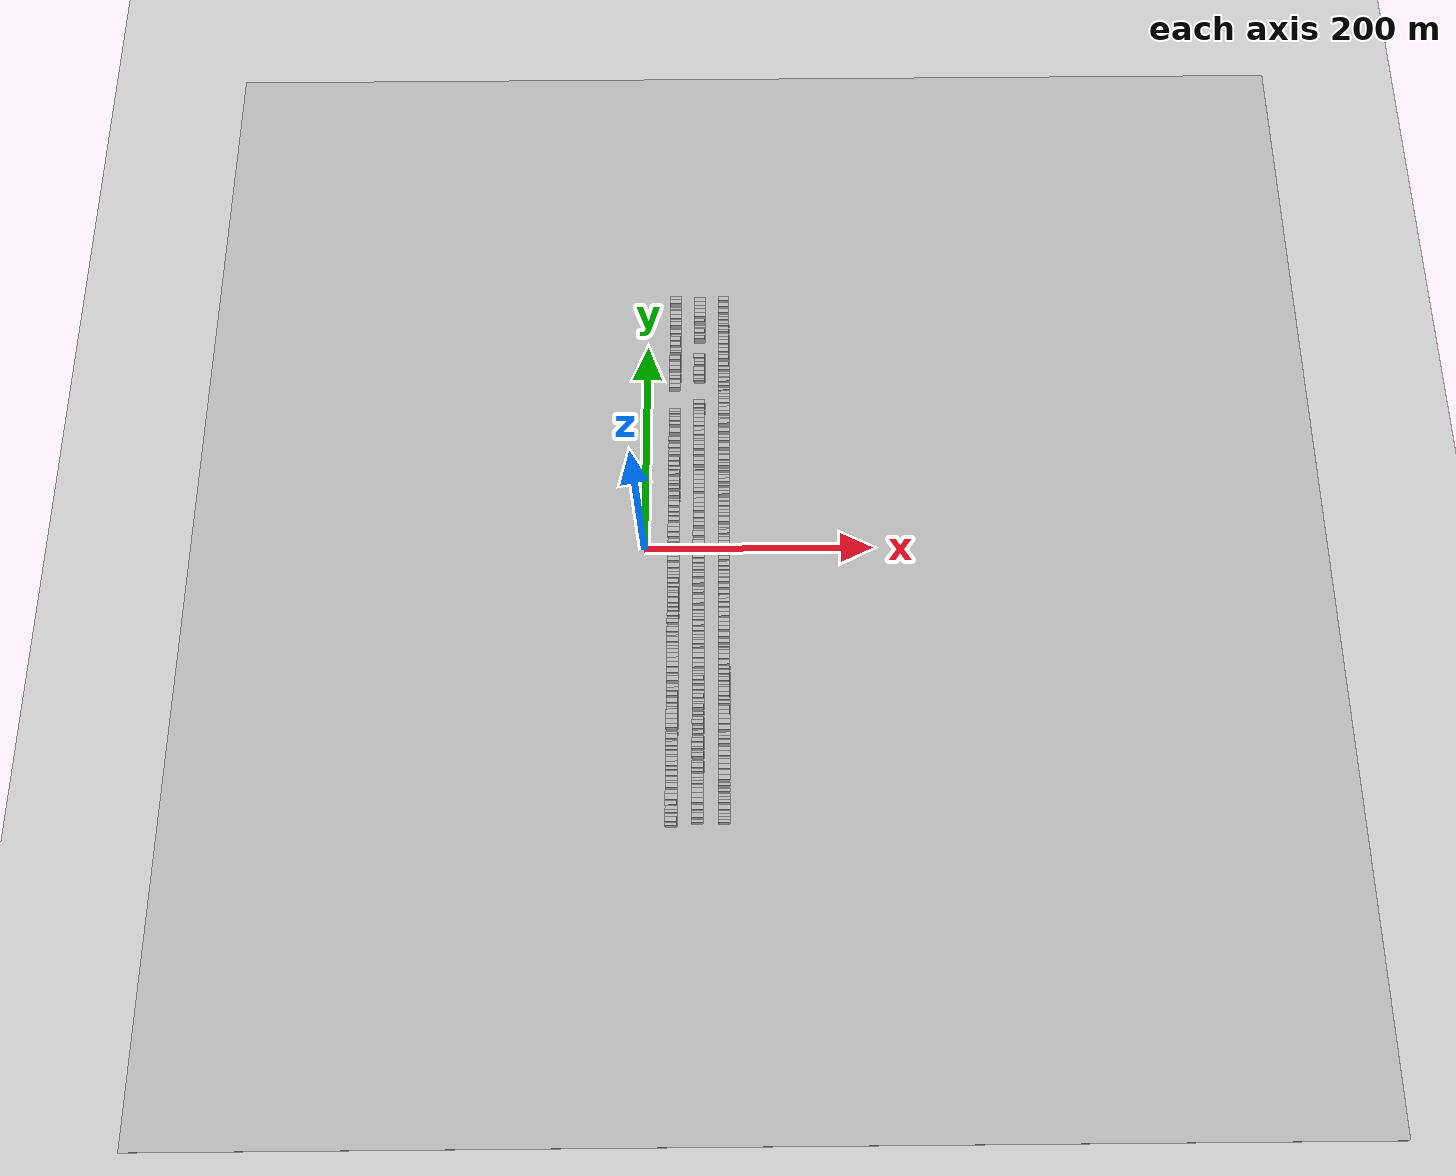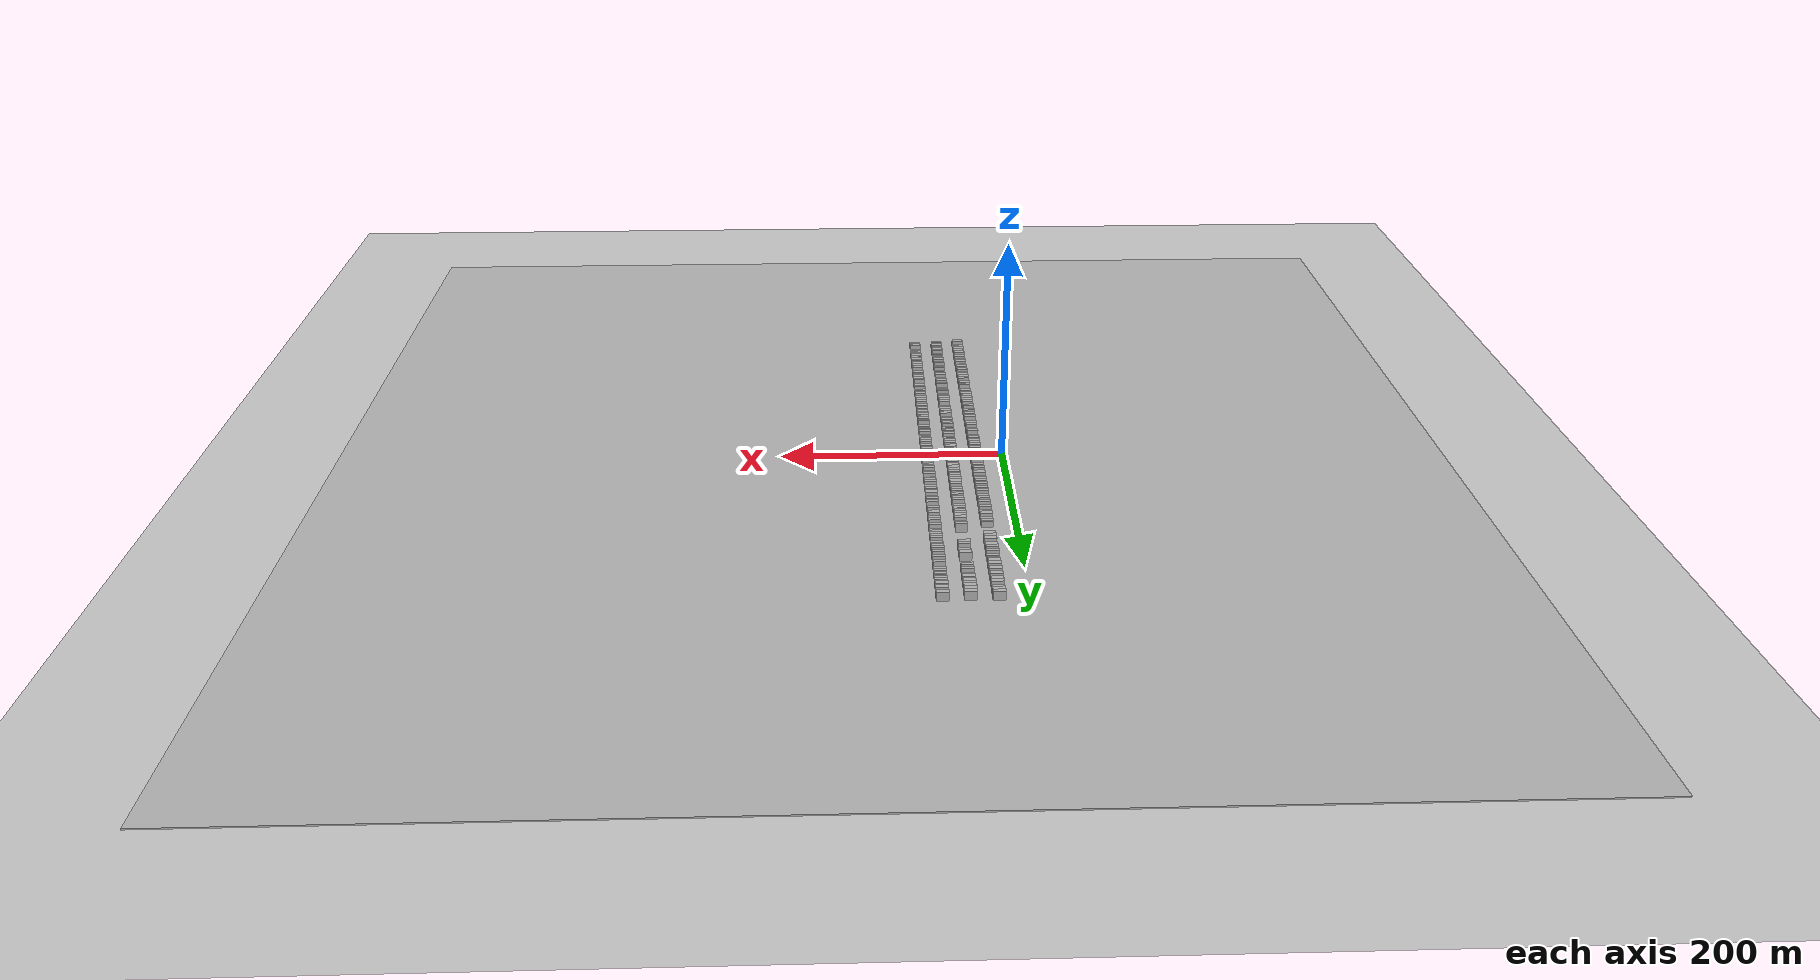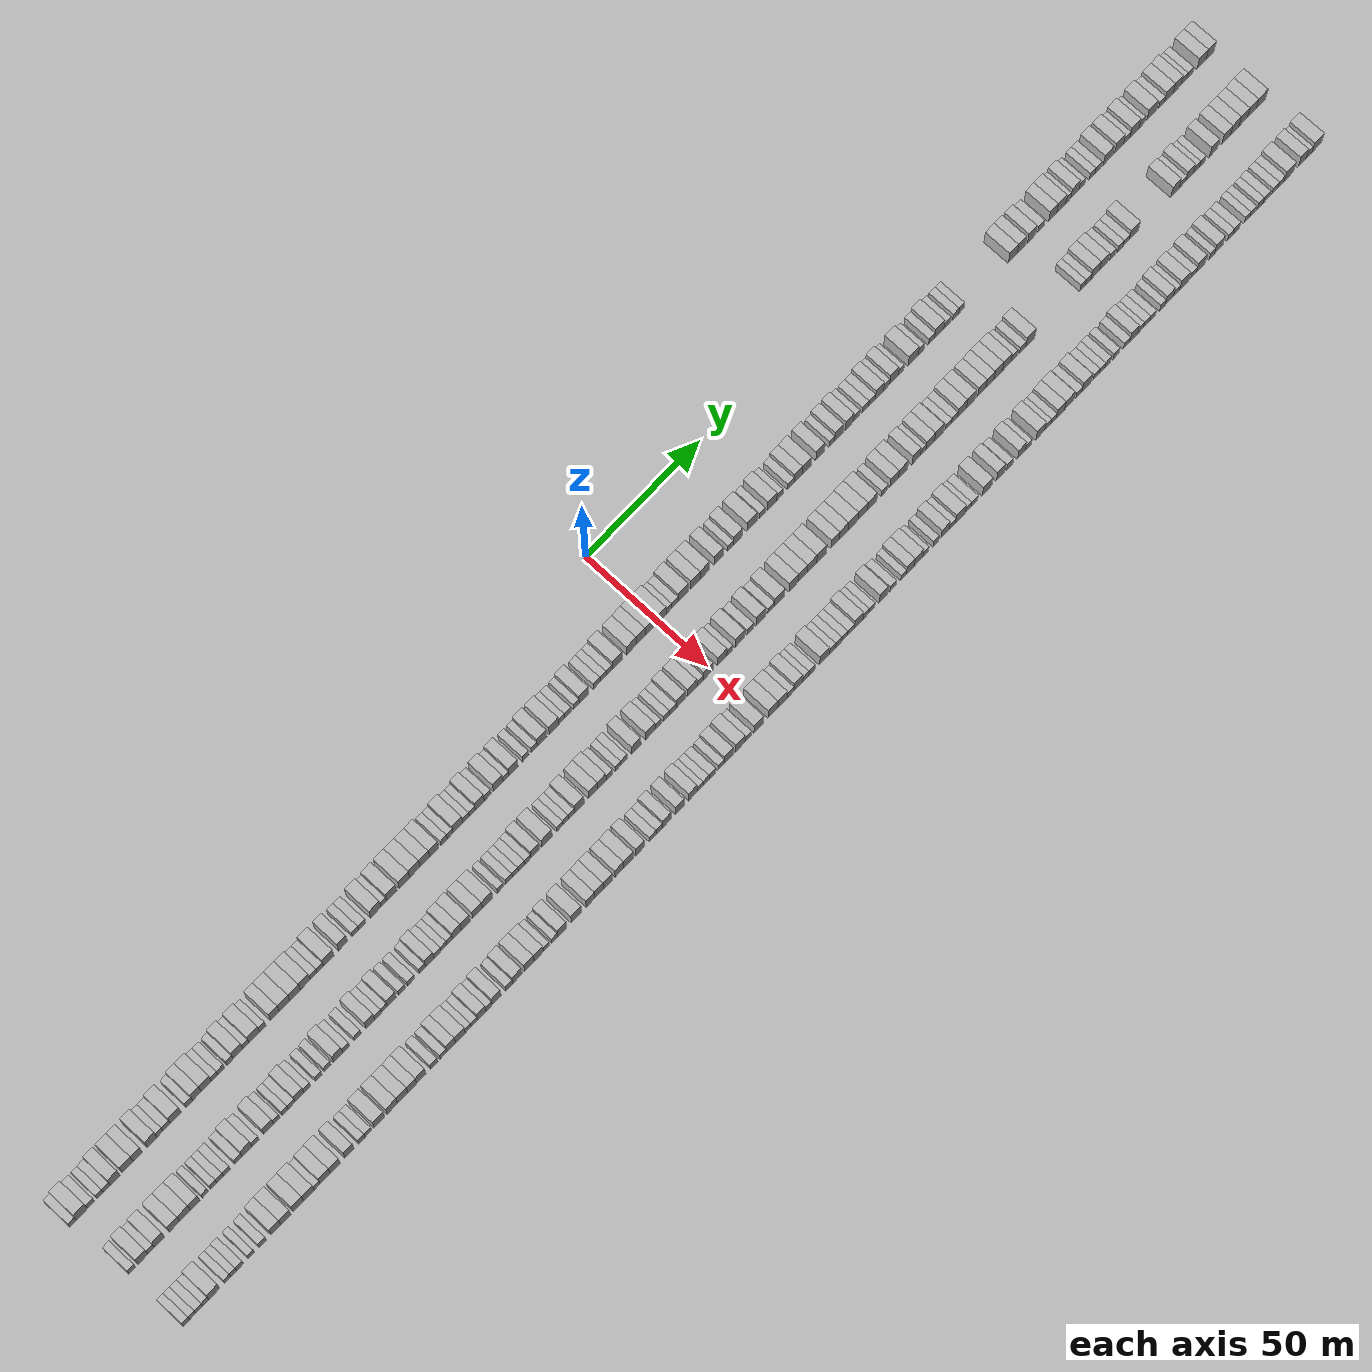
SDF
<?xml version="1.0" encoding="utf-8"?>

<sdf version="1.6">

   <world name="default">

      <gui fullscreen="0">

         <camera name="user_camera">

            <pose>-15 0 4.57585 0 0 0</pose>

            <view_controller>orbit</view_controller>

         </camera>

      </gui>

      <scene>

         <sky>

           <clouds>

             <speed>12</speed>

           </clouds>

         </sky>

         <ambient>0.4 0.4 0.4 1</ambient>

         <background>0.7 0.7 0.7 1</background>

         <shadows>1</shadows>

      </scene>

      <gravity>0 0 -9.8066</gravity>

      <magnetic_field>6e-06 2.3e-05 -4.2e-05</magnetic_field>

      <physics default="0" name="default_physics" type="ode">

         <ode>

            <solver>

               <type>quick</type>

               <iters>10</iters>

               <sor>1.0</sor>

               <use_dynamic_moi_rescaling>0</use_dynamic_moi_rescaling>

            </solver>

            <constraints>

               <cfm>0</cfm>

               <erp>0.2</erp>

               <contact_max_correcting_vel>100</contact_max_correcting_vel>

               <contact_surface_layer>0.001</contact_surface_layer>

            </constraints>

         </ode>

         <max_step_size>0.004</max_step_size>

         <real_time_factor>1</real_time_factor>

         <real_time_update_rate>250</real_time_update_rate>

      </physics>

      <light name="sun" type="directional">

         <cast_shadows>1</cast_shadows>

         <pose>0 0 10 0 0 0</pose>

         <diffuse>0.8 0.8 0.8 1</diffuse>

         <specular>0.2 0.2 0.2 1</specular>

         <attenuation>

            <range>1000</range>

            <constant>0.9</constant>

            <linear>0.01</linear>

            <quadratic>0.001</quadratic>

         </attenuation>

         <direction>-0.5 0.1 -0.9</direction>

      </light>

      <include>

         <name>ground_plane_1</name>

         <uri>model://HANNAS_ground_plane</uri>

         <pose>0 0 0  0 0 0</pose>

      </include>

      <include>

         <name>ground_plane_2</name>

         <uri>model://HANNAS_ground_plane</uri>

         <pose>100 0 0  0 0 0</pose>

      </include>

      <model name="building_1">

         <static>1</static>

         <pose frame="">25.0000 -246.6226 0 0.000000 0.000000 0.000000</pose>

         <link name="link">

            <pose frame="">0 0 3.00 0 0 0</pose>

            <collision name="collision">

               <geometry>

                  <box>

                     <size>10.0000 2.7547 6.0000</size>

                  </box>

               </geometry>

               <max_contacts>10</max_contacts>

               <surface>

                  <contact>

                     <ode/>

                  </contact>

                  <bounce/>

                  <friction>

                     <torsional>

                        <ode/>

                     </torsional>

                     <ode/>

                  </friction>

               </surface>

            </collision>

            <visual name="visual">

               <cast_shadows>0</cast_shadows>

               <geometry>

                  <box>

                     <size>10.0000 2.7547 6.0000</size>

                  </box>

               </geometry>

               <material>

                  <script>

                     <uri>model://HANNAS_wall/materials/scripts</uri>

                     <uri>model://HANNAS_wall/materials/textures</uri>

                     <name>vrc/HANNAS_wall</name>

                  </script>

               </material>

            </visual>

            <self_collide>0</self_collide>

            <enable_wind>0</enable_wind>

            <kinematic>0</kinematic>

         </link>

      </model>

      <model name="building_2">

         <static>1</static>

         <pose frame="">25.0000 -243.0029 0 0.000000 0.000000 0.000000</pose>

         <link name="link">

            <pose frame="">0 0 4.50 0 0 0</pose>

            <collision name="collision">

               <geometry>

                  <box>

                     <size>10.0000 4.4848 9.0000</size>

                  </box>

               </geometry>

               <max_contacts>10</max_contacts>

               <surface>

                  <contact>

                     <ode/>

                  </contact>

                  <bounce/>

                  <friction>

                     <torsional>

                        <ode/>

                     </torsional>

                     <ode/>

                  </friction>

               </surface>

            </collision>

            <visual name="visual">

               <cast_shadows>0</cast_shadows>

               <geometry>

                  <box>

                     <size>10.0000 4.4848 9.0000</size>

                  </box>

               </geometry>

               <material>

                  <script>

                     <uri>model://HANNAS_wall/materials/scripts</uri>

                     <uri>model://HANNAS_wall/materials/textures</uri>

                     <name>vrc/HANNAS_wall</name>

                  </script>

               </material>

            </visual>

            <self_collide>0</self_collide>

            <enable_wind>0</enable_wind>

            <kinematic>0</kinematic>

         </link>

      </model>

      <model name="building_3">

         <static>1</static>

         <pose frame="">25.0000 -239.2915 0 0.000000 0.000000 0.000000</pose>

         <link name="link">

            <pose frame="">0 0 3.00 0 0 0</pose>

            <collision name="collision">

               <geometry>

                  <box>

                     <size>10.0000 2.9379 6.0000</size>

                  </box>

               </geometry>

               <max_contacts>10</max_contacts>

               <surface>

                  <contact>

                     <ode/>

                  </contact>

                  <bounce/>

                  <friction>

                     <torsional>

                        <ode/>

                     </torsional>

                     <ode/>

                  </friction>

               </surface>

            </collision>

            <visual name="visual">

               <cast_shadows>0</cast_shadows>

               <geometry>

                  <box>

                     <size>10.0000 2.9379 6.0000</size>

                  </box>

               </geometry>

               <material>

                  <script>

                     <uri>model://HANNAS_wall/materials/scripts</uri>

                     <uri>model://HANNAS_wall/materials/textures</uri>

                     <name>vrc/HANNAS_wall</name>

                  </script>

               </material>

            </visual>

            <self_collide>0</self_collide>

            <enable_wind>0</enable_wind>

            <kinematic>0</kinematic>

         </link>

      </model>

      <model name="building_4">

         <static>1</static>

         <pose frame="">25.0000 -235.5439 0 0.000000 0.000000 0.000000</pose>

         <link name="link">

            <pose frame="">0 0 3.00 0 0 0</pose>

            <collision name="collision">

               <geometry>

                  <box>

                     <size>10.0000 2.5574 6.0000</size>

                  </box>

               </geometry>

               <max_contacts>10</max_contacts>

               <surface>

                  <contact>

                     <ode/>

                  </contact>

                  <bounce/>

                  <friction>

                     <torsional>

                        <ode/>

                     </torsional>

                     <ode/>

                  </friction>

               </surface>

            </collision>

            <visual name="visual">

               <cast_shadows>0</cast_shadows>

               <geometry>

                  <box>

                     <size>10.0000 2.5574 6.0000</size>

                  </box>

               </geometry>

               <material>

                  <script>

                     <uri>model://HANNAS_wall/materials/scripts</uri>

                     <uri>model://HANNAS_wall/materials/textures</uri>

                     <name>vrc/HANNAS_wall</name>

                  </script>

               </material>

            </visual>

            <self_collide>0</self_collide>

            <enable_wind>0</enable_wind>

            <kinematic>0</kinematic>

         </link>

      </model>

      <model name="building_5">

         <static>1</static>

         <pose frame="">25.0000 -232.8576 0 0.000000 0.000000 0.000000</pose>

         <link name="link">

            <pose frame="">0 0 3.00 0 0 0</pose>

            <collision name="collision">

               <geometry>

                  <box>

                     <size>10.0000 2.8151 6.0000</size>

                  </box>

               </geometry>

               <max_contacts>10</max_contacts>

               <surface>

                  <contact>

                     <ode/>

                  </contact>

                  <bounce/>

                  <friction>

                     <torsional>

                        <ode/>

                     </torsional>

                     <ode/>

                  </friction>

               </surface>

            </collision>

            <visual name="visual">

               <cast_shadows>0</cast_shadows>

               <geometry>

                  <box>

                     <size>10.0000 2.8151 6.0000</size>

                  </box>

               </geometry>

               <material>

                  <script>

                     <uri>model://HANNAS_wall/materials/scripts</uri>

                     <uri>model://HANNAS_wall/materials/textures</uri>

                     <name>vrc/HANNAS_wall</name>

                  </script>

               </material>

            </visual>

            <self_collide>0</self_collide>

            <enable_wind>0</enable_wind>

            <kinematic>0</kinematic>

         </link>

      </model>

      <model name="building_6">

         <static>1</static>

         <pose frame="">25.0000 -229.4669 0 0.000000 0.000000 0.000000</pose>

         <link name="link">

            <pose frame="">0 0 4.50 0 0 0</pose>

            <collision name="collision">

               <geometry>

                  <box>

                     <size>10.0000 3.9663 9.0000</size>

                  </box>

               </geometry>

               <max_contacts>10</max_contacts>

               <surface>

                  <contact>

                     <ode/>

                  </contact>

                  <bounce/>

                  <friction>

                     <torsional>

                        <ode/>

                     </torsional>

                     <ode/>

                  </friction>

               </surface>

            </collision>

            <visual name="visual">

               <cast_shadows>0</cast_shadows>

               <geometry>

                  <box>

                     <size>10.0000 3.9663 9.0000</size>

                  </box>

               </geometry>

               <material>

                  <script>

                     <uri>model://HANNAS_wall/materials/scripts</uri>

                     <uri>model://HANNAS_wall/materials/textures</uri>

                     <name>vrc/HANNAS_wall</name>

                  </script>

               </material>

            </visual>

            <self_collide>0</self_collide>

            <enable_wind>0</enable_wind>

            <kinematic>0</kinematic>

         </link>

      </model>

      <model name="building_7">

         <static>1</static>

         <pose frame="">25.0000 -224.2547 0 0.000000 0.000000 0.000000</pose>

         <link name="link">

            <pose frame="">0 0 4.50 0 0 0</pose>

            <collision name="collision">

               <geometry>

                  <box>

                     <size>10.0000 4.4581 9.0000</size>

                  </box>

               </geometry>

               <max_contacts>10</max_contacts>

               <surface>

                  <contact>

                     <ode/>

                  </contact>

                  <bounce/>

                  <friction>

                     <torsional>

                        <ode/>

                     </torsional>

                     <ode/>

                  </friction>

               </surface>

            </collision>

            <visual name="visual">

               <cast_shadows>0</cast_shadows>

               <geometry>

                  <box>

                     <size>10.0000 4.4581 9.0000</size>

                  </box>

               </geometry>

               <material>

                  <script>

                     <uri>model://HANNAS_wall/materials/scripts</uri>

                     <uri>model://HANNAS_wall/materials/textures</uri>

                     <name>vrc/HANNAS_wall</name>

                  </script>

               </material>

            </visual>

            <self_collide>0</self_collide>

            <enable_wind>0</enable_wind>

            <kinematic>0</kinematic>

         </link>

      </model>

      <model name="building_8">

         <static>1</static>

         <pose frame="">25.0000 -220.1906 0 0.000000 0.000000 0.000000</pose>

         <link name="link">

            <pose frame="">0 0 4.50 0 0 0</pose>

            <collision name="collision">

               <geometry>

                  <box>

                     <size>10.0000 3.6701 9.0000</size>

                  </box>

               </geometry>

               <max_contacts>10</max_contacts>

               <surface>

                  <contact>

                     <ode/>

                  </contact>

                  <bounce/>

                  <friction>

                     <torsional>

                        <ode/>

                     </torsional>

                     <ode/>

                  </friction>

               </surface>

            </collision>

            <visual name="visual">

               <cast_shadows>0</cast_shadows>

               <geometry>

                  <box>

                     <size>10.0000 3.6701 9.0000</size>

                  </box>

               </geometry>

               <material>

                  <script>

                     <uri>model://HANNAS_wall/materials/scripts</uri>

                     <uri>model://HANNAS_wall/materials/textures</uri>

                     <name>vrc/HANNAS_wall</name>

                  </script>

               </material>

            </visual>

            <self_collide>0</self_collide>

            <enable_wind>0</enable_wind>

            <kinematic>0</kinematic>

         </link>

      </model>

      <model name="building_9">

         <static>1</static>

         <pose frame="">25.0000 -214.3518 0 0.000000 0.000000 0.000000</pose>

         <link name="link">

            <pose frame="">0 0 4.50 0 0 0</pose>

            <collision name="collision">

               <geometry>

                  <box>

                     <size>10.0000 4.0076 9.0000</size>

                  </box>

               </geometry>

               <max_contacts>10</max_contacts>

               <surface>

                  <contact>

                     <ode/>

                  </contact>

                  <bounce/>

                  <friction>

                     <torsional>

                        <ode/>

                     </torsional>

                     <ode/>

                  </friction>

               </surface>

            </collision>

            <visual name="visual">

               <cast_shadows>0</cast_shadows>

               <geometry>

                  <box>

                     <size>10.0000 4.0076 9.0000</size>

                  </box>

               </geometry>

               <material>

                  <script>

                     <uri>model://HANNAS_wall/materials/scripts</uri>

                     <uri>model://HANNAS_wall/materials/textures</uri>

                     <name>vrc/HANNAS_wall</name>

                  </script>

               </material>

            </visual>

            <self_collide>0</self_collide>

            <enable_wind>0</enable_wind>

            <kinematic>0</kinematic>

         </link>

      </model>

      <model name="building_10">

         <static>1</static>

         <pose frame="">25.0000 -211.0869 0 0.000000 0.000000 0.000000</pose>

         <link name="link">

            <pose frame="">0 0 3.00 0 0 0</pose>

            <collision name="collision">

               <geometry>

                  <box>

                     <size>10.0000 2.5222 6.0000</size>

                  </box>

               </geometry>

               <max_contacts>10</max_contacts>

               <surface>

                  <contact>

                     <ode/>

                  </contact>

                  <bounce/>

                  <friction>

                     <torsional>

                        <ode/>

                     </torsional>

                     <ode/>

                  </friction>

               </surface>

            </collision>

            <visual name="visual">

               <cast_shadows>0</cast_shadows>

               <geometry>

                  <box>

                     <size>10.0000 2.5222 6.0000</size>

                  </box>

               </geometry>

               <material>

                  <script>

                     <uri>model://HANNAS_wall/materials/scripts</uri>

                     <uri>model://HANNAS_wall/materials/textures</uri>

                     <name>vrc/HANNAS_wall</name>

                  </script>

               </material>

            </visual>

            <self_collide>0</self_collide>

            <enable_wind>0</enable_wind>

            <kinematic>0</kinematic>

         </link>

      </model>

      <model name="building_11">

         <static>1</static>

         <pose frame="">25.0000 -208.3262 0 0.000000 0.000000 0.000000</pose>

         <link name="link">

            <pose frame="">0 0 3.00 0 0 0</pose>

            <collision name="collision">

               <geometry>

                  <box>

                     <size>10.0000 2.9993 6.0000</size>

                  </box>

               </geometry>

               <max_contacts>10</max_contacts>

               <surface>

                  <contact>

                     <ode/>

                  </contact>

                  <bounce/>

                  <friction>

                     <torsional>

                        <ode/>

                     </torsional>

                     <ode/>

                  </friction>

               </surface>

            </collision>

            <visual name="visual">

               <cast_shadows>0</cast_shadows>

               <geometry>

                  <box>

                     <size>10.0000 2.9993 6.0000</size>

                  </box>

               </geometry>

               <material>

                  <script>

                     <uri>model://HANNAS_wall/materials/scripts</uri>

                     <uri>model://HANNAS_wall/materials/textures</uri>

                     <name>vrc/HANNAS_wall</name>

                  </script>

               </material>

            </visual>

            <self_collide>0</self_collide>

            <enable_wind>0</enable_wind>

            <kinematic>0</kinematic>

         </link>

      </model>

      <model name="building_12">

         <static>1</static>

         <pose frame="">25.0000 -204.5847 0 0.000000 0.000000 0.000000</pose>

         <link name="link">

            <pose frame="">0 0 4.50 0 0 0</pose>

            <collision name="collision">

               <geometry>

                  <box>

                     <size>10.0000 4.4837 9.0000</size>

                  </box>

               </geometry>

               <max_contacts>10</max_contacts>

               <surface>

                  <contact>

                     <ode/>

                  </contact>

                  <bounce/>

                  <friction>

                     <torsional>

                        <ode/>

                     </torsional>

                     <ode/>

                  </friction>

               </surface>

            </collision>

            <visual name="visual">

               <cast_shadows>0</cast_shadows>

               <geometry>

                  <box>

                     <size>10.0000 4.4837 9.0000</size>

                  </box>

               </geometry>

               <material>

                  <script>

                     <uri>model://HANNAS_wall/materials/scripts</uri>

                     <uri>model://HANNAS_wall/materials/textures</uri>

                     <name>vrc/HANNAS_wall</name>

                  </script>

               </material>

            </visual>

            <self_collide>0</self_collide>

            <enable_wind>0</enable_wind>

            <kinematic>0</kinematic>

         </link>

      </model>

      <model name="building_13">

         <static>1</static>

         <pose frame="">25.0000 -199.0204 0 0.000000 0.000000 0.000000</pose>

         <link name="link">

            <pose frame="">0 0 3.00 0 0 0</pose>

            <collision name="collision">

               <geometry>

                  <box>

                     <size>10.0000 2.6449 6.0000</size>

                  </box>

               </geometry>

               <max_contacts>10</max_contacts>

               <surface>

                  <contact>

                     <ode/>

                  </contact>

                  <bounce/>

                  <friction>

                     <torsional>

                        <ode/>

                     </torsional>

                     <ode/>

                  </friction>

               </surface>

            </collision>

            <visual name="visual">

               <cast_shadows>0</cast_shadows>

               <geometry>

                  <box>

                     <size>10.0000 2.6449 6.0000</size>

                  </box>

               </geometry>

               <material>

                  <script>

                     <uri>model://HANNAS_wall/materials/scripts</uri>

                     <uri>model://HANNAS_wall/materials/textures</uri>

                     <name>vrc/HANNAS_wall</name>

                  </script>

               </material>

            </visual>

            <self_collide>0</self_collide>

            <enable_wind>0</enable_wind>

            <kinematic>0</kinematic>

         </link>

      </model>

      <model name="building_14">

         <static>1</static>

         <pose frame="">25.0000 -195.8734 0 0.000000 0.000000 0.000000</pose>

         <link name="link">

            <pose frame="">0 0 4.50 0 0 0</pose>

            <collision name="collision">

               <geometry>

                  <box>

                     <size>10.0000 3.6491 9.0000</size>

                  </box>

               </geometry>

               <max_contacts>10</max_contacts>

               <surface>

                  <contact>

                     <ode/>

                  </contact>

                  <bounce/>

                  <friction>

                     <torsional>

                        <ode/>

                     </torsional>

                     <ode/>

                  </friction>

               </surface>

            </collision>

            <visual name="visual">

               <cast_shadows>0</cast_shadows>

               <geometry>

                  <box>

                     <size>10.0000 3.6491 9.0000</size>

                  </box>

               </geometry>

               <material>

                  <script>

                     <uri>model://HANNAS_wall/materials/scripts</uri>

                     <uri>model://HANNAS_wall/materials/textures</uri>

                     <name>vrc/HANNAS_wall</name>

                  </script>

               </material>

            </visual>

            <self_collide>0</self_collide>

            <enable_wind>0</enable_wind>

            <kinematic>0</kinematic>

         </link>

      </model>

      <model name="building_15">

         <static>1</static>

         <pose frame="">25.0000 -191.9435 0 0.000000 0.000000 0.000000</pose>

         <link name="link">

            <pose frame="">0 0 4.50 0 0 0</pose>

            <collision name="collision">

               <geometry>

                  <box>

                     <size>10.0000 4.2108 9.0000</size>

                  </box>

               </geometry>

               <max_contacts>10</max_contacts>

               <surface>

                  <contact>

                     <ode/>

                  </contact>

                  <bounce/>

                  <friction>

                     <torsional>

                        <ode/>

                     </torsional>

                     <ode/>

                  </friction>

               </surface>

            </collision>

            <visual name="visual">

               <cast_shadows>0</cast_shadows>

               <geometry>

                  <box>

                     <size>10.0000 4.2108 9.0000</size>

                  </box>

               </geometry>

               <material>

                  <script>

                     <uri>model://HANNAS_wall/materials/scripts</uri>

                     <uri>model://HANNAS_wall/materials/textures</uri>

                     <name>vrc/HANNAS_wall</name>

                  </script>

               </material>

            </visual>

            <self_collide>0</self_collide>

            <enable_wind>0</enable_wind>

            <kinematic>0</kinematic>

         </link>

      </model>

      <model name="building_16">

         <static>1</static>

         <pose frame="">25.0000 -188.5577 0 0.000000 0.000000 0.000000</pose>

         <link name="link">

            <pose frame="">0 0 3.00 0 0 0</pose>

            <collision name="collision">

               <geometry>

                  <box>

                     <size>10.0000 2.5607 6.0000</size>

                  </box>

               </geometry>

               <max_contacts>10</max_contacts>

               <surface>

                  <contact>

                     <ode/>

                  </contact>

                  <bounce/>

                  <friction>

                     <torsional>

                        <ode/>

                     </torsional>

                     <ode/>

                  </friction>

               </surface>

            </collision>

            <visual name="visual">

               <cast_shadows>0</cast_shadows>

               <geometry>

                  <box>

                     <size>10.0000 2.5607 6.0000</size>

                  </box>

               </geometry>

               <material>

                  <script>

                     <uri>model://HANNAS_wall/materials/scripts</uri>

                     <uri>model://HANNAS_wall/materials/textures</uri>

                     <name>vrc/HANNAS_wall</name>

                  </script>

               </material>

            </visual>

            <self_collide>0</self_collide>

            <enable_wind>0</enable_wind>

            <kinematic>0</kinematic>

         </link>

      </model>

      <model name="building_17">

         <static>1</static>

         <pose frame="">25.0000 -185.8615 0 0.000000 0.000000 0.000000</pose>

         <link name="link">

            <pose frame="">0 0 3.00 0 0 0</pose>

            <collision name="collision">

               <geometry>

                  <box>

                     <size>10.0000 2.8317 6.0000</size>

                  </box>

               </geometry>

               <max_contacts>10</max_contacts>

               <surface>

                  <contact>

                     <ode/>

                  </contact>

                  <bounce/>

                  <friction>

                     <torsional>

                        <ode/>

                     </torsional>

                     <ode/>

                  </friction>

               </surface>

            </collision>

            <visual name="visual">

               <cast_shadows>0</cast_shadows>

               <geometry>

                  <box>

                     <size>10.0000 2.8317 6.0000</size>

                  </box>

               </geometry>

               <material>

                  <script>

                     <uri>model://HANNAS_wall/materials/scripts</uri>

                     <uri>model://HANNAS_wall/materials/textures</uri>

                     <name>vrc/HANNAS_wall</name>

                  </script>

               </material>

            </visual>

            <self_collide>0</self_collide>

            <enable_wind>0</enable_wind>

            <kinematic>0</kinematic>

         </link>

      </model>

      <model name="building_18">

         <static>1</static>

         <pose frame="">25.0000 -182.1435 0 0.000000 0.000000 0.000000</pose>

         <link name="link">

            <pose frame="">0 0 3.00 0 0 0</pose>

            <collision name="collision">

               <geometry>

                  <box>

                     <size>10.0000 2.6043 6.0000</size>

                  </box>

               </geometry>

               <max_contacts>10</max_contacts>

               <surface>

                  <contact>

                     <ode/>

                  </contact>

                  <bounce/>

                  <friction>

                     <torsional>

                        <ode/>

                     </torsional>

                     <ode/>

                  </friction>

               </surface>

            </collision>

            <visual name="visual">

               <cast_shadows>0</cast_shadows>

               <geometry>

                  <box>

                     <size>10.0000 2.6043 6.0000</size>

                  </box>

               </geometry>

               <material>

                  <script>

                     <uri>model://HANNAS_wall/materials/scripts</uri>

                     <uri>model://HANNAS_wall/materials/textures</uri>

                     <name>vrc/HANNAS_wall</name>

                  </script>

               </material>

            </visual>

            <self_collide>0</self_collide>

            <enable_wind>0</enable_wind>

            <kinematic>0</kinematic>

         </link>

      </model>

      <model name="building_19">

         <static>1</static>

         <pose frame="">25.0000 -178.8061 0 0.000000 0.000000 0.000000</pose>

         <link name="link">

            <pose frame="">0 0 4.50 0 0 0</pose>

            <collision name="collision">

               <geometry>

                  <box>

                     <size>10.0000 4.0706 9.0000</size>

                  </box>

               </geometry>

               <max_contacts>10</max_contacts>

               <surface>

                  <contact>

                     <ode/>

                  </contact>

                  <bounce/>

                  <friction>

                     <torsional>

                        <ode/>

                     </torsional>

                     <ode/>

                  </friction>

               </surface>

            </collision>

            <visual name="visual">

               <cast_shadows>0</cast_shadows>

               <geometry>

                  <box>

                     <size>10.0000 4.0706 9.0000</size>

                  </box>

               </geometry>

               <material>

                  <script>

                     <uri>model://HANNAS_wall/materials/scripts</uri>

                     <uri>model://HANNAS_wall/materials/textures</uri>

                     <name>vrc/HANNAS_wall</name>

                  </script>

               </material>

            </visual>

            <self_collide>0</self_collide>

            <enable_wind>0</enable_wind>

            <kinematic>0</kinematic>

         </link>

      </model>

      <model name="building_20">

         <static>1</static>

         <pose frame="">25.0000 -175.5653 0 0.000000 0.000000 0.000000</pose>

         <link name="link">

            <pose frame="">0 0 3.00 0 0 0</pose>

            <collision name="collision">

               <geometry>

                  <box>

                     <size>10.0000 2.4108 6.0000</size>

                  </box>

               </geometry>

               <max_contacts>10</max_contacts>

               <surface>

                  <contact>

                     <ode/>

                  </contact>

                  <bounce/>

                  <friction>

                     <torsional>

                        <ode/>

                     </torsional>

                     <ode/>

                  </friction>

               </surface>

            </collision>

            <visual name="visual">

               <cast_shadows>0</cast_shadows>

               <geometry>

                  <box>

                     <size>10.0000 2.4108 6.0000</size>

                  </box>

               </geometry>

               <material>

                  <script>

                     <uri>model://HANNAS_wall/materials/scripts</uri>

                     <uri>model://HANNAS_wall/materials/textures</uri>

                     <name>vrc/HANNAS_wall</name>

                  </script>

               </material>

            </visual>

            <self_collide>0</self_collide>

            <enable_wind>0</enable_wind>

            <kinematic>0</kinematic>

         </link>

      </model>

      <model name="building_21">

         <static>1</static>

         <pose frame="">25.0000 -172.1222 0 0.000000 0.000000 0.000000</pose>

         <link name="link">

            <pose frame="">0 0 4.50 0 0 0</pose>

            <collision name="collision">

               <geometry>

                  <box>

                     <size>10.0000 4.4754 9.0000</size>

                  </box>

               </geometry>

               <max_contacts>10</max_contacts>

               <surface>

                  <contact>

                     <ode/>

                  </contact>

                  <bounce/>

                  <friction>

                     <torsional>

                        <ode/>

                     </torsional>

                     <ode/>

                  </friction>

               </surface>

            </collision>

            <visual name="visual">

               <cast_shadows>0</cast_shadows>

               <geometry>

                  <box>

                     <size>10.0000 4.4754 9.0000</size>

                  </box>

               </geometry>

               <material>

                  <script>

                     <uri>model://HANNAS_wall/materials/scripts</uri>

                     <uri>model://HANNAS_wall/materials/textures</uri>

                     <name>vrc/HANNAS_wall</name>

                  </script>

               </material>

            </visual>

            <self_collide>0</self_collide>

            <enable_wind>0</enable_wind>

            <kinematic>0</kinematic>

         </link>

      </model>

      <model name="building_22">

         <static>1</static>

         <pose frame="">25.0000 -168.6084 0 0.000000 0.000000 0.000000</pose>

         <link name="link">

            <pose frame="">0 0 3.00 0 0 0</pose>

            <collision name="collision">

               <geometry>

                  <box>

                     <size>10.0000 2.5524 6.0000</size>

                  </box>

               </geometry>

               <max_contacts>10</max_contacts>

               <surface>

                  <contact>

                     <ode/>

                  </contact>

                  <bounce/>

                  <friction>

                     <torsional>

                        <ode/>

                     </torsional>

                     <ode/>

                  </friction>

               </surface>

            </collision>

            <visual name="visual">

               <cast_shadows>0</cast_shadows>

               <geometry>

                  <box>

                     <size>10.0000 2.5524 6.0000</size>

                  </box>

               </geometry>

               <material>

                  <script>

                     <uri>model://HANNAS_wall/materials/scripts</uri>

                     <uri>model://HANNAS_wall/materials/textures</uri>

                     <name>vrc/HANNAS_wall</name>

                  </script>

               </material>

            </visual>

            <self_collide>0</self_collide>

            <enable_wind>0</enable_wind>

            <kinematic>0</kinematic>

         </link>

      </model>

      <model name="building_23">

         <static>1</static>

         <pose frame="">25.0000 -163.4872 0 0.000000 0.000000 0.000000</pose>

         <link name="link">

            <pose frame="">0 0 4.50 0 0 0</pose>

            <collision name="collision">

               <geometry>

                  <box>

                     <size>10.0000 3.6900 9.0000</size>

                  </box>

               </geometry>

               <max_contacts>10</max_contacts>

               <surface>

                  <contact>

                     <ode/>

                  </contact>

                  <bounce/>

                  <friction>

                     <torsional>

                        <ode/>

                     </torsional>

                     <ode/>

                  </friction>

               </surface>

            </collision>

            <visual name="visual">

               <cast_shadows>0</cast_shadows>

               <geometry>

                  <box>

                     <size>10.0000 3.6900 9.0000</size>

                  </box>

               </geometry>

               <material>

                  <script>

                     <uri>model://HANNAS_wall/materials/scripts</uri>

                     <uri>model://HANNAS_wall/materials/textures</uri>

                     <name>vrc/HANNAS_wall</name>

                  </script>

               </material>

            </visual>

            <self_collide>0</self_collide>

            <enable_wind>0</enable_wind>

            <kinematic>0</kinematic>

         </link>

      </model>

      <model name="building_24">

         <static>1</static>

         <pose frame="">25.0000 -159.4604 0 0.000000 0.000000 0.000000</pose>

         <link name="link">

            <pose frame="">0 0 4.50 0 0 0</pose>

            <collision name="collision">

               <geometry>

                  <box>

                     <size>10.0000 4.3637 9.0000</size>

                  </box>

               </geometry>

               <max_contacts>10</max_contacts>

               <surface>

                  <contact>

                     <ode/>

                  </contact>

                  <bounce/>

                  <friction>

                     <torsional>

                        <ode/>

                     </torsional>

                     <ode/>

                  </friction>

               </surface>

            </collision>

            <visual name="visual">

               <cast_shadows>0</cast_shadows>

               <geometry>

                  <box>

                     <size>10.0000 4.3637 9.0000</size>

                  </box>

               </geometry>

               <material>

                  <script>

                     <uri>model://HANNAS_wall/materials/scripts</uri>

                     <uri>model://HANNAS_wall/materials/textures</uri>

                     <name>vrc/HANNAS_wall</name>

                  </script>

               </material>

            </visual>

            <self_collide>0</self_collide>

            <enable_wind>0</enable_wind>

            <kinematic>0</kinematic>

         </link>

      </model>

      <model name="building_25">

         <static>1</static>

         <pose frame="">25.0000 -155.0788 0 0.000000 0.000000 0.000000</pose>

         <link name="link">

            <pose frame="">0 0 4.50 0 0 0</pose>

            <collision name="collision">

               <geometry>

                  <box>

                     <size>10.0000 4.3995 9.0000</size>

                  </box>

               </geometry>

               <max_contacts>10</max_contacts>

               <surface>

                  <contact>

                     <ode/>

                  </contact>

                  <bounce/>

                  <friction>

                     <torsional>

                        <ode/>

                     </torsional>

                     <ode/>

                  </friction>

               </surface>

            </collision>

            <visual name="visual">

               <cast_shadows>0</cast_shadows>

               <geometry>

                  <box>

                     <size>10.0000 4.3995 9.0000</size>

                  </box>

               </geometry>

               <material>

                  <script>

                     <uri>model://HANNAS_wall/materials/scripts</uri>

                     <uri>model://HANNAS_wall/materials/textures</uri>

                     <name>vrc/HANNAS_wall</name>

                  </script>

               </material>

            </visual>

            <self_collide>0</self_collide>

            <enable_wind>0</enable_wind>

            <kinematic>0</kinematic>

         </link>

      </model>

      <model name="building_26">

         <static>1</static>

         <pose frame="">25.0000 -150.8391 0 0.000000 0.000000 0.000000</pose>

         <link name="link">

            <pose frame="">0 0 4.50 0 0 0</pose>

            <collision name="collision">

               <geometry>

                  <box>

                     <size>10.0000 4.0798 9.0000</size>

                  </box>

               </geometry>

               <max_contacts>10</max_contacts>

               <surface>

                  <contact>

                     <ode/>

                  </contact>

                  <bounce/>

                  <friction>

                     <torsional>

                        <ode/>

                     </torsional>

                     <ode/>

                  </friction>

               </surface>

            </collision>

            <visual name="visual">

               <cast_shadows>0</cast_shadows>

               <geometry>

                  <box>

                     <size>10.0000 4.0798 9.0000</size>

                  </box>

               </geometry>

               <material>

                  <script>

                     <uri>model://HANNAS_wall/materials/scripts</uri>

                     <uri>model://HANNAS_wall/materials/textures</uri>

                     <name>vrc/HANNAS_wall</name>

                  </script>

               </material>

            </visual>

            <self_collide>0</self_collide>

            <enable_wind>0</enable_wind>

            <kinematic>0</kinematic>

         </link>

      </model>

      <model name="building_27">

         <static>1</static>

         <pose frame="">25.0000 -147.3620 0 0.000000 0.000000 0.000000</pose>

         <link name="link">

            <pose frame="">0 0 3.00 0 0 0</pose>

            <collision name="collision">

               <geometry>

                  <box>

                     <size>10.0000 2.8744 6.0000</size>

                  </box>

               </geometry>

               <max_contacts>10</max_contacts>

               <surface>

                  <contact>

                     <ode/>

                  </contact>

                  <bounce/>

                  <friction>

                     <torsional>

                        <ode/>

                     </torsional>

                     <ode/>

                  </friction>

               </surface>

            </collision>

            <visual name="visual">

               <cast_shadows>0</cast_shadows>

               <geometry>

                  <box>

                     <size>10.0000 2.8744 6.0000</size>

                  </box>

               </geometry>

               <material>

                  <script>

                     <uri>model://HANNAS_wall/materials/scripts</uri>

                     <uri>model://HANNAS_wall/materials/textures</uri>

                     <name>vrc/HANNAS_wall</name>

                  </script>

               </material>

            </visual>

            <self_collide>0</self_collide>

            <enable_wind>0</enable_wind>

            <kinematic>0</kinematic>

         </link>

      </model>

      <model name="building_28">

         <static>1</static>

         <pose frame="">25.0000 -144.6127 0 0.000000 0.000000 0.000000</pose>

         <link name="link">

            <pose frame="">0 0 3.00 0 0 0</pose>

            <collision name="collision">

               <geometry>

                  <box>

                     <size>10.0000 2.6241 6.0000</size>

                  </box>

               </geometry>

               <max_contacts>10</max_contacts>

               <surface>

                  <contact>

                     <ode/>

                  </contact>

                  <bounce/>

                  <friction>

                     <torsional>

                        <ode/>

                     </torsional>

                     <ode/>

                  </friction>

               </surface>

            </collision>

            <visual name="visual">

               <cast_shadows>0</cast_shadows>

               <geometry>

                  <box>

                     <size>10.0000 2.6241 6.0000</size>

                  </box>

               </geometry>

               <material>

                  <script>

                     <uri>model://HANNAS_wall/materials/scripts</uri>

                     <uri>model://HANNAS_wall/materials/textures</uri>

                     <name>vrc/HANNAS_wall</name>

                  </script>

               </material>

            </visual>

            <self_collide>0</self_collide>

            <enable_wind>0</enable_wind>

            <kinematic>0</kinematic>

         </link>

      </model>

      <model name="building_29">

         <static>1</static>

         <pose frame="">25.0000 -141.0831 0 0.000000 0.000000 0.000000</pose>

         <link name="link">

            <pose frame="">0 0 4.50 0 0 0</pose>

            <collision name="collision">

               <geometry>

                  <box>

                     <size>10.0000 4.4352 9.0000</size>

                  </box>

               </geometry>

               <max_contacts>10</max_contacts>

               <surface>

                  <contact>

                     <ode/>

                  </contact>

                  <bounce/>

                  <friction>

                     <torsional>

                        <ode/>

                     </torsional>

                     <ode/>

                  </friction>

               </surface>

            </collision>

            <visual name="visual">

               <cast_shadows>0</cast_shadows>

               <geometry>

                  <box>

                     <size>10.0000 4.4352 9.0000</size>

                  </box>

               </geometry>

               <material>

                  <script>

                     <uri>model://HANNAS_wall/materials/scripts</uri>

                     <uri>model://HANNAS_wall/materials/textures</uri>

                     <name>vrc/HANNAS_wall</name>

                  </script>

               </material>

            </visual>

            <self_collide>0</self_collide>

            <enable_wind>0</enable_wind>

            <kinematic>0</kinematic>

         </link>

      </model>

      <model name="building_30">

         <static>1</static>

         <pose frame="">25.0000 -135.0234 0 0.000000 0.000000 0.000000</pose>

         <link name="link">

            <pose frame="">0 0 4.50 0 0 0</pose>

            <collision name="collision">

               <geometry>

                  <box>

                     <size>10.0000 3.6841 9.0000</size>

                  </box>

               </geometry>

               <max_contacts>10</max_contacts>

               <surface>

                  <contact>

                     <ode/>

                  </contact>

                  <bounce/>

                  <friction>

                     <torsional>

                        <ode/>

                     </torsional>

                     <ode/>

                  </friction>

               </surface>

            </collision>

            <visual name="visual">

               <cast_shadows>0</cast_shadows>

               <geometry>

                  <box>

                     <size>10.0000 3.6841 9.0000</size>

                  </box>

               </geometry>

               <material>

                  <script>

                     <uri>model://HANNAS_wall/materials/scripts</uri>

                     <uri>model://HANNAS_wall/materials/textures</uri>

                     <name>vrc/HANNAS_wall</name>

                  </script>

               </material>

            </visual>

            <self_collide>0</self_collide>

            <enable_wind>0</enable_wind>

            <kinematic>0</kinematic>

         </link>

      </model>

      <model name="building_31">

         <static>1</static>

         <pose frame="">25.0000 -129.8097 0 0.000000 0.000000 0.000000</pose>

         <link name="link">

            <pose frame="">0 0 3.00 0 0 0</pose>

            <collision name="collision">

               <geometry>

                  <box>

                     <size>10.0000 2.7434 6.0000</size>

                  </box>

               </geometry>

               <max_contacts>10</max_contacts>

               <surface>

                  <contact>

                     <ode/>

                  </contact>

                  <bounce/>

                  <friction>

                     <torsional>

                        <ode/>

                     </torsional>

                     <ode/>

                  </friction>

               </surface>

            </collision>

            <visual name="visual">

               <cast_shadows>0</cast_shadows>

               <geometry>

                  <box>

                     <size>10.0000 2.7434 6.0000</size>

                  </box>

               </geometry>

               <material>

                  <script>

                     <uri>model://HANNAS_wall/materials/scripts</uri>

                     <uri>model://HANNAS_wall/materials/textures</uri>

                     <name>vrc/HANNAS_wall</name>

                  </script>

               </material>

            </visual>

            <self_collide>0</self_collide>

            <enable_wind>0</enable_wind>

            <kinematic>0</kinematic>

         </link>

      </model>

      <model name="building_32">

         <static>1</static>

         <pose frame="">25.0000 -126.9727 0 0.000000 0.000000 0.000000</pose>

         <link name="link">

            <pose frame="">0 0 3.00 0 0 0</pose>

            <collision name="collision">

               <geometry>

                  <box>

                     <size>10.0000 2.9306 6.0000</size>

                  </box>

               </geometry>

               <max_contacts>10</max_contacts>

               <surface>

                  <contact>

                     <ode/>

                  </contact>

                  <bounce/>

                  <friction>

                     <torsional>

                        <ode/>

                     </torsional>

                     <ode/>

                  </friction>

               </surface>

            </collision>

            <visual name="visual">

               <cast_shadows>0</cast_shadows>

               <geometry>

                  <box>

                     <size>10.0000 2.9306 6.0000</size>

                  </box>

               </geometry>

               <material>

                  <script>

                     <uri>model://HANNAS_wall/materials/scripts</uri>

                     <uri>model://HANNAS_wall/materials/textures</uri>

                     <name>vrc/HANNAS_wall</name>

                  </script>

               </material>

            </visual>

            <self_collide>0</self_collide>

            <enable_wind>0</enable_wind>

            <kinematic>0</kinematic>

         </link>

      </model>

      <model name="building_33">

         <static>1</static>

         <pose frame="">25.0000 -121.3154 0 0.000000 0.000000 0.000000</pose>

         <link name="link">

            <pose frame="">0 0 4.50 0 0 0</pose>

            <collision name="collision">

               <geometry>

                  <box>

                     <size>10.0000 4.3840 9.0000</size>

                  </box>

               </geometry>

               <max_contacts>10</max_contacts>

               <surface>

                  <contact>

                     <ode/>

                  </contact>

                  <bounce/>

                  <friction>

                     <torsional>

                        <ode/>

                     </torsional>

                     <ode/>

                  </friction>

               </surface>

            </collision>

            <visual name="visual">

               <cast_shadows>0</cast_shadows>

               <geometry>

                  <box>

                     <size>10.0000 4.3840 9.0000</size>

                  </box>

               </geometry>

               <material>

                  <script>

                     <uri>model://HANNAS_wall/materials/scripts</uri>

                     <uri>model://HANNAS_wall/materials/textures</uri>

                     <name>vrc/HANNAS_wall</name>

                  </script>

               </material>

            </visual>

            <self_collide>0</self_collide>

            <enable_wind>0</enable_wind>

            <kinematic>0</kinematic>

         </link>

      </model>

      <model name="building_34">

         <static>1</static>

         <pose frame="">25.0000 -117.9137 0 0.000000 0.000000 0.000000</pose>

         <link name="link">

            <pose frame="">0 0 3.00 0 0 0</pose>

            <collision name="collision">

               <geometry>

                  <box>

                     <size>10.0000 2.4193 6.0000</size>

                  </box>

               </geometry>

               <max_contacts>10</max_contacts>

               <surface>

                  <contact>

                     <ode/>

                  </contact>

                  <bounce/>

                  <friction>

                     <torsional>

                        <ode/>

                     </torsional>

                     <ode/>

                  </friction>

               </surface>

            </collision>

            <visual name="visual">

               <cast_shadows>0</cast_shadows>

               <geometry>

                  <box>

                     <size>10.0000 2.4193 6.0000</size>

                  </box>

               </geometry>

               <material>

                  <script>

                     <uri>model://HANNAS_wall/materials/scripts</uri>

                     <uri>model://HANNAS_wall/materials/textures</uri>

                     <name>vrc/HANNAS_wall</name>

                  </script>

               </material>

            </visual>

            <self_collide>0</self_collide>

            <enable_wind>0</enable_wind>

            <kinematic>0</kinematic>

         </link>

      </model>

      <model name="building_35">

         <static>1</static>

         <pose frame="">25.0000 -114.5419 0 0.000000 0.000000 0.000000</pose>

         <link name="link">

            <pose frame="">0 0 4.50 0 0 0</pose>

            <collision name="collision">

               <geometry>

                  <box>

                     <size>10.0000 4.3243 9.0000</size>

                  </box>

               </geometry>

               <max_contacts>10</max_contacts>

               <surface>

                  <contact>

                     <ode/>

                  </contact>

                  <bounce/>

                  <friction>

                     <torsional>

                        <ode/>

                     </torsional>

                     <ode/>

                  </friction>

               </surface>

            </collision>

            <visual name="visual">

               <cast_shadows>0</cast_shadows>

               <geometry>

                  <box>

                     <size>10.0000 4.3243 9.0000</size>

                  </box>

               </geometry>

               <material>

                  <script>

                     <uri>model://HANNAS_wall/materials/scripts</uri>

                     <uri>model://HANNAS_wall/materials/textures</uri>

                     <name>vrc/HANNAS_wall</name>

                  </script>

               </material>

            </visual>

            <self_collide>0</self_collide>

            <enable_wind>0</enable_wind>

            <kinematic>0</kinematic>

         </link>

      </model>

      <model name="building_36">

         <static>1</static>

         <pose frame="">25.0000 -109.1710 0 0.000000 0.000000 0.000000</pose>

         <link name="link">

            <pose frame="">0 0 4.50 0 0 0</pose>

            <collision name="collision">

               <geometry>

                  <box>

                     <size>10.0000 4.4175 9.0000</size>

                  </box>

               </geometry>

               <max_contacts>10</max_contacts>

               <surface>

                  <contact>

                     <ode/>

                  </contact>

                  <bounce/>

                  <friction>

                     <torsional>

                        <ode/>

                     </torsional>

                     <ode/>

                  </friction>

               </surface>

            </collision>

            <visual name="visual">

               <cast_shadows>0</cast_shadows>

               <geometry>

                  <box>

                     <size>10.0000 4.4175 9.0000</size>

                  </box>

               </geometry>

               <material>

                  <script>

                     <uri>model://HANNAS_wall/materials/scripts</uri>

                     <uri>model://HANNAS_wall/materials/textures</uri>

                     <name>vrc/HANNAS_wall</name>

                  </script>

               </material>

            </visual>

            <self_collide>0</self_collide>

            <enable_wind>0</enable_wind>

            <kinematic>0</kinematic>

         </link>

      </model>

      <model name="building_37">

         <static>1</static>

         <pose frame="">25.0000 -104.7896 0 0.000000 0.000000 0.000000</pose>

         <link name="link">

            <pose frame="">0 0 4.50 0 0 0</pose>

            <collision name="collision">

               <geometry>

                  <box>

                     <size>10.0000 4.3453 9.0000</size>

                  </box>

               </geometry>

               <max_contacts>10</max_contacts>

               <surface>

                  <contact>

                     <ode/>

                  </contact>

                  <bounce/>

                  <friction>

                     <torsional>

                        <ode/>

                     </torsional>

                     <ode/>

                  </friction>

               </surface>

            </collision>

            <visual name="visual">

               <cast_shadows>0</cast_shadows>

               <geometry>

                  <box>

                     <size>10.0000 4.3453 9.0000</size>

                  </box>

               </geometry>

               <material>

                  <script>

                     <uri>model://HANNAS_wall/materials/scripts</uri>

                     <uri>model://HANNAS_wall/materials/textures</uri>

                     <name>vrc/HANNAS_wall</name>

                  </script>

               </material>

            </visual>

            <self_collide>0</self_collide>

            <enable_wind>0</enable_wind>

            <kinematic>0</kinematic>

         </link>

      </model>

      <model name="building_38">

         <static>1</static>

         <pose frame="">25.0000 -100.5687 0 0.000000 0.000000 0.000000</pose>

         <link name="link">

            <pose frame="">0 0 4.50 0 0 0</pose>

            <collision name="collision">

               <geometry>

                  <box>

                     <size>10.0000 4.0966 9.0000</size>

                  </box>

               </geometry>

               <max_contacts>10</max_contacts>

               <surface>

                  <contact>

                     <ode/>

                  </contact>

                  <bounce/>

                  <friction>

                     <torsional>

                        <ode/>

                     </torsional>

                     <ode/>

                  </friction>

               </surface>

            </collision>

            <visual name="visual">

               <cast_shadows>0</cast_shadows>

               <geometry>

                  <box>

                     <size>10.0000 4.0966 9.0000</size>

                  </box>

               </geometry>

               <material>

                  <script>

                     <uri>model://HANNAS_wall/materials/scripts</uri>

                     <uri>model://HANNAS_wall/materials/textures</uri>

                     <name>vrc/HANNAS_wall</name>

                  </script>

               </material>

            </visual>

            <self_collide>0</self_collide>

            <enable_wind>0</enable_wind>

            <kinematic>0</kinematic>

         </link>

      </model>

      <model name="building_39">

         <static>1</static>

         <pose frame="">25.0000 -96.6136 0 0.000000 0.000000 0.000000</pose>

         <link name="link">

            <pose frame="">0 0 4.50 0 0 0</pose>

            <collision name="collision">

               <geometry>

                  <box>

                     <size>10.0000 3.8136 9.0000</size>

                  </box>

               </geometry>

               <max_contacts>10</max_contacts>

               <surface>

                  <contact>

                     <ode/>

                  </contact>

                  <bounce/>

                  <friction>

                     <torsional>

                        <ode/>

                     </torsional>

                     <ode/>

                  </friction>

               </surface>

            </collision>

            <visual name="visual">

               <cast_shadows>0</cast_shadows>

               <geometry>

                  <box>

                     <size>10.0000 3.8136 9.0000</size>

                  </box>

               </geometry>

               <material>

                  <script>

                     <uri>model://HANNAS_wall/materials/scripts</uri>

                     <uri>model://HANNAS_wall/materials/textures</uri>

                     <name>vrc/HANNAS_wall</name>

                  </script>

               </material>

            </visual>

            <self_collide>0</self_collide>

            <enable_wind>0</enable_wind>

            <kinematic>0</kinematic>

         </link>

      </model>

      <model name="building_40">

         <static>1</static>

         <pose frame="">25.0000 -92.3631 0 0.000000 0.000000 0.000000</pose>

         <link name="link">

            <pose frame="">0 0 3.00 0 0 0</pose>

            <collision name="collision">

               <geometry>

                  <box>

                     <size>10.0000 2.6874 6.0000</size>

                  </box>

               </geometry>

               <max_contacts>10</max_contacts>

               <surface>

                  <contact>

                     <ode/>

                  </contact>

                  <bounce/>

                  <friction>

                     <torsional>

                        <ode/>

                     </torsional>

                     <ode/>

                  </friction>

               </surface>

            </collision>

            <visual name="visual">

               <cast_shadows>0</cast_shadows>

               <geometry>

                  <box>

                     <size>10.0000 2.6874 6.0000</size>

                  </box>

               </geometry>

               <material>

                  <script>

                     <uri>model://HANNAS_wall/materials/scripts</uri>

                     <uri>model://HANNAS_wall/materials/textures</uri>

                     <name>vrc/HANNAS_wall</name>

                  </script>

               </material>

            </visual>

            <self_collide>0</self_collide>

            <enable_wind>0</enable_wind>

            <kinematic>0</kinematic>

         </link>

      </model>

      <model name="building_41">

         <static>1</static>

         <pose frame="">25.0000 -89.7901 0 0.000000 0.000000 0.000000</pose>

         <link name="link">

            <pose frame="">0 0 3.00 0 0 0</pose>

            <collision name="collision">

               <geometry>

                  <box>

                     <size>10.0000 2.4584 6.0000</size>

                  </box>

               </geometry>

               <max_contacts>10</max_contacts>

               <surface>

                  <contact>

                     <ode/>

                  </contact>

                  <bounce/>

                  <friction>

                     <torsional>

                        <ode/>

                     </torsional>

                     <ode/>

                  </friction>

               </surface>

            </collision>

            <visual name="visual">

               <cast_shadows>0</cast_shadows>

               <geometry>

                  <box>

                     <size>10.0000 2.4584 6.0000</size>

                  </box>

               </geometry>

               <material>

                  <script>

                     <uri>model://HANNAS_wall/materials/scripts</uri>

                     <uri>model://HANNAS_wall/materials/textures</uri>

                     <name>vrc/HANNAS_wall</name>

                  </script>

               </material>

            </visual>

            <self_collide>0</self_collide>

            <enable_wind>0</enable_wind>

            <kinematic>0</kinematic>

         </link>

      </model>

      <model name="building_42">

         <static>1</static>

         <pose frame="">25.0000 -86.4676 0 0.000000 0.000000 0.000000</pose>

         <link name="link">

            <pose frame="">0 0 4.50 0 0 0</pose>

            <collision name="collision">

               <geometry>

                  <box>

                     <size>10.0000 4.1866 9.0000</size>

                  </box>

               </geometry>

               <max_contacts>10</max_contacts>

               <surface>

                  <contact>

                     <ode/>

                  </contact>

                  <bounce/>

                  <friction>

                     <torsional>

                        <ode/>

                     </torsional>

                     <ode/>

                  </friction>

               </surface>

            </collision>

            <visual name="visual">

               <cast_shadows>0</cast_shadows>

               <geometry>

                  <box>

                     <size>10.0000 4.1866 9.0000</size>

                  </box>

               </geometry>

               <material>

                  <script>

                     <uri>model://HANNAS_wall/materials/scripts</uri>

                     <uri>model://HANNAS_wall/materials/textures</uri>

                     <name>vrc/HANNAS_wall</name>

                  </script>

               </material>

            </visual>

            <self_collide>0</self_collide>

            <enable_wind>0</enable_wind>

            <kinematic>0</kinematic>

         </link>

      </model>

      <model name="building_43">

         <static>1</static>

         <pose frame="">25.0000 -83.0153 0 0.000000 0.000000 0.000000</pose>

         <link name="link">

            <pose frame="">0 0 3.00 0 0 0</pose>

            <collision name="collision">

               <geometry>

                  <box>

                     <size>10.0000 2.7180 6.0000</size>

                  </box>

               </geometry>

               <max_contacts>10</max_contacts>

               <surface>

                  <contact>

                     <ode/>

                  </contact>

                  <bounce/>

                  <friction>

                     <torsional>

                        <ode/>

                     </torsional>

                     <ode/>

                  </friction>

               </surface>

            </collision>

            <visual name="visual">

               <cast_shadows>0</cast_shadows>

               <geometry>

                  <box>

                     <size>10.0000 2.7180 6.0000</size>

                  </box>

               </geometry>

               <material>

                  <script>

                     <uri>model://HANNAS_wall/materials/scripts</uri>

                     <uri>model://HANNAS_wall/materials/textures</uri>

                     <name>vrc/HANNAS_wall</name>

                  </script>

               </material>

            </visual>

            <self_collide>0</self_collide>

            <enable_wind>0</enable_wind>

            <kinematic>0</kinematic>

         </link>

      </model>

      <model name="building_44">

         <static>1</static>

         <pose frame="">25.0000 -80.3858 0 0.000000 0.000000 0.000000</pose>

         <link name="link">

            <pose frame="">0 0 3.00 0 0 0</pose>

            <collision name="collision">

               <geometry>

                  <box>

                     <size>10.0000 2.5410 6.0000</size>

                  </box>

               </geometry>

               <max_contacts>10</max_contacts>

               <surface>

                  <contact>

                     <ode/>

                  </contact>

                  <bounce/>

                  <friction>

                     <torsional>

                        <ode/>

                     </torsional>

                     <ode/>

                  </friction>

               </surface>

            </collision>

            <visual name="visual">

               <cast_shadows>0</cast_shadows>

               <geometry>

                  <box>

                     <size>10.0000 2.5410 6.0000</size>

                  </box>

               </geometry>

               <material>

                  <script>

                     <uri>model://HANNAS_wall/materials/scripts</uri>

                     <uri>model://HANNAS_wall/materials/textures</uri>

                     <name>vrc/HANNAS_wall</name>

                  </script>

               </material>

            </visual>

            <self_collide>0</self_collide>

            <enable_wind>0</enable_wind>

            <kinematic>0</kinematic>

         </link>

      </model>

      <model name="building_45">

         <static>1</static>

         <pose frame="">25.0000 -77.1914 0 0.000000 0.000000 0.000000</pose>

         <link name="link">

            <pose frame="">0 0 4.50 0 0 0</pose>

            <collision name="collision">

               <geometry>

                  <box>

                     <size>10.0000 3.8477 9.0000</size>

                  </box>

               </geometry>

               <max_contacts>10</max_contacts>

               <surface>

                  <contact>

                     <ode/>

                  </contact>

                  <bounce/>

                  <friction>

                     <torsional>

                        <ode/>

                     </torsional>

                     <ode/>

                  </friction>

               </surface>

            </collision>

            <visual name="visual">

               <cast_shadows>0</cast_shadows>

               <geometry>

                  <box>

                     <size>10.0000 3.8477 9.0000</size>

                  </box>

               </geometry>

               <material>

                  <script>

                     <uri>model://HANNAS_wall/materials/scripts</uri>

                     <uri>model://HANNAS_wall/materials/textures</uri>

                     <name>vrc/HANNAS_wall</name>

                  </script>

               </material>

            </visual>

            <self_collide>0</self_collide>

            <enable_wind>0</enable_wind>

            <kinematic>0</kinematic>

         </link>

      </model>

      <model name="building_46">

         <static>1</static>

         <pose frame="">25.0000 -73.8121 0 0.000000 0.000000 0.000000</pose>

         <link name="link">

            <pose frame="">0 0 3.00 0 0 0</pose>

            <collision name="collision">

               <geometry>

                  <box>

                     <size>10.0000 2.9108 6.0000</size>

                  </box>

               </geometry>

               <max_contacts>10</max_contacts>

               <surface>

                  <contact>

                     <ode/>

                  </contact>

                  <bounce/>

                  <friction>

                     <torsional>

                        <ode/>

                     </torsional>

                     <ode/>

                  </friction>

               </surface>

            </collision>

            <visual name="visual">

               <cast_shadows>0</cast_shadows>

               <geometry>

                  <box>

                     <size>10.0000 2.9108 6.0000</size>

                  </box>

               </geometry>

               <material>

                  <script>

                     <uri>model://HANNAS_wall/materials/scripts</uri>

                     <uri>model://HANNAS_wall/materials/textures</uri>

                     <name>vrc/HANNAS_wall</name>

                  </script>

               </material>

            </visual>

            <self_collide>0</self_collide>

            <enable_wind>0</enable_wind>

            <kinematic>0</kinematic>

         </link>

      </model>

      <model name="building_47">

         <static>1</static>

         <pose frame="">25.0000 -69.3025 0 0.000000 0.000000 0.000000</pose>

         <link name="link">

            <pose frame="">0 0 4.50 0 0 0</pose>

            <collision name="collision">

               <geometry>

                  <box>

                     <size>10.0000 4.1084 9.0000</size>

                  </box>

               </geometry>

               <max_contacts>10</max_contacts>

               <surface>

                  <contact>

                     <ode/>

                  </contact>

                  <bounce/>

                  <friction>

                     <torsional>

                        <ode/>

                     </torsional>

                     <ode/>

                  </friction>

               </surface>

            </collision>

            <visual name="visual">

               <cast_shadows>0</cast_shadows>

               <geometry>

                  <box>

                     <size>10.0000 4.1084 9.0000</size>

                  </box>

               </geometry>

               <material>

                  <script>

                     <uri>model://HANNAS_wall/materials/scripts</uri>

                     <uri>model://HANNAS_wall/materials/textures</uri>

                     <name>vrc/HANNAS_wall</name>

                  </script>

               </material>

            </visual>

            <self_collide>0</self_collide>

            <enable_wind>0</enable_wind>

            <kinematic>0</kinematic>

         </link>

      </model>

      <model name="building_48">

         <static>1</static>

         <pose frame="">25.0000 -65.9765 0 0.000000 0.000000 0.000000</pose>

         <link name="link">

            <pose frame="">0 0 3.00 0 0 0</pose>

            <collision name="collision">

               <geometry>

                  <box>

                     <size>10.0000 2.5437 6.0000</size>

                  </box>

               </geometry>

               <max_contacts>10</max_contacts>

               <surface>

                  <contact>

                     <ode/>

                  </contact>

                  <bounce/>

                  <friction>

                     <torsional>

                        <ode/>

                     </torsional>

                     <ode/>

                  </friction>

               </surface>

            </collision>

            <visual name="visual">

               <cast_shadows>0</cast_shadows>

               <geometry>

                  <box>

                     <size>10.0000 2.5437 6.0000</size>

                  </box>

               </geometry>

               <material>

                  <script>

                     <uri>model://HANNAS_wall/materials/scripts</uri>

                     <uri>model://HANNAS_wall/materials/textures</uri>

                     <name>vrc/HANNAS_wall</name>

                  </script>

               </material>

            </visual>

            <self_collide>0</self_collide>

            <enable_wind>0</enable_wind>

            <kinematic>0</kinematic>

         </link>

      </model>

      <model name="building_49">

         <static>1</static>

         <pose frame="">25.0000 -62.7711 0 0.000000 0.000000 0.000000</pose>

         <link name="link">

            <pose frame="">0 0 4.50 0 0 0</pose>

            <collision name="collision">

               <geometry>

                  <box>

                     <size>10.0000 3.8670 9.0000</size>

                  </box>

               </geometry>

               <max_contacts>10</max_contacts>

               <surface>

                  <contact>

                     <ode/>

                  </contact>

                  <bounce/>

                  <friction>

                     <torsional>

                        <ode/>

                     </torsional>

                     <ode/>

                  </friction>

               </surface>

            </collision>

            <visual name="visual">

               <cast_shadows>0</cast_shadows>

               <geometry>

                  <box>

                     <size>10.0000 3.8670 9.0000</size>

                  </box>

               </geometry>

               <material>

                  <script>

                     <uri>model://HANNAS_wall/materials/scripts</uri>

                     <uri>model://HANNAS_wall/materials/textures</uri>

                     <name>vrc/HANNAS_wall</name>

                  </script>

               </material>

            </visual>

            <self_collide>0</self_collide>

            <enable_wind>0</enable_wind>

            <kinematic>0</kinematic>

         </link>

      </model>

      <model name="building_50">

         <static>1</static>

         <pose frame="">25.0000 -57.4891 0 0.000000 0.000000 0.000000</pose>

         <link name="link">

            <pose frame="">0 0 3.00 0 0 0</pose>

            <collision name="collision">

               <geometry>

                  <box>

                     <size>10.0000 2.6970 6.0000</size>

                  </box>

               </geometry>

               <max_contacts>10</max_contacts>

               <surface>

                  <contact>

                     <ode/>

                  </contact>

                  <bounce/>

                  <friction>

                     <torsional>

                        <ode/>

                     </torsional>

                     <ode/>

                  </friction>

               </surface>

            </collision>

            <visual name="visual">

               <cast_shadows>0</cast_shadows>

               <geometry>

                  <box>

                     <size>10.0000 2.6970 6.0000</size>

                  </box>

               </geometry>

               <material>

                  <script>

                     <uri>model://HANNAS_wall/materials/scripts</uri>

                     <uri>model://HANNAS_wall/materials/textures</uri>

                     <name>vrc/HANNAS_wall</name>

                  </script>

               </material>

            </visual>

            <self_collide>0</self_collide>

            <enable_wind>0</enable_wind>

            <kinematic>0</kinematic>

         </link>

      </model>

      <model name="building_51">

         <static>1</static>

         <pose frame="">25.0000 -53.8636 0 0.000000 0.000000 0.000000</pose>

         <link name="link">

            <pose frame="">0 0 3.00 0 0 0</pose>

            <collision name="collision">

               <geometry>

                  <box>

                     <size>10.0000 2.5540 6.0000</size>

                  </box>

               </geometry>

               <max_contacts>10</max_contacts>

               <surface>

                  <contact>

                     <ode/>

                  </contact>

                  <bounce/>

                  <friction>

                     <torsional>

                        <ode/>

                     </torsional>

                     <ode/>

                  </friction>

               </surface>

            </collision>

            <visual name="visual">

               <cast_shadows>0</cast_shadows>

               <geometry>

                  <box>

                     <size>10.0000 2.5540 6.0000</size>

                  </box>

               </geometry>

               <material>

                  <script>

                     <uri>model://HANNAS_wall/materials/scripts</uri>

                     <uri>model://HANNAS_wall/materials/textures</uri>

                     <name>vrc/HANNAS_wall</name>

                  </script>

               </material>

            </visual>

            <self_collide>0</self_collide>

            <enable_wind>0</enable_wind>

            <kinematic>0</kinematic>

         </link>

      </model>

      <model name="building_52">

         <static>1</static>

         <pose frame="">25.0000 -50.5123 0 0.000000 0.000000 0.000000</pose>

         <link name="link">

            <pose frame="">0 0 4.50 0 0 0</pose>

            <collision name="collision">

               <geometry>

                  <box>

                     <size>10.0000 4.1485 9.0000</size>

                  </box>

               </geometry>

               <max_contacts>10</max_contacts>

               <surface>

                  <contact>

                     <ode/>

                  </contact>

                  <bounce/>

                  <friction>

                     <torsional>

                        <ode/>

                     </torsional>

                     <ode/>

                  </friction>

               </surface>

            </collision>

            <visual name="visual">

               <cast_shadows>0</cast_shadows>

               <geometry>

                  <box>

                     <size>10.0000 4.1485 9.0000</size>

                  </box>

               </geometry>

               <material>

                  <script>

                     <uri>model://HANNAS_wall/materials/scripts</uri>

                     <uri>model://HANNAS_wall/materials/textures</uri>

                     <name>vrc/HANNAS_wall</name>

                  </script>

               </material>

            </visual>

            <self_collide>0</self_collide>

            <enable_wind>0</enable_wind>

            <kinematic>0</kinematic>

         </link>

      </model>

      <model name="building_53">

         <static>1</static>

         <pose frame="">25.0000 -45.3715 0 0.000000 0.000000 0.000000</pose>

         <link name="link">

            <pose frame="">0 0 4.50 0 0 0</pose>

            <collision name="collision">

               <geometry>

                  <box>

                     <size>10.0000 4.1330 9.0000</size>

                  </box>

               </geometry>

               <max_contacts>10</max_contacts>

               <surface>

                  <contact>

                     <ode/>

                  </contact>

                  <bounce/>

                  <friction>

                     <torsional>

                        <ode/>

                     </torsional>

                     <ode/>

                  </friction>

               </surface>

            </collision>

            <visual name="visual">

               <cast_shadows>0</cast_shadows>

               <geometry>

                  <box>

                     <size>10.0000 4.1330 9.0000</size>

                  </box>

               </geometry>

               <material>

                  <script>

                     <uri>model://HANNAS_wall/materials/scripts</uri>

                     <uri>model://HANNAS_wall/materials/textures</uri>

                     <name>vrc/HANNAS_wall</name>

                  </script>

               </material>

            </visual>

            <self_collide>0</self_collide>

            <enable_wind>0</enable_wind>

            <kinematic>0</kinematic>

         </link>

      </model>

      <model name="building_54">

         <static>1</static>

         <pose frame="">25.0000 -42.0120 0 0.000000 0.000000 0.000000</pose>

         <link name="link">

            <pose frame="">0 0 3.00 0 0 0</pose>

            <collision name="collision">

               <geometry>

                  <box>

                     <size>10.0000 2.5860 6.0000</size>

                  </box>

               </geometry>

               <max_contacts>10</max_contacts>

               <surface>

                  <contact>

                     <ode/>

                  </contact>

                  <bounce/>

                  <friction>

                     <torsional>

                        <ode/>

                     </torsional>

                     <ode/>

                  </friction>

               </surface>

            </collision>

            <visual name="visual">

               <cast_shadows>0</cast_shadows>

               <geometry>

                  <box>

                     <size>10.0000 2.5860 6.0000</size>

                  </box>

               </geometry>

               <material>

                  <script>

                     <uri>model://HANNAS_wall/materials/scripts</uri>

                     <uri>model://HANNAS_wall/materials/textures</uri>

                     <name>vrc/HANNAS_wall</name>

                  </script>

               </material>

            </visual>

            <self_collide>0</self_collide>

            <enable_wind>0</enable_wind>

            <kinematic>0</kinematic>

         </link>

      </model>

      <model name="building_55">

         <static>1</static>

         <pose frame="">25.0000 -39.3343 0 0.000000 0.000000 0.000000</pose>

         <link name="link">

            <pose frame="">0 0 3.00 0 0 0</pose>

            <collision name="collision">

               <geometry>

                  <box>

                     <size>10.0000 2.7694 6.0000</size>

                  </box>

               </geometry>

               <max_contacts>10</max_contacts>

               <surface>

                  <contact>

                     <ode/>

                  </contact>

                  <bounce/>

                  <friction>

                     <torsional>

                        <ode/>

                     </torsional>

                     <ode/>

                  </friction>

               </surface>

            </collision>

            <visual name="visual">

               <cast_shadows>0</cast_shadows>

               <geometry>

                  <box>

                     <size>10.0000 2.7694 6.0000</size>

                  </box>

               </geometry>

               <material>

                  <script>

                     <uri>model://HANNAS_wall/materials/scripts</uri>

                     <uri>model://HANNAS_wall/materials/textures</uri>

                     <name>vrc/HANNAS_wall</name>

                  </script>

               </material>

            </visual>

            <self_collide>0</self_collide>

            <enable_wind>0</enable_wind>

            <kinematic>0</kinematic>

         </link>

      </model>

      <model name="building_56">

         <static>1</static>

         <pose frame="">25.0000 -35.7358 0 0.000000 0.000000 0.000000</pose>

         <link name="link">

            <pose frame="">0 0 3.00 0 0 0</pose>

            <collision name="collision">

               <geometry>

                  <box>

                     <size>10.0000 2.4275 6.0000</size>

                  </box>

               </geometry>

               <max_contacts>10</max_contacts>

               <surface>

                  <contact>

                     <ode/>

                  </contact>

                  <bounce/>

                  <friction>

                     <torsional>

                        <ode/>

                     </torsional>

                     <ode/>

                  </friction>

               </surface>

            </collision>

            <visual name="visual">

               <cast_shadows>0</cast_shadows>

               <geometry>

                  <box>

                     <size>10.0000 2.4275 6.0000</size>

                  </box>

               </geometry>

               <material>

                  <script>

                     <uri>model://HANNAS_wall/materials/scripts</uri>

                     <uri>model://HANNAS_wall/materials/textures</uri>

                     <name>vrc/HANNAS_wall</name>

                  </script>

               </material>

            </visual>

            <self_collide>0</self_collide>

            <enable_wind>0</enable_wind>

            <kinematic>0</kinematic>

         </link>

      </model>

      <model name="building_57">

         <static>1</static>

         <pose frame="">25.0000 -32.4609 0 0.000000 0.000000 0.000000</pose>

         <link name="link">

            <pose frame="">0 0 4.50 0 0 0</pose>

            <collision name="collision">

               <geometry>

                  <box>

                     <size>10.0000 4.1224 9.0000</size>

                  </box>

               </geometry>

               <max_contacts>10</max_contacts>

               <surface>

                  <contact>

                     <ode/>

                  </contact>

                  <bounce/>

                  <friction>

                     <torsional>

                        <ode/>

                     </torsional>

                     <ode/>

                  </friction>

               </surface>

            </collision>

            <visual name="visual">

               <cast_shadows>0</cast_shadows>

               <geometry>

                  <box>

                     <size>10.0000 4.1224 9.0000</size>

                  </box>

               </geometry>

               <material>

                  <script>

                     <uri>model://HANNAS_wall/materials/scripts</uri>

                     <uri>model://HANNAS_wall/materials/textures</uri>

                     <name>vrc/HANNAS_wall</name>

                  </script>

               </material>

            </visual>

            <self_collide>0</self_collide>

            <enable_wind>0</enable_wind>

            <kinematic>0</kinematic>

         </link>

      </model>

      <model name="building_58">

         <static>1</static>

         <pose frame="">25.0000 -26.9030 0 0.000000 0.000000 0.000000</pose>

         <link name="link">

            <pose frame="">0 0 3.00 0 0 0</pose>

            <collision name="collision">

               <geometry>

                  <box>

                     <size>10.0000 2.9934 6.0000</size>

                  </box>

               </geometry>

               <max_contacts>10</max_contacts>

               <surface>

                  <contact>

                     <ode/>

                  </contact>

                  <bounce/>

                  <friction>

                     <torsional>

                        <ode/>

                     </torsional>

                     <ode/>

                  </friction>

               </surface>

            </collision>

            <visual name="visual">

               <cast_shadows>0</cast_shadows>

               <geometry>

                  <box>

                     <size>10.0000 2.9934 6.0000</size>

                  </box>

               </geometry>

               <material>

                  <script>

                     <uri>model://HANNAS_wall/materials/scripts</uri>

                     <uri>model://HANNAS_wall/materials/textures</uri>

                     <name>vrc/HANNAS_wall</name>

                  </script>

               </material>

            </visual>

            <self_collide>0</self_collide>

            <enable_wind>0</enable_wind>

            <kinematic>0</kinematic>

         </link>

      </model>

      <model name="building_59">

         <static>1</static>

         <pose frame="">25.0000 -24.1162 0 0.000000 0.000000 0.000000</pose>

         <link name="link">

            <pose frame="">0 0 3.00 0 0 0</pose>

            <collision name="collision">

               <geometry>

                  <box>

                     <size>10.0000 2.5802 6.0000</size>

                  </box>

               </geometry>

               <max_contacts>10</max_contacts>

               <surface>

                  <contact>

                     <ode/>

                  </contact>

                  <bounce/>

                  <friction>

                     <torsional>

                        <ode/>

                     </torsional>

                     <ode/>

                  </friction>

               </surface>

            </collision>

            <visual name="visual">

               <cast_shadows>0</cast_shadows>

               <geometry>

                  <box>

                     <size>10.0000 2.5802 6.0000</size>

                  </box>

               </geometry>

               <material>

                  <script>

                     <uri>model://HANNAS_wall/materials/scripts</uri>

                     <uri>model://HANNAS_wall/materials/textures</uri>

                     <name>vrc/HANNAS_wall</name>

                  </script>

               </material>

            </visual>

            <self_collide>0</self_collide>

            <enable_wind>0</enable_wind>

            <kinematic>0</kinematic>

         </link>

      </model>

      <model name="building_60">

         <static>1</static>

         <pose frame="">25.0000 -21.4973 0 0.000000 0.000000 0.000000</pose>

         <link name="link">

            <pose frame="">0 0 3.00 0 0 0</pose>

            <collision name="collision">

               <geometry>

                  <box>

                     <size>10.0000 2.6576 6.0000</size>

                  </box>

               </geometry>

               <max_contacts>10</max_contacts>

               <surface>

                  <contact>

                     <ode/>

                  </contact>

                  <bounce/>

                  <friction>

                     <torsional>

                        <ode/>

                     </torsional>

                     <ode/>

                  </friction>

               </surface>

            </collision>

            <visual name="visual">

               <cast_shadows>0</cast_shadows>

               <geometry>

                  <box>

                     <size>10.0000 2.6576 6.0000</size>

                  </box>

               </geometry>

               <material>

                  <script>

                     <uri>model://HANNAS_wall/materials/scripts</uri>

                     <uri>model://HANNAS_wall/materials/textures</uri>

                     <name>vrc/HANNAS_wall</name>

                  </script>

               </material>

            </visual>

            <self_collide>0</self_collide>

            <enable_wind>0</enable_wind>

            <kinematic>0</kinematic>

         </link>

      </model>

      <model name="building_61">

         <static>1</static>

         <pose frame="">25.0000 -18.0315 0 0.000000 0.000000 0.000000</pose>

         <link name="link">

            <pose frame="">0 0 4.50 0 0 0</pose>

            <collision name="collision">

               <geometry>

                  <box>

                     <size>10.0000 4.2741 9.0000</size>

                  </box>

               </geometry>

               <max_contacts>10</max_contacts>

               <surface>

                  <contact>

                     <ode/>

                  </contact>

                  <bounce/>

                  <friction>

                     <torsional>

                        <ode/>

                     </torsional>

                     <ode/>

                  </friction>

               </surface>

            </collision>

            <visual name="visual">

               <cast_shadows>0</cast_shadows>

               <geometry>

                  <box>

                     <size>10.0000 4.2741 9.0000</size>

                  </box>

               </geometry>

               <material>

                  <script>

                     <uri>model://HANNAS_wall/materials/scripts</uri>

                     <uri>model://HANNAS_wall/materials/textures</uri>

                     <name>vrc/HANNAS_wall</name>

                  </script>

               </material>

            </visual>

            <self_collide>0</self_collide>

            <enable_wind>0</enable_wind>

            <kinematic>0</kinematic>

         </link>

      </model>

      <model name="building_62">

         <static>1</static>

         <pose frame="">25.0000 -11.8060 0 0.000000 0.000000 0.000000</pose>

         <link name="link">

            <pose frame="">0 0 4.50 0 0 0</pose>

            <collision name="collision">

               <geometry>

                  <box>

                     <size>10.0000 4.1769 9.0000</size>

                  </box>

               </geometry>

               <max_contacts>10</max_contacts>

               <surface>

                  <contact>

                     <ode/>

                  </contact>

                  <bounce/>

                  <friction>

                     <torsional>

                        <ode/>

                     </torsional>

                     <ode/>

                  </friction>

               </surface>

            </collision>

            <visual name="visual">

               <cast_shadows>0</cast_shadows>

               <geometry>

                  <box>

                     <size>10.0000 4.1769 9.0000</size>

                  </box>

               </geometry>

               <material>

                  <script>

                     <uri>model://HANNAS_wall/materials/scripts</uri>

                     <uri>model://HANNAS_wall/materials/textures</uri>

                     <name>vrc/HANNAS_wall</name>

                  </script>

               </material>

            </visual>

            <self_collide>0</self_collide>

            <enable_wind>0</enable_wind>

            <kinematic>0</kinematic>

         </link>

      </model>

      <model name="building_63">

         <static>1</static>

         <pose frame="">25.0000 -7.7786 0 0.000000 0.000000 0.000000</pose>

         <link name="link">

            <pose frame="">0 0 4.50 0 0 0</pose>

            <collision name="collision">

               <geometry>

                  <box>

                     <size>10.0000 3.8778 9.0000</size>

                  </box>

               </geometry>

               <max_contacts>10</max_contacts>

               <surface>

                  <contact>

                     <ode/>

                  </contact>

                  <bounce/>

                  <friction>

                     <torsional>

                        <ode/>

                     </torsional>

                     <ode/>

                  </friction>

               </surface>

            </collision>

            <visual name="visual">

               <cast_shadows>0</cast_shadows>

               <geometry>

                  <box>

                     <size>10.0000 3.8778 9.0000</size>

                  </box>

               </geometry>

               <material>

                  <script>

                     <uri>model://HANNAS_wall/materials/scripts</uri>

                     <uri>model://HANNAS_wall/materials/textures</uri>

                     <name>vrc/HANNAS_wall</name>

                  </script>

               </material>

            </visual>

            <self_collide>0</self_collide>

            <enable_wind>0</enable_wind>

            <kinematic>0</kinematic>

         </link>

      </model>

      <model name="building_64">

         <static>1</static>

         <pose frame="">25.0000 -4.0102 0 0.000000 0.000000 0.000000</pose>

         <link name="link">

            <pose frame="">0 0 4.50 0 0 0</pose>

            <collision name="collision">

               <geometry>

                  <box>

                     <size>10.0000 3.6590 9.0000</size>

                  </box>

               </geometry>

               <max_contacts>10</max_contacts>

               <surface>

                  <contact>

                     <ode/>

                  </contact>

                  <bounce/>

                  <friction>

                     <torsional>

                        <ode/>

                     </torsional>

                     <ode/>

                  </friction>

               </surface>

            </collision>

            <visual name="visual">

               <cast_shadows>0</cast_shadows>

               <geometry>

                  <box>

                     <size>10.0000 3.6590 9.0000</size>

                  </box>

               </geometry>

               <material>

                  <script>

                     <uri>model://HANNAS_wall/materials/scripts</uri>

                     <uri>model://HANNAS_wall/materials/textures</uri>

                     <name>vrc/HANNAS_wall</name>

                  </script>

               </material>

            </visual>

            <self_collide>0</self_collide>

            <enable_wind>0</enable_wind>

            <kinematic>0</kinematic>

         </link>

      </model>

      <model name="building_65">

         <static>1</static>

         <pose frame="">25.0000 1.0121 0 0.000000 0.000000 0.000000</pose>

         <link name="link">

            <pose frame="">0 0 4.50 0 0 0</pose>

            <collision name="collision">

               <geometry>

                  <box>

                     <size>10.0000 4.3856 9.0000</size>

                  </box>

               </geometry>

               <max_contacts>10</max_contacts>

               <surface>

                  <contact>

                     <ode/>

                  </contact>

                  <bounce/>

                  <friction>

                     <torsional>

                        <ode/>

                     </torsional>

                     <ode/>

                  </friction>

               </surface>

            </collision>

            <visual name="visual">

               <cast_shadows>0</cast_shadows>

               <geometry>

                  <box>

                     <size>10.0000 4.3856 9.0000</size>

                  </box>

               </geometry>

               <material>

                  <script>

                     <uri>model://HANNAS_wall/materials/scripts</uri>

                     <uri>model://HANNAS_wall/materials/textures</uri>

                     <name>vrc/HANNAS_wall</name>

                  </script>

               </material>

            </visual>

            <self_collide>0</self_collide>

            <enable_wind>0</enable_wind>

            <kinematic>0</kinematic>

         </link>

      </model>

      <model name="building_66">

         <static>1</static>

         <pose frame="">25.0000 4.4608 0 0.000000 0.000000 0.000000</pose>

         <link name="link">

            <pose frame="">0 0 3.00 0 0 0</pose>

            <collision name="collision">

               <geometry>

                  <box>

                     <size>10.0000 2.5119 6.0000</size>

                  </box>

               </geometry>

               <max_contacts>10</max_contacts>

               <surface>

                  <contact>

                     <ode/>

                  </contact>

                  <bounce/>

                  <friction>

                     <torsional>

                        <ode/>

                     </torsional>

                     <ode/>

                  </friction>

               </surface>

            </collision>

            <visual name="visual">

               <cast_shadows>0</cast_shadows>

               <geometry>

                  <box>

                     <size>10.0000 2.5119 6.0000</size>

                  </box>

               </geometry>

               <material>

                  <script>

                     <uri>model://HANNAS_wall/materials/scripts</uri>

                     <uri>model://HANNAS_wall/materials/textures</uri>

                     <name>vrc/HANNAS_wall</name>

                  </script>

               </material>

            </visual>

            <self_collide>0</self_collide>

            <enable_wind>0</enable_wind>

            <kinematic>0</kinematic>

         </link>

      </model>

      <model name="building_67">

         <static>1</static>

         <pose frame="">25.0000 7.1323 0 0.000000 0.000000 0.000000</pose>

         <link name="link">

            <pose frame="">0 0 3.00 0 0 0</pose>

            <collision name="collision">

               <geometry>

                  <box>

                     <size>10.0000 2.8311 6.0000</size>

                  </box>

               </geometry>

               <max_contacts>10</max_contacts>

               <surface>

                  <contact>

                     <ode/>

                  </contact>

                  <bounce/>

                  <friction>

                     <torsional>

                        <ode/>

                     </torsional>

                     <ode/>

                  </friction>

               </surface>

            </collision>

            <visual name="visual">

               <cast_shadows>0</cast_shadows>

               <geometry>

                  <box>

                     <size>10.0000 2.8311 6.0000</size>

                  </box>

               </geometry>

               <material>

                  <script>

                     <uri>model://HANNAS_wall/materials/scripts</uri>

                     <uri>model://HANNAS_wall/materials/textures</uri>

                     <name>vrc/HANNAS_wall</name>

                  </script>

               </material>

            </visual>

            <self_collide>0</self_collide>

            <enable_wind>0</enable_wind>

            <kinematic>0</kinematic>

         </link>

      </model>

      <model name="building_68">

         <static>1</static>

         <pose frame="">25.0000 10.7667 0 0.000000 0.000000 0.000000</pose>

         <link name="link">

            <pose frame="">0 0 4.50 0 0 0</pose>

            <collision name="collision">

               <geometry>

                  <box>

                     <size>10.0000 4.4375 9.0000</size>

                  </box>

               </geometry>

               <max_contacts>10</max_contacts>

               <surface>

                  <contact>

                     <ode/>

                  </contact>

                  <bounce/>

                  <friction>

                     <torsional>

                        <ode/>

                     </torsional>

                     <ode/>

                  </friction>

               </surface>

            </collision>

            <visual name="visual">

               <cast_shadows>0</cast_shadows>

               <geometry>

                  <box>

                     <size>10.0000 4.4375 9.0000</size>

                  </box>

               </geometry>

               <material>

                  <script>

                     <uri>model://HANNAS_wall/materials/scripts</uri>

                     <uri>model://HANNAS_wall/materials/textures</uri>

                     <name>vrc/HANNAS_wall</name>

                  </script>

               </material>

            </visual>

            <self_collide>0</self_collide>

            <enable_wind>0</enable_wind>

            <kinematic>0</kinematic>

         </link>

      </model>

      <model name="building_69">

         <static>1</static>

         <pose frame="">25.0000 16.0203 0 0.000000 0.000000 0.000000</pose>

         <link name="link">

            <pose frame="">0 0 4.50 0 0 0</pose>

            <collision name="collision">

               <geometry>

                  <box>

                     <size>10.0000 4.0698 9.0000</size>

                  </box>

               </geometry>

               <max_contacts>10</max_contacts>

               <surface>

                  <contact>

                     <ode/>

                  </contact>

                  <bounce/>

                  <friction>

                     <torsional>

                        <ode/>

                     </torsional>

                     <ode/>

                  </friction>

               </surface>

            </collision>

            <visual name="visual">

               <cast_shadows>0</cast_shadows>

               <geometry>

                  <box>

                     <size>10.0000 4.0698 9.0000</size>

                  </box>

               </geometry>

               <material>

                  <script>

                     <uri>model://HANNAS_wall/materials/scripts</uri>

                     <uri>model://HANNAS_wall/materials/textures</uri>

                     <name>vrc/HANNAS_wall</name>

                  </script>

               </material>

            </visual>

            <self_collide>0</self_collide>

            <enable_wind>0</enable_wind>

            <kinematic>0</kinematic>

         </link>

      </model>

      <model name="building_70">

         <static>1</static>

         <pose frame="">25.0000 20.1271 0 0.000000 0.000000 0.000000</pose>

         <link name="link">

            <pose frame="">0 0 4.50 0 0 0</pose>

            <collision name="collision">

               <geometry>

                  <box>

                     <size>10.0000 4.1437 9.0000</size>

                  </box>

               </geometry>

               <max_contacts>10</max_contacts>

               <surface>

                  <contact>

                     <ode/>

                  </contact>

                  <bounce/>

                  <friction>

                     <torsional>

                        <ode/>

                     </torsional>

                     <ode/>

                  </friction>

               </surface>

            </collision>

            <visual name="visual">

               <cast_shadows>0</cast_shadows>

               <geometry>

                  <box>

                     <size>10.0000 4.1437 9.0000</size>

                  </box>

               </geometry>

               <material>

                  <script>

                     <uri>model://HANNAS_wall/materials/scripts</uri>

                     <uri>model://HANNAS_wall/materials/textures</uri>

                     <name>vrc/HANNAS_wall</name>

                  </script>

               </material>

            </visual>

            <self_collide>0</self_collide>

            <enable_wind>0</enable_wind>

            <kinematic>0</kinematic>

         </link>

      </model>

      <model name="building_71">

         <static>1</static>

         <pose frame="">25.0000 26.1913 0 0.000000 0.000000 0.000000</pose>

         <link name="link">

            <pose frame="">0 0 4.50 0 0 0</pose>

            <collision name="collision">

               <geometry>

                  <box>

                     <size>10.0000 3.9847 9.0000</size>

                  </box>

               </geometry>

               <max_contacts>10</max_contacts>

               <surface>

                  <contact>

                     <ode/>

                  </contact>

                  <bounce/>

                  <friction>

                     <torsional>

                        <ode/>

                     </torsional>

                     <ode/>

                  </friction>

               </surface>

            </collision>

            <visual name="visual">

               <cast_shadows>0</cast_shadows>

               <geometry>

                  <box>

                     <size>10.0000 3.9847 9.0000</size>

                  </box>

               </geometry>

               <material>

                  <script>

                     <uri>model://HANNAS_wall/materials/scripts</uri>

                     <uri>model://HANNAS_wall/materials/textures</uri>

                     <name>vrc/HANNAS_wall</name>

                  </script>

               </material>

            </visual>

            <self_collide>0</self_collide>

            <enable_wind>0</enable_wind>

            <kinematic>0</kinematic>

         </link>

      </model>

      <model name="building_72">

         <static>1</static>

         <pose frame="">25.0000 31.4097 0 0.000000 0.000000 0.000000</pose>

         <link name="link">

            <pose frame="">0 0 3.00 0 0 0</pose>

            <collision name="collision">

               <geometry>

                  <box>

                     <size>10.0000 2.4521 6.0000</size>

                  </box>

               </geometry>

               <max_contacts>10</max_contacts>

               <surface>

                  <contact>

                     <ode/>

                  </contact>

                  <bounce/>

                  <friction>

                     <torsional>

                        <ode/>

                     </torsional>

                     <ode/>

                  </friction>

               </surface>

            </collision>

            <visual name="visual">

               <cast_shadows>0</cast_shadows>

               <geometry>

                  <box>

                     <size>10.0000 2.4521 6.0000</size>

                  </box>

               </geometry>

               <material>

                  <script>

                     <uri>model://HANNAS_wall/materials/scripts</uri>

                     <uri>model://HANNAS_wall/materials/textures</uri>

                     <name>vrc/HANNAS_wall</name>

                  </script>

               </material>

            </visual>

            <self_collide>0</self_collide>

            <enable_wind>0</enable_wind>

            <kinematic>0</kinematic>

         </link>

      </model>

      <model name="building_73">

         <static>1</static>

         <pose frame="">25.0000 34.6333 0 0.000000 0.000000 0.000000</pose>

         <link name="link">

            <pose frame="">0 0 4.50 0 0 0</pose>

            <collision name="collision">

               <geometry>

                  <box>

                     <size>10.0000 3.9953 9.0000</size>

                  </box>

               </geometry>

               <max_contacts>10</max_contacts>

               <surface>

                  <contact>

                     <ode/>

                  </contact>

                  <bounce/>

                  <friction>

                     <torsional>

                        <ode/>

                     </torsional>

                     <ode/>

                  </friction>

               </surface>

            </collision>

            <visual name="visual">

               <cast_shadows>0</cast_shadows>

               <geometry>

                  <box>

                     <size>10.0000 3.9953 9.0000</size>

                  </box>

               </geometry>

               <material>

                  <script>

                     <uri>model://HANNAS_wall/materials/scripts</uri>

                     <uri>model://HANNAS_wall/materials/textures</uri>

                     <name>vrc/HANNAS_wall</name>

                  </script>

               </material>

            </visual>

            <self_collide>0</self_collide>

            <enable_wind>0</enable_wind>

            <kinematic>0</kinematic>

         </link>

      </model>

      <model name="building_74">

         <static>1</static>

         <pose frame="">25.0000 40.8683 0 0.000000 0.000000 0.000000</pose>

         <link name="link">

            <pose frame="">0 0 4.50 0 0 0</pose>

            <collision name="collision">

               <geometry>

                  <box>

                     <size>10.0000 4.4747 9.0000</size>

                  </box>

               </geometry>

               <max_contacts>10</max_contacts>

               <surface>

                  <contact>

                     <ode/>

                  </contact>

                  <bounce/>

                  <friction>

                     <torsional>

                        <ode/>

                     </torsional>

                     <ode/>

                  </friction>

               </surface>

            </collision>

            <visual name="visual">

               <cast_shadows>0</cast_shadows>

               <geometry>

                  <box>

                     <size>10.0000 4.4747 9.0000</size>

                  </box>

               </geometry>

               <material>

                  <script>

                     <uri>model://HANNAS_wall/materials/scripts</uri>

                     <uri>model://HANNAS_wall/materials/textures</uri>

                     <name>vrc/HANNAS_wall</name>

                  </script>

               </material>

            </visual>

            <self_collide>0</self_collide>

            <enable_wind>0</enable_wind>

            <kinematic>0</kinematic>

         </link>

      </model>

      <model name="building_75">

         <static>1</static>

         <pose frame="">25.0000 45.4005 0 0.000000 0.000000 0.000000</pose>

         <link name="link">

            <pose frame="">0 0 3.00 0 0 0</pose>

            <collision name="collision">

               <geometry>

                  <box>

                     <size>10.0000 2.5897 6.0000</size>

                  </box>

               </geometry>

               <max_contacts>10</max_contacts>

               <surface>

                  <contact>

                     <ode/>

                  </contact>

                  <bounce/>

                  <friction>

                     <torsional>

                        <ode/>

                     </torsional>

                     <ode/>

                  </friction>

               </surface>

            </collision>

            <visual name="visual">

               <cast_shadows>0</cast_shadows>

               <geometry>

                  <box>

                     <size>10.0000 2.5897 6.0000</size>

                  </box>

               </geometry>

               <material>

                  <script>

                     <uri>model://HANNAS_wall/materials/scripts</uri>

                     <uri>model://HANNAS_wall/materials/textures</uri>

                     <name>vrc/HANNAS_wall</name>

                  </script>

               </material>

            </visual>

            <self_collide>0</self_collide>

            <enable_wind>0</enable_wind>

            <kinematic>0</kinematic>

         </link>

      </model>

      <model name="building_76">

         <static>1</static>

         <pose frame="">25.0000 49.7209 0 0.000000 0.000000 0.000000</pose>

         <link name="link">

            <pose frame="">0 0 4.50 0 0 0</pose>

            <collision name="collision">

               <geometry>

                  <box>

                     <size>10.0000 4.0511 9.0000</size>

                  </box>

               </geometry>

               <max_contacts>10</max_contacts>

               <surface>

                  <contact>

                     <ode/>

                  </contact>

                  <bounce/>

                  <friction>

                     <torsional>

                        <ode/>

                     </torsional>

                     <ode/>

                  </friction>

               </surface>

            </collision>

            <visual name="visual">

               <cast_shadows>0</cast_shadows>

               <geometry>

                  <box>

                     <size>10.0000 4.0511 9.0000</size>

                  </box>

               </geometry>

               <material>

                  <script>

                     <uri>model://HANNAS_wall/materials/scripts</uri>

                     <uri>model://HANNAS_wall/materials/textures</uri>

                     <name>vrc/HANNAS_wall</name>

                  </script>

               </material>

            </visual>

            <self_collide>0</self_collide>

            <enable_wind>0</enable_wind>

            <kinematic>0</kinematic>

         </link>

      </model>

      <model name="building_77">

         <static>1</static>

         <pose frame="">25.0000 53.1557 0 0.000000 0.000000 0.000000</pose>

         <link name="link">

            <pose frame="">0 0 3.00 0 0 0</pose>

            <collision name="collision">

               <geometry>

                  <box>

                     <size>10.0000 2.8186 6.0000</size>

                  </box>

               </geometry>

               <max_contacts>10</max_contacts>

               <surface>

                  <contact>

                     <ode/>

                  </contact>

                  <bounce/>

                  <friction>

                     <torsional>

                        <ode/>

                     </torsional>

                     <ode/>

                  </friction>

               </surface>

            </collision>

            <visual name="visual">

               <cast_shadows>0</cast_shadows>

               <geometry>

                  <box>

                     <size>10.0000 2.8186 6.0000</size>

                  </box>

               </geometry>

               <material>

                  <script>

                     <uri>model://HANNAS_wall/materials/scripts</uri>

                     <uri>model://HANNAS_wall/materials/textures</uri>

                     <name>vrc/HANNAS_wall</name>

                  </script>

               </material>

            </visual>

            <self_collide>0</self_collide>

            <enable_wind>0</enable_wind>

            <kinematic>0</kinematic>

         </link>

      </model>

      <model name="building_78">

         <static>1</static>

         <pose frame="">25.0000 57.9683 0 0.000000 0.000000 0.000000</pose>

         <link name="link">

            <pose frame="">0 0 3.00 0 0 0</pose>

            <collision name="collision">

               <geometry>

                  <box>

                     <size>10.0000 2.8066 6.0000</size>

                  </box>

               </geometry>

               <max_contacts>10</max_contacts>

               <surface>

                  <contact>

                     <ode/>

                  </contact>

                  <bounce/>

                  <friction>

                     <torsional>

                        <ode/>

                     </torsional>

                     <ode/>

                  </friction>

               </surface>

            </collision>

            <visual name="visual">

               <cast_shadows>0</cast_shadows>

               <geometry>

                  <box>

                     <size>10.0000 2.8066 6.0000</size>

                  </box>

               </geometry>

               <material>

                  <script>

                     <uri>model://HANNAS_wall/materials/scripts</uri>

                     <uri>model://HANNAS_wall/materials/textures</uri>

                     <name>vrc/HANNAS_wall</name>

                  </script>

               </material>

            </visual>

            <self_collide>0</self_collide>

            <enable_wind>0</enable_wind>

            <kinematic>0</kinematic>

         </link>

      </model>

      <model name="building_79">

         <static>1</static>

         <pose frame="">25.0000 61.1928 0 0.000000 0.000000 0.000000</pose>

         <link name="link">

            <pose frame="">0 0 4.50 0 0 0</pose>

            <collision name="collision">

               <geometry>

                  <box>

                     <size>10.0000 3.6423 9.0000</size>

                  </box>

               </geometry>

               <max_contacts>10</max_contacts>

               <surface>

                  <contact>

                     <ode/>

                  </contact>

                  <bounce/>

                  <friction>

                     <torsional>

                        <ode/>

                     </torsional>

                     <ode/>

                  </friction>

               </surface>

            </collision>

            <visual name="visual">

               <cast_shadows>0</cast_shadows>

               <geometry>

                  <box>

                     <size>10.0000 3.6423 9.0000</size>

                  </box>

               </geometry>

               <material>

                  <script>

                     <uri>model://HANNAS_wall/materials/scripts</uri>

                     <uri>model://HANNAS_wall/materials/textures</uri>

                     <name>vrc/HANNAS_wall</name>

                  </script>

               </material>

            </visual>

            <self_collide>0</self_collide>

            <enable_wind>0</enable_wind>

            <kinematic>0</kinematic>

         </link>

      </model>

      <model name="building_80">

         <static>1</static>

         <pose frame="">25.0000 65.0345 0 0.000000 0.000000 0.000000</pose>

         <link name="link">

            <pose frame="">0 0 4.50 0 0 0</pose>

            <collision name="collision">

               <geometry>

                  <box>

                     <size>10.0000 4.0412 9.0000</size>

                  </box>

               </geometry>

               <max_contacts>10</max_contacts>

               <surface>

                  <contact>

                     <ode/>

                  </contact>

                  <bounce/>

                  <friction>

                     <torsional>

                        <ode/>

                     </torsional>

                     <ode/>

                  </friction>

               </surface>

            </collision>

            <visual name="visual">

               <cast_shadows>0</cast_shadows>

               <geometry>

                  <box>

                     <size>10.0000 4.0412 9.0000</size>

                  </box>

               </geometry>

               <material>

                  <script>

                     <uri>model://HANNAS_wall/materials/scripts</uri>

                     <uri>model://HANNAS_wall/materials/textures</uri>

                     <name>vrc/HANNAS_wall</name>

                  </script>

               </material>

            </visual>

            <self_collide>0</self_collide>

            <enable_wind>0</enable_wind>

            <kinematic>0</kinematic>

         </link>

      </model>

      <model name="building_81">

         <static>1</static>

         <pose frame="">25.0000 71.0011 0 0.000000 0.000000 0.000000</pose>

         <link name="link">

            <pose frame="">0 0 4.50 0 0 0</pose>

            <collision name="collision">

               <geometry>

                  <box>

                     <size>10.0000 3.8920 9.0000</size>

                  </box>

               </geometry>

               <max_contacts>10</max_contacts>

               <surface>

                  <contact>

                     <ode/>

                  </contact>

                  <bounce/>

                  <friction>

                     <torsional>

                        <ode/>

                     </torsional>

                     <ode/>

                  </friction>

               </surface>

            </collision>

            <visual name="visual">

               <cast_shadows>0</cast_shadows>

               <geometry>

                  <box>

                     <size>10.0000 3.8920 9.0000</size>

                  </box>

               </geometry>

               <material>

                  <script>

                     <uri>model://HANNAS_wall/materials/scripts</uri>

                     <uri>model://HANNAS_wall/materials/textures</uri>

                     <name>vrc/HANNAS_wall</name>

                  </script>

               </material>

            </visual>

            <self_collide>0</self_collide>

            <enable_wind>0</enable_wind>

            <kinematic>0</kinematic>

         </link>

      </model>

      <model name="building_82">

         <static>1</static>

         <pose frame="">25.0000 76.1880 0 0.000000 0.000000 0.000000</pose>

         <link name="link">

            <pose frame="">0 0 3.00 0 0 0</pose>

            <collision name="collision">

               <geometry>

                  <box>

                     <size>10.0000 2.4818 6.0000</size>

                  </box>

               </geometry>

               <max_contacts>10</max_contacts>

               <surface>

                  <contact>

                     <ode/>

                  </contact>

                  <bounce/>

                  <friction>

                     <torsional>

                        <ode/>

                     </torsional>

                     <ode/>

                  </friction>

               </surface>

            </collision>

            <visual name="visual">

               <cast_shadows>0</cast_shadows>

               <geometry>

                  <box>

                     <size>10.0000 2.4818 6.0000</size>

                  </box>

               </geometry>

               <material>

                  <script>

                     <uri>model://HANNAS_wall/materials/scripts</uri>

                     <uri>model://HANNAS_wall/materials/textures</uri>

                     <name>vrc/HANNAS_wall</name>

                  </script>

               </material>

            </visual>

            <self_collide>0</self_collide>

            <enable_wind>0</enable_wind>

            <kinematic>0</kinematic>

         </link>

      </model>

      <model name="building_83">

         <static>1</static>

         <pose frame="">25.0000 79.3085 0 0.000000 0.000000 0.000000</pose>

         <link name="link">

            <pose frame="">0 0 4.50 0 0 0</pose>

            <collision name="collision">

               <geometry>

                  <box>

                     <size>10.0000 3.7594 9.0000</size>

                  </box>

               </geometry>

               <max_contacts>10</max_contacts>

               <surface>

                  <contact>

                     <ode/>

                  </contact>

                  <bounce/>

                  <friction>

                     <torsional>

                        <ode/>

                     </torsional>

                     <ode/>

                  </friction>

               </surface>

            </collision>

            <visual name="visual">

               <cast_shadows>0</cast_shadows>

               <geometry>

                  <box>

                     <size>10.0000 3.7594 9.0000</size>

                  </box>

               </geometry>

               <material>

                  <script>

                     <uri>model://HANNAS_wall/materials/scripts</uri>

                     <uri>model://HANNAS_wall/materials/textures</uri>

                     <name>vrc/HANNAS_wall</name>

                  </script>

               </material>

            </visual>

            <self_collide>0</self_collide>

            <enable_wind>0</enable_wind>

            <kinematic>0</kinematic>

         </link>

      </model>

      <model name="building_84">

         <static>1</static>

         <pose frame="">25.0000 84.0149 0 0.000000 0.000000 0.000000</pose>

         <link name="link">

            <pose frame="">0 0 4.50 0 0 0</pose>

            <collision name="collision">

               <geometry>

                  <box>

                     <size>10.0000 3.6535 9.0000</size>

                  </box>

               </geometry>

               <max_contacts>10</max_contacts>

               <surface>

                  <contact>

                     <ode/>

                  </contact>

                  <bounce/>

                  <friction>

                     <torsional>

                        <ode/>

                     </torsional>

                     <ode/>

                  </friction>

               </surface>

            </collision>

            <visual name="visual">

               <cast_shadows>0</cast_shadows>

               <geometry>

                  <box>

                     <size>10.0000 3.6535 9.0000</size>

                  </box>

               </geometry>

               <material>

                  <script>

                     <uri>model://HANNAS_wall/materials/scripts</uri>

                     <uri>model://HANNAS_wall/materials/textures</uri>

                     <name>vrc/HANNAS_wall</name>

                  </script>

               </material>

            </visual>

            <self_collide>0</self_collide>

            <enable_wind>0</enable_wind>

            <kinematic>0</kinematic>

         </link>

      </model>

      <model name="building_85">

         <static>1</static>

         <pose frame="">25.0000 87.2444 0 0.000000 0.000000 0.000000</pose>

         <link name="link">

            <pose frame="">0 0 3.00 0 0 0</pose>

            <collision name="collision">

               <geometry>

                  <box>

                     <size>10.0000 2.8053 6.0000</size>

                  </box>

               </geometry>

               <max_contacts>10</max_contacts>

               <surface>

                  <contact>

                     <ode/>

                  </contact>

                  <bounce/>

                  <friction>

                     <torsional>

                        <ode/>

                     </torsional>

                     <ode/>

                  </friction>

               </surface>

            </collision>

            <visual name="visual">

               <cast_shadows>0</cast_shadows>

               <geometry>

                  <box>

                     <size>10.0000 2.8053 6.0000</size>

                  </box>

               </geometry>

               <material>

                  <script>

                     <uri>model://HANNAS_wall/materials/scripts</uri>

                     <uri>model://HANNAS_wall/materials/textures</uri>

                     <name>vrc/HANNAS_wall</name>

                  </script>

               </material>

            </visual>

            <self_collide>0</self_collide>

            <enable_wind>0</enable_wind>

            <kinematic>0</kinematic>

         </link>

      </model>

      <model name="building_86">

         <static>1</static>

         <pose frame="">25.0000 91.1363 0 0.000000 0.000000 0.000000</pose>

         <link name="link">

            <pose frame="">0 0 3.00 0 0 0</pose>

            <collision name="collision">

               <geometry>

                  <box>

                     <size>10.0000 2.9786 6.0000</size>

                  </box>

               </geometry>

               <max_contacts>10</max_contacts>

               <surface>

                  <contact>

                     <ode/>

                  </contact>

                  <bounce/>

                  <friction>

                     <torsional>

                        <ode/>

                     </torsional>

                     <ode/>

                  </friction>

               </surface>

            </collision>

            <visual name="visual">

               <cast_shadows>0</cast_shadows>

               <geometry>

                  <box>

                     <size>10.0000 2.9786 6.0000</size>

                  </box>

               </geometry>

               <material>

                  <script>

                     <uri>model://HANNAS_wall/materials/scripts</uri>

                     <uri>model://HANNAS_wall/materials/textures</uri>

                     <name>vrc/HANNAS_wall</name>

                  </script>

               </material>

            </visual>

            <self_collide>0</self_collide>

            <enable_wind>0</enable_wind>

            <kinematic>0</kinematic>

         </link>

      </model>

      <model name="building_87">

         <static>1</static>

         <pose frame="">25.0000 94.0876 0 0.000000 0.000000 0.000000</pose>

         <link name="link">

            <pose frame="">0 0 3.00 0 0 0</pose>

            <collision name="collision">

               <geometry>

                  <box>

                     <size>10.0000 2.9240 6.0000</size>

                  </box>

               </geometry>

               <max_contacts>10</max_contacts>

               <surface>

                  <contact>

                     <ode/>

                  </contact>

                  <bounce/>

                  <friction>

                     <torsional>

                        <ode/>

                     </torsional>

                     <ode/>

                  </friction>

               </surface>

            </collision>

            <visual name="visual">

               <cast_shadows>0</cast_shadows>

               <geometry>

                  <box>

                     <size>10.0000 2.9240 6.0000</size>

                  </box>

               </geometry>

               <material>

                  <script>

                     <uri>model://HANNAS_wall/materials/scripts</uri>

                     <uri>model://HANNAS_wall/materials/textures</uri>

                     <name>vrc/HANNAS_wall</name>

                  </script>

               </material>

            </visual>

            <self_collide>0</self_collide>

            <enable_wind>0</enable_wind>

            <kinematic>0</kinematic>

         </link>

      </model>

      <model name="building_88">

         <static>1</static>

         <pose frame="">25.0000 97.4204 0 0.000000 0.000000 0.000000</pose>

         <link name="link">

            <pose frame="">0 0 4.50 0 0 0</pose>

            <collision name="collision">

               <geometry>

                  <box>

                     <size>10.0000 3.7414 9.0000</size>

                  </box>

               </geometry>

               <max_contacts>10</max_contacts>

               <surface>

                  <contact>

                     <ode/>

                  </contact>

                  <bounce/>

                  <friction>

                     <torsional>

                        <ode/>

                     </torsional>

                     <ode/>

                  </friction>

               </surface>

            </collision>

            <visual name="visual">

               <cast_shadows>0</cast_shadows>

               <geometry>

                  <box>

                     <size>10.0000 3.7414 9.0000</size>

                  </box>

               </geometry>

               <material>

                  <script>

                     <uri>model://HANNAS_wall/materials/scripts</uri>

                     <uri>model://HANNAS_wall/materials/textures</uri>

                     <name>vrc/HANNAS_wall</name>

                  </script>

               </material>

            </visual>

            <self_collide>0</self_collide>

            <enable_wind>0</enable_wind>

            <kinematic>0</kinematic>

         </link>

      </model>

      <model name="building_89">

         <static>1</static>

         <pose frame="">25.0000 100.6411 0 0.000000 0.000000 0.000000</pose>

         <link name="link">

            <pose frame="">0 0 3.00 0 0 0</pose>

            <collision name="collision">

               <geometry>

                  <box>

                     <size>10.0000 2.7001 6.0000</size>

                  </box>

               </geometry>

               <max_contacts>10</max_contacts>

               <surface>

                  <contact>

                     <ode/>

                  </contact>

                  <bounce/>

                  <friction>

                     <torsional>

                        <ode/>

                     </torsional>

                     <ode/>

                  </friction>

               </surface>

            </collision>

            <visual name="visual">

               <cast_shadows>0</cast_shadows>

               <geometry>

                  <box>

                     <size>10.0000 2.7001 6.0000</size>

                  </box>

               </geometry>

               <material>

                  <script>

                     <uri>model://HANNAS_wall/materials/scripts</uri>

                     <uri>model://HANNAS_wall/materials/textures</uri>

                     <name>vrc/HANNAS_wall</name>

                  </script>

               </material>

            </visual>

            <self_collide>0</self_collide>

            <enable_wind>0</enable_wind>

            <kinematic>0</kinematic>

         </link>

      </model>

      <model name="building_90">

         <static>1</static>

         <pose frame="">25.0000 103.8896 0 0.000000 0.000000 0.000000</pose>

         <link name="link">

            <pose frame="">0 0 4.50 0 0 0</pose>

            <collision name="collision">

               <geometry>

                  <box>

                     <size>10.0000 3.7968 9.0000</size>

                  </box>

               </geometry>

               <max_contacts>10</max_contacts>

               <surface>

                  <contact>

                     <ode/>

                  </contact>

                  <bounce/>

                  <friction>

                     <torsional>

                        <ode/>

                     </torsional>

                     <ode/>

                  </friction>

               </surface>

            </collision>

            <visual name="visual">

               <cast_shadows>0</cast_shadows>

               <geometry>

                  <box>

                     <size>10.0000 3.7968 9.0000</size>

                  </box>

               </geometry>

               <material>

                  <script>

                     <uri>model://HANNAS_wall/materials/scripts</uri>

                     <uri>model://HANNAS_wall/materials/textures</uri>

                     <name>vrc/HANNAS_wall</name>

                  </script>

               </material>

            </visual>

            <self_collide>0</self_collide>

            <enable_wind>0</enable_wind>

            <kinematic>0</kinematic>

         </link>

      </model>

      <model name="building_91">

         <static>1</static>

         <pose frame="">25.0000 107.0395 0 0.000000 0.000000 0.000000</pose>

         <link name="link">

            <pose frame="">0 0 3.00 0 0 0</pose>

            <collision name="collision">

               <geometry>

                  <box>

                     <size>10.0000 2.5030 6.0000</size>

                  </box>

               </geometry>

               <max_contacts>10</max_contacts>

               <surface>

                  <contact>

                     <ode/>

                  </contact>

                  <bounce/>

                  <friction>

                     <torsional>

                        <ode/>

                     </torsional>

                     <ode/>

                  </friction>

               </surface>

            </collision>

            <visual name="visual">

               <cast_shadows>0</cast_shadows>

               <geometry>

                  <box>

                     <size>10.0000 2.5030 6.0000</size>

                  </box>

               </geometry>

               <material>

                  <script>

                     <uri>model://HANNAS_wall/materials/scripts</uri>

                     <uri>model://HANNAS_wall/materials/textures</uri>

                     <name>vrc/HANNAS_wall</name>

                  </script>

               </material>

            </visual>

            <self_collide>0</self_collide>

            <enable_wind>0</enable_wind>

            <kinematic>0</kinematic>

         </link>

      </model>

      <model name="building_92">

         <static>1</static>

         <pose frame="">25.0000 112.5336 0 0.000000 0.000000 0.000000</pose>

         <link name="link">

            <pose frame="">0 0 4.50 0 0 0</pose>

            <collision name="collision">

               <geometry>

                  <box>

                     <size>10.0000 4.4852 9.0000</size>

                  </box>

               </geometry>

               <max_contacts>10</max_contacts>

               <surface>

                  <contact>

                     <ode/>

                  </contact>

                  <bounce/>

                  <friction>

                     <torsional>

                        <ode/>

                     </torsional>

                     <ode/>

                  </friction>

               </surface>

            </collision>

            <visual name="visual">

               <cast_shadows>0</cast_shadows>

               <geometry>

                  <box>

                     <size>10.0000 4.4852 9.0000</size>

                  </box>

               </geometry>

               <material>

                  <script>

                     <uri>model://HANNAS_wall/materials/scripts</uri>

                     <uri>model://HANNAS_wall/materials/textures</uri>

                     <name>vrc/HANNAS_wall</name>

                  </script>

               </material>

            </visual>

            <self_collide>0</self_collide>

            <enable_wind>0</enable_wind>

            <kinematic>0</kinematic>

         </link>

      </model>

      <model name="building_93">

         <static>1</static>

         <pose frame="">25.0000 116.1136 0 0.000000 0.000000 0.000000</pose>

         <link name="link">

            <pose frame="">0 0 3.00 0 0 0</pose>

            <collision name="collision">

               <geometry>

                  <box>

                     <size>10.0000 2.6748 6.0000</size>

                  </box>

               </geometry>

               <max_contacts>10</max_contacts>

               <surface>

                  <contact>

                     <ode/>

                  </contact>

                  <bounce/>

                  <friction>

                     <torsional>

                        <ode/>

                     </torsional>

                     <ode/>

                  </friction>

               </surface>

            </collision>

            <visual name="visual">

               <cast_shadows>0</cast_shadows>

               <geometry>

                  <box>

                     <size>10.0000 2.6748 6.0000</size>

                  </box>

               </geometry>

               <material>

                  <script>

                     <uri>model://HANNAS_wall/materials/scripts</uri>

                     <uri>model://HANNAS_wall/materials/textures</uri>

                     <name>vrc/HANNAS_wall</name>

                  </script>

               </material>

            </visual>

            <self_collide>0</self_collide>

            <enable_wind>0</enable_wind>

            <kinematic>0</kinematic>

         </link>

      </model>

      <model name="building_94">

         <static>1</static>

         <pose frame="">25.0000 120.8143 0 0.000000 0.000000 0.000000</pose>

         <link name="link">

            <pose frame="">0 0 3.00 0 0 0</pose>

            <collision name="collision">

               <geometry>

                  <box>

                     <size>10.0000 2.7266 6.0000</size>

                  </box>

               </geometry>

               <max_contacts>10</max_contacts>

               <surface>

                  <contact>

                     <ode/>

                  </contact>

                  <bounce/>

                  <friction>

                     <torsional>

                        <ode/>

                     </torsional>

                     <ode/>

                  </friction>

               </surface>

            </collision>

            <visual name="visual">

               <cast_shadows>0</cast_shadows>

               <geometry>

                  <box>

                     <size>10.0000 2.7266 6.0000</size>

                  </box>

               </geometry>

               <material>

                  <script>

                     <uri>model://HANNAS_wall/materials/scripts</uri>

                     <uri>model://HANNAS_wall/materials/textures</uri>

                     <name>vrc/HANNAS_wall</name>

                  </script>

               </material>

            </visual>

            <self_collide>0</self_collide>

            <enable_wind>0</enable_wind>

            <kinematic>0</kinematic>

         </link>

      </model>

      <model name="building_95">

         <static>1</static>

         <pose frame="">25.0000 124.2564 0 0.000000 0.000000 0.000000</pose>

         <link name="link">

            <pose frame="">0 0 4.50 0 0 0</pose>

            <collision name="collision">

               <geometry>

                  <box>

                     <size>10.0000 4.1578 9.0000</size>

                  </box>

               </geometry>

               <max_contacts>10</max_contacts>

               <surface>

                  <contact>

                     <ode/>

                  </contact>

                  <bounce/>

                  <friction>

                     <torsional>

                        <ode/>

                     </torsional>

                     <ode/>

                  </friction>

               </surface>

            </collision>

            <visual name="visual">

               <cast_shadows>0</cast_shadows>

               <geometry>

                  <box>

                     <size>10.0000 4.1578 9.0000</size>

                  </box>

               </geometry>

               <material>

                  <script>

                     <uri>model://HANNAS_wall/materials/scripts</uri>

                     <uri>model://HANNAS_wall/materials/textures</uri>

                     <name>vrc/HANNAS_wall</name>

                  </script>

               </material>

            </visual>

            <self_collide>0</self_collide>

            <enable_wind>0</enable_wind>

            <kinematic>0</kinematic>

         </link>

      </model>

      <model name="building_96">

         <static>1</static>

         <pose frame="">25.0000 127.8179 0 0.000000 0.000000 0.000000</pose>

         <link name="link">

            <pose frame="">0 0 3.00 0 0 0</pose>

            <collision name="collision">

               <geometry>

                  <box>

                     <size>10.0000 2.9652 6.0000</size>

                  </box>

               </geometry>

               <max_contacts>10</max_contacts>

               <surface>

                  <contact>

                     <ode/>

                  </contact>

                  <bounce/>

                  <friction>

                     <torsional>

                        <ode/>

                     </torsional>

                     <ode/>

                  </friction>

               </surface>

            </collision>

            <visual name="visual">

               <cast_shadows>0</cast_shadows>

               <geometry>

                  <box>

                     <size>10.0000 2.9652 6.0000</size>

                  </box>

               </geometry>

               <material>

                  <script>

                     <uri>model://HANNAS_wall/materials/scripts</uri>

                     <uri>model://HANNAS_wall/materials/textures</uri>

                     <name>vrc/HANNAS_wall</name>

                  </script>

               </material>

            </visual>

            <self_collide>0</self_collide>

            <enable_wind>0</enable_wind>

            <kinematic>0</kinematic>

         </link>

      </model>

      <model name="building_97">

         <static>1</static>

         <pose frame="">25.0000 131.6597 0 0.000000 0.000000 0.000000</pose>

         <link name="link">

            <pose frame="">0 0 3.00 0 0 0</pose>

            <collision name="collision">

               <geometry>

                  <box>

                     <size>10.0000 2.7185 6.0000</size>

                  </box>

               </geometry>

               <max_contacts>10</max_contacts>

               <surface>

                  <contact>

                     <ode/>

                  </contact>

                  <bounce/>

                  <friction>

                     <torsional>

                        <ode/>

                     </torsional>

                     <ode/>

                  </friction>

               </surface>

            </collision>

            <visual name="visual">

               <cast_shadows>0</cast_shadows>

               <geometry>

                  <box>

                     <size>10.0000 2.7185 6.0000</size>

                  </box>

               </geometry>

               <material>

                  <script>

                     <uri>model://HANNAS_wall/materials/scripts</uri>

                     <uri>model://HANNAS_wall/materials/textures</uri>

                     <name>vrc/HANNAS_wall</name>

                  </script>

               </material>

            </visual>

            <self_collide>0</self_collide>

            <enable_wind>0</enable_wind>

            <kinematic>0</kinematic>

         </link>

      </model>

      <model name="building_98">

         <static>1</static>

         <pose frame="">25.0000 134.2687 0 0.000000 0.000000 0.000000</pose>

         <link name="link">

            <pose frame="">0 0 3.00 0 0 0</pose>

            <collision name="collision">

               <geometry>

                  <box>

                     <size>10.0000 2.4994 6.0000</size>

                  </box>

               </geometry>

               <max_contacts>10</max_contacts>

               <surface>

                  <contact>

                     <ode/>

                  </contact>

                  <bounce/>

                  <friction>

                     <torsional>

                        <ode/>

                     </torsional>

                     <ode/>

                  </friction>

               </surface>

            </collision>

            <visual name="visual">

               <cast_shadows>0</cast_shadows>

               <geometry>

                  <box>

                     <size>10.0000 2.4994 6.0000</size>

                  </box>

               </geometry>

               <material>

                  <script>

                     <uri>model://HANNAS_wall/materials/scripts</uri>

                     <uri>model://HANNAS_wall/materials/textures</uri>

                     <name>vrc/HANNAS_wall</name>

                  </script>

               </material>

            </visual>

            <self_collide>0</self_collide>

            <enable_wind>0</enable_wind>

            <kinematic>0</kinematic>

         </link>

      </model>

      <model name="building_99">

         <static>1</static>

         <pose frame="">25.0000 157.5738 0 0.000000 0.000000 0.000000</pose>

         <link name="link">

            <pose frame="">0 0 4.50 0 0 0</pose>

            <collision name="collision">

               <geometry>

                  <box>

                     <size>10.0000 4.0370 9.0000</size>

                  </box>

               </geometry>

               <max_contacts>10</max_contacts>

               <surface>

                  <contact>

                     <ode/>

                  </contact>

                  <bounce/>

                  <friction>

                     <torsional>

                        <ode/>

                     </torsional>

                     <ode/>

                  </friction>

               </surface>

            </collision>

            <visual name="visual">

               <cast_shadows>0</cast_shadows>

               <geometry>

                  <box>

                     <size>10.0000 4.0370 9.0000</size>

                  </box>

               </geometry>

               <material>

                  <script>

                     <uri>model://HANNAS_wall/materials/scripts</uri>

                     <uri>model://HANNAS_wall/materials/textures</uri>

                     <name>vrc/HANNAS_wall</name>

                  </script>

               </material>

            </visual>

            <self_collide>0</self_collide>

            <enable_wind>0</enable_wind>

            <kinematic>0</kinematic>

         </link>

      </model>

      <model name="building_100">

         <static>1</static>

         <pose frame="">25.0000 161.4119 0 0.000000 0.000000 0.000000</pose>

         <link name="link">

            <pose frame="">0 0 4.50 0 0 0</pose>

            <collision name="collision">

               <geometry>

                  <box>

                     <size>10.0000 3.6393 9.0000</size>

                  </box>

               </geometry>

               <max_contacts>10</max_contacts>

               <surface>

                  <contact>

                     <ode/>

                  </contact>

                  <bounce/>

                  <friction>

                     <torsional>

                        <ode/>

                     </torsional>

                     <ode/>

                  </friction>

               </surface>

            </collision>

            <visual name="visual">

               <cast_shadows>0</cast_shadows>

               <geometry>

                  <box>

                     <size>10.0000 3.6393 9.0000</size>

                  </box>

               </geometry>

               <material>

                  <script>

                     <uri>model://HANNAS_wall/materials/scripts</uri>

                     <uri>model://HANNAS_wall/materials/textures</uri>

                     <name>vrc/HANNAS_wall</name>

                  </script>

               </material>

            </visual>

            <self_collide>0</self_collide>

            <enable_wind>0</enable_wind>

            <kinematic>0</kinematic>

         </link>

      </model>

      <model name="building_101">

         <static>1</static>

         <pose frame="">25.0000 166.0980 0 0.000000 0.000000 0.000000</pose>

         <link name="link">

            <pose frame="">0 0 4.50 0 0 0</pose>

            <collision name="collision">

               <geometry>

                  <box>

                     <size>10.0000 3.7331 9.0000</size>

                  </box>

               </geometry>

               <max_contacts>10</max_contacts>

               <surface>

                  <contact>

                     <ode/>

                  </contact>

                  <bounce/>

                  <friction>

                     <torsional>

                        <ode/>

                     </torsional>

                     <ode/>

                  </friction>

               </surface>

            </collision>

            <visual name="visual">

               <cast_shadows>0</cast_shadows>

               <geometry>

                  <box>

                     <size>10.0000 3.7331 9.0000</size>

                  </box>

               </geometry>

               <material>

                  <script>

                     <uri>model://HANNAS_wall/materials/scripts</uri>

                     <uri>model://HANNAS_wall/materials/textures</uri>

                     <name>vrc/HANNAS_wall</name>

                  </script>

               </material>

            </visual>

            <self_collide>0</self_collide>

            <enable_wind>0</enable_wind>

            <kinematic>0</kinematic>

         </link>

      </model>

      <model name="building_102">

         <static>1</static>

         <pose frame="">25.0000 170.4230 0 0.000000 0.000000 0.000000</pose>

         <link name="link">

            <pose frame="">0 0 3.00 0 0 0</pose>

            <collision name="collision">

               <geometry>

                  <box>

                     <size>10.0000 2.9168 6.0000</size>

                  </box>

               </geometry>

               <max_contacts>10</max_contacts>

               <surface>

                  <contact>

                     <ode/>

                  </contact>

                  <bounce/>

                  <friction>

                     <torsional>

                        <ode/>

                     </torsional>

                     <ode/>

                  </friction>

               </surface>

            </collision>

            <visual name="visual">

               <cast_shadows>0</cast_shadows>

               <geometry>

                  <box>

                     <size>10.0000 2.9168 6.0000</size>

                  </box>

               </geometry>

               <material>

                  <script>

                     <uri>model://HANNAS_wall/materials/scripts</uri>

                     <uri>model://HANNAS_wall/materials/textures</uri>

                     <name>vrc/HANNAS_wall</name>

                  </script>

               </material>

            </visual>

            <self_collide>0</self_collide>

            <enable_wind>0</enable_wind>

            <kinematic>0</kinematic>

         </link>

      </model>

      <model name="building_103">

         <static>1</static>

         <pose frame="">25.0000 175.7344 0 0.000000 0.000000 0.000000</pose>

         <link name="link">

            <pose frame="">0 0 4.50 0 0 0</pose>

            <collision name="collision">

               <geometry>

                  <box>

                     <size>10.0000 3.7061 9.0000</size>

                  </box>

               </geometry>

               <max_contacts>10</max_contacts>

               <surface>

                  <contact>

                     <ode/>

                  </contact>

                  <bounce/>

                  <friction>

                     <torsional>

                        <ode/>

                     </torsional>

                     <ode/>

                  </friction>

               </surface>

            </collision>

            <visual name="visual">

               <cast_shadows>0</cast_shadows>

               <geometry>

                  <box>

                     <size>10.0000 3.7061 9.0000</size>

                  </box>

               </geometry>

               <material>

                  <script>

                     <uri>model://HANNAS_wall/materials/scripts</uri>

                     <uri>model://HANNAS_wall/materials/textures</uri>

                     <name>vrc/HANNAS_wall</name>

                  </script>

               </material>

            </visual>

            <self_collide>0</self_collide>

            <enable_wind>0</enable_wind>

            <kinematic>0</kinematic>

         </link>

      </model>

      <model name="building_104">

         <static>1</static>

         <pose frame="">25.0000 179.5957 0 0.000000 0.000000 0.000000</pose>

         <link name="link">

            <pose frame="">0 0 4.50 0 0 0</pose>

            <collision name="collision">

               <geometry>

                  <box>

                     <size>10.0000 4.0163 9.0000</size>

                  </box>

               </geometry>

               <max_contacts>10</max_contacts>

               <surface>

                  <contact>

                     <ode/>

                  </contact>

                  <bounce/>

                  <friction>

                     <torsional>

                        <ode/>

                     </torsional>

                     <ode/>

                  </friction>

               </surface>

            </collision>

            <visual name="visual">

               <cast_shadows>0</cast_shadows>

               <geometry>

                  <box>

                     <size>10.0000 4.0163 9.0000</size>

                  </box>

               </geometry>

               <material>

                  <script>

                     <uri>model://HANNAS_wall/materials/scripts</uri>

                     <uri>model://HANNAS_wall/materials/textures</uri>

                     <name>vrc/HANNAS_wall</name>

                  </script>

               </material>

            </visual>

            <self_collide>0</self_collide>

            <enable_wind>0</enable_wind>

            <kinematic>0</kinematic>

         </link>

      </model>

      <model name="building_105">

         <static>1</static>

         <pose frame="">25.0000 182.8342 0 0.000000 0.000000 0.000000</pose>

         <link name="link">

            <pose frame="">0 0 3.00 0 0 0</pose>

            <collision name="collision">

               <geometry>

                  <box>

                     <size>10.0000 2.4608 6.0000</size>

                  </box>

               </geometry>

               <max_contacts>10</max_contacts>

               <surface>

                  <contact>

                     <ode/>

                  </contact>

                  <bounce/>

                  <friction>

                     <torsional>

                        <ode/>

                     </torsional>

                     <ode/>

                  </friction>

               </surface>

            </collision>

            <visual name="visual">

               <cast_shadows>0</cast_shadows>

               <geometry>

                  <box>

                     <size>10.0000 2.4608 6.0000</size>

                  </box>

               </geometry>

               <material>

                  <script>

                     <uri>model://HANNAS_wall/materials/scripts</uri>

                     <uri>model://HANNAS_wall/materials/textures</uri>

                     <name>vrc/HANNAS_wall</name>

                  </script>

               </material>

            </visual>

            <self_collide>0</self_collide>

            <enable_wind>0</enable_wind>

            <kinematic>0</kinematic>

         </link>

      </model>

      <model name="building_106">

         <static>1</static>

         <pose frame="">25.0000 185.9544 0 0.000000 0.000000 0.000000</pose>

         <link name="link">

            <pose frame="">0 0 4.50 0 0 0</pose>

            <collision name="collision">

               <geometry>

                  <box>

                     <size>10.0000 3.7797 9.0000</size>

                  </box>

               </geometry>

               <max_contacts>10</max_contacts>

               <surface>

                  <contact>

                     <ode/>

                  </contact>

                  <bounce/>

                  <friction>

                     <torsional>

                        <ode/>

                     </torsional>

                     <ode/>

                  </friction>

               </surface>

            </collision>

            <visual name="visual">

               <cast_shadows>0</cast_shadows>

               <geometry>

                  <box>

                     <size>10.0000 3.7797 9.0000</size>

                  </box>

               </geometry>

               <material>

                  <script>

                     <uri>model://HANNAS_wall/materials/scripts</uri>

                     <uri>model://HANNAS_wall/materials/textures</uri>

                     <name>vrc/HANNAS_wall</name>

                  </script>

               </material>

            </visual>

            <self_collide>0</self_collide>

            <enable_wind>0</enable_wind>

            <kinematic>0</kinematic>

         </link>

      </model>

      <model name="building_107">

         <static>1</static>

         <pose frame="">25.0000 189.1890 0 0.000000 0.000000 0.000000</pose>

         <link name="link">

            <pose frame="">0 0 3.00 0 0 0</pose>

            <collision name="collision">

               <geometry>

                  <box>

                     <size>10.0000 2.6893 6.0000</size>

                  </box>

               </geometry>

               <max_contacts>10</max_contacts>

               <surface>

                  <contact>

                     <ode/>

                  </contact>

                  <bounce/>

                  <friction>

                     <torsional>

                        <ode/>

                     </torsional>

                     <ode/>

                  </friction>

               </surface>

            </collision>

            <visual name="visual">

               <cast_shadows>0</cast_shadows>

               <geometry>

                  <box>

                     <size>10.0000 2.6893 6.0000</size>

                  </box>

               </geometry>

               <material>

                  <script>

                     <uri>model://HANNAS_wall/materials/scripts</uri>

                     <uri>model://HANNAS_wall/materials/textures</uri>

                     <name>vrc/HANNAS_wall</name>

                  </script>

               </material>

            </visual>

            <self_collide>0</self_collide>

            <enable_wind>0</enable_wind>

            <kinematic>0</kinematic>

         </link>

      </model>

      <model name="building_108">

         <static>1</static>

         <pose frame="">25.0000 193.8378 0 0.000000 0.000000 0.000000</pose>

         <link name="link">

            <pose frame="">0 0 3.00 0 0 0</pose>

            <collision name="collision">

               <geometry>

                  <box>

                     <size>10.0000 2.6083 6.0000</size>

                  </box>

               </geometry>

               <max_contacts>10</max_contacts>

               <surface>

                  <contact>

                     <ode/>

                  </contact>

                  <bounce/>

                  <friction>

                     <torsional>

                        <ode/>

                     </torsional>

                     <ode/>

                  </friction>

               </surface>

            </collision>

            <visual name="visual">

               <cast_shadows>0</cast_shadows>

               <geometry>

                  <box>

                     <size>10.0000 2.6083 6.0000</size>

                  </box>

               </geometry>

               <material>

                  <script>

                     <uri>model://HANNAS_wall/materials/scripts</uri>

                     <uri>model://HANNAS_wall/materials/textures</uri>

                     <name>vrc/HANNAS_wall</name>

                  </script>

               </material>

            </visual>

            <self_collide>0</self_collide>

            <enable_wind>0</enable_wind>

            <kinematic>0</kinematic>

         </link>

      </model>

      <model name="building_109">

         <static>1</static>

         <pose frame="">25.0000 196.5351 0 0.000000 0.000000 0.000000</pose>

         <link name="link">

            <pose frame="">0 0 3.00 0 0 0</pose>

            <collision name="collision">

               <geometry>

                  <box>

                     <size>10.0000 2.7864 6.0000</size>

                  </box>

               </geometry>

               <max_contacts>10</max_contacts>

               <surface>

                  <contact>

                     <ode/>

                  </contact>

                  <bounce/>

                  <friction>

                     <torsional>

                        <ode/>

                     </torsional>

                     <ode/>

                  </friction>

               </surface>

            </collision>

            <visual name="visual">

               <cast_shadows>0</cast_shadows>

               <geometry>

                  <box>

                     <size>10.0000 2.7864 6.0000</size>

                  </box>

               </geometry>

               <material>

                  <script>

                     <uri>model://HANNAS_wall/materials/scripts</uri>

                     <uri>model://HANNAS_wall/materials/textures</uri>

                     <name>vrc/HANNAS_wall</name>

                  </script>

               </material>

            </visual>

            <self_collide>0</self_collide>

            <enable_wind>0</enable_wind>

            <kinematic>0</kinematic>

         </link>

      </model>

      <model name="building_110">

         <static>1</static>

         <pose frame="">25.0000 201.0357 0 0.000000 0.000000 0.000000</pose>

         <link name="link">

            <pose frame="">0 0 4.50 0 0 0</pose>

            <collision name="collision">

               <geometry>

                  <box>

                     <size>10.0000 4.2147 9.0000</size>

                  </box>

               </geometry>

               <max_contacts>10</max_contacts>

               <surface>

                  <contact>

                     <ode/>

                  </contact>

                  <bounce/>

                  <friction>

                     <torsional>

                        <ode/>

                     </torsional>

                     <ode/>

                  </friction>

               </surface>

            </collision>

            <visual name="visual">

               <cast_shadows>0</cast_shadows>

               <geometry>

                  <box>

                     <size>10.0000 4.2147 9.0000</size>

                  </box>

               </geometry>

               <material>

                  <script>

                     <uri>model://HANNAS_wall/materials/scripts</uri>

                     <uri>model://HANNAS_wall/materials/textures</uri>

                     <name>vrc/HANNAS_wall</name>

                  </script>

               </material>

            </visual>

            <self_collide>0</self_collide>

            <enable_wind>0</enable_wind>

            <kinematic>0</kinematic>

         </link>

      </model>

      <model name="building_111">

         <static>1</static>

         <pose frame="">25.0000 206.2490 0 0.000000 0.000000 0.000000</pose>

         <link name="link">

            <pose frame="">0 0 4.50 0 0 0</pose>

            <collision name="collision">

               <geometry>

                  <box>

                     <size>10.0000 4.2118 9.0000</size>

                  </box>

               </geometry>

               <max_contacts>10</max_contacts>

               <surface>

                  <contact>

                     <ode/>

                  </contact>

                  <bounce/>

                  <friction>

                     <torsional>

                        <ode/>

                     </torsional>

                     <ode/>

                  </friction>

               </surface>

            </collision>

            <visual name="visual">

               <cast_shadows>0</cast_shadows>

               <geometry>

                  <box>

                     <size>10.0000 4.2118 9.0000</size>

                  </box>

               </geometry>

               <material>

                  <script>

                     <uri>model://HANNAS_wall/materials/scripts</uri>

                     <uri>model://HANNAS_wall/materials/textures</uri>

                     <name>vrc/HANNAS_wall</name>

                  </script>

               </material>

            </visual>

            <self_collide>0</self_collide>

            <enable_wind>0</enable_wind>

            <kinematic>0</kinematic>

         </link>

      </model>

      <model name="building_112">

         <static>1</static>

         <pose frame="">25.0000 209.7984 0 0.000000 0.000000 0.000000</pose>

         <link name="link">

            <pose frame="">0 0 3.00 0 0 0</pose>

            <collision name="collision">

               <geometry>

                  <box>

                     <size>10.0000 2.8871 6.0000</size>

                  </box>

               </geometry>

               <max_contacts>10</max_contacts>

               <surface>

                  <contact>

                     <ode/>

                  </contact>

                  <bounce/>

                  <friction>

                     <torsional>

                        <ode/>

                     </torsional>

                     <ode/>

                  </friction>

               </surface>

            </collision>

            <visual name="visual">

               <cast_shadows>0</cast_shadows>

               <geometry>

                  <box>

                     <size>10.0000 2.8871 6.0000</size>

                  </box>

               </geometry>

               <material>

                  <script>

                     <uri>model://HANNAS_wall/materials/scripts</uri>

                     <uri>model://HANNAS_wall/materials/textures</uri>

                     <name>vrc/HANNAS_wall</name>

                  </script>

               </material>

            </visual>

            <self_collide>0</self_collide>

            <enable_wind>0</enable_wind>

            <kinematic>0</kinematic>

         </link>

      </model>

      <model name="building_113">

         <static>1</static>

         <pose frame="">25.0000 213.3498 0 0.000000 0.000000 0.000000</pose>

         <link name="link">

            <pose frame="">0 0 4.50 0 0 0</pose>

            <collision name="collision">

               <geometry>

                  <box>

                     <size>10.0000 4.2157 9.0000</size>

                  </box>

               </geometry>

               <max_contacts>10</max_contacts>

               <surface>

                  <contact>

                     <ode/>

                  </contact>

                  <bounce/>

                  <friction>

                     <torsional>

                        <ode/>

                     </torsional>

                     <ode/>

                  </friction>

               </surface>

            </collision>

            <visual name="visual">

               <cast_shadows>0</cast_shadows>

               <geometry>

                  <box>

                     <size>10.0000 4.2157 9.0000</size>

                  </box>

               </geometry>

               <material>

                  <script>

                     <uri>model://HANNAS_wall/materials/scripts</uri>

                     <uri>model://HANNAS_wall/materials/textures</uri>

                     <name>vrc/HANNAS_wall</name>

                  </script>

               </material>

            </visual>

            <self_collide>0</self_collide>

            <enable_wind>0</enable_wind>

            <kinematic>0</kinematic>

         </link>

      </model>

      <model name="building_114">

         <static>1</static>

         <pose frame="">25.0000 216.7504 0 0.000000 0.000000 0.000000</pose>

         <link name="link">

            <pose frame="">0 0 3.00 0 0 0</pose>

            <collision name="collision">

               <geometry>

                  <box>

                     <size>10.0000 2.5856 6.0000</size>

                  </box>

               </geometry>

               <max_contacts>10</max_contacts>

               <surface>

                  <contact>

                     <ode/>

                  </contact>

                  <bounce/>

                  <friction>

                     <torsional>

                        <ode/>

                     </torsional>

                     <ode/>

                  </friction>

               </surface>

            </collision>

            <visual name="visual">

               <cast_shadows>0</cast_shadows>

               <geometry>

                  <box>

                     <size>10.0000 2.5856 6.0000</size>

                  </box>

               </geometry>

               <material>

                  <script>

                     <uri>model://HANNAS_wall/materials/scripts</uri>

                     <uri>model://HANNAS_wall/materials/textures</uri>

                     <name>vrc/HANNAS_wall</name>

                  </script>

               </material>

            </visual>

            <self_collide>0</self_collide>

            <enable_wind>0</enable_wind>

            <kinematic>0</kinematic>

         </link>

      </model>

      <model name="building_115">

         <static>1</static>

         <pose frame="">25.0000 221.2896 0 0.000000 0.000000 0.000000</pose>

         <link name="link">

            <pose frame="">0 0 4.50 0 0 0</pose>

            <collision name="collision">

               <geometry>

                  <box>

                     <size>10.0000 4.4928 9.0000</size>

                  </box>

               </geometry>

               <max_contacts>10</max_contacts>

               <surface>

                  <contact>

                     <ode/>

                  </contact>

                  <bounce/>

                  <friction>

                     <torsional>

                        <ode/>

                     </torsional>

                     <ode/>

                  </friction>

               </surface>

            </collision>

            <visual name="visual">

               <cast_shadows>0</cast_shadows>

               <geometry>

                  <box>

                     <size>10.0000 4.4928 9.0000</size>

                  </box>

               </geometry>

               <material>

                  <script>

                     <uri>model://HANNAS_wall/materials/scripts</uri>

                     <uri>model://HANNAS_wall/materials/textures</uri>

                     <name>vrc/HANNAS_wall</name>

                  </script>

               </material>

            </visual>

            <self_collide>0</self_collide>

            <enable_wind>0</enable_wind>

            <kinematic>0</kinematic>

         </link>

      </model>

      <model name="building_116">

         <static>1</static>

         <pose frame="">25.0000 225.8655 0 0.000000 0.000000 0.000000</pose>

         <link name="link">

            <pose frame="">0 0 3.00 0 0 0</pose>

            <collision name="collision">

               <geometry>

                  <box>

                     <size>10.0000 2.6589 6.0000</size>

                  </box>

               </geometry>

               <max_contacts>10</max_contacts>

               <surface>

                  <contact>

                     <ode/>

                  </contact>

                  <bounce/>

                  <friction>

                     <torsional>

                        <ode/>

                     </torsional>

                     <ode/>

                  </friction>

               </surface>

            </collision>

            <visual name="visual">

               <cast_shadows>0</cast_shadows>

               <geometry>

                  <box>

                     <size>10.0000 2.6589 6.0000</size>

                  </box>

               </geometry>

               <material>

                  <script>

                     <uri>model://HANNAS_wall/materials/scripts</uri>

                     <uri>model://HANNAS_wall/materials/textures</uri>

                     <name>vrc/HANNAS_wall</name>

                  </script>

               </material>

            </visual>

            <self_collide>0</self_collide>

            <enable_wind>0</enable_wind>

            <kinematic>0</kinematic>

         </link>

      </model>

      <model name="building_117">

         <static>1</static>

         <pose frame="">25.0000 229.2312 0 0.000000 0.000000 0.000000</pose>

         <link name="link">

            <pose frame="">0 0 4.50 0 0 0</pose>

            <collision name="collision">

               <geometry>

                  <box>

                     <size>10.0000 4.0726 9.0000</size>

                  </box>

               </geometry>

               <max_contacts>10</max_contacts>

               <surface>

                  <contact>

                     <ode/>

                  </contact>

                  <bounce/>

                  <friction>

                     <torsional>

                        <ode/>

                     </torsional>

                     <ode/>

                  </friction>

               </surface>

            </collision>

            <visual name="visual">

               <cast_shadows>0</cast_shadows>

               <geometry>

                  <box>

                     <size>10.0000 4.0726 9.0000</size>

                  </box>

               </geometry>

               <material>

                  <script>

                     <uri>model://HANNAS_wall/materials/scripts</uri>

                     <uri>model://HANNAS_wall/materials/textures</uri>

                     <name>vrc/HANNAS_wall</name>

                  </script>

               </material>

            </visual>

            <self_collide>0</self_collide>

            <enable_wind>0</enable_wind>

            <kinematic>0</kinematic>

         </link>

      </model>

      <model name="building_118">

         <static>1</static>

         <pose frame="">25.0000 233.1003 0 0.000000 0.000000 0.000000</pose>

         <link name="link">

            <pose frame="">0 0 4.50 0 0 0</pose>

            <collision name="collision">

               <geometry>

                  <box>

                     <size>10.0000 3.6656 9.0000</size>

                  </box>

               </geometry>

               <max_contacts>10</max_contacts>

               <surface>

                  <contact>

                     <ode/>

                  </contact>

                  <bounce/>

                  <friction>

                     <torsional>

                        <ode/>

                     </torsional>

                     <ode/>

                  </friction>

               </surface>

            </collision>

            <visual name="visual">

               <cast_shadows>0</cast_shadows>

               <geometry>

                  <box>

                     <size>10.0000 3.6656 9.0000</size>

                  </box>

               </geometry>

               <material>

                  <script>

                     <uri>model://HANNAS_wall/materials/scripts</uri>

                     <uri>model://HANNAS_wall/materials/textures</uri>

                     <name>vrc/HANNAS_wall</name>

                  </script>

               </material>

            </visual>

            <self_collide>0</self_collide>

            <enable_wind>0</enable_wind>

            <kinematic>0</kinematic>

         </link>

      </model>

      <model name="building_119">

         <static>1</static>

         <pose frame="">25.0000 236.2996 0 0.000000 0.000000 0.000000</pose>

         <link name="link">

            <pose frame="">0 0 3.00 0 0 0</pose>

            <collision name="collision">

               <geometry>

                  <box>

                     <size>10.0000 2.7330 6.0000</size>

                  </box>

               </geometry>

               <max_contacts>10</max_contacts>

               <surface>

                  <contact>

                     <ode/>

                  </contact>

                  <bounce/>

                  <friction>

                     <torsional>

                        <ode/>

                     </torsional>

                     <ode/>

                  </friction>

               </surface>

            </collision>

            <visual name="visual">

               <cast_shadows>0</cast_shadows>

               <geometry>

                  <box>

                     <size>10.0000 2.7330 6.0000</size>

                  </box>

               </geometry>

               <material>

                  <script>

                     <uri>model://HANNAS_wall/materials/scripts</uri>

                     <uri>model://HANNAS_wall/materials/textures</uri>

                     <name>vrc/HANNAS_wall</name>

                  </script>

               </material>

            </visual>

            <self_collide>0</self_collide>

            <enable_wind>0</enable_wind>

            <kinematic>0</kinematic>

         </link>

      </model>

      <model name="building_120">

         <static>1</static>

         <pose frame="">25.0000 238.9898 0 0.000000 0.000000 0.000000</pose>

         <link name="link">

            <pose frame="">0 0 3.00 0 0 0</pose>

            <collision name="collision">

               <geometry>

                  <box>

                     <size>10.0000 2.6475 6.0000</size>

                  </box>

               </geometry>

               <max_contacts>10</max_contacts>

               <surface>

                  <contact>

                     <ode/>

                  </contact>

                  <bounce/>

                  <friction>

                     <torsional>

                        <ode/>

                     </torsional>

                     <ode/>

                  </friction>

               </surface>

            </collision>

            <visual name="visual">

               <cast_shadows>0</cast_shadows>

               <geometry>

                  <box>

                     <size>10.0000 2.6475 6.0000</size>

                  </box>

               </geometry>

               <material>

                  <script>

                     <uri>model://HANNAS_wall/materials/scripts</uri>

                     <uri>model://HANNAS_wall/materials/textures</uri>

                     <name>vrc/HANNAS_wall</name>

                  </script>

               </material>

            </visual>

            <self_collide>0</self_collide>

            <enable_wind>0</enable_wind>

            <kinematic>0</kinematic>

         </link>

      </model>

      <model name="building_121">

         <static>1</static>

         <pose frame="">25.0000 244.4633 0 0.000000 0.000000 0.000000</pose>

         <link name="link">

            <pose frame="">0 0 4.50 0 0 0</pose>

            <collision name="collision">

               <geometry>

                  <box>

                     <size>10.0000 4.2995 9.0000</size>

                  </box>

               </geometry>

               <max_contacts>10</max_contacts>

               <surface>

                  <contact>

                     <ode/>

                  </contact>

                  <bounce/>

                  <friction>

                     <torsional>

                        <ode/>

                     </torsional>

                     <ode/>

                  </friction>

               </surface>

            </collision>

            <visual name="visual">

               <cast_shadows>0</cast_shadows>

               <geometry>

                  <box>

                     <size>10.0000 4.2995 9.0000</size>

                  </box>

               </geometry>

               <material>

                  <script>

                     <uri>model://HANNAS_wall/materials/scripts</uri>

                     <uri>model://HANNAS_wall/materials/textures</uri>

                     <name>vrc/HANNAS_wall</name>

                  </script>

               </material>

            </visual>

            <self_collide>0</self_collide>

            <enable_wind>0</enable_wind>

            <kinematic>0</kinematic>

         </link>

      </model>

      <model name="building_122">

         <static>1</static>

         <pose frame="">25.0000 248.4514 0 0.000000 0.000000 0.000000</pose>

         <link name="link">

            <pose frame="">0 0 4.50 0 0 0</pose>

            <collision name="collision">

               <geometry>

                  <box>

                     <size>10.0000 3.6766 9.0000</size>

                  </box>

               </geometry>

               <max_contacts>10</max_contacts>

               <surface>

                  <contact>

                     <ode/>

                  </contact>

                  <bounce/>

                  <friction>

                     <torsional>

                        <ode/>

                     </torsional>

                     <ode/>

                  </friction>

               </surface>

            </collision>

            <visual name="visual">

               <cast_shadows>0</cast_shadows>

               <geometry>

                  <box>

                     <size>10.0000 3.6766 9.0000</size>

                  </box>

               </geometry>

               <material>

                  <script>

                     <uri>model://HANNAS_wall/materials/scripts</uri>

                     <uri>model://HANNAS_wall/materials/textures</uri>

                     <name>vrc/HANNAS_wall</name>

                  </script>

               </material>

            </visual>

            <self_collide>0</self_collide>

            <enable_wind>0</enable_wind>

            <kinematic>0</kinematic>

         </link>

      </model>

      <model name="building_123">

         <static>1</static>

         <pose frame="">47.0000 -244.6189 0 0.000000 0.000000 0.000000</pose>

         <link name="link">

            <pose frame="">0 0 3.00 0 0 0</pose>

            <collision name="collision">

               <geometry>

                  <box>

                     <size>10.0000 2.7623 6.0000</size>

                  </box>

               </geometry>

               <max_contacts>10</max_contacts>

               <surface>

                  <contact>

                     <ode/>

                  </contact>

                  <bounce/>

                  <friction>

                     <torsional>

                        <ode/>

                     </torsional>

                     <ode/>

                  </friction>

               </surface>

            </collision>

            <visual name="visual">

               <cast_shadows>0</cast_shadows>

               <geometry>

                  <box>

                     <size>10.0000 2.7623 6.0000</size>

                  </box>

               </geometry>

               <material>

                  <script>

                     <uri>model://HANNAS_wall/materials/scripts</uri>

                     <uri>model://HANNAS_wall/materials/textures</uri>

                     <name>vrc/HANNAS_wall</name>

                  </script>

               </material>

            </visual>

            <self_collide>0</self_collide>

            <enable_wind>0</enable_wind>

            <kinematic>0</kinematic>

         </link>

      </model>

      <model name="building_124">

         <static>1</static>

         <pose frame="">47.0000 -240.2097 0 0.000000 0.000000 0.000000</pose>

         <link name="link">

            <pose frame="">0 0 4.50 0 0 0</pose>

            <collision name="collision">

               <geometry>

                  <box>

                     <size>10.0000 4.0561 9.0000</size>

                  </box>

               </geometry>

               <max_contacts>10</max_contacts>

               <surface>

                  <contact>

                     <ode/>

                  </contact>

                  <bounce/>

                  <friction>

                     <torsional>

                        <ode/>

                     </torsional>

                     <ode/>

                  </friction>

               </surface>

            </collision>

            <visual name="visual">

               <cast_shadows>0</cast_shadows>

               <geometry>

                  <box>

                     <size>10.0000 4.0561 9.0000</size>

                  </box>

               </geometry>

               <material>

                  <script>

                     <uri>model://HANNAS_wall/materials/scripts</uri>

                     <uri>model://HANNAS_wall/materials/textures</uri>

                     <name>vrc/HANNAS_wall</name>

                  </script>

               </material>

            </visual>

            <self_collide>0</self_collide>

            <enable_wind>0</enable_wind>

            <kinematic>0</kinematic>

         </link>

      </model>

      <model name="building_125">

         <static>1</static>

         <pose frame="">47.0000 -236.8779 0 0.000000 0.000000 0.000000</pose>

         <link name="link">

            <pose frame="">0 0 3.00 0 0 0</pose>

            <collision name="collision">

               <geometry>

                  <box>

                     <size>10.0000 2.6075 6.0000</size>

                  </box>

               </geometry>

               <max_contacts>10</max_contacts>

               <surface>

                  <contact>

                     <ode/>

                  </contact>

                  <bounce/>

                  <friction>

                     <torsional>

                        <ode/>

                     </torsional>

                     <ode/>

                  </friction>

               </surface>

            </collision>

            <visual name="visual">

               <cast_shadows>0</cast_shadows>

               <geometry>

                  <box>

                     <size>10.0000 2.6075 6.0000</size>

                  </box>

               </geometry>

               <material>

                  <script>

                     <uri>model://HANNAS_wall/materials/scripts</uri>

                     <uri>model://HANNAS_wall/materials/textures</uri>

                     <name>vrc/HANNAS_wall</name>

                  </script>

               </material>

            </visual>

            <self_collide>0</self_collide>

            <enable_wind>0</enable_wind>

            <kinematic>0</kinematic>

         </link>

      </model>

      <model name="building_126">

         <static>1</static>

         <pose frame="">47.0000 -233.4958 0 0.000000 0.000000 0.000000</pose>

         <link name="link">

            <pose frame="">0 0 4.50 0 0 0</pose>

            <collision name="collision">

               <geometry>

                  <box>

                     <size>10.0000 4.1568 9.0000</size>

                  </box>

               </geometry>

               <max_contacts>10</max_contacts>

               <surface>

                  <contact>

                     <ode/>

                  </contact>

                  <bounce/>

                  <friction>

                     <torsional>

                        <ode/>

                     </torsional>

                     <ode/>

                  </friction>

               </surface>

            </collision>

            <visual name="visual">

               <cast_shadows>0</cast_shadows>

               <geometry>

                  <box>

                     <size>10.0000 4.1568 9.0000</size>

                  </box>

               </geometry>

               <material>

                  <script>

                     <uri>model://HANNAS_wall/materials/scripts</uri>

                     <uri>model://HANNAS_wall/materials/textures</uri>

                     <name>vrc/HANNAS_wall</name>

                  </script>

               </material>

            </visual>

            <self_collide>0</self_collide>

            <enable_wind>0</enable_wind>

            <kinematic>0</kinematic>

         </link>

      </model>

      <model name="building_127">

         <static>1</static>

         <pose frame="">47.0000 -227.3287 0 0.000000 0.000000 0.000000</pose>

         <link name="link">

            <pose frame="">0 0 4.50 0 0 0</pose>

            <collision name="collision">

               <geometry>

                  <box>

                     <size>10.0000 4.1775 9.0000</size>

                  </box>

               </geometry>

               <max_contacts>10</max_contacts>

               <surface>

                  <contact>

                     <ode/>

                  </contact>

                  <bounce/>

                  <friction>

                     <torsional>

                        <ode/>

                     </torsional>

                     <ode/>

                  </friction>

               </surface>

            </collision>

            <visual name="visual">

               <cast_shadows>0</cast_shadows>

               <geometry>

                  <box>

                     <size>10.0000 4.1775 9.0000</size>

                  </box>

               </geometry>

               <material>

                  <script>

                     <uri>model://HANNAS_wall/materials/scripts</uri>

                     <uri>model://HANNAS_wall/materials/textures</uri>

                     <name>vrc/HANNAS_wall</name>

                  </script>

               </material>

            </visual>

            <self_collide>0</self_collide>

            <enable_wind>0</enable_wind>

            <kinematic>0</kinematic>

         </link>

      </model>

      <model name="building_128">

         <static>1</static>

         <pose frame="">47.0000 -223.0070 0 0.000000 0.000000 0.000000</pose>

         <link name="link">

            <pose frame="">0 0 4.50 0 0 0</pose>

            <collision name="collision">

               <geometry>

                  <box>

                     <size>10.0000 4.4659 9.0000</size>

                  </box>

               </geometry>

               <max_contacts>10</max_contacts>

               <surface>

                  <contact>

                     <ode/>

                  </contact>

                  <bounce/>

                  <friction>

                     <torsional>

                        <ode/>

                     </torsional>

                     <ode/>

                  </friction>

               </surface>

            </collision>

            <visual name="visual">

               <cast_shadows>0</cast_shadows>

               <geometry>

                  <box>

                     <size>10.0000 4.4659 9.0000</size>

                  </box>

               </geometry>

               <material>

                  <script>

                     <uri>model://HANNAS_wall/materials/scripts</uri>

                     <uri>model://HANNAS_wall/materials/textures</uri>

                     <name>vrc/HANNAS_wall</name>

                  </script>

               </material>

            </visual>

            <self_collide>0</self_collide>

            <enable_wind>0</enable_wind>

            <kinematic>0</kinematic>

         </link>

      </model>

      <model name="building_129">

         <static>1</static>

         <pose frame="">47.0000 -218.8635 0 0.000000 0.000000 0.000000</pose>

         <link name="link">

            <pose frame="">0 0 4.50 0 0 0</pose>

            <collision name="collision">

               <geometry>

                  <box>

                     <size>10.0000 3.8210 9.0000</size>

                  </box>

               </geometry>

               <max_contacts>10</max_contacts>

               <surface>

                  <contact>

                     <ode/>

                  </contact>

                  <bounce/>

                  <friction>

                     <torsional>

                        <ode/>

                     </torsional>

                     <ode/>

                  </friction>

               </surface>

            </collision>

            <visual name="visual">

               <cast_shadows>0</cast_shadows>

               <geometry>

                  <box>

                     <size>10.0000 3.8210 9.0000</size>

                  </box>

               </geometry>

               <material>

                  <script>

                     <uri>model://HANNAS_wall/materials/scripts</uri>

                     <uri>model://HANNAS_wall/materials/textures</uri>

                     <name>vrc/HANNAS_wall</name>

                  </script>

               </material>

            </visual>

            <self_collide>0</self_collide>

            <enable_wind>0</enable_wind>

            <kinematic>0</kinematic>

         </link>

      </model>

      <model name="building_130">

         <static>1</static>

         <pose frame="">47.0000 -214.6865 0 0.000000 0.000000 0.000000</pose>

         <link name="link">

            <pose frame="">0 0 3.00 0 0 0</pose>

            <collision name="collision">

               <geometry>

                  <box>

                     <size>10.0000 2.5330 6.0000</size>

                  </box>

               </geometry>

               <max_contacts>10</max_contacts>

               <surface>

                  <contact>

                     <ode/>

                  </contact>

                  <bounce/>

                  <friction>

                     <torsional>

                        <ode/>

                     </torsional>

                     <ode/>

                  </friction>

               </surface>

            </collision>

            <visual name="visual">

               <cast_shadows>0</cast_shadows>

               <geometry>

                  <box>

                     <size>10.0000 2.5330 6.0000</size>

                  </box>

               </geometry>

               <material>

                  <script>

                     <uri>model://HANNAS_wall/materials/scripts</uri>

                     <uri>model://HANNAS_wall/materials/textures</uri>

                     <name>vrc/HANNAS_wall</name>

                  </script>

               </material>

            </visual>

            <self_collide>0</self_collide>

            <enable_wind>0</enable_wind>

            <kinematic>0</kinematic>

         </link>

      </model>

      <model name="building_131">

         <static>1</static>

         <pose frame="">47.0000 -211.1869 0 0.000000 0.000000 0.000000</pose>

         <link name="link">

            <pose frame="">0 0 3.00 0 0 0</pose>

            <collision name="collision">

               <geometry>

                  <box>

                     <size>10.0000 2.4663 6.0000</size>

                  </box>

               </geometry>

               <max_contacts>10</max_contacts>

               <surface>

                  <contact>

                     <ode/>

                  </contact>

                  <bounce/>

                  <friction>

                     <torsional>

                        <ode/>

                     </torsional>

                     <ode/>

                  </friction>

               </surface>

            </collision>

            <visual name="visual">

               <cast_shadows>0</cast_shadows>

               <geometry>

                  <box>

                     <size>10.0000 2.4663 6.0000</size>

                  </box>

               </geometry>

               <material>

                  <script>

                     <uri>model://HANNAS_wall/materials/scripts</uri>

                     <uri>model://HANNAS_wall/materials/textures</uri>

                     <name>vrc/HANNAS_wall</name>

                  </script>

               </material>

            </visual>

            <self_collide>0</self_collide>

            <enable_wind>0</enable_wind>

            <kinematic>0</kinematic>

         </link>

      </model>

      <model name="building_132">

         <static>1</static>

         <pose frame="">47.0000 -208.6110 0 0.000000 0.000000 0.000000</pose>

         <link name="link">

            <pose frame="">0 0 3.00 0 0 0</pose>

            <collision name="collision">

               <geometry>

                  <box>

                     <size>10.0000 2.6854 6.0000</size>

                  </box>

               </geometry>

               <max_contacts>10</max_contacts>

               <surface>

                  <contact>

                     <ode/>

                  </contact>

                  <bounce/>

                  <friction>

                     <torsional>

                        <ode/>

                     </torsional>

                     <ode/>

                  </friction>

               </surface>

            </collision>

            <visual name="visual">

               <cast_shadows>0</cast_shadows>

               <geometry>

                  <box>

                     <size>10.0000 2.6854 6.0000</size>

                  </box>

               </geometry>

               <material>

                  <script>

                     <uri>model://HANNAS_wall/materials/scripts</uri>

                     <uri>model://HANNAS_wall/materials/textures</uri>

                     <name>vrc/HANNAS_wall</name>

                  </script>

               </material>

            </visual>

            <self_collide>0</self_collide>

            <enable_wind>0</enable_wind>

            <kinematic>0</kinematic>

         </link>

      </model>

      <model name="building_133">

         <static>1</static>

         <pose frame="">47.0000 -205.8817 0 0.000000 0.000000 0.000000</pose>

         <link name="link">

            <pose frame="">0 0 3.00 0 0 0</pose>

            <collision name="collision">

               <geometry>

                  <box>

                     <size>10.0000 2.7733 6.0000</size>

                  </box>

               </geometry>

               <max_contacts>10</max_contacts>

               <surface>

                  <contact>

                     <ode/>

                  </contact>

                  <bounce/>

                  <friction>

                     <torsional>

                        <ode/>

                     </torsional>

                     <ode/>

                  </friction>

               </surface>

            </collision>

            <visual name="visual">

               <cast_shadows>0</cast_shadows>

               <geometry>

                  <box>

                     <size>10.0000 2.7733 6.0000</size>

                  </box>

               </geometry>

               <material>

                  <script>

                     <uri>model://HANNAS_wall/materials/scripts</uri>

                     <uri>model://HANNAS_wall/materials/textures</uri>

                     <name>vrc/HANNAS_wall</name>

                  </script>

               </material>

            </visual>

            <self_collide>0</self_collide>

            <enable_wind>0</enable_wind>

            <kinematic>0</kinematic>

         </link>

      </model>

      <model name="building_134">

         <static>1</static>

         <pose frame="">47.0000 -201.0043 0 0.000000 0.000000 0.000000</pose>

         <link name="link">

            <pose frame="">0 0 3.00 0 0 0</pose>

            <collision name="collision">

               <geometry>

                  <box>

                     <size>10.0000 2.9813 6.0000</size>

                  </box>

               </geometry>

               <max_contacts>10</max_contacts>

               <surface>

                  <contact>

                     <ode/>

                  </contact>

                  <bounce/>

                  <friction>

                     <torsional>

                        <ode/>

                     </torsional>

                     <ode/>

                  </friction>

               </surface>

            </collision>

            <visual name="visual">

               <cast_shadows>0</cast_shadows>

               <geometry>

                  <box>

                     <size>10.0000 2.9813 6.0000</size>

                  </box>

               </geometry>

               <material>

                  <script>

                     <uri>model://HANNAS_wall/materials/scripts</uri>

                     <uri>model://HANNAS_wall/materials/textures</uri>

                     <name>vrc/HANNAS_wall</name>

                  </script>

               </material>

            </visual>

            <self_collide>0</self_collide>

            <enable_wind>0</enable_wind>

            <kinematic>0</kinematic>

         </link>

      </model>

      <model name="building_135">

         <static>1</static>

         <pose frame="">47.0000 -197.5273 0 0.000000 0.000000 0.000000</pose>

         <link name="link">

            <pose frame="">0 0 4.50 0 0 0</pose>

            <collision name="collision">

               <geometry>

                  <box>

                     <size>10.0000 3.9728 9.0000</size>

                  </box>

               </geometry>

               <max_contacts>10</max_contacts>

               <surface>

                  <contact>

                     <ode/>

                  </contact>

                  <bounce/>

                  <friction>

                     <torsional>

                        <ode/>

                     </torsional>

                     <ode/>

                  </friction>

               </surface>

            </collision>

            <visual name="visual">

               <cast_shadows>0</cast_shadows>

               <geometry>

                  <box>

                     <size>10.0000 3.9728 9.0000</size>

                  </box>

               </geometry>

               <material>

                  <script>

                     <uri>model://HANNAS_wall/materials/scripts</uri>

                     <uri>model://HANNAS_wall/materials/textures</uri>

                     <name>vrc/HANNAS_wall</name>

                  </script>

               </material>

            </visual>

            <self_collide>0</self_collide>

            <enable_wind>0</enable_wind>

            <kinematic>0</kinematic>

         </link>

      </model>

      <model name="building_136">

         <static>1</static>

         <pose frame="">47.0000 -194.0688 0 0.000000 0.000000 0.000000</pose>

         <link name="link">

            <pose frame="">0 0 3.00 0 0 0</pose>

            <collision name="collision">

               <geometry>

                  <box>

                     <size>10.0000 2.9441 6.0000</size>

                  </box>

               </geometry>

               <max_contacts>10</max_contacts>

               <surface>

                  <contact>

                     <ode/>

                  </contact>

                  <bounce/>

                  <friction>

                     <torsional>

                        <ode/>

                     </torsional>

                     <ode/>

                  </friction>

               </surface>

            </collision>

            <visual name="visual">

               <cast_shadows>0</cast_shadows>

               <geometry>

                  <box>

                     <size>10.0000 2.9441 6.0000</size>

                  </box>

               </geometry>

               <material>

                  <script>

                     <uri>model://HANNAS_wall/materials/scripts</uri>

                     <uri>model://HANNAS_wall/materials/textures</uri>

                     <name>vrc/HANNAS_wall</name>

                  </script>

               </material>

            </visual>

            <self_collide>0</self_collide>

            <enable_wind>0</enable_wind>

            <kinematic>0</kinematic>

         </link>

      </model>

      <model name="building_137">

         <static>1</static>

         <pose frame="">47.0000 -188.5666 0 0.000000 0.000000 0.000000</pose>

         <link name="link">

            <pose frame="">0 0 4.50 0 0 0</pose>

            <collision name="collision">

               <geometry>

                  <box>

                     <size>10.0000 4.0603 9.0000</size>

                  </box>

               </geometry>

               <max_contacts>10</max_contacts>

               <surface>

                  <contact>

                     <ode/>

                  </contact>

                  <bounce/>

                  <friction>

                     <torsional>

                        <ode/>

                     </torsional>

                     <ode/>

                  </friction>

               </surface>

            </collision>

            <visual name="visual">

               <cast_shadows>0</cast_shadows>

               <geometry>

                  <box>

                     <size>10.0000 4.0603 9.0000</size>

                  </box>

               </geometry>

               <material>

                  <script>

                     <uri>model://HANNAS_wall/materials/scripts</uri>

                     <uri>model://HANNAS_wall/materials/textures</uri>

                     <name>vrc/HANNAS_wall</name>

                  </script>

               </material>

            </visual>

            <self_collide>0</self_collide>

            <enable_wind>0</enable_wind>

            <kinematic>0</kinematic>

         </link>

      </model>

      <model name="building_138">

         <static>1</static>

         <pose frame="">47.0000 -185.2454 0 0.000000 0.000000 0.000000</pose>

         <link name="link">

            <pose frame="">0 0 3.00 0 0 0</pose>

            <collision name="collision">

               <geometry>

                  <box>

                     <size>10.0000 2.5821 6.0000</size>

                  </box>

               </geometry>

               <max_contacts>10</max_contacts>

               <surface>

                  <contact>

                     <ode/>

                  </contact>

                  <bounce/>

                  <friction>

                     <torsional>

                        <ode/>

                     </torsional>

                     <ode/>

                  </friction>

               </surface>

            </collision>

            <visual name="visual">

               <cast_shadows>0</cast_shadows>

               <geometry>

                  <box>

                     <size>10.0000 2.5821 6.0000</size>

                  </box>

               </geometry>

               <material>

                  <script>

                     <uri>model://HANNAS_wall/materials/scripts</uri>

                     <uri>model://HANNAS_wall/materials/textures</uri>

                     <name>vrc/HANNAS_wall</name>

                  </script>

               </material>

            </visual>

            <self_collide>0</self_collide>

            <enable_wind>0</enable_wind>

            <kinematic>0</kinematic>

         </link>

      </model>

      <model name="building_139">

         <static>1</static>

         <pose frame="">47.0000 -181.7295 0 0.000000 0.000000 0.000000</pose>

         <link name="link">

            <pose frame="">0 0 3.00 0 0 0</pose>

            <collision name="collision">

               <geometry>

                  <box>

                     <size>10.0000 2.4498 6.0000</size>

                  </box>

               </geometry>

               <max_contacts>10</max_contacts>

               <surface>

                  <contact>

                     <ode/>

                  </contact>

                  <bounce/>

                  <friction>

                     <torsional>

                        <ode/>

                     </torsional>

                     <ode/>

                  </friction>

               </surface>

            </collision>

            <visual name="visual">

               <cast_shadows>0</cast_shadows>

               <geometry>

                  <box>

                     <size>10.0000 2.4498 6.0000</size>

                  </box>

               </geometry>

               <material>

                  <script>

                     <uri>model://HANNAS_wall/materials/scripts</uri>

                     <uri>model://HANNAS_wall/materials/textures</uri>

                     <name>vrc/HANNAS_wall</name>

                  </script>

               </material>

            </visual>

            <self_collide>0</self_collide>

            <enable_wind>0</enable_wind>

            <kinematic>0</kinematic>

         </link>

      </model>

      <model name="building_140">

         <static>1</static>

         <pose frame="">47.0000 -179.1111 0 0.000000 0.000000 0.000000</pose>

         <link name="link">

            <pose frame="">0 0 3.00 0 0 0</pose>

            <collision name="collision">

               <geometry>

                  <box>

                     <size>10.0000 2.7870 6.0000</size>

                  </box>

               </geometry>

               <max_contacts>10</max_contacts>

               <surface>

                  <contact>

                     <ode/>

                  </contact>

                  <bounce/>

                  <friction>

                     <torsional>

                        <ode/>

                     </torsional>

                     <ode/>

                  </friction>

               </surface>

            </collision>

            <visual name="visual">

               <cast_shadows>0</cast_shadows>

               <geometry>

                  <box>

                     <size>10.0000 2.7870 6.0000</size>

                  </box>

               </geometry>

               <material>

                  <script>

                     <uri>model://HANNAS_wall/materials/scripts</uri>

                     <uri>model://HANNAS_wall/materials/textures</uri>

                     <name>vrc/HANNAS_wall</name>

                  </script>

               </material>

            </visual>

            <self_collide>0</self_collide>

            <enable_wind>0</enable_wind>

            <kinematic>0</kinematic>

         </link>

      </model>

      <model name="building_141">

         <static>1</static>

         <pose frame="">47.0000 -175.8587 0 0.000000 0.000000 0.000000</pose>

         <link name="link">

            <pose frame="">0 0 4.50 0 0 0</pose>

            <collision name="collision">

               <geometry>

                  <box>

                     <size>10.0000 3.7177 9.0000</size>

                  </box>

               </geometry>

               <max_contacts>10</max_contacts>

               <surface>

                  <contact>

                     <ode/>

                  </contact>

                  <bounce/>

                  <friction>

                     <torsional>

                        <ode/>

                     </torsional>

                     <ode/>

                  </friction>

               </surface>

            </collision>

            <visual name="visual">

               <cast_shadows>0</cast_shadows>

               <geometry>

                  <box>

                     <size>10.0000 3.7177 9.0000</size>

                  </box>

               </geometry>

               <material>

                  <script>

                     <uri>model://HANNAS_wall/materials/scripts</uri>

                     <uri>model://HANNAS_wall/materials/textures</uri>

                     <name>vrc/HANNAS_wall</name>

                  </script>

               </material>

            </visual>

            <self_collide>0</self_collide>

            <enable_wind>0</enable_wind>

            <kinematic>0</kinematic>

         </link>

      </model>

      <model name="building_142">

         <static>1</static>

         <pose frame="">47.0000 -172.6170 0 0.000000 0.000000 0.000000</pose>

         <link name="link">

            <pose frame="">0 0 3.00 0 0 0</pose>

            <collision name="collision">

               <geometry>

                  <box>

                     <size>10.0000 2.7658 6.0000</size>

                  </box>

               </geometry>

               <max_contacts>10</max_contacts>

               <surface>

                  <contact>

                     <ode/>

                  </contact>

                  <bounce/>

                  <friction>

                     <torsional>

                        <ode/>

                     </torsional>

                     <ode/>

                  </friction>

               </surface>

            </collision>

            <visual name="visual">

               <cast_shadows>0</cast_shadows>

               <geometry>

                  <box>

                     <size>10.0000 2.7658 6.0000</size>

                  </box>

               </geometry>

               <material>

                  <script>

                     <uri>model://HANNAS_wall/materials/scripts</uri>

                     <uri>model://HANNAS_wall/materials/textures</uri>

                     <name>vrc/HANNAS_wall</name>

                  </script>

               </material>

            </visual>

            <self_collide>0</self_collide>

            <enable_wind>0</enable_wind>

            <kinematic>0</kinematic>

         </link>

      </model>

      <model name="building_143">

         <static>1</static>

         <pose frame="">47.0000 -167.8727 0 0.000000 0.000000 0.000000</pose>

         <link name="link">

            <pose frame="">0 0 3.00 0 0 0</pose>

            <collision name="collision">

               <geometry>

                  <box>

                     <size>10.0000 2.7228 6.0000</size>

                  </box>

               </geometry>

               <max_contacts>10</max_contacts>

               <surface>

                  <contact>

                     <ode/>

                  </contact>

                  <bounce/>

                  <friction>

                     <torsional>

                        <ode/>

                     </torsional>

                     <ode/>

                  </friction>

               </surface>

            </collision>

            <visual name="visual">

               <cast_shadows>0</cast_shadows>

               <geometry>

                  <box>

                     <size>10.0000 2.7228 6.0000</size>

                  </box>

               </geometry>

               <material>

                  <script>

                     <uri>model://HANNAS_wall/materials/scripts</uri>

                     <uri>model://HANNAS_wall/materials/textures</uri>

                     <name>vrc/HANNAS_wall</name>

                  </script>

               </material>

            </visual>

            <self_collide>0</self_collide>

            <enable_wind>0</enable_wind>

            <kinematic>0</kinematic>

         </link>

      </model>

      <model name="building_144">

         <static>1</static>

         <pose frame="">47.0000 -164.1065 0 0.000000 0.000000 0.000000</pose>

         <link name="link">

            <pose frame="">0 0 3.00 0 0 0</pose>

            <collision name="collision">

               <geometry>

                  <box>

                     <size>10.0000 2.8094 6.0000</size>

                  </box>

               </geometry>

               <max_contacts>10</max_contacts>

               <surface>

                  <contact>

                     <ode/>

                  </contact>

                  <bounce/>

                  <friction>

                     <torsional>

                        <ode/>

                     </torsional>

                     <ode/>

                  </friction>

               </surface>

            </collision>

            <visual name="visual">

               <cast_shadows>0</cast_shadows>

               <geometry>

                  <box>

                     <size>10.0000 2.8094 6.0000</size>

                  </box>

               </geometry>

               <material>

                  <script>

                     <uri>model://HANNAS_wall/materials/scripts</uri>

                     <uri>model://HANNAS_wall/materials/textures</uri>

                     <name>vrc/HANNAS_wall</name>

                  </script>

               </material>

            </visual>

            <self_collide>0</self_collide>

            <enable_wind>0</enable_wind>

            <kinematic>0</kinematic>

         </link>

      </model>

      <model name="building_145">

         <static>1</static>

         <pose frame="">47.0000 -159.7898 0 0.000000 0.000000 0.000000</pose>

         <link name="link">

            <pose frame="">0 0 4.50 0 0 0</pose>

            <collision name="collision">

               <geometry>

                  <box>

                     <size>10.0000 3.8240 9.0000</size>

                  </box>

               </geometry>

               <max_contacts>10</max_contacts>

               <surface>

                  <contact>

                     <ode/>

                  </contact>

                  <bounce/>

                  <friction>

                     <torsional>

                        <ode/>

                     </torsional>

                     <ode/>

                  </friction>

               </surface>

            </collision>

            <visual name="visual">

               <cast_shadows>0</cast_shadows>

               <geometry>

                  <box>

                     <size>10.0000 3.8240 9.0000</size>

                  </box>

               </geometry>

               <material>

                  <script>

                     <uri>model://HANNAS_wall/materials/scripts</uri>

                     <uri>model://HANNAS_wall/materials/textures</uri>

                     <name>vrc/HANNAS_wall</name>

                  </script>

               </material>

            </visual>

            <self_collide>0</self_collide>

            <enable_wind>0</enable_wind>

            <kinematic>0</kinematic>

         </link>

      </model>

      <model name="building_146">

         <static>1</static>

         <pose frame="">47.0000 -156.4510 0 0.000000 0.000000 0.000000</pose>

         <link name="link">

            <pose frame="">0 0 3.00 0 0 0</pose>

            <collision name="collision">

               <geometry>

                  <box>

                     <size>10.0000 2.8535 6.0000</size>

                  </box>

               </geometry>

               <max_contacts>10</max_contacts>

               <surface>

                  <contact>

                     <ode/>

                  </contact>

                  <bounce/>

                  <friction>

                     <torsional>

                        <ode/>

                     </torsional>

                     <ode/>

                  </friction>

               </surface>

            </collision>

            <visual name="visual">

               <cast_shadows>0</cast_shadows>

               <geometry>

                  <box>

                     <size>10.0000 2.8535 6.0000</size>

                  </box>

               </geometry>

               <material>

                  <script>

                     <uri>model://HANNAS_wall/materials/scripts</uri>

                     <uri>model://HANNAS_wall/materials/textures</uri>

                     <name>vrc/HANNAS_wall</name>

                  </script>

               </material>

            </visual>

            <self_collide>0</self_collide>

            <enable_wind>0</enable_wind>

            <kinematic>0</kinematic>

         </link>

      </model>

      <model name="building_147">

         <static>1</static>

         <pose frame="">47.0000 -151.5551 0 0.000000 0.000000 0.000000</pose>

         <link name="link">

            <pose frame="">0 0 3.00 0 0 0</pose>

            <collision name="collision">

               <geometry>

                  <box>

                     <size>10.0000 2.9384 6.0000</size>

                  </box>

               </geometry>

               <max_contacts>10</max_contacts>

               <surface>

                  <contact>

                     <ode/>

                  </contact>

                  <bounce/>

                  <friction>

                     <torsional>

                        <ode/>

                     </torsional>

                     <ode/>

                  </friction>

               </surface>

            </collision>

            <visual name="visual">

               <cast_shadows>0</cast_shadows>

               <geometry>

                  <box>

                     <size>10.0000 2.9384 6.0000</size>

                  </box>

               </geometry>

               <material>

                  <script>

                     <uri>model://HANNAS_wall/materials/scripts</uri>

                     <uri>model://HANNAS_wall/materials/textures</uri>

                     <name>vrc/HANNAS_wall</name>

                  </script>

               </material>

            </visual>

            <self_collide>0</self_collide>

            <enable_wind>0</enable_wind>

            <kinematic>0</kinematic>

         </link>

      </model>

      <model name="building_148">

         <static>1</static>

         <pose frame="">47.0000 -146.2630 0 0.000000 0.000000 0.000000</pose>

         <link name="link">

            <pose frame="">0 0 4.50 0 0 0</pose>

            <collision name="collision">

               <geometry>

                  <box>

                     <size>10.0000 3.6458 9.0000</size>

                  </box>

               </geometry>

               <max_contacts>10</max_contacts>

               <surface>

                  <contact>

                     <ode/>

                  </contact>

                  <bounce/>

                  <friction>

                     <torsional>

                        <ode/>

                     </torsional>

                     <ode/>

                  </friction>

               </surface>

            </collision>

            <visual name="visual">

               <cast_shadows>0</cast_shadows>

               <geometry>

                  <box>

                     <size>10.0000 3.6458 9.0000</size>

                  </box>

               </geometry>

               <material>

                  <script>

                     <uri>model://HANNAS_wall/materials/scripts</uri>

                     <uri>model://HANNAS_wall/materials/textures</uri>

                     <name>vrc/HANNAS_wall</name>

                  </script>

               </material>

            </visual>

            <self_collide>0</self_collide>

            <enable_wind>0</enable_wind>

            <kinematic>0</kinematic>

         </link>

      </model>

      <model name="building_149">

         <static>1</static>

         <pose frame="">47.0000 -143.0267 0 0.000000 0.000000 0.000000</pose>

         <link name="link">

            <pose frame="">0 0 3.00 0 0 0</pose>

            <collision name="collision">

               <geometry>

                  <box>

                     <size>10.0000 2.8269 6.0000</size>

                  </box>

               </geometry>

               <max_contacts>10</max_contacts>

               <surface>

                  <contact>

                     <ode/>

                  </contact>

                  <bounce/>

                  <friction>

                     <torsional>

                        <ode/>

                     </torsional>

                     <ode/>

                  </friction>

               </surface>

            </collision>

            <visual name="visual">

               <cast_shadows>0</cast_shadows>

               <geometry>

                  <box>

                     <size>10.0000 2.8269 6.0000</size>

                  </box>

               </geometry>

               <material>

                  <script>

                     <uri>model://HANNAS_wall/materials/scripts</uri>

                     <uri>model://HANNAS_wall/materials/textures</uri>

                     <name>vrc/HANNAS_wall</name>

                  </script>

               </material>

            </visual>

            <self_collide>0</self_collide>

            <enable_wind>0</enable_wind>

            <kinematic>0</kinematic>

         </link>

      </model>

      <model name="building_150">

         <static>1</static>

         <pose frame="">47.0000 -140.3942 0 0.000000 0.000000 0.000000</pose>

         <link name="link">

            <pose frame="">0 0 3.00 0 0 0</pose>

            <collision name="collision">

               <geometry>

                  <box>

                     <size>10.0000 2.4381 6.0000</size>

                  </box>

               </geometry>

               <max_contacts>10</max_contacts>

               <surface>

                  <contact>

                     <ode/>

                  </contact>

                  <bounce/>

                  <friction>

                     <torsional>

                        <ode/>

                     </torsional>

                     <ode/>

                  </friction>

               </surface>

            </collision>

            <visual name="visual">

               <cast_shadows>0</cast_shadows>

               <geometry>

                  <box>

                     <size>10.0000 2.4381 6.0000</size>

                  </box>

               </geometry>

               <material>

                  <script>

                     <uri>model://HANNAS_wall/materials/scripts</uri>

                     <uri>model://HANNAS_wall/materials/textures</uri>

                     <name>vrc/HANNAS_wall</name>

                  </script>

               </material>

            </visual>

            <self_collide>0</self_collide>

            <enable_wind>0</enable_wind>

            <kinematic>0</kinematic>

         </link>

      </model>

      <model name="building_151">

         <static>1</static>

         <pose frame="">47.0000 -137.3197 0 0.000000 0.000000 0.000000</pose>

         <link name="link">

            <pose frame="">0 0 4.50 0 0 0</pose>

            <collision name="collision">

               <geometry>

                  <box>

                     <size>10.0000 3.7110 9.0000</size>

                  </box>

               </geometry>

               <max_contacts>10</max_contacts>

               <surface>

                  <contact>

                     <ode/>

                  </contact>

                  <bounce/>

                  <friction>

                     <torsional>

                        <ode/>

                     </torsional>

                     <ode/>

                  </friction>

               </surface>

            </collision>

            <visual name="visual">

               <cast_shadows>0</cast_shadows>

               <geometry>

                  <box>

                     <size>10.0000 3.7110 9.0000</size>

                  </box>

               </geometry>

               <material>

                  <script>

                     <uri>model://HANNAS_wall/materials/scripts</uri>

                     <uri>model://HANNAS_wall/materials/textures</uri>

                     <name>vrc/HANNAS_wall</name>

                  </script>

               </material>

            </visual>

            <self_collide>0</self_collide>

            <enable_wind>0</enable_wind>

            <kinematic>0</kinematic>

         </link>

      </model>

      <model name="building_152">

         <static>1</static>

         <pose frame="">47.0000 -133.0549 0 0.000000 0.000000 0.000000</pose>

         <link name="link">

            <pose frame="">0 0 3.00 0 0 0</pose>

            <collision name="collision">

               <geometry>

                  <box>

                     <size>10.0000 2.8186 6.0000</size>

                  </box>

               </geometry>

               <max_contacts>10</max_contacts>

               <surface>

                  <contact>

                     <ode/>

                  </contact>

                  <bounce/>

                  <friction>

                     <torsional>

                        <ode/>

                     </torsional>

                     <ode/>

                  </friction>

               </surface>

            </collision>

            <visual name="visual">

               <cast_shadows>0</cast_shadows>

               <geometry>

                  <box>

                     <size>10.0000 2.8186 6.0000</size>

                  </box>

               </geometry>

               <material>

                  <script>

                     <uri>model://HANNAS_wall/materials/scripts</uri>

                     <uri>model://HANNAS_wall/materials/textures</uri>

                     <name>vrc/HANNAS_wall</name>

                  </script>

               </material>

            </visual>

            <self_collide>0</self_collide>

            <enable_wind>0</enable_wind>

            <kinematic>0</kinematic>

         </link>

      </model>

      <model name="building_153">

         <static>1</static>

         <pose frame="">47.0000 -129.1639 0 0.000000 0.000000 0.000000</pose>

         <link name="link">

            <pose frame="">0 0 3.00 0 0 0</pose>

            <collision name="collision">

               <geometry>

                  <box>

                     <size>10.0000 2.9634 6.0000</size>

                  </box>

               </geometry>

               <max_contacts>10</max_contacts>

               <surface>

                  <contact>

                     <ode/>

                  </contact>

                  <bounce/>

                  <friction>

                     <torsional>

                        <ode/>

                     </torsional>

                     <ode/>

                  </friction>

               </surface>

            </collision>

            <visual name="visual">

               <cast_shadows>0</cast_shadows>

               <geometry>

                  <box>

                     <size>10.0000 2.9634 6.0000</size>

                  </box>

               </geometry>

               <material>

                  <script>

                     <uri>model://HANNAS_wall/materials/scripts</uri>

                     <uri>model://HANNAS_wall/materials/textures</uri>

                     <name>vrc/HANNAS_wall</name>

                  </script>

               </material>

            </visual>

            <self_collide>0</self_collide>

            <enable_wind>0</enable_wind>

            <kinematic>0</kinematic>

         </link>

      </model>

      <model name="building_154">

         <static>1</static>

         <pose frame="">47.0000 -124.4068 0 0.000000 0.000000 0.000000</pose>

         <link name="link">

            <pose frame="">0 0 3.00 0 0 0</pose>

            <collision name="collision">

               <geometry>

                  <box>

                     <size>10.0000 2.5506 6.0000</size>

                  </box>

               </geometry>

               <max_contacts>10</max_contacts>

               <surface>

                  <contact>

                     <ode/>

                  </contact>

                  <bounce/>

                  <friction>

                     <torsional>

                        <ode/>

                     </torsional>

                     <ode/>

                  </friction>

               </surface>

            </collision>

            <visual name="visual">

               <cast_shadows>0</cast_shadows>

               <geometry>

                  <box>

                     <size>10.0000 2.5506 6.0000</size>

                  </box>

               </geometry>

               <material>

                  <script>

                     <uri>model://HANNAS_wall/materials/scripts</uri>

                     <uri>model://HANNAS_wall/materials/textures</uri>

                     <name>vrc/HANNAS_wall</name>

                  </script>

               </material>

            </visual>

            <self_collide>0</self_collide>

            <enable_wind>0</enable_wind>

            <kinematic>0</kinematic>

         </link>

      </model>

      <model name="building_155">

         <static>1</static>

         <pose frame="">47.0000 -121.3309 0 0.000000 0.000000 0.000000</pose>

         <link name="link">

            <pose frame="">0 0 4.50 0 0 0</pose>

            <collision name="collision">

               <geometry>

                  <box>

                     <size>10.0000 3.6012 9.0000</size>

                  </box>

               </geometry>

               <max_contacts>10</max_contacts>

               <surface>

                  <contact>

                     <ode/>

                  </contact>

                  <bounce/>

                  <friction>

                     <torsional>

                        <ode/>

                     </torsional>

                     <ode/>

                  </friction>

               </surface>

            </collision>

            <visual name="visual">

               <cast_shadows>0</cast_shadows>

               <geometry>

                  <box>

                     <size>10.0000 3.6012 9.0000</size>

                  </box>

               </geometry>

               <material>

                  <script>

                     <uri>model://HANNAS_wall/materials/scripts</uri>

                     <uri>model://HANNAS_wall/materials/textures</uri>

                     <name>vrc/HANNAS_wall</name>

                  </script>

               </material>

            </visual>

            <self_collide>0</self_collide>

            <enable_wind>0</enable_wind>

            <kinematic>0</kinematic>

         </link>

      </model>

      <model name="building_156">

         <static>1</static>

         <pose frame="">47.0000 -118.0447 0 0.000000 0.000000 0.000000</pose>

         <link name="link">

            <pose frame="">0 0 3.00 0 0 0</pose>

            <collision name="collision">

               <geometry>

                  <box>

                     <size>10.0000 2.9713 6.0000</size>

                  </box>

               </geometry>

               <max_contacts>10</max_contacts>

               <surface>

                  <contact>

                     <ode/>

                  </contact>

                  <bounce/>

                  <friction>

                     <torsional>

                        <ode/>

                     </torsional>

                     <ode/>

                  </friction>

               </surface>

            </collision>

            <visual name="visual">

               <cast_shadows>0</cast_shadows>

               <geometry>

                  <box>

                     <size>10.0000 2.9713 6.0000</size>

                  </box>

               </geometry>

               <material>

                  <script>

                     <uri>model://HANNAS_wall/materials/scripts</uri>

                     <uri>model://HANNAS_wall/materials/textures</uri>

                     <name>vrc/HANNAS_wall</name>

                  </script>

               </material>

            </visual>

            <self_collide>0</self_collide>

            <enable_wind>0</enable_wind>

            <kinematic>0</kinematic>

         </link>

      </model>

      <model name="building_157">

         <static>1</static>

         <pose frame="">47.0000 -115.3517 0 0.000000 0.000000 0.000000</pose>

         <link name="link">

            <pose frame="">0 0 3.00 0 0 0</pose>

            <collision name="collision">

               <geometry>

                  <box>

                     <size>10.0000 2.4148 6.0000</size>

                  </box>

               </geometry>

               <max_contacts>10</max_contacts>

               <surface>

                  <contact>

                     <ode/>

                  </contact>

                  <bounce/>

                  <friction>

                     <torsional>

                        <ode/>

                     </torsional>

                     <ode/>

                  </friction>

               </surface>

            </collision>

            <visual name="visual">

               <cast_shadows>0</cast_shadows>

               <geometry>

                  <box>

                     <size>10.0000 2.4148 6.0000</size>

                  </box>

               </geometry>

               <material>

                  <script>

                     <uri>model://HANNAS_wall/materials/scripts</uri>

                     <uri>model://HANNAS_wall/materials/textures</uri>

                     <name>vrc/HANNAS_wall</name>

                  </script>

               </material>

            </visual>

            <self_collide>0</self_collide>

            <enable_wind>0</enable_wind>

            <kinematic>0</kinematic>

         </link>

      </model>

      <model name="building_158">

         <static>1</static>

         <pose frame="">47.0000 -112.9358 0 0.000000 0.000000 0.000000</pose>

         <link name="link">

            <pose frame="">0 0 3.00 0 0 0</pose>

            <collision name="collision">

               <geometry>

                  <box>

                     <size>10.0000 2.4169 6.0000</size>

                  </box>

               </geometry>

               <max_contacts>10</max_contacts>

               <surface>

                  <contact>

                     <ode/>

                  </contact>

                  <bounce/>

                  <friction>

                     <torsional>

                        <ode/>

                     </torsional>

                     <ode/>

                  </friction>

               </surface>

            </collision>

            <visual name="visual">

               <cast_shadows>0</cast_shadows>

               <geometry>

                  <box>

                     <size>10.0000 2.4169 6.0000</size>

                  </box>

               </geometry>

               <material>

                  <script>

                     <uri>model://HANNAS_wall/materials/scripts</uri>

                     <uri>model://HANNAS_wall/materials/textures</uri>

                     <name>vrc/HANNAS_wall</name>

                  </script>

               </material>

            </visual>

            <self_collide>0</self_collide>

            <enable_wind>0</enable_wind>

            <kinematic>0</kinematic>

         </link>

      </model>

      <model name="building_159">

         <static>1</static>

         <pose frame="">47.0000 -109.8880 0 0.000000 0.000000 0.000000</pose>

         <link name="link">

            <pose frame="">0 0 4.50 0 0 0</pose>

            <collision name="collision">

               <geometry>

                  <box>

                     <size>10.0000 3.6787 9.0000</size>

                  </box>

               </geometry>

               <max_contacts>10</max_contacts>

               <surface>

                  <contact>

                     <ode/>

                  </contact>

                  <bounce/>

                  <friction>

                     <torsional>

                        <ode/>

                     </torsional>

                     <ode/>

                  </friction>

               </surface>

            </collision>

            <visual name="visual">

               <cast_shadows>0</cast_shadows>

               <geometry>

                  <box>

                     <size>10.0000 3.6787 9.0000</size>

                  </box>

               </geometry>

               <material>

                  <script>

                     <uri>model://HANNAS_wall/materials/scripts</uri>

                     <uri>model://HANNAS_wall/materials/textures</uri>

                     <name>vrc/HANNAS_wall</name>

                  </script>

               </material>

            </visual>

            <self_collide>0</self_collide>

            <enable_wind>0</enable_wind>

            <kinematic>0</kinematic>

         </link>

      </model>

      <model name="building_160">

         <static>1</static>

         <pose frame="">47.0000 -106.1324 0 0.000000 0.000000 0.000000</pose>

         <link name="link">

            <pose frame="">0 0 4.50 0 0 0</pose>

            <collision name="collision">

               <geometry>

                  <box>

                     <size>10.0000 3.8325 9.0000</size>

                  </box>

               </geometry>

               <max_contacts>10</max_contacts>

               <surface>

                  <contact>

                     <ode/>

                  </contact>

                  <bounce/>

                  <friction>

                     <torsional>

                        <ode/>

                     </torsional>

                     <ode/>

                  </friction>

               </surface>

            </collision>

            <visual name="visual">

               <cast_shadows>0</cast_shadows>

               <geometry>

                  <box>

                     <size>10.0000 3.8325 9.0000</size>

                  </box>

               </geometry>

               <material>

                  <script>

                     <uri>model://HANNAS_wall/materials/scripts</uri>

                     <uri>model://HANNAS_wall/materials/textures</uri>

                     <name>vrc/HANNAS_wall</name>

                  </script>

               </material>

            </visual>

            <self_collide>0</self_collide>

            <enable_wind>0</enable_wind>

            <kinematic>0</kinematic>

         </link>

      </model>

      <model name="building_161">

         <static>1</static>

         <pose frame="">47.0000 -101.1475 0 0.000000 0.000000 0.000000</pose>

         <link name="link">

            <pose frame="">0 0 4.50 0 0 0</pose>

            <collision name="collision">

               <geometry>

                  <box>

                     <size>10.0000 4.1373 9.0000</size>

                  </box>

               </geometry>

               <max_contacts>10</max_contacts>

               <surface>

                  <contact>

                     <ode/>

                  </contact>

                  <bounce/>

                  <friction>

                     <torsional>

                        <ode/>

                     </torsional>

                     <ode/>

                  </friction>

               </surface>

            </collision>

            <visual name="visual">

               <cast_shadows>0</cast_shadows>

               <geometry>

                  <box>

                     <size>10.0000 4.1373 9.0000</size>

                  </box>

               </geometry>

               <material>

                  <script>

                     <uri>model://HANNAS_wall/materials/scripts</uri>

                     <uri>model://HANNAS_wall/materials/textures</uri>

                     <name>vrc/HANNAS_wall</name>

                  </script>

               </material>

            </visual>

            <self_collide>0</self_collide>

            <enable_wind>0</enable_wind>

            <kinematic>0</kinematic>

         </link>

      </model>

      <model name="building_162">

         <static>1</static>

         <pose frame="">47.0000 -96.9078 0 0.000000 0.000000 0.000000</pose>

         <link name="link">

            <pose frame="">0 0 4.50 0 0 0</pose>

            <collision name="collision">

               <geometry>

                  <box>

                     <size>10.0000 4.3419 9.0000</size>

                  </box>

               </geometry>

               <max_contacts>10</max_contacts>

               <surface>

                  <contact>

                     <ode/>

                  </contact>

                  <bounce/>

                  <friction>

                     <torsional>

                        <ode/>

                     </torsional>

                     <ode/>

                  </friction>

               </surface>

            </collision>

            <visual name="visual">

               <cast_shadows>0</cast_shadows>

               <geometry>

                  <box>

                     <size>10.0000 4.3419 9.0000</size>

                  </box>

               </geometry>

               <material>

                  <script>

                     <uri>model://HANNAS_wall/materials/scripts</uri>

                     <uri>model://HANNAS_wall/materials/textures</uri>

                     <name>vrc/HANNAS_wall</name>

                  </script>

               </material>

            </visual>

            <self_collide>0</self_collide>

            <enable_wind>0</enable_wind>

            <kinematic>0</kinematic>

         </link>

      </model>

      <model name="building_163">

         <static>1</static>

         <pose frame="">47.0000 -91.4735 0 0.000000 0.000000 0.000000</pose>

         <link name="link">

            <pose frame="">0 0 3.00 0 0 0</pose>

            <collision name="collision">

               <geometry>

                  <box>

                     <size>10.0000 2.5267 6.0000</size>

                  </box>

               </geometry>

               <max_contacts>10</max_contacts>

               <surface>

                  <contact>

                     <ode/>

                  </contact>

                  <bounce/>

                  <friction>

                     <torsional>

                        <ode/>

                     </torsional>

                     <ode/>

                  </friction>

               </surface>

            </collision>

            <visual name="visual">

               <cast_shadows>0</cast_shadows>

               <geometry>

                  <box>

                     <size>10.0000 2.5267 6.0000</size>

                  </box>

               </geometry>

               <material>

                  <script>

                     <uri>model://HANNAS_wall/materials/scripts</uri>

                     <uri>model://HANNAS_wall/materials/textures</uri>

                     <name>vrc/HANNAS_wall</name>

                  </script>

               </material>

            </visual>

            <self_collide>0</self_collide>

            <enable_wind>0</enable_wind>

            <kinematic>0</kinematic>

         </link>

      </model>

      <model name="building_164">

         <static>1</static>

         <pose frame="">47.0000 -87.7685 0 0.000000 0.000000 0.000000</pose>

         <link name="link">

            <pose frame="">0 0 3.00 0 0 0</pose>

            <collision name="collision">

               <geometry>

                  <box>

                     <size>10.0000 2.8833 6.0000</size>

                  </box>

               </geometry>

               <max_contacts>10</max_contacts>

               <surface>

                  <contact>

                     <ode/>

                  </contact>

                  <bounce/>

                  <friction>

                     <torsional>

                        <ode/>

                     </torsional>

                     <ode/>

                  </friction>

               </surface>

            </collision>

            <visual name="visual">

               <cast_shadows>0</cast_shadows>

               <geometry>

                  <box>

                     <size>10.0000 2.8833 6.0000</size>

                  </box>

               </geometry>

               <material>

                  <script>

                     <uri>model://HANNAS_wall/materials/scripts</uri>

                     <uri>model://HANNAS_wall/materials/textures</uri>

                     <name>vrc/HANNAS_wall</name>

                  </script>

               </material>

            </visual>

            <self_collide>0</self_collide>

            <enable_wind>0</enable_wind>

            <kinematic>0</kinematic>

         </link>

      </model>

      <model name="building_165">

         <static>1</static>

         <pose frame="">47.0000 -85.0666 0 0.000000 0.000000 0.000000</pose>

         <link name="link">

            <pose frame="">0 0 3.00 0 0 0</pose>

            <collision name="collision">

               <geometry>

                  <box>

                     <size>10.0000 2.5205 6.0000</size>

                  </box>

               </geometry>

               <max_contacts>10</max_contacts>

               <surface>

                  <contact>

                     <ode/>

                  </contact>

                  <bounce/>

                  <friction>

                     <torsional>

                        <ode/>

                     </torsional>

                     <ode/>

                  </friction>

               </surface>

            </collision>

            <visual name="visual">

               <cast_shadows>0</cast_shadows>

               <geometry>

                  <box>

                     <size>10.0000 2.5205 6.0000</size>

                  </box>

               </geometry>

               <material>

                  <script>

                     <uri>model://HANNAS_wall/materials/scripts</uri>

                     <uri>model://HANNAS_wall/materials/textures</uri>

                     <name>vrc/HANNAS_wall</name>

                  </script>

               </material>

            </visual>

            <self_collide>0</self_collide>

            <enable_wind>0</enable_wind>

            <kinematic>0</kinematic>

         </link>

      </model>

      <model name="building_166">

         <static>1</static>

         <pose frame="">47.0000 -82.3837 0 0.000000 0.000000 0.000000</pose>

         <link name="link">

            <pose frame="">0 0 3.00 0 0 0</pose>

            <collision name="collision">

               <geometry>

                  <box>

                     <size>10.0000 2.8452 6.0000</size>

                  </box>

               </geometry>

               <max_contacts>10</max_contacts>

               <surface>

                  <contact>

                     <ode/>

                  </contact>

                  <bounce/>

                  <friction>

                     <torsional>

                        <ode/>

                     </torsional>

                     <ode/>

                  </friction>

               </surface>

            </collision>

            <visual name="visual">

               <cast_shadows>0</cast_shadows>

               <geometry>

                  <box>

                     <size>10.0000 2.8452 6.0000</size>

                  </box>

               </geometry>

               <material>

                  <script>

                     <uri>model://HANNAS_wall/materials/scripts</uri>

                     <uri>model://HANNAS_wall/materials/textures</uri>

                     <name>vrc/HANNAS_wall</name>

                  </script>

               </material>

            </visual>

            <self_collide>0</self_collide>

            <enable_wind>0</enable_wind>

            <kinematic>0</kinematic>

         </link>

      </model>

      <model name="building_167">

         <static>1</static>

         <pose frame="">47.0000 -79.7245 0 0.000000 0.000000 0.000000</pose>

         <link name="link">

            <pose frame="">0 0 3.00 0 0 0</pose>

            <collision name="collision">

               <geometry>

                  <box>

                     <size>10.0000 2.4732 6.0000</size>

                  </box>

               </geometry>

               <max_contacts>10</max_contacts>

               <surface>

                  <contact>

                     <ode/>

                  </contact>

                  <bounce/>

                  <friction>

                     <torsional>

                        <ode/>

                     </torsional>

                     <ode/>

                  </friction>

               </surface>

            </collision>

            <visual name="visual">

               <cast_shadows>0</cast_shadows>

               <geometry>

                  <box>

                     <size>10.0000 2.4732 6.0000</size>

                  </box>

               </geometry>

               <material>

                  <script>

                     <uri>model://HANNAS_wall/materials/scripts</uri>

                     <uri>model://HANNAS_wall/materials/textures</uri>

                     <name>vrc/HANNAS_wall</name>

                  </script>

               </material>

            </visual>

            <self_collide>0</self_collide>

            <enable_wind>0</enable_wind>

            <kinematic>0</kinematic>

         </link>

      </model>

      <model name="building_168">

         <static>1</static>

         <pose frame="">47.0000 -76.6484 0 0.000000 0.000000 0.000000</pose>

         <link name="link">

            <pose frame="">0 0 4.50 0 0 0</pose>

            <collision name="collision">

               <geometry>

                  <box>

                     <size>10.0000 3.6791 9.0000</size>

                  </box>

               </geometry>

               <max_contacts>10</max_contacts>

               <surface>

                  <contact>

                     <ode/>

                  </contact>

                  <bounce/>

                  <friction>

                     <torsional>

                        <ode/>

                     </torsional>

                     <ode/>

                  </friction>

               </surface>

            </collision>

            <visual name="visual">

               <cast_shadows>0</cast_shadows>

               <geometry>

                  <box>

                     <size>10.0000 3.6791 9.0000</size>

                  </box>

               </geometry>

               <material>

                  <script>

                     <uri>model://HANNAS_wall/materials/scripts</uri>

                     <uri>model://HANNAS_wall/materials/textures</uri>

                     <name>vrc/HANNAS_wall</name>

                  </script>

               </material>

            </visual>

            <self_collide>0</self_collide>

            <enable_wind>0</enable_wind>

            <kinematic>0</kinematic>

         </link>

      </model>

      <model name="building_169">

         <static>1</static>

         <pose frame="">47.0000 -71.5657 0 0.000000 0.000000 0.000000</pose>

         <link name="link">

            <pose frame="">0 0 4.50 0 0 0</pose>

            <collision name="collision">

               <geometry>

                  <box>

                     <size>10.0000 4.4864 9.0000</size>

                  </box>

               </geometry>

               <max_contacts>10</max_contacts>

               <surface>

                  <contact>

                     <ode/>

                  </contact>

                  <bounce/>

                  <friction>

                     <torsional>

                        <ode/>

                     </torsional>

                     <ode/>

                  </friction>

               </surface>

            </collision>

            <visual name="visual">

               <cast_shadows>0</cast_shadows>

               <geometry>

                  <box>

                     <size>10.0000 4.4864 9.0000</size>

                  </box>

               </geometry>

               <material>

                  <script>

                     <uri>model://HANNAS_wall/materials/scripts</uri>

                     <uri>model://HANNAS_wall/materials/textures</uri>

                     <name>vrc/HANNAS_wall</name>

                  </script>

               </material>

            </visual>

            <self_collide>0</self_collide>

            <enable_wind>0</enable_wind>

            <kinematic>0</kinematic>

         </link>

      </model>

      <model name="building_170">

         <static>1</static>

         <pose frame="">47.0000 -66.0138 0 0.000000 0.000000 0.000000</pose>

         <link name="link">

            <pose frame="">0 0 3.00 0 0 0</pose>

            <collision name="collision">

               <geometry>

                  <box>

                     <size>10.0000 2.6173 6.0000</size>

                  </box>

               </geometry>

               <max_contacts>10</max_contacts>

               <surface>

                  <contact>

                     <ode/>

                  </contact>

                  <bounce/>

                  <friction>

                     <torsional>

                        <ode/>

                     </torsional>

                     <ode/>

                  </friction>

               </surface>

            </collision>

            <visual name="visual">

               <cast_shadows>0</cast_shadows>

               <geometry>

                  <box>

                     <size>10.0000 2.6173 6.0000</size>

                  </box>

               </geometry>

               <material>

                  <script>

                     <uri>model://HANNAS_wall/materials/scripts</uri>

                     <uri>model://HANNAS_wall/materials/textures</uri>

                     <name>vrc/HANNAS_wall</name>

                  </script>

               </material>

            </visual>

            <self_collide>0</self_collide>

            <enable_wind>0</enable_wind>

            <kinematic>0</kinematic>

         </link>

      </model>

      <model name="building_171">

         <static>1</static>

         <pose frame="">47.0000 -63.4793 0 0.000000 0.000000 0.000000</pose>

         <link name="link">

            <pose frame="">0 0 3.00 0 0 0</pose>

            <collision name="collision">

               <geometry>

                  <box>

                     <size>10.0000 2.4517 6.0000</size>

                  </box>

               </geometry>

               <max_contacts>10</max_contacts>

               <surface>

                  <contact>

                     <ode/>

                  </contact>

                  <bounce/>

                  <friction>

                     <torsional>

                        <ode/>

                     </torsional>

                     <ode/>

                  </friction>

               </surface>

            </collision>

            <visual name="visual">

               <cast_shadows>0</cast_shadows>

               <geometry>

                  <box>

                     <size>10.0000 2.4517 6.0000</size>

                  </box>

               </geometry>

               <material>

                  <script>

                     <uri>model://HANNAS_wall/materials/scripts</uri>

                     <uri>model://HANNAS_wall/materials/textures</uri>

                     <name>vrc/HANNAS_wall</name>

                  </script>

               </material>

            </visual>

            <self_collide>0</self_collide>

            <enable_wind>0</enable_wind>

            <kinematic>0</kinematic>

         </link>

      </model>

      <model name="building_172">

         <static>1</static>

         <pose frame="">47.0000 -60.9895 0 0.000000 0.000000 0.000000</pose>

         <link name="link">

            <pose frame="">0 0 3.00 0 0 0</pose>

            <collision name="collision">

               <geometry>

                  <box>

                     <size>10.0000 2.5280 6.0000</size>

                  </box>

               </geometry>

               <max_contacts>10</max_contacts>

               <surface>

                  <contact>

                     <ode/>

                  </contact>

                  <bounce/>

                  <friction>

                     <torsional>

                        <ode/>

                     </torsional>

                     <ode/>

                  </friction>

               </surface>

            </collision>

            <visual name="visual">

               <cast_shadows>0</cast_shadows>

               <geometry>

                  <box>

                     <size>10.0000 2.5280 6.0000</size>

                  </box>

               </geometry>

               <material>

                  <script>

                     <uri>model://HANNAS_wall/materials/scripts</uri>

                     <uri>model://HANNAS_wall/materials/textures</uri>

                     <name>vrc/HANNAS_wall</name>

                  </script>

               </material>

            </visual>

            <self_collide>0</self_collide>

            <enable_wind>0</enable_wind>

            <kinematic>0</kinematic>

         </link>

      </model>

      <model name="building_173">

         <static>1</static>

         <pose frame="">47.0000 -57.6738 0 0.000000 0.000000 0.000000</pose>

         <link name="link">

            <pose frame="">0 0 4.50 0 0 0</pose>

            <collision name="collision">

               <geometry>

                  <box>

                     <size>10.0000 4.1034 9.0000</size>

                  </box>

               </geometry>

               <max_contacts>10</max_contacts>

               <surface>

                  <contact>

                     <ode/>

                  </contact>

                  <bounce/>

                  <friction>

                     <torsional>

                        <ode/>

                     </torsional>

                     <ode/>

                  </friction>

               </surface>

            </collision>

            <visual name="visual">

               <cast_shadows>0</cast_shadows>

               <geometry>

                  <box>

                     <size>10.0000 4.1034 9.0000</size>

                  </box>

               </geometry>

               <material>

                  <script>

                     <uri>model://HANNAS_wall/materials/scripts</uri>

                     <uri>model://HANNAS_wall/materials/textures</uri>

                     <name>vrc/HANNAS_wall</name>

                  </script>

               </material>

            </visual>

            <self_collide>0</self_collide>

            <enable_wind>0</enable_wind>

            <kinematic>0</kinematic>

         </link>

      </model>

      <model name="building_174">

         <static>1</static>

         <pose frame="">47.0000 -51.7095 0 0.000000 0.000000 0.000000</pose>

         <link name="link">

            <pose frame="">0 0 4.50 0 0 0</pose>

            <collision name="collision">

               <geometry>

                  <box>

                     <size>10.0000 3.8253 9.0000</size>

                  </box>

               </geometry>

               <max_contacts>10</max_contacts>

               <surface>

                  <contact>

                     <ode/>

                  </contact>

                  <bounce/>

                  <friction>

                     <torsional>

                        <ode/>

                     </torsional>

                     <ode/>

                  </friction>

               </surface>

            </collision>

            <visual name="visual">

               <cast_shadows>0</cast_shadows>

               <geometry>

                  <box>

                     <size>10.0000 3.8253 9.0000</size>

                  </box>

               </geometry>

               <material>

                  <script>

                     <uri>model://HANNAS_wall/materials/scripts</uri>

                     <uri>model://HANNAS_wall/materials/textures</uri>

                     <name>vrc/HANNAS_wall</name>

                  </script>

               </material>

            </visual>

            <self_collide>0</self_collide>

            <enable_wind>0</enable_wind>

            <kinematic>0</kinematic>

         </link>

      </model>

      <model name="building_175">

         <static>1</static>

         <pose frame="">47.0000 -47.9745 0 0.000000 0.000000 0.000000</pose>

         <link name="link">

            <pose frame="">0 0 4.50 0 0 0</pose>

            <collision name="collision">

               <geometry>

                  <box>

                     <size>10.0000 3.6447 9.0000</size>

                  </box>

               </geometry>

               <max_contacts>10</max_contacts>

               <surface>

                  <contact>

                     <ode/>

                  </contact>

                  <bounce/>

                  <friction>

                     <torsional>

                        <ode/>

                     </torsional>

                     <ode/>

                  </friction>

               </surface>

            </collision>

            <visual name="visual">

               <cast_shadows>0</cast_shadows>

               <geometry>

                  <box>

                     <size>10.0000 3.6447 9.0000</size>

                  </box>

               </geometry>

               <material>

                  <script>

                     <uri>model://HANNAS_wall/materials/scripts</uri>

                     <uri>model://HANNAS_wall/materials/textures</uri>

                     <name>vrc/HANNAS_wall</name>

                  </script>

               </material>

            </visual>

            <self_collide>0</self_collide>

            <enable_wind>0</enable_wind>

            <kinematic>0</kinematic>

         </link>

      </model>

      <model name="building_176">

         <static>1</static>

         <pose frame="">47.0000 -44.7426 0 0.000000 0.000000 0.000000</pose>

         <link name="link">

            <pose frame="">0 0 3.00 0 0 0</pose>

            <collision name="collision">

               <geometry>

                  <box>

                     <size>10.0000 2.8192 6.0000</size>

                  </box>

               </geometry>

               <max_contacts>10</max_contacts>

               <surface>

                  <contact>

                     <ode/>

                  </contact>

                  <bounce/>

                  <friction>

                     <torsional>

                        <ode/>

                     </torsional>

                     <ode/>

                  </friction>

               </surface>

            </collision>

            <visual name="visual">

               <cast_shadows>0</cast_shadows>

               <geometry>

                  <box>

                     <size>10.0000 2.8192 6.0000</size>

                  </box>

               </geometry>

               <material>

                  <script>

                     <uri>model://HANNAS_wall/materials/scripts</uri>

                     <uri>model://HANNAS_wall/materials/textures</uri>

                     <name>vrc/HANNAS_wall</name>

                  </script>

               </material>

            </visual>

            <self_collide>0</self_collide>

            <enable_wind>0</enable_wind>

            <kinematic>0</kinematic>

         </link>

      </model>

      <model name="building_177">

         <static>1</static>

         <pose frame="">47.0000 -41.0930 0 0.000000 0.000000 0.000000</pose>

         <link name="link">

            <pose frame="">0 0 3.00 0 0 0</pose>

            <collision name="collision">

               <geometry>

                  <box>

                     <size>10.0000 2.4799 6.0000</size>

                  </box>

               </geometry>

               <max_contacts>10</max_contacts>

               <surface>

                  <contact>

                     <ode/>

                  </contact>

                  <bounce/>

                  <friction>

                     <torsional>

                        <ode/>

                     </torsional>

                     <ode/>

                  </friction>

               </surface>

            </collision>

            <visual name="visual">

               <cast_shadows>0</cast_shadows>

               <geometry>

                  <box>

                     <size>10.0000 2.4799 6.0000</size>

                  </box>

               </geometry>

               <material>

                  <script>

                     <uri>model://HANNAS_wall/materials/scripts</uri>

                     <uri>model://HANNAS_wall/materials/textures</uri>

                     <name>vrc/HANNAS_wall</name>

                  </script>

               </material>

            </visual>

            <self_collide>0</self_collide>

            <enable_wind>0</enable_wind>

            <kinematic>0</kinematic>

         </link>

      </model>

      <model name="building_178">

         <static>1</static>

         <pose frame="">47.0000 -38.4789 0 0.000000 0.000000 0.000000</pose>

         <link name="link">

            <pose frame="">0 0 3.00 0 0 0</pose>

            <collision name="collision">

               <geometry>

                  <box>

                     <size>10.0000 2.7483 6.0000</size>

                  </box>

               </geometry>

               <max_contacts>10</max_contacts>

               <surface>

                  <contact>

                     <ode/>

                  </contact>

                  <bounce/>

                  <friction>

                     <torsional>

                        <ode/>

                     </torsional>

                     <ode/>

                  </friction>

               </surface>

            </collision>

            <visual name="visual">

               <cast_shadows>0</cast_shadows>

               <geometry>

                  <box>

                     <size>10.0000 2.7483 6.0000</size>

                  </box>

               </geometry>

               <material>

                  <script>

                     <uri>model://HANNAS_wall/materials/scripts</uri>

                     <uri>model://HANNAS_wall/materials/textures</uri>

                     <name>vrc/HANNAS_wall</name>

                  </script>

               </material>

            </visual>

            <self_collide>0</self_collide>

            <enable_wind>0</enable_wind>

            <kinematic>0</kinematic>

         </link>

      </model>

      <model name="building_179">

         <static>1</static>

         <pose frame="">47.0000 -33.1369 0 0.000000 0.000000 0.000000</pose>

         <link name="link">

            <pose frame="">0 0 4.50 0 0 0</pose>

            <collision name="collision">

               <geometry>

                  <box>

                     <size>10.0000 3.9358 9.0000</size>

                  </box>

               </geometry>

               <max_contacts>10</max_contacts>

               <surface>

                  <contact>

                     <ode/>

                  </contact>

                  <bounce/>

                  <friction>

                     <torsional>

                        <ode/>

                     </torsional>

                     <ode/>

                  </friction>

               </surface>

            </collision>

            <visual name="visual">

               <cast_shadows>0</cast_shadows>

               <geometry>

                  <box>

                     <size>10.0000 3.9358 9.0000</size>

                  </box>

               </geometry>

               <material>

                  <script>

                     <uri>model://HANNAS_wall/materials/scripts</uri>

                     <uri>model://HANNAS_wall/materials/textures</uri>

                     <name>vrc/HANNAS_wall</name>

                  </script>

               </material>

            </visual>

            <self_collide>0</self_collide>

            <enable_wind>0</enable_wind>

            <kinematic>0</kinematic>

         </link>

      </model>

      <model name="building_180">

         <static>1</static>

         <pose frame="">47.0000 -27.0961 0 0.000000 0.000000 0.000000</pose>

         <link name="link">

            <pose frame="">0 0 4.50 0 0 0</pose>

            <collision name="collision">

               <geometry>

                  <box>

                     <size>10.0000 4.1457 9.0000</size>

                  </box>

               </geometry>

               <max_contacts>10</max_contacts>

               <surface>

                  <contact>

                     <ode/>

                  </contact>

                  <bounce/>

                  <friction>

                     <torsional>

                        <ode/>

                     </torsional>

                     <ode/>

                  </friction>

               </surface>

            </collision>

            <visual name="visual">

               <cast_shadows>0</cast_shadows>

               <geometry>

                  <box>

                     <size>10.0000 4.1457 9.0000</size>

                  </box>

               </geometry>

               <material>

                  <script>

                     <uri>model://HANNAS_wall/materials/scripts</uri>

                     <uri>model://HANNAS_wall/materials/textures</uri>

                     <name>vrc/HANNAS_wall</name>

                  </script>

               </material>

            </visual>

            <self_collide>0</self_collide>

            <enable_wind>0</enable_wind>

            <kinematic>0</kinematic>

         </link>

      </model>

      <model name="building_181">

         <static>1</static>

         <pose frame="">47.0000 -23.7338 0 0.000000 0.000000 0.000000</pose>

         <link name="link">

            <pose frame="">0 0 3.00 0 0 0</pose>

            <collision name="collision">

               <geometry>

                  <box>

                     <size>10.0000 2.5789 6.0000</size>

                  </box>

               </geometry>

               <max_contacts>10</max_contacts>

               <surface>

                  <contact>

                     <ode/>

                  </contact>

                  <bounce/>

                  <friction>

                     <torsional>

                        <ode/>

                     </torsional>

                     <ode/>

                  </friction>

               </surface>

            </collision>

            <visual name="visual">

               <cast_shadows>0</cast_shadows>

               <geometry>

                  <box>

                     <size>10.0000 2.5789 6.0000</size>

                  </box>

               </geometry>

               <material>

                  <script>

                     <uri>model://HANNAS_wall/materials/scripts</uri>

                     <uri>model://HANNAS_wall/materials/textures</uri>

                     <name>vrc/HANNAS_wall</name>

                  </script>

               </material>

            </visual>

            <self_collide>0</self_collide>

            <enable_wind>0</enable_wind>

            <kinematic>0</kinematic>

         </link>

      </model>

      <model name="building_182">

         <static>1</static>

         <pose frame="">47.0000 -20.1153 0 0.000000 0.000000 0.000000</pose>

         <link name="link">

            <pose frame="">0 0 3.00 0 0 0</pose>

            <collision name="collision">

               <geometry>

                  <box>

                     <size>10.0000 2.6581 6.0000</size>

                  </box>

               </geometry>

               <max_contacts>10</max_contacts>

               <surface>

                  <contact>

                     <ode/>

                  </contact>

                  <bounce/>

                  <friction>

                     <torsional>

                        <ode/>

                     </torsional>

                     <ode/>

                  </friction>

               </surface>

            </collision>

            <visual name="visual">

               <cast_shadows>0</cast_shadows>

               <geometry>

                  <box>

                     <size>10.0000 2.6581 6.0000</size>

                  </box>

               </geometry>

               <material>

                  <script>

                     <uri>model://HANNAS_wall/materials/scripts</uri>

                     <uri>model://HANNAS_wall/materials/textures</uri>

                     <name>vrc/HANNAS_wall</name>

                  </script>

               </material>

            </visual>

            <self_collide>0</self_collide>

            <enable_wind>0</enable_wind>

            <kinematic>0</kinematic>

         </link>

      </model>

      <model name="building_183">

         <static>1</static>

         <pose frame="">47.0000 -17.3359 0 0.000000 0.000000 0.000000</pose>

         <link name="link">

            <pose frame="">0 0 3.00 0 0 0</pose>

            <collision name="collision">

               <geometry>

                  <box>

                     <size>10.0000 2.9008 6.0000</size>

                  </box>

               </geometry>

               <max_contacts>10</max_contacts>

               <surface>

                  <contact>

                     <ode/>

                  </contact>

                  <bounce/>

                  <friction>

                     <torsional>

                        <ode/>

                     </torsional>

                     <ode/>

                  </friction>

               </surface>

            </collision>

            <visual name="visual">

               <cast_shadows>0</cast_shadows>

               <geometry>

                  <box>

                     <size>10.0000 2.9008 6.0000</size>

                  </box>

               </geometry>

               <material>

                  <script>

                     <uri>model://HANNAS_wall/materials/scripts</uri>

                     <uri>model://HANNAS_wall/materials/textures</uri>

                     <name>vrc/HANNAS_wall</name>

                  </script>

               </material>

            </visual>

            <self_collide>0</self_collide>

            <enable_wind>0</enable_wind>

            <kinematic>0</kinematic>

         </link>

      </model>

      <model name="building_184">

         <static>1</static>

         <pose frame="">47.0000 -13.9478 0 0.000000 0.000000 0.000000</pose>

         <link name="link">

            <pose frame="">0 0 4.50 0 0 0</pose>

            <collision name="collision">

               <geometry>

                  <box>

                     <size>10.0000 3.8754 9.0000</size>

                  </box>

               </geometry>

               <max_contacts>10</max_contacts>

               <surface>

                  <contact>

                     <ode/>

                  </contact>

                  <bounce/>

                  <friction>

                     <torsional>

                        <ode/>

                     </torsional>

                     <ode/>

                  </friction>

               </surface>

            </collision>

            <visual name="visual">

               <cast_shadows>0</cast_shadows>

               <geometry>

                  <box>

                     <size>10.0000 3.8754 9.0000</size>

                  </box>

               </geometry>

               <material>

                  <script>

                     <uri>model://HANNAS_wall/materials/scripts</uri>

                     <uri>model://HANNAS_wall/materials/textures</uri>

                     <name>vrc/HANNAS_wall</name>

                  </script>

               </material>

            </visual>

            <self_collide>0</self_collide>

            <enable_wind>0</enable_wind>

            <kinematic>0</kinematic>

         </link>

      </model>

      <model name="building_185">

         <static>1</static>

         <pose frame="">47.0000 -8.9620 0 0.000000 0.000000 0.000000</pose>

         <link name="link">

            <pose frame="">0 0 4.50 0 0 0</pose>

            <collision name="collision">

               <geometry>

                  <box>

                     <size>10.0000 4.0961 9.0000</size>

                  </box>

               </geometry>

               <max_contacts>10</max_contacts>

               <surface>

                  <contact>

                     <ode/>

                  </contact>

                  <bounce/>

                  <friction>

                     <torsional>

                        <ode/>

                     </torsional>

                     <ode/>

                  </friction>

               </surface>

            </collision>

            <visual name="visual">

               <cast_shadows>0</cast_shadows>

               <geometry>

                  <box>

                     <size>10.0000 4.0961 9.0000</size>

                  </box>

               </geometry>

               <material>

                  <script>

                     <uri>model://HANNAS_wall/materials/scripts</uri>

                     <uri>model://HANNAS_wall/materials/textures</uri>

                     <name>vrc/HANNAS_wall</name>

                  </script>

               </material>

            </visual>

            <self_collide>0</self_collide>

            <enable_wind>0</enable_wind>

            <kinematic>0</kinematic>

         </link>

      </model>

      <model name="building_186">

         <static>1</static>

         <pose frame="">47.0000 -5.4801 0 0.000000 0.000000 0.000000</pose>

         <link name="link">

            <pose frame="">0 0 3.00 0 0 0</pose>

            <collision name="collision">

               <geometry>

                  <box>

                     <size>10.0000 2.8677 6.0000</size>

                  </box>

               </geometry>

               <max_contacts>10</max_contacts>

               <surface>

                  <contact>

                     <ode/>

                  </contact>

                  <bounce/>

                  <friction>

                     <torsional>

                        <ode/>

                     </torsional>

                     <ode/>

                  </friction>

               </surface>

            </collision>

            <visual name="visual">

               <cast_shadows>0</cast_shadows>

               <geometry>

                  <box>

                     <size>10.0000 2.8677 6.0000</size>

                  </box>

               </geometry>

               <material>

                  <script>

                     <uri>model://HANNAS_wall/materials/scripts</uri>

                     <uri>model://HANNAS_wall/materials/textures</uri>

                     <name>vrc/HANNAS_wall</name>

                  </script>

               </material>

            </visual>

            <self_collide>0</self_collide>

            <enable_wind>0</enable_wind>

            <kinematic>0</kinematic>

         </link>

      </model>

      <model name="building_187">

         <static>1</static>

         <pose frame="">47.0000 -1.9641 0 0.000000 0.000000 0.000000</pose>

         <link name="link">

            <pose frame="">0 0 4.50 0 0 0</pose>

            <collision name="collision">

               <geometry>

                  <box>

                     <size>10.0000 4.1644 9.0000</size>

                  </box>

               </geometry>

               <max_contacts>10</max_contacts>

               <surface>

                  <contact>

                     <ode/>

                  </contact>

                  <bounce/>

                  <friction>

                     <torsional>

                        <ode/>

                     </torsional>

                     <ode/>

                  </friction>

               </surface>

            </collision>

            <visual name="visual">

               <cast_shadows>0</cast_shadows>

               <geometry>

                  <box>

                     <size>10.0000 4.1644 9.0000</size>

                  </box>

               </geometry>

               <material>

                  <script>

                     <uri>model://HANNAS_wall/materials/scripts</uri>

                     <uri>model://HANNAS_wall/materials/textures</uri>

                     <name>vrc/HANNAS_wall</name>

                  </script>

               </material>

            </visual>

            <self_collide>0</self_collide>

            <enable_wind>0</enable_wind>

            <kinematic>0</kinematic>

         </link>

      </model>

      <model name="building_188">

         <static>1</static>

         <pose frame="">47.0000 4.1217 0 0.000000 0.000000 0.000000</pose>

         <link name="link">

            <pose frame="">0 0 4.50 0 0 0</pose>

            <collision name="collision">

               <geometry>

                  <box>

                     <size>10.0000 4.0072 9.0000</size>

                  </box>

               </geometry>

               <max_contacts>10</max_contacts>

               <surface>

                  <contact>

                     <ode/>

                  </contact>

                  <bounce/>

                  <friction>

                     <torsional>

                        <ode/>

                     </torsional>

                     <ode/>

                  </friction>

               </surface>

            </collision>

            <visual name="visual">

               <cast_shadows>0</cast_shadows>

               <geometry>

                  <box>

                     <size>10.0000 4.0072 9.0000</size>

                  </box>

               </geometry>

               <material>

                  <script>

                     <uri>model://HANNAS_wall/materials/scripts</uri>

                     <uri>model://HANNAS_wall/materials/textures</uri>

                     <name>vrc/HANNAS_wall</name>

                  </script>

               </material>

            </visual>

            <self_collide>0</self_collide>

            <enable_wind>0</enable_wind>

            <kinematic>0</kinematic>

         </link>

      </model>

      <model name="building_189">

         <static>1</static>

         <pose frame="">47.0000 7.4444 0 0.000000 0.000000 0.000000</pose>

         <link name="link">

            <pose frame="">0 0 3.00 0 0 0</pose>

            <collision name="collision">

               <geometry>

                  <box>

                     <size>10.0000 2.6383 6.0000</size>

                  </box>

               </geometry>

               <max_contacts>10</max_contacts>

               <surface>

                  <contact>

                     <ode/>

                  </contact>

                  <bounce/>

                  <friction>

                     <torsional>

                        <ode/>

                     </torsional>

                     <ode/>

                  </friction>

               </surface>

            </collision>

            <visual name="visual">

               <cast_shadows>0</cast_shadows>

               <geometry>

                  <box>

                     <size>10.0000 2.6383 6.0000</size>

                  </box>

               </geometry>

               <material>

                  <script>

                     <uri>model://HANNAS_wall/materials/scripts</uri>

                     <uri>model://HANNAS_wall/materials/textures</uri>

                     <name>vrc/HANNAS_wall</name>

                  </script>

               </material>

            </visual>

            <self_collide>0</self_collide>

            <enable_wind>0</enable_wind>

            <kinematic>0</kinematic>

         </link>

      </model>

      <model name="building_190">

         <static>1</static>

         <pose frame="">47.0000 11.8732 0 0.000000 0.000000 0.000000</pose>

         <link name="link">

            <pose frame="">0 0 4.50 0 0 0</pose>

            <collision name="collision">

               <geometry>

                  <box>

                     <size>10.0000 4.2192 9.0000</size>

                  </box>

               </geometry>

               <max_contacts>10</max_contacts>

               <surface>

                  <contact>

                     <ode/>

                  </contact>

                  <bounce/>

                  <friction>

                     <torsional>

                        <ode/>

                     </torsional>

                     <ode/>

                  </friction>

               </surface>

            </collision>

            <visual name="visual">

               <cast_shadows>0</cast_shadows>

               <geometry>

                  <box>

                     <size>10.0000 4.2192 9.0000</size>

                  </box>

               </geometry>

               <material>

                  <script>

                     <uri>model://HANNAS_wall/materials/scripts</uri>

                     <uri>model://HANNAS_wall/materials/textures</uri>

                     <name>vrc/HANNAS_wall</name>

                  </script>

               </material>

            </visual>

            <self_collide>0</self_collide>

            <enable_wind>0</enable_wind>

            <kinematic>0</kinematic>

         </link>

      </model>

      <model name="building_191">

         <static>1</static>

         <pose frame="">47.0000 16.4602 0 0.000000 0.000000 0.000000</pose>

         <link name="link">

            <pose frame="">0 0 3.00 0 0 0</pose>

            <collision name="collision">

               <geometry>

                  <box>

                     <size>10.0000 2.9548 6.0000</size>

                  </box>

               </geometry>

               <max_contacts>10</max_contacts>

               <surface>

                  <contact>

                     <ode/>

                  </contact>

                  <bounce/>

                  <friction>

                     <torsional>

                        <ode/>

                     </torsional>

                     <ode/>

                  </friction>

               </surface>

            </collision>

            <visual name="visual">

               <cast_shadows>0</cast_shadows>

               <geometry>

                  <box>

                     <size>10.0000 2.9548 6.0000</size>

                  </box>

               </geometry>

               <material>

                  <script>

                     <uri>model://HANNAS_wall/materials/scripts</uri>

                     <uri>model://HANNAS_wall/materials/textures</uri>

                     <name>vrc/HANNAS_wall</name>

                  </script>

               </material>

            </visual>

            <self_collide>0</self_collide>

            <enable_wind>0</enable_wind>

            <kinematic>0</kinematic>

         </link>

      </model>

      <model name="building_192">

         <static>1</static>

         <pose frame="">47.0000 20.9953 0 0.000000 0.000000 0.000000</pose>

         <link name="link">

            <pose frame="">0 0 4.50 0 0 0</pose>

            <collision name="collision">

               <geometry>

                  <box>

                     <size>10.0000 4.1156 9.0000</size>

                  </box>

               </geometry>

               <max_contacts>10</max_contacts>

               <surface>

                  <contact>

                     <ode/>

                  </contact>

                  <bounce/>

                  <friction>

                     <torsional>

                        <ode/>

                     </torsional>

                     <ode/>

                  </friction>

               </surface>

            </collision>

            <visual name="visual">

               <cast_shadows>0</cast_shadows>

               <geometry>

                  <box>

                     <size>10.0000 4.1156 9.0000</size>

                  </box>

               </geometry>

               <material>

                  <script>

                     <uri>model://HANNAS_wall/materials/scripts</uri>

                     <uri>model://HANNAS_wall/materials/textures</uri>

                     <name>vrc/HANNAS_wall</name>

                  </script>

               </material>

            </visual>

            <self_collide>0</self_collide>

            <enable_wind>0</enable_wind>

            <kinematic>0</kinematic>

         </link>

      </model>

      <model name="building_193">

         <static>1</static>

         <pose frame="">47.0000 25.5246 0 0.000000 0.000000 0.000000</pose>

         <link name="link">

            <pose frame="">0 0 3.00 0 0 0</pose>

            <collision name="collision">

               <geometry>

                  <box>

                     <size>10.0000 2.9430 6.0000</size>

                  </box>

               </geometry>

               <max_contacts>10</max_contacts>

               <surface>

                  <contact>

                     <ode/>

                  </contact>

                  <bounce/>

                  <friction>

                     <torsional>

                        <ode/>

                     </torsional>

                     <ode/>

                  </friction>

               </surface>

            </collision>

            <visual name="visual">

               <cast_shadows>0</cast_shadows>

               <geometry>

                  <box>

                     <size>10.0000 2.9430 6.0000</size>

                  </box>

               </geometry>

               <material>

                  <script>

                     <uri>model://HANNAS_wall/materials/scripts</uri>

                     <uri>model://HANNAS_wall/materials/textures</uri>

                     <name>vrc/HANNAS_wall</name>

                  </script>

               </material>

            </visual>

            <self_collide>0</self_collide>

            <enable_wind>0</enable_wind>

            <kinematic>0</kinematic>

         </link>

      </model>

      <model name="building_194">

         <static>1</static>

         <pose frame="">47.0000 29.2082 0 0.000000 0.000000 0.000000</pose>

         <link name="link">

            <pose frame="">0 0 4.50 0 0 0</pose>

            <collision name="collision">

               <geometry>

                  <box>

                     <size>10.0000 4.4242 9.0000</size>

                  </box>

               </geometry>

               <max_contacts>10</max_contacts>

               <surface>

                  <contact>

                     <ode/>

                  </contact>

                  <bounce/>

                  <friction>

                     <torsional>

                        <ode/>

                     </torsional>

                     <ode/>

                  </friction>

               </surface>

            </collision>

            <visual name="visual">

               <cast_shadows>0</cast_shadows>

               <geometry>

                  <box>

                     <size>10.0000 4.4242 9.0000</size>

                  </box>

               </geometry>

               <material>

                  <script>

                     <uri>model://HANNAS_wall/materials/scripts</uri>

                     <uri>model://HANNAS_wall/materials/textures</uri>

                     <name>vrc/HANNAS_wall</name>

                  </script>

               </material>

            </visual>

            <self_collide>0</self_collide>

            <enable_wind>0</enable_wind>

            <kinematic>0</kinematic>

         </link>

      </model>

      <model name="building_195">

         <static>1</static>

         <pose frame="">47.0000 35.4292 0 0.000000 0.000000 0.000000</pose>

         <link name="link">

            <pose frame="">0 0 4.50 0 0 0</pose>

            <collision name="collision">

               <geometry>

                  <box>

                     <size>10.0000 4.0177 9.0000</size>

                  </box>

               </geometry>

               <max_contacts>10</max_contacts>

               <surface>

                  <contact>

                     <ode/>

                  </contact>

                  <bounce/>

                  <friction>

                     <torsional>

                        <ode/>

                     </torsional>

                     <ode/>

                  </friction>

               </surface>

            </collision>

            <visual name="visual">

               <cast_shadows>0</cast_shadows>

               <geometry>

                  <box>

                     <size>10.0000 4.0177 9.0000</size>

                  </box>

               </geometry>

               <material>

                  <script>

                     <uri>model://HANNAS_wall/materials/scripts</uri>

                     <uri>model://HANNAS_wall/materials/textures</uri>

                     <name>vrc/HANNAS_wall</name>

                  </script>

               </material>

            </visual>

            <self_collide>0</self_collide>

            <enable_wind>0</enable_wind>

            <kinematic>0</kinematic>

         </link>

      </model>

      <model name="building_196">

         <static>1</static>

         <pose frame="">47.0000 39.4321 0 0.000000 0.000000 0.000000</pose>

         <link name="link">

            <pose frame="">0 0 4.50 0 0 0</pose>

            <collision name="collision">

               <geometry>

                  <box>

                     <size>10.0000 3.9881 9.0000</size>

                  </box>

               </geometry>

               <max_contacts>10</max_contacts>

               <surface>

                  <contact>

                     <ode/>

                  </contact>

                  <bounce/>

                  <friction>

                     <torsional>

                        <ode/>

                     </torsional>

                     <ode/>

                  </friction>

               </surface>

            </collision>

            <visual name="visual">

               <cast_shadows>0</cast_shadows>

               <geometry>

                  <box>

                     <size>10.0000 3.9881 9.0000</size>

                  </box>

               </geometry>

               <material>

                  <script>

                     <uri>model://HANNAS_wall/materials/scripts</uri>

                     <uri>model://HANNAS_wall/materials/textures</uri>

                     <name>vrc/HANNAS_wall</name>

                  </script>

               </material>

            </visual>

            <self_collide>0</self_collide>

            <enable_wind>0</enable_wind>

            <kinematic>0</kinematic>

         </link>

      </model>

      <model name="building_197">

         <static>1</static>

         <pose frame="">47.0000 43.4838 0 0.000000 0.000000 0.000000</pose>

         <link name="link">

            <pose frame="">0 0 4.50 0 0 0</pose>

            <collision name="collision">

               <geometry>

                  <box>

                     <size>10.0000 4.1152 9.0000</size>

                  </box>

               </geometry>

               <max_contacts>10</max_contacts>

               <surface>

                  <contact>

                     <ode/>

                  </contact>

                  <bounce/>

                  <friction>

                     <torsional>

                        <ode/>

                     </torsional>

                     <ode/>

                  </friction>

               </surface>

            </collision>

            <visual name="visual">

               <cast_shadows>0</cast_shadows>

               <geometry>

                  <box>

                     <size>10.0000 4.1152 9.0000</size>

                  </box>

               </geometry>

               <material>

                  <script>

                     <uri>model://HANNAS_wall/materials/scripts</uri>

                     <uri>model://HANNAS_wall/materials/textures</uri>

                     <name>vrc/HANNAS_wall</name>

                  </script>

               </material>

            </visual>

            <self_collide>0</self_collide>

            <enable_wind>0</enable_wind>

            <kinematic>0</kinematic>

         </link>

      </model>

      <model name="building_198">

         <static>1</static>

         <pose frame="">47.0000 47.7225 0 0.000000 0.000000 0.000000</pose>

         <link name="link">

            <pose frame="">0 0 4.50 0 0 0</pose>

            <collision name="collision">

               <geometry>

                  <box>

                     <size>10.0000 4.3621 9.0000</size>

                  </box>

               </geometry>

               <max_contacts>10</max_contacts>

               <surface>

                  <contact>

                     <ode/>

                  </contact>

                  <bounce/>

                  <friction>

                     <torsional>

                        <ode/>

                     </torsional>

                     <ode/>

                  </friction>

               </surface>

            </collision>

            <visual name="visual">

               <cast_shadows>0</cast_shadows>

               <geometry>

                  <box>

                     <size>10.0000 4.3621 9.0000</size>

                  </box>

               </geometry>

               <material>

                  <script>

                     <uri>model://HANNAS_wall/materials/scripts</uri>

                     <uri>model://HANNAS_wall/materials/textures</uri>

                     <name>vrc/HANNAS_wall</name>

                  </script>

               </material>

            </visual>

            <self_collide>0</self_collide>

            <enable_wind>0</enable_wind>

            <kinematic>0</kinematic>

         </link>

      </model>

      <model name="building_199">

         <static>1</static>

         <pose frame="">47.0000 53.7377 0 0.000000 0.000000 0.000000</pose>

         <link name="link">

            <pose frame="">0 0 4.50 0 0 0</pose>

            <collision name="collision">

               <geometry>

                  <box>

                     <size>10.0000 3.6683 9.0000</size>

                  </box>

               </geometry>

               <max_contacts>10</max_contacts>

               <surface>

                  <contact>

                     <ode/>

                  </contact>

                  <bounce/>

                  <friction>

                     <torsional>

                        <ode/>

                     </torsional>

                     <ode/>

                  </friction>

               </surface>

            </collision>

            <visual name="visual">

               <cast_shadows>0</cast_shadows>

               <geometry>

                  <box>

                     <size>10.0000 3.6683 9.0000</size>

                  </box>

               </geometry>

               <material>

                  <script>

                     <uri>model://HANNAS_wall/materials/scripts</uri>

                     <uri>model://HANNAS_wall/materials/textures</uri>

                     <name>vrc/HANNAS_wall</name>

                  </script>

               </material>

            </visual>

            <self_collide>0</self_collide>

            <enable_wind>0</enable_wind>

            <kinematic>0</kinematic>

         </link>

      </model>

      <model name="building_200">

         <static>1</static>

         <pose frame="">47.0000 57.5032 0 0.000000 0.000000 0.000000</pose>

         <link name="link">

            <pose frame="">0 0 4.50 0 0 0</pose>

            <collision name="collision">

               <geometry>

                  <box>

                     <size>10.0000 3.8627 9.0000</size>

                  </box>

               </geometry>

               <max_contacts>10</max_contacts>

               <surface>

                  <contact>

                     <ode/>

                  </contact>

                  <bounce/>

                  <friction>

                     <torsional>

                        <ode/>

                     </torsional>

                     <ode/>

                  </friction>

               </surface>

            </collision>

            <visual name="visual">

               <cast_shadows>0</cast_shadows>

               <geometry>

                  <box>

                     <size>10.0000 3.8627 9.0000</size>

                  </box>

               </geometry>

               <material>

                  <script>

                     <uri>model://HANNAS_wall/materials/scripts</uri>

                     <uri>model://HANNAS_wall/materials/textures</uri>

                     <name>vrc/HANNAS_wall</name>

                  </script>

               </material>

            </visual>

            <self_collide>0</self_collide>

            <enable_wind>0</enable_wind>

            <kinematic>0</kinematic>

         </link>

      </model>

      <model name="building_201">

         <static>1</static>

         <pose frame="">47.0000 61.6436 0 0.000000 0.000000 0.000000</pose>

         <link name="link">

            <pose frame="">0 0 4.50 0 0 0</pose>

            <collision name="collision">

               <geometry>

                  <box>

                     <size>10.0000 4.4180 9.0000</size>

                  </box>

               </geometry>

               <max_contacts>10</max_contacts>

               <surface>

                  <contact>

                     <ode/>

                  </contact>

                  <bounce/>

                  <friction>

                     <torsional>

                        <ode/>

                     </torsional>

                     <ode/>

                  </friction>

               </surface>

            </collision>

            <visual name="visual">

               <cast_shadows>0</cast_shadows>

               <geometry>

                  <box>

                     <size>10.0000 4.4180 9.0000</size>

                  </box>

               </geometry>

               <material>

                  <script>

                     <uri>model://HANNAS_wall/materials/scripts</uri>

                     <uri>model://HANNAS_wall/materials/textures</uri>

                     <name>vrc/HANNAS_wall</name>

                  </script>

               </material>

            </visual>

            <self_collide>0</self_collide>

            <enable_wind>0</enable_wind>

            <kinematic>0</kinematic>

         </link>

      </model>

      <model name="building_202">

         <static>1</static>

         <pose frame="">47.0000 65.9420 0 0.000000 0.000000 0.000000</pose>

         <link name="link">

            <pose frame="">0 0 4.50 0 0 0</pose>

            <collision name="collision">

               <geometry>

                  <box>

                     <size>10.0000 4.1789 9.0000</size>

                  </box>

               </geometry>

               <max_contacts>10</max_contacts>

               <surface>

                  <contact>

                     <ode/>

                  </contact>

                  <bounce/>

                  <friction>

                     <torsional>

                        <ode/>

                     </torsional>

                     <ode/>

                  </friction>

               </surface>

            </collision>

            <visual name="visual">

               <cast_shadows>0</cast_shadows>

               <geometry>

                  <box>

                     <size>10.0000 4.1789 9.0000</size>

                  </box>

               </geometry>

               <material>

                  <script>

                     <uri>model://HANNAS_wall/materials/scripts</uri>

                     <uri>model://HANNAS_wall/materials/textures</uri>

                     <name>vrc/HANNAS_wall</name>

                  </script>

               </material>

            </visual>

            <self_collide>0</self_collide>

            <enable_wind>0</enable_wind>

            <kinematic>0</kinematic>

         </link>

      </model>

      <model name="building_203">

         <static>1</static>

         <pose frame="">47.0000 70.1157 0 0.000000 0.000000 0.000000</pose>

         <link name="link">

            <pose frame="">0 0 4.50 0 0 0</pose>

            <collision name="collision">

               <geometry>

                  <box>

                     <size>10.0000 4.1684 9.0000</size>

                  </box>

               </geometry>

               <max_contacts>10</max_contacts>

               <surface>

                  <contact>

                     <ode/>

                  </contact>

                  <bounce/>

                  <friction>

                     <torsional>

                        <ode/>

                     </torsional>

                     <ode/>

                  </friction>

               </surface>

            </collision>

            <visual name="visual">

               <cast_shadows>0</cast_shadows>

               <geometry>

                  <box>

                     <size>10.0000 4.1684 9.0000</size>

                  </box>

               </geometry>

               <material>

                  <script>

                     <uri>model://HANNAS_wall/materials/scripts</uri>

                     <uri>model://HANNAS_wall/materials/textures</uri>

                     <name>vrc/HANNAS_wall</name>

                  </script>

               </material>

            </visual>

            <self_collide>0</self_collide>

            <enable_wind>0</enable_wind>

            <kinematic>0</kinematic>

         </link>

      </model>

      <model name="building_204">

         <static>1</static>

         <pose frame="">47.0000 75.5843 0 0.000000 0.000000 0.000000</pose>

         <link name="link">

            <pose frame="">0 0 3.00 0 0 0</pose>

            <collision name="collision">

               <geometry>

                  <box>

                     <size>10.0000 2.7689 6.0000</size>

                  </box>

               </geometry>

               <max_contacts>10</max_contacts>

               <surface>

                  <contact>

                     <ode/>

                  </contact>

                  <bounce/>

                  <friction>

                     <torsional>

                        <ode/>

                     </torsional>

                     <ode/>

                  </friction>

               </surface>

            </collision>

            <visual name="visual">

               <cast_shadows>0</cast_shadows>

               <geometry>

                  <box>

                     <size>10.0000 2.7689 6.0000</size>

                  </box>

               </geometry>

               <material>

                  <script>

                     <uri>model://HANNAS_wall/materials/scripts</uri>

                     <uri>model://HANNAS_wall/materials/textures</uri>

                     <name>vrc/HANNAS_wall</name>

                  </script>

               </material>

            </visual>

            <self_collide>0</self_collide>

            <enable_wind>0</enable_wind>

            <kinematic>0</kinematic>

         </link>

      </model>

      <model name="building_205">

         <static>1</static>

         <pose frame="">47.0000 79.9015 0 0.000000 0.000000 0.000000</pose>

         <link name="link">

            <pose frame="">0 0 4.50 0 0 0</pose>

            <collision name="collision">

               <geometry>

                  <box>

                     <size>10.0000 3.8653 9.0000</size>

                  </box>

               </geometry>

               <max_contacts>10</max_contacts>

               <surface>

                  <contact>

                     <ode/>

                  </contact>

                  <bounce/>

                  <friction>

                     <torsional>

                        <ode/>

                     </torsional>

                     <ode/>

                  </friction>

               </surface>

            </collision>

            <visual name="visual">

               <cast_shadows>0</cast_shadows>

               <geometry>

                  <box>

                     <size>10.0000 3.8653 9.0000</size>

                  </box>

               </geometry>

               <material>

                  <script>

                     <uri>model://HANNAS_wall/materials/scripts</uri>

                     <uri>model://HANNAS_wall/materials/textures</uri>

                     <name>vrc/HANNAS_wall</name>

                  </script>

               </material>

            </visual>

            <self_collide>0</self_collide>

            <enable_wind>0</enable_wind>

            <kinematic>0</kinematic>

         </link>

      </model>

      <model name="building_206">

         <static>1</static>

         <pose frame="">47.0000 83.8591 0 0.000000 0.000000 0.000000</pose>

         <link name="link">

            <pose frame="">0 0 4.50 0 0 0</pose>

            <collision name="collision">

               <geometry>

                  <box>

                     <size>10.0000 4.0500 9.0000</size>

                  </box>

               </geometry>

               <max_contacts>10</max_contacts>

               <surface>

                  <contact>

                     <ode/>

                  </contact>

                  <bounce/>

                  <friction>

                     <torsional>

                        <ode/>

                     </torsional>

                     <ode/>

                  </friction>

               </surface>

            </collision>

            <visual name="visual">

               <cast_shadows>0</cast_shadows>

               <geometry>

                  <box>

                     <size>10.0000 4.0500 9.0000</size>

                  </box>

               </geometry>

               <material>

                  <script>

                     <uri>model://HANNAS_wall/materials/scripts</uri>

                     <uri>model://HANNAS_wall/materials/textures</uri>

                     <name>vrc/HANNAS_wall</name>

                  </script>

               </material>

            </visual>

            <self_collide>0</self_collide>

            <enable_wind>0</enable_wind>

            <kinematic>0</kinematic>

         </link>

      </model>

      <model name="building_207">

         <static>1</static>

         <pose frame="">47.0000 89.7185 0 0.000000 0.000000 0.000000</pose>

         <link name="link">

            <pose frame="">0 0 4.50 0 0 0</pose>

            <collision name="collision">

               <geometry>

                  <box>

                     <size>10.0000 3.6687 9.0000</size>

                  </box>

               </geometry>

               <max_contacts>10</max_contacts>

               <surface>

                  <contact>

                     <ode/>

                  </contact>

                  <bounce/>

                  <friction>

                     <torsional>

                        <ode/>

                     </torsional>

                     <ode/>

                  </friction>

               </surface>

            </collision>

            <visual name="visual">

               <cast_shadows>0</cast_shadows>

               <geometry>

                  <box>

                     <size>10.0000 3.6687 9.0000</size>

                  </box>

               </geometry>

               <material>

                  <script>

                     <uri>model://HANNAS_wall/materials/scripts</uri>

                     <uri>model://HANNAS_wall/materials/textures</uri>

                     <name>vrc/HANNAS_wall</name>

                  </script>

               </material>

            </visual>

            <self_collide>0</self_collide>

            <enable_wind>0</enable_wind>

            <kinematic>0</kinematic>

         </link>

      </model>

      <model name="building_208">

         <static>1</static>

         <pose frame="">47.0000 92.7969 0 0.000000 0.000000 0.000000</pose>

         <link name="link">

            <pose frame="">0 0 3.00 0 0 0</pose>

            <collision name="collision">

               <geometry>

                  <box>

                     <size>10.0000 2.4881 6.0000</size>

                  </box>

               </geometry>

               <max_contacts>10</max_contacts>

               <surface>

                  <contact>

                     <ode/>

                  </contact>

                  <bounce/>

                  <friction>

                     <torsional>

                        <ode/>

                     </torsional>

                     <ode/>

                  </friction>

               </surface>

            </collision>

            <visual name="visual">

               <cast_shadows>0</cast_shadows>

               <geometry>

                  <box>

                     <size>10.0000 2.4881 6.0000</size>

                  </box>

               </geometry>

               <material>

                  <script>

                     <uri>model://HANNAS_wall/materials/scripts</uri>

                     <uri>model://HANNAS_wall/materials/textures</uri>

                     <name>vrc/HANNAS_wall</name>

                  </script>

               </material>

            </visual>

            <self_collide>0</self_collide>

            <enable_wind>0</enable_wind>

            <kinematic>0</kinematic>

         </link>

      </model>

      <model name="building_209">

         <static>1</static>

         <pose frame="">47.0000 95.9974 0 0.000000 0.000000 0.000000</pose>

         <link name="link">

            <pose frame="">0 0 4.50 0 0 0</pose>

            <collision name="collision">

               <geometry>

                  <box>

                     <size>10.0000 3.9130 9.0000</size>

                  </box>

               </geometry>

               <max_contacts>10</max_contacts>

               <surface>

                  <contact>

                     <ode/>

                  </contact>

                  <bounce/>

                  <friction>

                     <torsional>

                        <ode/>

                     </torsional>

                     <ode/>

                  </friction>

               </surface>

            </collision>

            <visual name="visual">

               <cast_shadows>0</cast_shadows>

               <geometry>

                  <box>

                     <size>10.0000 3.9130 9.0000</size>

                  </box>

               </geometry>

               <material>

                  <script>

                     <uri>model://HANNAS_wall/materials/scripts</uri>

                     <uri>model://HANNAS_wall/materials/textures</uri>

                     <name>vrc/HANNAS_wall</name>

                  </script>

               </material>

            </visual>

            <self_collide>0</self_collide>

            <enable_wind>0</enable_wind>

            <kinematic>0</kinematic>

         </link>

      </model>

      <model name="building_210">

         <static>1</static>

         <pose frame="">47.0000 99.9039 0 0.000000 0.000000 0.000000</pose>

         <link name="link">

            <pose frame="">0 0 4.50 0 0 0</pose>

            <collision name="collision">

               <geometry>

                  <box>

                     <size>10.0000 3.9000 9.0000</size>

                  </box>

               </geometry>

               <max_contacts>10</max_contacts>

               <surface>

                  <contact>

                     <ode/>

                  </contact>

                  <bounce/>

                  <friction>

                     <torsional>

                        <ode/>

                     </torsional>

                     <ode/>

                  </friction>

               </surface>

            </collision>

            <visual name="visual">

               <cast_shadows>0</cast_shadows>

               <geometry>

                  <box>

                     <size>10.0000 3.9000 9.0000</size>

                  </box>

               </geometry>

               <material>

                  <script>

                     <uri>model://HANNAS_wall/materials/scripts</uri>

                     <uri>model://HANNAS_wall/materials/textures</uri>

                     <name>vrc/HANNAS_wall</name>

                  </script>

               </material>

            </visual>

            <self_collide>0</self_collide>

            <enable_wind>0</enable_wind>

            <kinematic>0</kinematic>

         </link>

      </model>

      <model name="building_211">

         <static>1</static>

         <pose frame="">47.0000 104.1709 0 0.000000 0.000000 0.000000</pose>

         <link name="link">

            <pose frame="">0 0 3.00 0 0 0</pose>

            <collision name="collision">

               <geometry>

                  <box>

                     <size>10.0000 2.6340 6.0000</size>

                  </box>

               </geometry>

               <max_contacts>10</max_contacts>

               <surface>

                  <contact>

                     <ode/>

                  </contact>

                  <bounce/>

                  <friction>

                     <torsional>

                        <ode/>

                     </torsional>

                     <ode/>

                  </friction>

               </surface>

            </collision>

            <visual name="visual">

               <cast_shadows>0</cast_shadows>

               <geometry>

                  <box>

                     <size>10.0000 2.6340 6.0000</size>

                  </box>

               </geometry>

               <material>

                  <script>

                     <uri>model://HANNAS_wall/materials/scripts</uri>

                     <uri>model://HANNAS_wall/materials/textures</uri>

                     <name>vrc/HANNAS_wall</name>

                  </script>

               </material>

            </visual>

            <self_collide>0</self_collide>

            <enable_wind>0</enable_wind>

            <kinematic>0</kinematic>

         </link>

      </model>

      <model name="building_212">

         <static>1</static>

         <pose frame="">47.0000 106.8915 0 0.000000 0.000000 0.000000</pose>

         <link name="link">

            <pose frame="">0 0 3.00 0 0 0</pose>

            <collision name="collision">

               <geometry>

                  <box>

                     <size>10.0000 2.8073 6.0000</size>

                  </box>

               </geometry>

               <max_contacts>10</max_contacts>

               <surface>

                  <contact>

                     <ode/>

                  </contact>

                  <bounce/>

                  <friction>

                     <torsional>

                        <ode/>

                     </torsional>

                     <ode/>

                  </friction>

               </surface>

            </collision>

            <visual name="visual">

               <cast_shadows>0</cast_shadows>

               <geometry>

                  <box>

                     <size>10.0000 2.8073 6.0000</size>

                  </box>

               </geometry>

               <material>

                  <script>

                     <uri>model://HANNAS_wall/materials/scripts</uri>

                     <uri>model://HANNAS_wall/materials/textures</uri>

                     <name>vrc/HANNAS_wall</name>

                  </script>

               </material>

            </visual>

            <self_collide>0</self_collide>

            <enable_wind>0</enable_wind>

            <kinematic>0</kinematic>

         </link>

      </model>

      <model name="building_213">

         <static>1</static>

         <pose frame="">47.0000 110.3066 0 0.000000 0.000000 0.000000</pose>

         <link name="link">

            <pose frame="">0 0 4.50 0 0 0</pose>

            <collision name="collision">

               <geometry>

                  <box>

                     <size>10.0000 4.0230 9.0000</size>

                  </box>

               </geometry>

               <max_contacts>10</max_contacts>

               <surface>

                  <contact>

                     <ode/>

                  </contact>

                  <bounce/>

                  <friction>

                     <torsional>

                        <ode/>

                     </torsional>

                     <ode/>

                  </friction>

               </surface>

            </collision>

            <visual name="visual">

               <cast_shadows>0</cast_shadows>

               <geometry>

                  <box>

                     <size>10.0000 4.0230 9.0000</size>

                  </box>

               </geometry>

               <material>

                  <script>

                     <uri>model://HANNAS_wall/materials/scripts</uri>

                     <uri>model://HANNAS_wall/materials/textures</uri>

                     <name>vrc/HANNAS_wall</name>

                  </script>

               </material>

            </visual>

            <self_collide>0</self_collide>

            <enable_wind>0</enable_wind>

            <kinematic>0</kinematic>

         </link>

      </model>

      <model name="building_214">

         <static>1</static>

         <pose frame="">47.0000 114.3036 0 0.000000 0.000000 0.000000</pose>

         <link name="link">

            <pose frame="">0 0 4.50 0 0 0</pose>

            <collision name="collision">

               <geometry>

                  <box>

                     <size>10.0000 3.9710 9.0000</size>

                  </box>

               </geometry>

               <max_contacts>10</max_contacts>

               <surface>

                  <contact>

                     <ode/>

                  </contact>

                  <bounce/>

                  <friction>

                     <torsional>

                        <ode/>

                     </torsional>

                     <ode/>

                  </friction>

               </surface>

            </collision>

            <visual name="visual">

               <cast_shadows>0</cast_shadows>

               <geometry>

                  <box>

                     <size>10.0000 3.9710 9.0000</size>

                  </box>

               </geometry>

               <material>

                  <script>

                     <uri>model://HANNAS_wall/materials/scripts</uri>

                     <uri>model://HANNAS_wall/materials/textures</uri>

                     <name>vrc/HANNAS_wall</name>

                  </script>

               </material>

            </visual>

            <self_collide>0</self_collide>

            <enable_wind>0</enable_wind>

            <kinematic>0</kinematic>

         </link>

      </model>

      <model name="building_215">

         <static>1</static>

         <pose frame="">47.0000 119.1590 0 0.000000 0.000000 0.000000</pose>

         <link name="link">

            <pose frame="">0 0 4.50 0 0 0</pose>

            <collision name="collision">

               <geometry>

                  <box>

                     <size>10.0000 3.7399 9.0000</size>

                  </box>

               </geometry>

               <max_contacts>10</max_contacts>

               <surface>

                  <contact>

                     <ode/>

                  </contact>

                  <bounce/>

                  <friction>

                     <torsional>

                        <ode/>

                     </torsional>

                     <ode/>

                  </friction>

               </surface>

            </collision>

            <visual name="visual">

               <cast_shadows>0</cast_shadows>

               <geometry>

                  <box>

                     <size>10.0000 3.7399 9.0000</size>

                  </box>

               </geometry>

               <material>

                  <script>

                     <uri>model://HANNAS_wall/materials/scripts</uri>

                     <uri>model://HANNAS_wall/materials/textures</uri>

                     <name>vrc/HANNAS_wall</name>

                  </script>

               </material>

            </visual>

            <self_collide>0</self_collide>

            <enable_wind>0</enable_wind>

            <kinematic>0</kinematic>

         </link>

      </model>

      <model name="building_216">

         <static>1</static>

         <pose frame="">47.0000 122.8378 0 0.000000 0.000000 0.000000</pose>

         <link name="link">

            <pose frame="">0 0 4.50 0 0 0</pose>

            <collision name="collision">

               <geometry>

                  <box>

                     <size>10.0000 3.6177 9.0000</size>

                  </box>

               </geometry>

               <max_contacts>10</max_contacts>

               <surface>

                  <contact>

                     <ode/>

                  </contact>

                  <bounce/>

                  <friction>

                     <torsional>

                        <ode/>

                     </torsional>

                     <ode/>

                  </friction>

               </surface>

            </collision>

            <visual name="visual">

               <cast_shadows>0</cast_shadows>

               <geometry>

                  <box>

                     <size>10.0000 3.6177 9.0000</size>

                  </box>

               </geometry>

               <material>

                  <script>

                     <uri>model://HANNAS_wall/materials/scripts</uri>

                     <uri>model://HANNAS_wall/materials/textures</uri>

                     <name>vrc/HANNAS_wall</name>

                  </script>

               </material>

            </visual>

            <self_collide>0</self_collide>

            <enable_wind>0</enable_wind>

            <kinematic>0</kinematic>

         </link>

      </model>

      <model name="building_217">

         <static>1</static>

         <pose frame="">47.0000 126.5728 0 0.000000 0.000000 0.000000</pose>

         <link name="link">

            <pose frame="">0 0 4.50 0 0 0</pose>

            <collision name="collision">

               <geometry>

                  <box>

                     <size>10.0000 3.8522 9.0000</size>

                  </box>

               </geometry>

               <max_contacts>10</max_contacts>

               <surface>

                  <contact>

                     <ode/>

                  </contact>

                  <bounce/>

                  <friction>

                     <torsional>

                        <ode/>

                     </torsional>

                     <ode/>

                  </friction>

               </surface>

            </collision>

            <visual name="visual">

               <cast_shadows>0</cast_shadows>

               <geometry>

                  <box>

                     <size>10.0000 3.8522 9.0000</size>

                  </box>

               </geometry>

               <material>

                  <script>

                     <uri>model://HANNAS_wall/materials/scripts</uri>

                     <uri>model://HANNAS_wall/materials/textures</uri>

                     <name>vrc/HANNAS_wall</name>

                  </script>

               </material>

            </visual>

            <self_collide>0</self_collide>

            <enable_wind>0</enable_wind>

            <kinematic>0</kinematic>

         </link>

      </model>

      <model name="building_218">

         <static>1</static>

         <pose frame="">47.0000 130.4287 0 0.000000 0.000000 0.000000</pose>

         <link name="link">

            <pose frame="">0 0 4.50 0 0 0</pose>

            <collision name="collision">

               <geometry>

                  <box>

                     <size>10.0000 3.8596 9.0000</size>

                  </box>

               </geometry>

               <max_contacts>10</max_contacts>

               <surface>

                  <contact>

                     <ode/>

                  </contact>

                  <bounce/>

                  <friction>

                     <torsional>

                        <ode/>

                     </torsional>

                     <ode/>

                  </friction>

               </surface>

            </collision>

            <visual name="visual">

               <cast_shadows>0</cast_shadows>

               <geometry>

                  <box>

                     <size>10.0000 3.8596 9.0000</size>

                  </box>

               </geometry>

               <material>

                  <script>

                     <uri>model://HANNAS_wall/materials/scripts</uri>

                     <uri>model://HANNAS_wall/materials/textures</uri>

                     <name>vrc/HANNAS_wall</name>

                  </script>

               </material>

            </visual>

            <self_collide>0</self_collide>

            <enable_wind>0</enable_wind>

            <kinematic>0</kinematic>

         </link>

      </model>

      <model name="building_219">

         <static>1</static>

         <pose frame="">47.0000 133.7751 0 0.000000 0.000000 0.000000</pose>

         <link name="link">

            <pose frame="">0 0 3.00 0 0 0</pose>

            <collision name="collision">

               <geometry>

                  <box>

                     <size>10.0000 2.8331 6.0000</size>

                  </box>

               </geometry>

               <max_contacts>10</max_contacts>

               <surface>

                  <contact>

                     <ode/>

                  </contact>

                  <bounce/>

                  <friction>

                     <torsional>

                        <ode/>

                     </torsional>

                     <ode/>

                  </friction>

               </surface>

            </collision>

            <visual name="visual">

               <cast_shadows>0</cast_shadows>

               <geometry>

                  <box>

                     <size>10.0000 2.8331 6.0000</size>

                  </box>

               </geometry>

               <material>

                  <script>

                     <uri>model://HANNAS_wall/materials/scripts</uri>

                     <uri>model://HANNAS_wall/materials/textures</uri>

                     <name>vrc/HANNAS_wall</name>

                  </script>

               </material>

            </visual>

            <self_collide>0</self_collide>

            <enable_wind>0</enable_wind>

            <kinematic>0</kinematic>

         </link>

      </model>

      <model name="building_220">

         <static>1</static>

         <pose frame="">47.0000 137.6026 0 0.000000 0.000000 0.000000</pose>

         <link name="link">

            <pose frame="">0 0 3.00 0 0 0</pose>

            <collision name="collision">

               <geometry>

                  <box>

                     <size>10.0000 2.8220 6.0000</size>

                  </box>

               </geometry>

               <max_contacts>10</max_contacts>

               <surface>

                  <contact>

                     <ode/>

                  </contact>

                  <bounce/>

                  <friction>

                     <torsional>

                        <ode/>

                     </torsional>

                     <ode/>

                  </friction>

               </surface>

            </collision>

            <visual name="visual">

               <cast_shadows>0</cast_shadows>

               <geometry>

                  <box>

                     <size>10.0000 2.8220 6.0000</size>

                  </box>

               </geometry>

               <material>

                  <script>

                     <uri>model://HANNAS_wall/materials/scripts</uri>

                     <uri>model://HANNAS_wall/materials/textures</uri>

                     <name>vrc/HANNAS_wall</name>

                  </script>

               </material>

            </visual>

            <self_collide>0</self_collide>

            <enable_wind>0</enable_wind>

            <kinematic>0</kinematic>

         </link>

      </model>

      <model name="building_221">

         <static>1</static>

         <pose frame="">47.0000 141.0802 0 0.000000 0.000000 0.000000</pose>

         <link name="link">

            <pose frame="">0 0 4.50 0 0 0</pose>

            <collision name="collision">

               <geometry>

                  <box>

                     <size>10.0000 4.1331 9.0000</size>

                  </box>

               </geometry>

               <max_contacts>10</max_contacts>

               <surface>

                  <contact>

                     <ode/>

                  </contact>

                  <bounce/>

                  <friction>

                     <torsional>

                        <ode/>

                     </torsional>

                     <ode/>

                  </friction>

               </surface>

            </collision>

            <visual name="visual">

               <cast_shadows>0</cast_shadows>

               <geometry>

                  <box>

                     <size>10.0000 4.1331 9.0000</size>

                  </box>

               </geometry>

               <material>

                  <script>

                     <uri>model://HANNAS_wall/materials/scripts</uri>

                     <uri>model://HANNAS_wall/materials/textures</uri>

                     <name>vrc/HANNAS_wall</name>

                  </script>

               </material>

            </visual>

            <self_collide>0</self_collide>

            <enable_wind>0</enable_wind>

            <kinematic>0</kinematic>

         </link>

      </model>

      <model name="building_222">

         <static>1</static>

         <pose frame="">47.0000 164.8490 0 0.000000 0.000000 0.000000</pose>

         <link name="link">

            <pose frame="">0 0 3.00 0 0 0</pose>

            <collision name="collision">

               <geometry>

                  <box>

                     <size>10.0000 2.4682 6.0000</size>

                  </box>

               </geometry>

               <max_contacts>10</max_contacts>

               <surface>

                  <contact>

                     <ode/>

                  </contact>

                  <bounce/>

                  <friction>

                     <torsional>

                        <ode/>

                     </torsional>

                     <ode/>

                  </friction>

               </surface>

            </collision>

            <visual name="visual">

               <cast_shadows>0</cast_shadows>

               <geometry>

                  <box>

                     <size>10.0000 2.4682 6.0000</size>

                  </box>

               </geometry>

               <material>

                  <script>

                     <uri>model://HANNAS_wall/materials/scripts</uri>

                     <uri>model://HANNAS_wall/materials/textures</uri>

                     <name>vrc/HANNAS_wall</name>

                  </script>

               </material>

            </visual>

            <self_collide>0</self_collide>

            <enable_wind>0</enable_wind>

            <kinematic>0</kinematic>

         </link>

      </model>

      <model name="building_223">

         <static>1</static>

         <pose frame="">47.0000 167.3962 0 0.000000 0.000000 0.000000</pose>

         <link name="link">

            <pose frame="">0 0 3.00 0 0 0</pose>

            <collision name="collision">

               <geometry>

                  <box>

                     <size>10.0000 2.6261 6.0000</size>

                  </box>

               </geometry>

               <max_contacts>10</max_contacts>

               <surface>

                  <contact>

                     <ode/>

                  </contact>

                  <bounce/>

                  <friction>

                     <torsional>

                        <ode/>

                     </torsional>

                     <ode/>

                  </friction>

               </surface>

            </collision>

            <visual name="visual">

               <cast_shadows>0</cast_shadows>

               <geometry>

                  <box>

                     <size>10.0000 2.6261 6.0000</size>

                  </box>

               </geometry>

               <material>

                  <script>

                     <uri>model://HANNAS_wall/materials/scripts</uri>

                     <uri>model://HANNAS_wall/materials/textures</uri>

                     <name>vrc/HANNAS_wall</name>

                  </script>

               </material>

            </visual>

            <self_collide>0</self_collide>

            <enable_wind>0</enable_wind>

            <kinematic>0</kinematic>

         </link>

      </model>

      <model name="building_224">

         <static>1</static>

         <pose frame="">47.0000 170.6503 0 0.000000 0.000000 0.000000</pose>

         <link name="link">

            <pose frame="">0 0 4.50 0 0 0</pose>

            <collision name="collision">

               <geometry>

                  <box>

                     <size>10.0000 3.8821 9.0000</size>

                  </box>

               </geometry>

               <max_contacts>10</max_contacts>

               <surface>

                  <contact>

                     <ode/>

                  </contact>

                  <bounce/>

                  <friction>

                     <torsional>

                        <ode/>

                     </torsional>

                     <ode/>

                  </friction>

               </surface>

            </collision>

            <visual name="visual">

               <cast_shadows>0</cast_shadows>

               <geometry>

                  <box>

                     <size>10.0000 3.8821 9.0000</size>

                  </box>

               </geometry>

               <material>

                  <script>

                     <uri>model://HANNAS_wall/materials/scripts</uri>

                     <uri>model://HANNAS_wall/materials/textures</uri>

                     <name>vrc/HANNAS_wall</name>

                  </script>

               </material>

            </visual>

            <self_collide>0</self_collide>

            <enable_wind>0</enable_wind>

            <kinematic>0</kinematic>

         </link>

      </model>

      <model name="building_225">

         <static>1</static>

         <pose frame="">47.0000 174.4135 0 0.000000 0.000000 0.000000</pose>

         <link name="link">

            <pose frame="">0 0 4.50 0 0 0</pose>

            <collision name="collision">

               <geometry>

                  <box>

                     <size>10.0000 3.6443 9.0000</size>

                  </box>

               </geometry>

               <max_contacts>10</max_contacts>

               <surface>

                  <contact>

                     <ode/>

                  </contact>

                  <bounce/>

                  <friction>

                     <torsional>

                        <ode/>

                     </torsional>

                     <ode/>

                  </friction>

               </surface>

            </collision>

            <visual name="visual">

               <cast_shadows>0</cast_shadows>

               <geometry>

                  <box>

                     <size>10.0000 3.6443 9.0000</size>

                  </box>

               </geometry>

               <material>

                  <script>

                     <uri>model://HANNAS_wall/materials/scripts</uri>

                     <uri>model://HANNAS_wall/materials/textures</uri>

                     <name>vrc/HANNAS_wall</name>

                  </script>

               </material>

            </visual>

            <self_collide>0</self_collide>

            <enable_wind>0</enable_wind>

            <kinematic>0</kinematic>

         </link>

      </model>

      <model name="building_226">

         <static>1</static>

         <pose frame="">47.0000 178.5030 0 0.000000 0.000000 0.000000</pose>

         <link name="link">

            <pose frame="">0 0 3.00 0 0 0</pose>

            <collision name="collision">

               <geometry>

                  <box>

                     <size>10.0000 2.5347 6.0000</size>

                  </box>

               </geometry>

               <max_contacts>10</max_contacts>

               <surface>

                  <contact>

                     <ode/>

                  </contact>

                  <bounce/>

                  <friction>

                     <torsional>

                        <ode/>

                     </torsional>

                     <ode/>

                  </friction>

               </surface>

            </collision>

            <visual name="visual">

               <cast_shadows>0</cast_shadows>

               <geometry>

                  <box>

                     <size>10.0000 2.5347 6.0000</size>

                  </box>

               </geometry>

               <material>

                  <script>

                     <uri>model://HANNAS_wall/materials/scripts</uri>

                     <uri>model://HANNAS_wall/materials/textures</uri>

                     <name>vrc/HANNAS_wall</name>

                  </script>

               </material>

            </visual>

            <self_collide>0</self_collide>

            <enable_wind>0</enable_wind>

            <kinematic>0</kinematic>

         </link>

      </model>

      <model name="building_227">

         <static>1</static>

         <pose frame="">47.0000 182.0857 0 0.000000 0.000000 0.000000</pose>

         <link name="link">

            <pose frame="">0 0 3.00 0 0 0</pose>

            <collision name="collision">

               <geometry>

                  <box>

                     <size>10.0000 2.6307 6.0000</size>

                  </box>

               </geometry>

               <max_contacts>10</max_contacts>

               <surface>

                  <contact>

                     <ode/>

                  </contact>

                  <bounce/>

                  <friction>

                     <torsional>

                        <ode/>

                     </torsional>

                     <ode/>

                  </friction>

               </surface>

            </collision>

            <visual name="visual">

               <cast_shadows>0</cast_shadows>

               <geometry>

                  <box>

                     <size>10.0000 2.6307 6.0000</size>

                  </box>

               </geometry>

               <material>

                  <script>

                     <uri>model://HANNAS_wall/materials/scripts</uri>

                     <uri>model://HANNAS_wall/materials/textures</uri>

                     <name>vrc/HANNAS_wall</name>

                  </script>

               </material>

            </visual>

            <self_collide>0</self_collide>

            <enable_wind>0</enable_wind>

            <kinematic>0</kinematic>

         </link>

      </model>

      <model name="building_228">

         <static>1</static>

         <pose frame="">47.0000 184.7591 0 0.000000 0.000000 0.000000</pose>

         <link name="link">

            <pose frame="">0 0 3.00 0 0 0</pose>

            <collision name="collision">

               <geometry>

                  <box>

                     <size>10.0000 2.7161 6.0000</size>

                  </box>

               </geometry>

               <max_contacts>10</max_contacts>

               <surface>

                  <contact>

                     <ode/>

                  </contact>

                  <bounce/>

                  <friction>

                     <torsional>

                        <ode/>

                     </torsional>

                     <ode/>

                  </friction>

               </surface>

            </collision>

            <visual name="visual">

               <cast_shadows>0</cast_shadows>

               <geometry>

                  <box>

                     <size>10.0000 2.7161 6.0000</size>

                  </box>

               </geometry>

               <material>

                  <script>

                     <uri>model://HANNAS_wall/materials/scripts</uri>

                     <uri>model://HANNAS_wall/materials/textures</uri>

                     <name>vrc/HANNAS_wall</name>

                  </script>

               </material>

            </visual>

            <self_collide>0</self_collide>

            <enable_wind>0</enable_wind>

            <kinematic>0</kinematic>

         </link>

      </model>

      <model name="building_229">

         <static>1</static>

         <pose frame="">47.0000 188.2613 0 0.000000 0.000000 0.000000</pose>

         <link name="link">

            <pose frame="">0 0 4.50 0 0 0</pose>

            <collision name="collision">

               <geometry>

                  <box>

                     <size>10.0000 4.2884 9.0000</size>

                  </box>

               </geometry>

               <max_contacts>10</max_contacts>

               <surface>

                  <contact>

                     <ode/>

                  </contact>

                  <bounce/>

                  <friction>

                     <torsional>

                        <ode/>

                     </torsional>

                     <ode/>

                  </friction>

               </surface>

            </collision>

            <visual name="visual">

               <cast_shadows>0</cast_shadows>

               <geometry>

                  <box>

                     <size>10.0000 4.2884 9.0000</size>

                  </box>

               </geometry>

               <material>

                  <script>

                     <uri>model://HANNAS_wall/materials/scripts</uri>

                     <uri>model://HANNAS_wall/materials/textures</uri>

                     <name>vrc/HANNAS_wall</name>

                  </script>

               </material>

            </visual>

            <self_collide>0</self_collide>

            <enable_wind>0</enable_wind>

            <kinematic>0</kinematic>

         </link>

      </model>

      <model name="building_230">

         <static>1</static>

         <pose frame="">47.0000 207.3045 0 0.000000 0.000000 0.000000</pose>

         <link name="link">

            <pose frame="">0 0 4.50 0 0 0</pose>

            <collision name="collision">

               <geometry>

                  <box>

                     <size>10.0000 3.9326 9.0000</size>

                  </box>

               </geometry>

               <max_contacts>10</max_contacts>

               <surface>

                  <contact>

                     <ode/>

                  </contact>

                  <bounce/>

                  <friction>

                     <torsional>

                        <ode/>

                     </torsional>

                     <ode/>

                  </friction>

               </surface>

            </collision>

            <visual name="visual">

               <cast_shadows>0</cast_shadows>

               <geometry>

                  <box>

                     <size>10.0000 3.9326 9.0000</size>

                  </box>

               </geometry>

               <material>

                  <script>

                     <uri>model://HANNAS_wall/materials/scripts</uri>

                     <uri>model://HANNAS_wall/materials/textures</uri>

                     <name>vrc/HANNAS_wall</name>

                  </script>

               </material>

            </visual>

            <self_collide>0</self_collide>

            <enable_wind>0</enable_wind>

            <kinematic>0</kinematic>

         </link>

      </model>

      <model name="building_231">

         <static>1</static>

         <pose frame="">47.0000 210.6954 0 0.000000 0.000000 0.000000</pose>

         <link name="link">

            <pose frame="">0 0 3.00 0 0 0</pose>

            <collision name="collision">

               <geometry>

                  <box>

                     <size>10.0000 2.8493 6.0000</size>

                  </box>

               </geometry>

               <max_contacts>10</max_contacts>

               <surface>

                  <contact>

                     <ode/>

                  </contact>

                  <bounce/>

                  <friction>

                     <torsional>

                        <ode/>

                     </torsional>

                     <ode/>

                  </friction>

               </surface>

            </collision>

            <visual name="visual">

               <cast_shadows>0</cast_shadows>

               <geometry>

                  <box>

                     <size>10.0000 2.8493 6.0000</size>

                  </box>

               </geometry>

               <material>

                  <script>

                     <uri>model://HANNAS_wall/materials/scripts</uri>

                     <uri>model://HANNAS_wall/materials/textures</uri>

                     <name>vrc/HANNAS_wall</name>

                  </script>

               </material>

            </visual>

            <self_collide>0</self_collide>

            <enable_wind>0</enable_wind>

            <kinematic>0</kinematic>

         </link>

      </model>

      <model name="building_232">

         <static>1</static>

         <pose frame="">47.0000 213.9452 0 0.000000 0.000000 0.000000</pose>

         <link name="link">

            <pose frame="">0 0 4.50 0 0 0</pose>

            <collision name="collision">

               <geometry>

                  <box>

                     <size>10.0000 3.6502 9.0000</size>

                  </box>

               </geometry>

               <max_contacts>10</max_contacts>

               <surface>

                  <contact>

                     <ode/>

                  </contact>

                  <bounce/>

                  <friction>

                     <torsional>

                        <ode/>

                     </torsional>

                     <ode/>

                  </friction>

               </surface>

            </collision>

            <visual name="visual">

               <cast_shadows>0</cast_shadows>

               <geometry>

                  <box>

                     <size>10.0000 3.6502 9.0000</size>

                  </box>

               </geometry>

               <material>

                  <script>

                     <uri>model://HANNAS_wall/materials/scripts</uri>

                     <uri>model://HANNAS_wall/materials/textures</uri>

                     <name>vrc/HANNAS_wall</name>

                  </script>

               </material>

            </visual>

            <self_collide>0</self_collide>

            <enable_wind>0</enable_wind>

            <kinematic>0</kinematic>

         </link>

      </model>

      <model name="building_233">

         <static>1</static>

         <pose frame="">47.0000 217.1707 0 0.000000 0.000000 0.000000</pose>

         <link name="link">

            <pose frame="">0 0 3.00 0 0 0</pose>

            <collision name="collision">

               <geometry>

                  <box>

                     <size>10.0000 2.8008 6.0000</size>

                  </box>

               </geometry>

               <max_contacts>10</max_contacts>

               <surface>

                  <contact>

                     <ode/>

                  </contact>

                  <bounce/>

                  <friction>

                     <torsional>

                        <ode/>

                     </torsional>

                     <ode/>

                  </friction>

               </surface>

            </collision>

            <visual name="visual">

               <cast_shadows>0</cast_shadows>

               <geometry>

                  <box>

                     <size>10.0000 2.8008 6.0000</size>

                  </box>

               </geometry>

               <material>

                  <script>

                     <uri>model://HANNAS_wall/materials/scripts</uri>

                     <uri>model://HANNAS_wall/materials/textures</uri>

                     <name>vrc/HANNAS_wall</name>

                  </script>

               </material>

            </visual>

            <self_collide>0</self_collide>

            <enable_wind>0</enable_wind>

            <kinematic>0</kinematic>

         </link>

      </model>

      <model name="building_234">

         <static>1</static>

         <pose frame="">47.0000 219.8200 0 0.000000 0.000000 0.000000</pose>

         <link name="link">

            <pose frame="">0 0 3.00 0 0 0</pose>

            <collision name="collision">

               <geometry>

                  <box>

                     <size>10.0000 2.4979 6.0000</size>

                  </box>

               </geometry>

               <max_contacts>10</max_contacts>

               <surface>

                  <contact>

                     <ode/>

                  </contact>

                  <bounce/>

                  <friction>

                     <torsional>

                        <ode/>

                     </torsional>

                     <ode/>

                  </friction>

               </surface>

            </collision>

            <visual name="visual">

               <cast_shadows>0</cast_shadows>

               <geometry>

                  <box>

                     <size>10.0000 2.4979 6.0000</size>

                  </box>

               </geometry>

               <material>

                  <script>

                     <uri>model://HANNAS_wall/materials/scripts</uri>

                     <uri>model://HANNAS_wall/materials/textures</uri>

                     <name>vrc/HANNAS_wall</name>

                  </script>

               </material>

            </visual>

            <self_collide>0</self_collide>

            <enable_wind>0</enable_wind>

            <kinematic>0</kinematic>

         </link>

      </model>

      <model name="building_235">

         <static>1</static>

         <pose frame="">47.0000 224.9515 0 0.000000 0.000000 0.000000</pose>

         <link name="link">

            <pose frame="">0 0 4.50 0 0 0</pose>

            <collision name="collision">

               <geometry>

                  <box>

                     <size>10.0000 3.7650 9.0000</size>

                  </box>

               </geometry>

               <max_contacts>10</max_contacts>

               <surface>

                  <contact>

                     <ode/>

                  </contact>

                  <bounce/>

                  <friction>

                     <torsional>

                        <ode/>

                     </torsional>

                     <ode/>

                  </friction>

               </surface>

            </collision>

            <visual name="visual">

               <cast_shadows>0</cast_shadows>

               <geometry>

                  <box>

                     <size>10.0000 3.7650 9.0000</size>

                  </box>

               </geometry>

               <material>

                  <script>

                     <uri>model://HANNAS_wall/materials/scripts</uri>

                     <uri>model://HANNAS_wall/materials/textures</uri>

                     <name>vrc/HANNAS_wall</name>

                  </script>

               </material>

            </visual>

            <self_collide>0</self_collide>

            <enable_wind>0</enable_wind>

            <kinematic>0</kinematic>

         </link>

      </model>

      <model name="building_236">

         <static>1</static>

         <pose frame="">47.0000 230.8629 0 0.000000 0.000000 0.000000</pose>

         <link name="link">

            <pose frame="">0 0 4.50 0 0 0</pose>

            <collision name="collision">

               <geometry>

                  <box>

                     <size>10.0000 4.0578 9.0000</size>

                  </box>

               </geometry>

               <max_contacts>10</max_contacts>

               <surface>

                  <contact>

                     <ode/>

                  </contact>

                  <bounce/>

                  <friction>

                     <torsional>

                        <ode/>

                     </torsional>

                     <ode/>

                  </friction>

               </surface>

            </collision>

            <visual name="visual">

               <cast_shadows>0</cast_shadows>

               <geometry>

                  <box>

                     <size>10.0000 4.0578 9.0000</size>

                  </box>

               </geometry>

               <material>

                  <script>

                     <uri>model://HANNAS_wall/materials/scripts</uri>

                     <uri>model://HANNAS_wall/materials/textures</uri>

                     <name>vrc/HANNAS_wall</name>

                  </script>

               </material>

            </visual>

            <self_collide>0</self_collide>

            <enable_wind>0</enable_wind>

            <kinematic>0</kinematic>

         </link>

      </model>

      <model name="building_237">

         <static>1</static>

         <pose frame="">47.0000 234.8630 0 0.000000 0.000000 0.000000</pose>

         <link name="link">

            <pose frame="">0 0 4.50 0 0 0</pose>

            <collision name="collision">

               <geometry>

                  <box>

                     <size>10.0000 3.9424 9.0000</size>

                  </box>

               </geometry>

               <max_contacts>10</max_contacts>

               <surface>

                  <contact>

                     <ode/>

                  </contact>

                  <bounce/>

                  <friction>

                     <torsional>

                        <ode/>

                     </torsional>

                     <ode/>

                  </friction>

               </surface>

            </collision>

            <visual name="visual">

               <cast_shadows>0</cast_shadows>

               <geometry>

                  <box>

                     <size>10.0000 3.9424 9.0000</size>

                  </box>

               </geometry>

               <material>

                  <script>

                     <uri>model://HANNAS_wall/materials/scripts</uri>

                     <uri>model://HANNAS_wall/materials/textures</uri>

                     <name>vrc/HANNAS_wall</name>

                  </script>

               </material>

            </visual>

            <self_collide>0</self_collide>

            <enable_wind>0</enable_wind>

            <kinematic>0</kinematic>

         </link>

      </model>

      <model name="building_238">

         <static>1</static>

         <pose frame="">47.0000 238.8197 0 0.000000 0.000000 0.000000</pose>

         <link name="link">

            <pose frame="">0 0 4.50 0 0 0</pose>

            <collision name="collision">

               <geometry>

                  <box>

                     <size>10.0000 3.9712 9.0000</size>

                  </box>

               </geometry>

               <max_contacts>10</max_contacts>

               <surface>

                  <contact>

                     <ode/>

                  </contact>

                  <bounce/>

                  <friction>

                     <torsional>

                        <ode/>

                     </torsional>

                     <ode/>

                  </friction>

               </surface>

            </collision>

            <visual name="visual">

               <cast_shadows>0</cast_shadows>

               <geometry>

                  <box>

                     <size>10.0000 3.9712 9.0000</size>

                  </box>

               </geometry>

               <material>

                  <script>

                     <uri>model://HANNAS_wall/materials/scripts</uri>

                     <uri>model://HANNAS_wall/materials/textures</uri>

                     <name>vrc/HANNAS_wall</name>

                  </script>

               </material>

            </visual>

            <self_collide>0</self_collide>

            <enable_wind>0</enable_wind>

            <kinematic>0</kinematic>

         </link>

      </model>

      <model name="building_239">

         <static>1</static>

         <pose frame="">47.0000 242.8382 0 0.000000 0.000000 0.000000</pose>

         <link name="link">

            <pose frame="">0 0 4.50 0 0 0</pose>

            <collision name="collision">

               <geometry>

                  <box>

                     <size>10.0000 4.0656 9.0000</size>

                  </box>

               </geometry>

               <max_contacts>10</max_contacts>

               <surface>

                  <contact>

                     <ode/>

                  </contact>

                  <bounce/>

                  <friction>

                     <torsional>

                        <ode/>

                     </torsional>

                     <ode/>

                  </friction>

               </surface>

            </collision>

            <visual name="visual">

               <cast_shadows>0</cast_shadows>

               <geometry>

                  <box>

                     <size>10.0000 4.0656 9.0000</size>

                  </box>

               </geometry>

               <material>

                  <script>

                     <uri>model://HANNAS_wall/materials/scripts</uri>

                     <uri>model://HANNAS_wall/materials/textures</uri>

                     <name>vrc/HANNAS_wall</name>

                  </script>

               </material>

            </visual>

            <self_collide>0</self_collide>

            <enable_wind>0</enable_wind>

            <kinematic>0</kinematic>

         </link>

      </model>

      <model name="building_240">

         <static>1</static>

         <pose frame="">47.0000 247.0539 0 0.000000 0.000000 0.000000</pose>

         <link name="link">

            <pose frame="">0 0 4.50 0 0 0</pose>

            <collision name="collision">

               <geometry>

                  <box>

                     <size>10.0000 4.3659 9.0000</size>

                  </box>

               </geometry>

               <max_contacts>10</max_contacts>

               <surface>

                  <contact>

                     <ode/>

                  </contact>

                  <bounce/>

                  <friction>

                     <torsional>

                        <ode/>

                     </torsional>

                     <ode/>

                  </friction>

               </surface>

            </collision>

            <visual name="visual">

               <cast_shadows>0</cast_shadows>

               <geometry>

                  <box>

                     <size>10.0000 4.3659 9.0000</size>

                  </box>

               </geometry>

               <material>

                  <script>

                     <uri>model://HANNAS_wall/materials/scripts</uri>

                     <uri>model://HANNAS_wall/materials/textures</uri>

                     <name>vrc/HANNAS_wall</name>

                  </script>

               </material>

            </visual>

            <self_collide>0</self_collide>

            <enable_wind>0</enable_wind>

            <kinematic>0</kinematic>

         </link>

      </model>

      <model name="building_241">

         <static>1</static>

         <pose frame="">69.0000 -244.6841 0 0.000000 0.000000 0.000000</pose>

         <link name="link">

            <pose frame="">0 0 3.00 0 0 0</pose>

            <collision name="collision">

               <geometry>

                  <box>

                     <size>10.0000 2.6319 6.0000</size>

                  </box>

               </geometry>

               <max_contacts>10</max_contacts>

               <surface>

                  <contact>

                     <ode/>

                  </contact>

                  <bounce/>

                  <friction>

                     <torsional>

                        <ode/>

                     </torsional>

                     <ode/>

                  </friction>

               </surface>

            </collision>

            <visual name="visual">

               <cast_shadows>0</cast_shadows>

               <geometry>

                  <box>

                     <size>10.0000 2.6319 6.0000</size>

                  </box>

               </geometry>

               <material>

                  <script>

                     <uri>model://HANNAS_wall/materials/scripts</uri>

                     <uri>model://HANNAS_wall/materials/textures</uri>

                     <name>vrc/HANNAS_wall</name>

                  </script>

               </material>

            </visual>

            <self_collide>0</self_collide>

            <enable_wind>0</enable_wind>

            <kinematic>0</kinematic>

         </link>

      </model>

      <model name="building_242">

         <static>1</static>

         <pose frame="">69.0000 -242.1281 0 0.000000 0.000000 0.000000</pose>

         <link name="link">

            <pose frame="">0 0 3.00 0 0 0</pose>

            <collision name="collision">

               <geometry>

                  <box>

                     <size>10.0000 2.4799 6.0000</size>

                  </box>

               </geometry>

               <max_contacts>10</max_contacts>

               <surface>

                  <contact>

                     <ode/>

                  </contact>

                  <bounce/>

                  <friction>

                     <torsional>

                        <ode/>

                     </torsional>

                     <ode/>

                  </friction>

               </surface>

            </collision>

            <visual name="visual">

               <cast_shadows>0</cast_shadows>

               <geometry>

                  <box>

                     <size>10.0000 2.4799 6.0000</size>

                  </box>

               </geometry>

               <material>

                  <script>

                     <uri>model://HANNAS_wall/materials/scripts</uri>

                     <uri>model://HANNAS_wall/materials/textures</uri>

                     <name>vrc/HANNAS_wall</name>

                  </script>

               </material>

            </visual>

            <self_collide>0</self_collide>

            <enable_wind>0</enable_wind>

            <kinematic>0</kinematic>

         </link>

      </model>

      <model name="building_243">

         <static>1</static>

         <pose frame="">69.0000 -239.4547 0 0.000000 0.000000 0.000000</pose>

         <link name="link">

            <pose frame="">0 0 3.00 0 0 0</pose>

            <collision name="collision">

               <geometry>

                  <box>

                     <size>10.0000 2.8669 6.0000</size>

                  </box>

               </geometry>

               <max_contacts>10</max_contacts>

               <surface>

                  <contact>

                     <ode/>

                  </contact>

                  <bounce/>

                  <friction>

                     <torsional>

                        <ode/>

                     </torsional>

                     <ode/>

                  </friction>

               </surface>

            </collision>

            <visual name="visual">

               <cast_shadows>0</cast_shadows>

               <geometry>

                  <box>

                     <size>10.0000 2.8669 6.0000</size>

                  </box>

               </geometry>

               <material>

                  <script>

                     <uri>model://HANNAS_wall/materials/scripts</uri>

                     <uri>model://HANNAS_wall/materials/textures</uri>

                     <name>vrc/HANNAS_wall</name>

                  </script>

               </material>

            </visual>

            <self_collide>0</self_collide>

            <enable_wind>0</enable_wind>

            <kinematic>0</kinematic>

         </link>

      </model>

      <model name="building_244">

         <static>1</static>

         <pose frame="">69.0000 -236.7910 0 0.000000 0.000000 0.000000</pose>

         <link name="link">

            <pose frame="">0 0 3.00 0 0 0</pose>

            <collision name="collision">

               <geometry>

                  <box>

                     <size>10.0000 2.4605 6.0000</size>

                  </box>

               </geometry>

               <max_contacts>10</max_contacts>

               <surface>

                  <contact>

                     <ode/>

                  </contact>

                  <bounce/>

                  <friction>

                     <torsional>

                        <ode/>

                     </torsional>

                     <ode/>

                  </friction>

               </surface>

            </collision>

            <visual name="visual">

               <cast_shadows>0</cast_shadows>

               <geometry>

                  <box>

                     <size>10.0000 2.4605 6.0000</size>

                  </box>

               </geometry>

               <material>

                  <script>

                     <uri>model://HANNAS_wall/materials/scripts</uri>

                     <uri>model://HANNAS_wall/materials/textures</uri>

                     <name>vrc/HANNAS_wall</name>

                  </script>

               </material>

            </visual>

            <self_collide>0</self_collide>

            <enable_wind>0</enable_wind>

            <kinematic>0</kinematic>

         </link>

      </model>

      <model name="building_245">

         <static>1</static>

         <pose frame="">69.0000 -233.3370 0 0.000000 0.000000 0.000000</pose>

         <link name="link">

            <pose frame="">0 0 4.50 0 0 0</pose>

            <collision name="collision">

               <geometry>

                  <box>

                     <size>10.0000 4.4476 9.0000</size>

                  </box>

               </geometry>

               <max_contacts>10</max_contacts>

               <surface>

                  <contact>

                     <ode/>

                  </contact>

                  <bounce/>

                  <friction>

                     <torsional>

                        <ode/>

                     </torsional>

                     <ode/>

                  </friction>

               </surface>

            </collision>

            <visual name="visual">

               <cast_shadows>0</cast_shadows>

               <geometry>

                  <box>

                     <size>10.0000 4.4476 9.0000</size>

                  </box>

               </geometry>

               <material>

                  <script>

                     <uri>model://HANNAS_wall/materials/scripts</uri>

                     <uri>model://HANNAS_wall/materials/textures</uri>

                     <name>vrc/HANNAS_wall</name>

                  </script>

               </material>

            </visual>

            <self_collide>0</self_collide>

            <enable_wind>0</enable_wind>

            <kinematic>0</kinematic>

         </link>

      </model>

      <model name="building_246">

         <static>1</static>

         <pose frame="">69.0000 -227.8785 0 0.000000 0.000000 0.000000</pose>

         <link name="link">

            <pose frame="">0 0 3.00 0 0 0</pose>

            <collision name="collision">

               <geometry>

                  <box>

                     <size>10.0000 2.4693 6.0000</size>

                  </box>

               </geometry>

               <max_contacts>10</max_contacts>

               <surface>

                  <contact>

                     <ode/>

                  </contact>

                  <bounce/>

                  <friction>

                     <torsional>

                        <ode/>

                     </torsional>

                     <ode/>

                  </friction>

               </surface>

            </collision>

            <visual name="visual">

               <cast_shadows>0</cast_shadows>

               <geometry>

                  <box>

                     <size>10.0000 2.4693 6.0000</size>

                  </box>

               </geometry>

               <material>

                  <script>

                     <uri>model://HANNAS_wall/materials/scripts</uri>

                     <uri>model://HANNAS_wall/materials/textures</uri>

                     <name>vrc/HANNAS_wall</name>

                  </script>

               </material>

            </visual>

            <self_collide>0</self_collide>

            <enable_wind>0</enable_wind>

            <kinematic>0</kinematic>

         </link>

      </model>

      <model name="building_247">

         <static>1</static>

         <pose frame="">69.0000 -225.4055 0 0.000000 0.000000 0.000000</pose>

         <link name="link">

            <pose frame="">0 0 3.00 0 0 0</pose>

            <collision name="collision">

               <geometry>

                  <box>

                     <size>10.0000 2.4768 6.0000</size>

                  </box>

               </geometry>

               <max_contacts>10</max_contacts>

               <surface>

                  <contact>

                     <ode/>

                  </contact>

                  <bounce/>

                  <friction>

                     <torsional>

                        <ode/>

                     </torsional>

                     <ode/>

                  </friction>

               </surface>

            </collision>

            <visual name="visual">

               <cast_shadows>0</cast_shadows>

               <geometry>

                  <box>

                     <size>10.0000 2.4768 6.0000</size>

                  </box>

               </geometry>

               <material>

                  <script>

                     <uri>model://HANNAS_wall/materials/scripts</uri>

                     <uri>model://HANNAS_wall/materials/textures</uri>

                     <name>vrc/HANNAS_wall</name>

                  </script>

               </material>

            </visual>

            <self_collide>0</self_collide>

            <enable_wind>0</enable_wind>

            <kinematic>0</kinematic>

         </link>

      </model>

      <model name="building_248">

         <static>1</static>

         <pose frame="">69.0000 -222.7840 0 0.000000 0.000000 0.000000</pose>

         <link name="link">

            <pose frame="">0 0 3.00 0 0 0</pose>

            <collision name="collision">

               <geometry>

                  <box>

                     <size>10.0000 2.7662 6.0000</size>

                  </box>

               </geometry>

               <max_contacts>10</max_contacts>

               <surface>

                  <contact>

                     <ode/>

                  </contact>

                  <bounce/>

                  <friction>

                     <torsional>

                        <ode/>

                     </torsional>

                     <ode/>

                  </friction>

               </surface>

            </collision>

            <visual name="visual">

               <cast_shadows>0</cast_shadows>

               <geometry>

                  <box>

                     <size>10.0000 2.7662 6.0000</size>

                  </box>

               </geometry>

               <material>

                  <script>

                     <uri>model://HANNAS_wall/materials/scripts</uri>

                     <uri>model://HANNAS_wall/materials/textures</uri>

                     <name>vrc/HANNAS_wall</name>

                  </script>

               </material>

            </visual>

            <self_collide>0</self_collide>

            <enable_wind>0</enable_wind>

            <kinematic>0</kinematic>

         </link>

      </model>

      <model name="building_249">

         <static>1</static>

         <pose frame="">69.0000 -218.1754 0 0.000000 0.000000 0.000000</pose>

         <link name="link">

            <pose frame="">0 0 3.00 0 0 0</pose>

            <collision name="collision">

               <geometry>

                  <box>

                     <size>10.0000 2.4511 6.0000</size>

                  </box>

               </geometry>

               <max_contacts>10</max_contacts>

               <surface>

                  <contact>

                     <ode/>

                  </contact>

                  <bounce/>

                  <friction>

                     <torsional>

                        <ode/>

                     </torsional>

                     <ode/>

                  </friction>

               </surface>

            </collision>

            <visual name="visual">

               <cast_shadows>0</cast_shadows>

               <geometry>

                  <box>

                     <size>10.0000 2.4511 6.0000</size>

                  </box>

               </geometry>

               <material>

                  <script>

                     <uri>model://HANNAS_wall/materials/scripts</uri>

                     <uri>model://HANNAS_wall/materials/textures</uri>

                     <name>vrc/HANNAS_wall</name>

                  </script>

               </material>

            </visual>

            <self_collide>0</self_collide>

            <enable_wind>0</enable_wind>

            <kinematic>0</kinematic>

         </link>

      </model>

      <model name="building_250">

         <static>1</static>

         <pose frame="">69.0000 -213.5062 0 0.000000 0.000000 0.000000</pose>

         <link name="link">

            <pose frame="">0 0 3.00 0 0 0</pose>

            <collision name="collision">

               <geometry>

                  <box>

                     <size>10.0000 2.8872 6.0000</size>

                  </box>

               </geometry>

               <max_contacts>10</max_contacts>

               <surface>

                  <contact>

                     <ode/>

                  </contact>

                  <bounce/>

                  <friction>

                     <torsional>

                        <ode/>

                     </torsional>

                     <ode/>

                  </friction>

               </surface>

            </collision>

            <visual name="visual">

               <cast_shadows>0</cast_shadows>

               <geometry>

                  <box>

                     <size>10.0000 2.8872 6.0000</size>

                  </box>

               </geometry>

               <material>

                  <script>

                     <uri>model://HANNAS_wall/materials/scripts</uri>

                     <uri>model://HANNAS_wall/materials/textures</uri>

                     <name>vrc/HANNAS_wall</name>

                  </script>

               </material>

            </visual>

            <self_collide>0</self_collide>

            <enable_wind>0</enable_wind>

            <kinematic>0</kinematic>

         </link>

      </model>

      <model name="building_251">

         <static>1</static>

         <pose frame="">69.0000 -208.0823 0 0.000000 0.000000 0.000000</pose>

         <link name="link">

            <pose frame="">0 0 4.50 0 0 0</pose>

            <collision name="collision">

               <geometry>

                  <box>

                     <size>10.0000 3.9607 9.0000</size>

                  </box>

               </geometry>

               <max_contacts>10</max_contacts>

               <surface>

                  <contact>

                     <ode/>

                  </contact>

                  <bounce/>

                  <friction>

                     <torsional>

                        <ode/>

                     </torsional>

                     <ode/>

                  </friction>

               </surface>

            </collision>

            <visual name="visual">

               <cast_shadows>0</cast_shadows>

               <geometry>

                  <box>

                     <size>10.0000 3.9607 9.0000</size>

                  </box>

               </geometry>

               <material>

                  <script>

                     <uri>model://HANNAS_wall/materials/scripts</uri>

                     <uri>model://HANNAS_wall/materials/textures</uri>

                     <name>vrc/HANNAS_wall</name>

                  </script>

               </material>

            </visual>

            <self_collide>0</self_collide>

            <enable_wind>0</enable_wind>

            <kinematic>0</kinematic>

         </link>

      </model>

      <model name="building_252">

         <static>1</static>

         <pose frame="">69.0000 -204.0097 0 0.000000 0.000000 0.000000</pose>

         <link name="link">

            <pose frame="">0 0 4.50 0 0 0</pose>

            <collision name="collision">

               <geometry>

                  <box>

                     <size>10.0000 4.1844 9.0000</size>

                  </box>

               </geometry>

               <max_contacts>10</max_contacts>

               <surface>

                  <contact>

                     <ode/>

                  </contact>

                  <bounce/>

                  <friction>

                     <torsional>

                        <ode/>

                     </torsional>

                     <ode/>

                  </friction>

               </surface>

            </collision>

            <visual name="visual">

               <cast_shadows>0</cast_shadows>

               <geometry>

                  <box>

                     <size>10.0000 4.1844 9.0000</size>

                  </box>

               </geometry>

               <material>

                  <script>

                     <uri>model://HANNAS_wall/materials/scripts</uri>

                     <uri>model://HANNAS_wall/materials/textures</uri>

                     <name>vrc/HANNAS_wall</name>

                  </script>

               </material>

            </visual>

            <self_collide>0</self_collide>

            <enable_wind>0</enable_wind>

            <kinematic>0</kinematic>

         </link>

      </model>

      <model name="building_253">

         <static>1</static>

         <pose frame="">69.0000 -198.7781 0 0.000000 0.000000 0.000000</pose>

         <link name="link">

            <pose frame="">0 0 4.50 0 0 0</pose>

            <collision name="collision">

               <geometry>

                  <box>

                     <size>10.0000 4.2788 9.0000</size>

                  </box>

               </geometry>

               <max_contacts>10</max_contacts>

               <surface>

                  <contact>

                     <ode/>

                  </contact>

                  <bounce/>

                  <friction>

                     <torsional>

                        <ode/>

                     </torsional>

                     <ode/>

                  </friction>

               </surface>

            </collision>

            <visual name="visual">

               <cast_shadows>0</cast_shadows>

               <geometry>

                  <box>

                     <size>10.0000 4.2788 9.0000</size>

                  </box>

               </geometry>

               <material>

                  <script>

                     <uri>model://HANNAS_wall/materials/scripts</uri>

                     <uri>model://HANNAS_wall/materials/textures</uri>

                     <name>vrc/HANNAS_wall</name>

                  </script>

               </material>

            </visual>

            <self_collide>0</self_collide>

            <enable_wind>0</enable_wind>

            <kinematic>0</kinematic>

         </link>

      </model>

      <model name="building_254">

         <static>1</static>

         <pose frame="">69.0000 -194.4857 0 0.000000 0.000000 0.000000</pose>

         <link name="link">

            <pose frame="">0 0 4.50 0 0 0</pose>

            <collision name="collision">

               <geometry>

                  <box>

                     <size>10.0000 4.3061 9.0000</size>

                  </box>

               </geometry>

               <max_contacts>10</max_contacts>

               <surface>

                  <contact>

                     <ode/>

                  </contact>

                  <bounce/>

                  <friction>

                     <torsional>

                        <ode/>

                     </torsional>

                     <ode/>

                  </friction>

               </surface>

            </collision>

            <visual name="visual">

               <cast_shadows>0</cast_shadows>

               <geometry>

                  <box>

                     <size>10.0000 4.3061 9.0000</size>

                  </box>

               </geometry>

               <material>

                  <script>

                     <uri>model://HANNAS_wall/materials/scripts</uri>

                     <uri>model://HANNAS_wall/materials/textures</uri>

                     <name>vrc/HANNAS_wall</name>

                  </script>

               </material>

            </visual>

            <self_collide>0</self_collide>

            <enable_wind>0</enable_wind>

            <kinematic>0</kinematic>

         </link>

      </model>

      <model name="building_255">

         <static>1</static>

         <pose frame="">69.0000 -191.1134 0 0.000000 0.000000 0.000000</pose>

         <link name="link">

            <pose frame="">0 0 3.00 0 0 0</pose>

            <collision name="collision">

               <geometry>

                  <box>

                     <size>10.0000 2.4384 6.0000</size>

                  </box>

               </geometry>

               <max_contacts>10</max_contacts>

               <surface>

                  <contact>

                     <ode/>

                  </contact>

                  <bounce/>

                  <friction>

                     <torsional>

                        <ode/>

                     </torsional>

                     <ode/>

                  </friction>

               </surface>

            </collision>

            <visual name="visual">

               <cast_shadows>0</cast_shadows>

               <geometry>

                  <box>

                     <size>10.0000 2.4384 6.0000</size>

                  </box>

               </geometry>

               <material>

                  <script>

                     <uri>model://HANNAS_wall/materials/scripts</uri>

                     <uri>model://HANNAS_wall/materials/textures</uri>

                     <name>vrc/HANNAS_wall</name>

                  </script>

               </material>

            </visual>

            <self_collide>0</self_collide>

            <enable_wind>0</enable_wind>

            <kinematic>0</kinematic>

         </link>

      </model>

      <model name="building_256">

         <static>1</static>

         <pose frame="">69.0000 -187.7767 0 0.000000 0.000000 0.000000</pose>

         <link name="link">

            <pose frame="">0 0 4.50 0 0 0</pose>

            <collision name="collision">

               <geometry>

                  <box>

                     <size>10.0000 4.2351 9.0000</size>

                  </box>

               </geometry>

               <max_contacts>10</max_contacts>

               <surface>

                  <contact>

                     <ode/>

                  </contact>

                  <bounce/>

                  <friction>

                     <torsional>

                        <ode/>

                     </torsional>

                     <ode/>

                  </friction>

               </surface>

            </collision>

            <visual name="visual">

               <cast_shadows>0</cast_shadows>

               <geometry>

                  <box>

                     <size>10.0000 4.2351 9.0000</size>

                  </box>

               </geometry>

               <material>

                  <script>

                     <uri>model://HANNAS_wall/materials/scripts</uri>

                     <uri>model://HANNAS_wall/materials/textures</uri>

                     <name>vrc/HANNAS_wall</name>

                  </script>

               </material>

            </visual>

            <self_collide>0</self_collide>

            <enable_wind>0</enable_wind>

            <kinematic>0</kinematic>

         </link>

      </model>

      <model name="building_257">

         <static>1</static>

         <pose frame="">69.0000 -183.6076 0 0.000000 0.000000 0.000000</pose>

         <link name="link">

            <pose frame="">0 0 4.50 0 0 0</pose>

            <collision name="collision">

               <geometry>

                  <box>

                     <size>10.0000 4.1031 9.0000</size>

                  </box>

               </geometry>

               <max_contacts>10</max_contacts>

               <surface>

                  <contact>

                     <ode/>

                  </contact>

                  <bounce/>

                  <friction>

                     <torsional>

                        <ode/>

                     </torsional>

                     <ode/>

                  </friction>

               </surface>

            </collision>

            <visual name="visual">

               <cast_shadows>0</cast_shadows>

               <geometry>

                  <box>

                     <size>10.0000 4.1031 9.0000</size>

                  </box>

               </geometry>

               <material>

                  <script>

                     <uri>model://HANNAS_wall/materials/scripts</uri>

                     <uri>model://HANNAS_wall/materials/textures</uri>

                     <name>vrc/HANNAS_wall</name>

                  </script>

               </material>

            </visual>

            <self_collide>0</self_collide>

            <enable_wind>0</enable_wind>

            <kinematic>0</kinematic>

         </link>

      </model>

      <model name="building_258">

         <static>1</static>

         <pose frame="">69.0000 -177.6794 0 0.000000 0.000000 0.000000</pose>

         <link name="link">

            <pose frame="">0 0 4.50 0 0 0</pose>

            <collision name="collision">

               <geometry>

                  <box>

                     <size>10.0000 3.7532 9.0000</size>

                  </box>

               </geometry>

               <max_contacts>10</max_contacts>

               <surface>

                  <contact>

                     <ode/>

                  </contact>

                  <bounce/>

                  <friction>

                     <torsional>

                        <ode/>

                     </torsional>

                     <ode/>

                  </friction>

               </surface>

            </collision>

            <visual name="visual">

               <cast_shadows>0</cast_shadows>

               <geometry>

                  <box>

                     <size>10.0000 3.7532 9.0000</size>

                  </box>

               </geometry>

               <material>

                  <script>

                     <uri>model://HANNAS_wall/materials/scripts</uri>

                     <uri>model://HANNAS_wall/materials/textures</uri>

                     <name>vrc/HANNAS_wall</name>

                  </script>

               </material>

            </visual>

            <self_collide>0</self_collide>

            <enable_wind>0</enable_wind>

            <kinematic>0</kinematic>

         </link>

      </model>

      <model name="building_259">

         <static>1</static>

         <pose frame="">69.0000 -172.5333 0 0.000000 0.000000 0.000000</pose>

         <link name="link">

            <pose frame="">0 0 3.00 0 0 0</pose>

            <collision name="collision">

               <geometry>

                  <box>

                     <size>10.0000 2.5390 6.0000</size>

                  </box>

               </geometry>

               <max_contacts>10</max_contacts>

               <surface>

                  <contact>

                     <ode/>

                  </contact>

                  <bounce/>

                  <friction>

                     <torsional>

                        <ode/>

                     </torsional>

                     <ode/>

                  </friction>

               </surface>

            </collision>

            <visual name="visual">

               <cast_shadows>0</cast_shadows>

               <geometry>

                  <box>

                     <size>10.0000 2.5390 6.0000</size>

                  </box>

               </geometry>

               <material>

                  <script>

                     <uri>model://HANNAS_wall/materials/scripts</uri>

                     <uri>model://HANNAS_wall/materials/textures</uri>

                     <name>vrc/HANNAS_wall</name>

                  </script>

               </material>

            </visual>

            <self_collide>0</self_collide>

            <enable_wind>0</enable_wind>

            <kinematic>0</kinematic>

         </link>

      </model>

      <model name="building_260">

         <static>1</static>

         <pose frame="">69.0000 -169.8664 0 0.000000 0.000000 0.000000</pose>

         <link name="link">

            <pose frame="">0 0 3.00 0 0 0</pose>

            <collision name="collision">

               <geometry>

                  <box>

                     <size>10.0000 2.7947 6.0000</size>

                  </box>

               </geometry>

               <max_contacts>10</max_contacts>

               <surface>

                  <contact>

                     <ode/>

                  </contact>

                  <bounce/>

                  <friction>

                     <torsional>

                        <ode/>

                     </torsional>

                     <ode/>

                  </friction>

               </surface>

            </collision>

            <visual name="visual">

               <cast_shadows>0</cast_shadows>

               <geometry>

                  <box>

                     <size>10.0000 2.7947 6.0000</size>

                  </box>

               </geometry>

               <material>

                  <script>

                     <uri>model://HANNAS_wall/materials/scripts</uri>

                     <uri>model://HANNAS_wall/materials/textures</uri>

                     <name>vrc/HANNAS_wall</name>

                  </script>

               </material>

            </visual>

            <self_collide>0</self_collide>

            <enable_wind>0</enable_wind>

            <kinematic>0</kinematic>

         </link>

      </model>

      <model name="building_261">

         <static>1</static>

         <pose frame="">69.0000 -165.2411 0 0.000000 0.000000 0.000000</pose>

         <link name="link">

            <pose frame="">0 0 4.50 0 0 0</pose>

            <collision name="collision">

               <geometry>

                  <box>

                     <size>10.0000 4.4559 9.0000</size>

                  </box>

               </geometry>

               <max_contacts>10</max_contacts>

               <surface>

                  <contact>

                     <ode/>

                  </contact>

                  <bounce/>

                  <friction>

                     <torsional>

                        <ode/>

                     </torsional>

                     <ode/>

                  </friction>

               </surface>

            </collision>

            <visual name="visual">

               <cast_shadows>0</cast_shadows>

               <geometry>

                  <box>

                     <size>10.0000 4.4559 9.0000</size>

                  </box>

               </geometry>

               <material>

                  <script>

                     <uri>model://HANNAS_wall/materials/scripts</uri>

                     <uri>model://HANNAS_wall/materials/textures</uri>

                     <name>vrc/HANNAS_wall</name>

                  </script>

               </material>

            </visual>

            <self_collide>0</self_collide>

            <enable_wind>0</enable_wind>

            <kinematic>0</kinematic>

         </link>

      </model>

      <model name="building_262">

         <static>1</static>

         <pose frame="">69.0000 -159.8314 0 0.000000 0.000000 0.000000</pose>

         <link name="link">

            <pose frame="">0 0 4.50 0 0 0</pose>

            <collision name="collision">

               <geometry>

                  <box>

                     <size>10.0000 4.3637 9.0000</size>

                  </box>

               </geometry>

               <max_contacts>10</max_contacts>

               <surface>

                  <contact>

                     <ode/>

                  </contact>

                  <bounce/>

                  <friction>

                     <torsional>

                        <ode/>

                     </torsional>

                     <ode/>

                  </friction>

               </surface>

            </collision>

            <visual name="visual">

               <cast_shadows>0</cast_shadows>

               <geometry>

                  <box>

                     <size>10.0000 4.3637 9.0000</size>

                  </box>

               </geometry>

               <material>

                  <script>

                     <uri>model://HANNAS_wall/materials/scripts</uri>

                     <uri>model://HANNAS_wall/materials/textures</uri>

                     <name>vrc/HANNAS_wall</name>

                  </script>

               </material>

            </visual>

            <self_collide>0</self_collide>

            <enable_wind>0</enable_wind>

            <kinematic>0</kinematic>

         </link>

      </model>

      <model name="building_263">

         <static>1</static>

         <pose frame="">69.0000 -155.5060 0 0.000000 0.000000 0.000000</pose>

         <link name="link">

            <pose frame="">0 0 4.50 0 0 0</pose>

            <collision name="collision">

               <geometry>

                  <box>

                     <size>10.0000 4.2870 9.0000</size>

                  </box>

               </geometry>

               <max_contacts>10</max_contacts>

               <surface>

                  <contact>

                     <ode/>

                  </contact>

                  <bounce/>

                  <friction>

                     <torsional>

                        <ode/>

                     </torsional>

                     <ode/>

                  </friction>

               </surface>

            </collision>

            <visual name="visual">

               <cast_shadows>0</cast_shadows>

               <geometry>

                  <box>

                     <size>10.0000 4.2870 9.0000</size>

                  </box>

               </geometry>

               <material>

                  <script>

                     <uri>model://HANNAS_wall/materials/scripts</uri>

                     <uri>model://HANNAS_wall/materials/textures</uri>

                     <name>vrc/HANNAS_wall</name>

                  </script>

               </material>

            </visual>

            <self_collide>0</self_collide>

            <enable_wind>0</enable_wind>

            <kinematic>0</kinematic>

         </link>

      </model>

      <model name="building_264">

         <static>1</static>

         <pose frame="">69.0000 -151.5275 0 0.000000 0.000000 0.000000</pose>

         <link name="link">

            <pose frame="">0 0 4.50 0 0 0</pose>

            <collision name="collision">

               <geometry>

                  <box>

                     <size>10.0000 3.6701 9.0000</size>

                  </box>

               </geometry>

               <max_contacts>10</max_contacts>

               <surface>

                  <contact>

                     <ode/>

                  </contact>

                  <bounce/>

                  <friction>

                     <torsional>

                        <ode/>

                     </torsional>

                     <ode/>

                  </friction>

               </surface>

            </collision>

            <visual name="visual">

               <cast_shadows>0</cast_shadows>

               <geometry>

                  <box>

                     <size>10.0000 3.6701 9.0000</size>

                  </box>

               </geometry>

               <material>

                  <script>

                     <uri>model://HANNAS_wall/materials/scripts</uri>

                     <uri>model://HANNAS_wall/materials/textures</uri>

                     <name>vrc/HANNAS_wall</name>

                  </script>

               </material>

            </visual>

            <self_collide>0</self_collide>

            <enable_wind>0</enable_wind>

            <kinematic>0</kinematic>

         </link>

      </model>

      <model name="building_265">

         <static>1</static>

         <pose frame="">69.0000 -147.7534 0 0.000000 0.000000 0.000000</pose>

         <link name="link">

            <pose frame="">0 0 4.50 0 0 0</pose>

            <collision name="collision">

               <geometry>

                  <box>

                     <size>10.0000 3.8780 9.0000</size>

                  </box>

               </geometry>

               <max_contacts>10</max_contacts>

               <surface>

                  <contact>

                     <ode/>

                  </contact>

                  <bounce/>

                  <friction>

                     <torsional>

                        <ode/>

                     </torsional>

                     <ode/>

                  </friction>

               </surface>

            </collision>

            <visual name="visual">

               <cast_shadows>0</cast_shadows>

               <geometry>

                  <box>

                     <size>10.0000 3.8780 9.0000</size>

                  </box>

               </geometry>

               <material>

                  <script>

                     <uri>model://HANNAS_wall/materials/scripts</uri>

                     <uri>model://HANNAS_wall/materials/textures</uri>

                     <name>vrc/HANNAS_wall</name>

                  </script>

               </material>

            </visual>

            <self_collide>0</self_collide>

            <enable_wind>0</enable_wind>

            <kinematic>0</kinematic>

         </link>

      </model>

      <model name="building_266">

         <static>1</static>

         <pose frame="">69.0000 -142.3229 0 0.000000 0.000000 0.000000</pose>

         <link name="link">

            <pose frame="">0 0 3.00 0 0 0</pose>

            <collision name="collision">

               <geometry>

                  <box>

                     <size>10.0000 2.9831 6.0000</size>

                  </box>

               </geometry>

               <max_contacts>10</max_contacts>

               <surface>

                  <contact>

                     <ode/>

                  </contact>

                  <bounce/>

                  <friction>

                     <torsional>

                        <ode/>

                     </torsional>

                     <ode/>

                  </friction>

               </surface>

            </collision>

            <visual name="visual">

               <cast_shadows>0</cast_shadows>

               <geometry>

                  <box>

                     <size>10.0000 2.9831 6.0000</size>

                  </box>

               </geometry>

               <material>

                  <script>

                     <uri>model://HANNAS_wall/materials/scripts</uri>

                     <uri>model://HANNAS_wall/materials/textures</uri>

                     <name>vrc/HANNAS_wall</name>

                  </script>

               </material>

            </visual>

            <self_collide>0</self_collide>

            <enable_wind>0</enable_wind>

            <kinematic>0</kinematic>

         </link>

      </model>

      <model name="building_267">

         <static>1</static>

         <pose frame="">69.0000 -138.4316 0 0.000000 0.000000 0.000000</pose>

         <link name="link">

            <pose frame="">0 0 3.00 0 0 0</pose>

            <collision name="collision">

               <geometry>

                  <box>

                     <size>10.0000 2.7995 6.0000</size>

                  </box>

               </geometry>

               <max_contacts>10</max_contacts>

               <surface>

                  <contact>

                     <ode/>

                  </contact>

                  <bounce/>

                  <friction>

                     <torsional>

                        <ode/>

                     </torsional>

                     <ode/>

                  </friction>

               </surface>

            </collision>

            <visual name="visual">

               <cast_shadows>0</cast_shadows>

               <geometry>

                  <box>

                     <size>10.0000 2.7995 6.0000</size>

                  </box>

               </geometry>

               <material>

                  <script>

                     <uri>model://HANNAS_wall/materials/scripts</uri>

                     <uri>model://HANNAS_wall/materials/textures</uri>

                     <name>vrc/HANNAS_wall</name>

                  </script>

               </material>

            </visual>

            <self_collide>0</self_collide>

            <enable_wind>0</enable_wind>

            <kinematic>0</kinematic>

         </link>

      </model>

      <model name="building_268">

         <static>1</static>

         <pose frame="">69.0000 -135.2193 0 0.000000 0.000000 0.000000</pose>

         <link name="link">

            <pose frame="">0 0 4.50 0 0 0</pose>

            <collision name="collision">

               <geometry>

                  <box>

                     <size>10.0000 3.6250 9.0000</size>

                  </box>

               </geometry>

               <max_contacts>10</max_contacts>

               <surface>

                  <contact>

                     <ode/>

                  </contact>

                  <bounce/>

                  <friction>

                     <torsional>

                        <ode/>

                     </torsional>

                     <ode/>

                  </friction>

               </surface>

            </collision>

            <visual name="visual">

               <cast_shadows>0</cast_shadows>

               <geometry>

                  <box>

                     <size>10.0000 3.6250 9.0000</size>

                  </box>

               </geometry>

               <material>

                  <script>

                     <uri>model://HANNAS_wall/materials/scripts</uri>

                     <uri>model://HANNAS_wall/materials/textures</uri>

                     <name>vrc/HANNAS_wall</name>

                  </script>

               </material>

            </visual>

            <self_collide>0</self_collide>

            <enable_wind>0</enable_wind>

            <kinematic>0</kinematic>

         </link>

      </model>

      <model name="building_269">

         <static>1</static>

         <pose frame="">69.0000 -131.3462 0 0.000000 0.000000 0.000000</pose>

         <link name="link">

            <pose frame="">0 0 4.50 0 0 0</pose>

            <collision name="collision">

               <geometry>

                  <box>

                     <size>10.0000 4.1213 9.0000</size>

                  </box>

               </geometry>

               <max_contacts>10</max_contacts>

               <surface>

                  <contact>

                     <ode/>

                  </contact>

                  <bounce/>

                  <friction>

                     <torsional>

                        <ode/>

                     </torsional>

                     <ode/>

                  </friction>

               </surface>

            </collision>

            <visual name="visual">

               <cast_shadows>0</cast_shadows>

               <geometry>

                  <box>

                     <size>10.0000 4.1213 9.0000</size>

                  </box>

               </geometry>

               <material>

                  <script>

                     <uri>model://HANNAS_wall/materials/scripts</uri>

                     <uri>model://HANNAS_wall/materials/textures</uri>

                     <name>vrc/HANNAS_wall</name>

                  </script>

               </material>

            </visual>

            <self_collide>0</self_collide>

            <enable_wind>0</enable_wind>

            <kinematic>0</kinematic>

         </link>

      </model>

      <model name="building_270">

         <static>1</static>

         <pose frame="">69.0000 -128.0275 0 0.000000 0.000000 0.000000</pose>

         <link name="link">

            <pose frame="">0 0 3.00 0 0 0</pose>

            <collision name="collision">

               <geometry>

                  <box>

                     <size>10.0000 2.5160 6.0000</size>

                  </box>

               </geometry>

               <max_contacts>10</max_contacts>

               <surface>

                  <contact>

                     <ode/>

                  </contact>

                  <bounce/>

                  <friction>

                     <torsional>

                        <ode/>

                     </torsional>

                     <ode/>

                  </friction>

               </surface>

            </collision>

            <visual name="visual">

               <cast_shadows>0</cast_shadows>

               <geometry>

                  <box>

                     <size>10.0000 2.5160 6.0000</size>

                  </box>

               </geometry>

               <material>

                  <script>

                     <uri>model://HANNAS_wall/materials/scripts</uri>

                     <uri>model://HANNAS_wall/materials/textures</uri>

                     <name>vrc/HANNAS_wall</name>

                  </script>

               </material>

            </visual>

            <self_collide>0</self_collide>

            <enable_wind>0</enable_wind>

            <kinematic>0</kinematic>

         </link>

      </model>

      <model name="building_271">

         <static>1</static>

         <pose frame="">69.0000 -125.4592 0 0.000000 0.000000 0.000000</pose>

         <link name="link">

            <pose frame="">0 0 3.00 0 0 0</pose>

            <collision name="collision">

               <geometry>

                  <box>

                     <size>10.0000 2.6208 6.0000</size>

                  </box>

               </geometry>

               <max_contacts>10</max_contacts>

               <surface>

                  <contact>

                     <ode/>

                  </contact>

                  <bounce/>

                  <friction>

                     <torsional>

                        <ode/>

                     </torsional>

                     <ode/>

                  </friction>

               </surface>

            </collision>

            <visual name="visual">

               <cast_shadows>0</cast_shadows>

               <geometry>

                  <box>

                     <size>10.0000 2.6208 6.0000</size>

                  </box>

               </geometry>

               <material>

                  <script>

                     <uri>model://HANNAS_wall/materials/scripts</uri>

                     <uri>model://HANNAS_wall/materials/textures</uri>

                     <name>vrc/HANNAS_wall</name>

                  </script>

               </material>

            </visual>

            <self_collide>0</self_collide>

            <enable_wind>0</enable_wind>

            <kinematic>0</kinematic>

         </link>

      </model>

      <model name="building_272">

         <static>1</static>

         <pose frame="">69.0000 -122.3438 0 0.000000 0.000000 0.000000</pose>

         <link name="link">

            <pose frame="">0 0 4.50 0 0 0</pose>

            <collision name="collision">

               <geometry>

                  <box>

                     <size>10.0000 3.6099 9.0000</size>

                  </box>

               </geometry>

               <max_contacts>10</max_contacts>

               <surface>

                  <contact>

                     <ode/>

                  </contact>

                  <bounce/>

                  <friction>

                     <torsional>

                        <ode/>

                     </torsional>

                     <ode/>

                  </friction>

               </surface>

            </collision>

            <visual name="visual">

               <cast_shadows>0</cast_shadows>

               <geometry>

                  <box>

                     <size>10.0000 3.6099 9.0000</size>

                  </box>

               </geometry>

               <material>

                  <script>

                     <uri>model://HANNAS_wall/materials/scripts</uri>

                     <uri>model://HANNAS_wall/materials/textures</uri>

                     <name>vrc/HANNAS_wall</name>

                  </script>

               </material>

            </visual>

            <self_collide>0</self_collide>

            <enable_wind>0</enable_wind>

            <kinematic>0</kinematic>

         </link>

      </model>

      <model name="building_273">

         <static>1</static>

         <pose frame="">69.0000 -119.2283 0 0.000000 0.000000 0.000000</pose>

         <link name="link">

            <pose frame="">0 0 3.00 0 0 0</pose>

            <collision name="collision">

               <geometry>

                  <box>

                     <size>10.0000 2.6212 6.0000</size>

                  </box>

               </geometry>

               <max_contacts>10</max_contacts>

               <surface>

                  <contact>

                     <ode/>

                  </contact>

                  <bounce/>

                  <friction>

                     <torsional>

                        <ode/>

                     </torsional>

                     <ode/>

                  </friction>

               </surface>

            </collision>

            <visual name="visual">

               <cast_shadows>0</cast_shadows>

               <geometry>

                  <box>

                     <size>10.0000 2.6212 6.0000</size>

                  </box>

               </geometry>

               <material>

                  <script>

                     <uri>model://HANNAS_wall/materials/scripts</uri>

                     <uri>model://HANNAS_wall/materials/textures</uri>

                     <name>vrc/HANNAS_wall</name>

                  </script>

               </material>

            </visual>

            <self_collide>0</self_collide>

            <enable_wind>0</enable_wind>

            <kinematic>0</kinematic>

         </link>

      </model>

      <model name="building_274">

         <static>1</static>

         <pose frame="">69.0000 -116.0396 0 0.000000 0.000000 0.000000</pose>

         <link name="link">

            <pose frame="">0 0 4.50 0 0 0</pose>

            <collision name="collision">

               <geometry>

                  <box>

                     <size>10.0000 3.7561 9.0000</size>

                  </box>

               </geometry>

               <max_contacts>10</max_contacts>

               <surface>

                  <contact>

                     <ode/>

                  </contact>

                  <bounce/>

                  <friction>

                     <torsional>

                        <ode/>

                     </torsional>

                     <ode/>

                  </friction>

               </surface>

            </collision>

            <visual name="visual">

               <cast_shadows>0</cast_shadows>

               <geometry>

                  <box>

                     <size>10.0000 3.7561 9.0000</size>

                  </box>

               </geometry>

               <material>

                  <script>

                     <uri>model://HANNAS_wall/materials/scripts</uri>

                     <uri>model://HANNAS_wall/materials/textures</uri>

                     <name>vrc/HANNAS_wall</name>

                  </script>

               </material>

            </visual>

            <self_collide>0</self_collide>

            <enable_wind>0</enable_wind>

            <kinematic>0</kinematic>

         </link>

      </model>

      <model name="building_275">

         <static>1</static>

         <pose frame="">69.0000 -110.7269 0 0.000000 0.000000 0.000000</pose>

         <link name="link">

            <pose frame="">0 0 3.00 0 0 0</pose>

            <collision name="collision">

               <geometry>

                  <box>

                     <size>10.0000 2.8694 6.0000</size>

                  </box>

               </geometry>

               <max_contacts>10</max_contacts>

               <surface>

                  <contact>

                     <ode/>

                  </contact>

                  <bounce/>

                  <friction>

                     <torsional>

                        <ode/>

                     </torsional>

                     <ode/>

                  </friction>

               </surface>

            </collision>

            <visual name="visual">

               <cast_shadows>0</cast_shadows>

               <geometry>

                  <box>

                     <size>10.0000 2.8694 6.0000</size>

                  </box>

               </geometry>

               <material>

                  <script>

                     <uri>model://HANNAS_wall/materials/scripts</uri>

                     <uri>model://HANNAS_wall/materials/textures</uri>

                     <name>vrc/HANNAS_wall</name>

                  </script>

               </material>

            </visual>

            <self_collide>0</self_collide>

            <enable_wind>0</enable_wind>

            <kinematic>0</kinematic>

         </link>

      </model>

      <model name="building_276">

         <static>1</static>

         <pose frame="">69.0000 -107.2934 0 0.000000 0.000000 0.000000</pose>

         <link name="link">

            <pose frame="">0 0 4.50 0 0 0</pose>

            <collision name="collision">

               <geometry>

                  <box>

                     <size>10.0000 3.9976 9.0000</size>

                  </box>

               </geometry>

               <max_contacts>10</max_contacts>

               <surface>

                  <contact>

                     <ode/>

                  </contact>

                  <bounce/>

                  <friction>

                     <torsional>

                        <ode/>

                     </torsional>

                     <ode/>

                  </friction>

               </surface>

            </collision>

            <visual name="visual">

               <cast_shadows>0</cast_shadows>

               <geometry>

                  <box>

                     <size>10.0000 3.9976 9.0000</size>

                  </box>

               </geometry>

               <material>

                  <script>

                     <uri>model://HANNAS_wall/materials/scripts</uri>

                     <uri>model://HANNAS_wall/materials/textures</uri>

                     <name>vrc/HANNAS_wall</name>

                  </script>

               </material>

            </visual>

            <self_collide>0</self_collide>

            <enable_wind>0</enable_wind>

            <kinematic>0</kinematic>

         </link>

      </model>

      <model name="building_277">

         <static>1</static>

         <pose frame="">69.0000 -102.2519 0 0.000000 0.000000 0.000000</pose>

         <link name="link">

            <pose frame="">0 0 4.50 0 0 0</pose>

            <collision name="collision">

               <geometry>

                  <box>

                     <size>10.0000 4.0854 9.0000</size>

                  </box>

               </geometry>

               <max_contacts>10</max_contacts>

               <surface>

                  <contact>

                     <ode/>

                  </contact>

                  <bounce/>

                  <friction>

                     <torsional>

                        <ode/>

                     </torsional>

                     <ode/>

                  </friction>

               </surface>

            </collision>

            <visual name="visual">

               <cast_shadows>0</cast_shadows>

               <geometry>

                  <box>

                     <size>10.0000 4.0854 9.0000</size>

                  </box>

               </geometry>

               <material>

                  <script>

                     <uri>model://HANNAS_wall/materials/scripts</uri>

                     <uri>model://HANNAS_wall/materials/textures</uri>

                     <name>vrc/HANNAS_wall</name>

                  </script>

               </material>

            </visual>

            <self_collide>0</self_collide>

            <enable_wind>0</enable_wind>

            <kinematic>0</kinematic>

         </link>

      </model>

      <model name="building_278">

         <static>1</static>

         <pose frame="">69.0000 -98.2462 0 0.000000 0.000000 0.000000</pose>

         <link name="link">

            <pose frame="">0 0 4.50 0 0 0</pose>

            <collision name="collision">

               <geometry>

                  <box>

                     <size>10.0000 3.9260 9.0000</size>

                  </box>

               </geometry>

               <max_contacts>10</max_contacts>

               <surface>

                  <contact>

                     <ode/>

                  </contact>

                  <bounce/>

                  <friction>

                     <torsional>

                        <ode/>

                     </torsional>

                     <ode/>

                  </friction>

               </surface>

            </collision>

            <visual name="visual">

               <cast_shadows>0</cast_shadows>

               <geometry>

                  <box>

                     <size>10.0000 3.9260 9.0000</size>

                  </box>

               </geometry>

               <material>

                  <script>

                     <uri>model://HANNAS_wall/materials/scripts</uri>

                     <uri>model://HANNAS_wall/materials/textures</uri>

                     <name>vrc/HANNAS_wall</name>

                  </script>

               </material>

            </visual>

            <self_collide>0</self_collide>

            <enable_wind>0</enable_wind>

            <kinematic>0</kinematic>

         </link>

      </model>

      <model name="building_279">

         <static>1</static>

         <pose frame="">69.0000 -94.9811 0 0.000000 0.000000 0.000000</pose>

         <link name="link">

            <pose frame="">0 0 3.00 0 0 0</pose>

            <collision name="collision">

               <geometry>

                  <box>

                     <size>10.0000 2.6040 6.0000</size>

                  </box>

               </geometry>

               <max_contacts>10</max_contacts>

               <surface>

                  <contact>

                     <ode/>

                  </contact>

                  <bounce/>

                  <friction>

                     <torsional>

                        <ode/>

                     </torsional>

                     <ode/>

                  </friction>

               </surface>

            </collision>

            <visual name="visual">

               <cast_shadows>0</cast_shadows>

               <geometry>

                  <box>

                     <size>10.0000 2.6040 6.0000</size>

                  </box>

               </geometry>

               <material>

                  <script>

                     <uri>model://HANNAS_wall/materials/scripts</uri>

                     <uri>model://HANNAS_wall/materials/textures</uri>

                     <name>vrc/HANNAS_wall</name>

                  </script>

               </material>

            </visual>

            <self_collide>0</self_collide>

            <enable_wind>0</enable_wind>

            <kinematic>0</kinematic>

         </link>

      </model>

      <model name="building_280">

         <static>1</static>

         <pose frame="">69.0000 -91.4615 0 0.000000 0.000000 0.000000</pose>

         <link name="link">

            <pose frame="">0 0 3.00 0 0 0</pose>

            <collision name="collision">

               <geometry>

                  <box>

                     <size>10.0000 2.4353 6.0000</size>

                  </box>

               </geometry>

               <max_contacts>10</max_contacts>

               <surface>

                  <contact>

                     <ode/>

                  </contact>

                  <bounce/>

                  <friction>

                     <torsional>

                        <ode/>

                     </torsional>

                     <ode/>

                  </friction>

               </surface>

            </collision>

            <visual name="visual">

               <cast_shadows>0</cast_shadows>

               <geometry>

                  <box>

                     <size>10.0000 2.4353 6.0000</size>

                  </box>

               </geometry>

               <material>

                  <script>

                     <uri>model://HANNAS_wall/materials/scripts</uri>

                     <uri>model://HANNAS_wall/materials/textures</uri>

                     <name>vrc/HANNAS_wall</name>

                  </script>

               </material>

            </visual>

            <self_collide>0</self_collide>

            <enable_wind>0</enable_wind>

            <kinematic>0</kinematic>

         </link>

      </model>

      <model name="building_281">

         <static>1</static>

         <pose frame="">69.0000 -88.3214 0 0.000000 0.000000 0.000000</pose>

         <link name="link">

            <pose frame="">0 0 4.50 0 0 0</pose>

            <collision name="collision">

               <geometry>

                  <box>

                     <size>10.0000 3.8448 9.0000</size>

                  </box>

               </geometry>

               <max_contacts>10</max_contacts>

               <surface>

                  <contact>

                     <ode/>

                  </contact>

                  <bounce/>

                  <friction>

                     <torsional>

                        <ode/>

                     </torsional>

                     <ode/>

                  </friction>

               </surface>

            </collision>

            <visual name="visual">

               <cast_shadows>0</cast_shadows>

               <geometry>

                  <box>

                     <size>10.0000 3.8448 9.0000</size>

                  </box>

               </geometry>

               <material>

                  <script>

                     <uri>model://HANNAS_wall/materials/scripts</uri>

                     <uri>model://HANNAS_wall/materials/textures</uri>

                     <name>vrc/HANNAS_wall</name>

                  </script>

               </material>

            </visual>

            <self_collide>0</self_collide>

            <enable_wind>0</enable_wind>

            <kinematic>0</kinematic>

         </link>

      </model>

      <model name="building_282">

         <static>1</static>

         <pose frame="">69.0000 -82.2257 0 0.000000 0.000000 0.000000</pose>

         <link name="link">

            <pose frame="">0 0 4.50 0 0 0</pose>

            <collision name="collision">

               <geometry>

                  <box>

                     <size>10.0000 4.3467 9.0000</size>

                  </box>

               </geometry>

               <max_contacts>10</max_contacts>

               <surface>

                  <contact>

                     <ode/>

                  </contact>

                  <bounce/>

                  <friction>

                     <torsional>

                        <ode/>

                     </torsional>

                     <ode/>

                  </friction>

               </surface>

            </collision>

            <visual name="visual">

               <cast_shadows>0</cast_shadows>

               <geometry>

                  <box>

                     <size>10.0000 4.3467 9.0000</size>

                  </box>

               </geometry>

               <material>

                  <script>

                     <uri>model://HANNAS_wall/materials/scripts</uri>

                     <uri>model://HANNAS_wall/materials/textures</uri>

                     <name>vrc/HANNAS_wall</name>

                  </script>

               </material>

            </visual>

            <self_collide>0</self_collide>

            <enable_wind>0</enable_wind>

            <kinematic>0</kinematic>

         </link>

      </model>

      <model name="building_283">

         <static>1</static>

         <pose frame="">69.0000 -76.1840 0 0.000000 0.000000 0.000000</pose>

         <link name="link">

            <pose frame="">0 0 4.50 0 0 0</pose>

            <collision name="collision">

               <geometry>

                  <box>

                     <size>10.0000 3.7367 9.0000</size>

                  </box>

               </geometry>

               <max_contacts>10</max_contacts>

               <surface>

                  <contact>

                     <ode/>

                  </contact>

                  <bounce/>

                  <friction>

                     <torsional>

                        <ode/>

                     </torsional>

                     <ode/>

                  </friction>

               </surface>

            </collision>

            <visual name="visual">

               <cast_shadows>0</cast_shadows>

               <geometry>

                  <box>

                     <size>10.0000 3.7367 9.0000</size>

                  </box>

               </geometry>

               <material>

                  <script>

                     <uri>model://HANNAS_wall/materials/scripts</uri>

                     <uri>model://HANNAS_wall/materials/textures</uri>

                     <name>vrc/HANNAS_wall</name>

                  </script>

               </material>

            </visual>

            <self_collide>0</self_collide>

            <enable_wind>0</enable_wind>

            <kinematic>0</kinematic>

         </link>

      </model>

      <model name="building_284">

         <static>1</static>

         <pose frame="">69.0000 -72.4499 0 0.000000 0.000000 0.000000</pose>

         <link name="link">

            <pose frame="">0 0 4.50 0 0 0</pose>

            <collision name="collision">

               <geometry>

                  <box>

                     <size>10.0000 3.7314 9.0000</size>

                  </box>

               </geometry>

               <max_contacts>10</max_contacts>

               <surface>

                  <contact>

                     <ode/>

                  </contact>

                  <bounce/>

                  <friction>

                     <torsional>

                        <ode/>

                     </torsional>

                     <ode/>

                  </friction>

               </surface>

            </collision>

            <visual name="visual">

               <cast_shadows>0</cast_shadows>

               <geometry>

                  <box>

                     <size>10.0000 3.7314 9.0000</size>

                  </box>

               </geometry>

               <material>

                  <script>

                     <uri>model://HANNAS_wall/materials/scripts</uri>

                     <uri>model://HANNAS_wall/materials/textures</uri>

                     <name>vrc/HANNAS_wall</name>

                  </script>

               </material>

            </visual>

            <self_collide>0</self_collide>

            <enable_wind>0</enable_wind>

            <kinematic>0</kinematic>

         </link>

      </model>

      <model name="building_285">

         <static>1</static>

         <pose frame="">69.0000 -68.6584 0 0.000000 0.000000 0.000000</pose>

         <link name="link">

            <pose frame="">0 0 4.50 0 0 0</pose>

            <collision name="collision">

               <geometry>

                  <box>

                     <size>10.0000 3.8518 9.0000</size>

                  </box>

               </geometry>

               <max_contacts>10</max_contacts>

               <surface>

                  <contact>

                     <ode/>

                  </contact>

                  <bounce/>

                  <friction>

                     <torsional>

                        <ode/>

                     </torsional>

                     <ode/>

                  </friction>

               </surface>

            </collision>

            <visual name="visual">

               <cast_shadows>0</cast_shadows>

               <geometry>

                  <box>

                     <size>10.0000 3.8518 9.0000</size>

                  </box>

               </geometry>

               <material>

                  <script>

                     <uri>model://HANNAS_wall/materials/scripts</uri>

                     <uri>model://HANNAS_wall/materials/textures</uri>

                     <name>vrc/HANNAS_wall</name>

                  </script>

               </material>

            </visual>

            <self_collide>0</self_collide>

            <enable_wind>0</enable_wind>

            <kinematic>0</kinematic>

         </link>

      </model>

      <model name="building_286">

         <static>1</static>

         <pose frame="">69.0000 -63.8316 0 0.000000 0.000000 0.000000</pose>

         <link name="link">

            <pose frame="">0 0 4.50 0 0 0</pose>

            <collision name="collision">

               <geometry>

                  <box>

                     <size>10.0000 3.8018 9.0000</size>

                  </box>

               </geometry>

               <max_contacts>10</max_contacts>

               <surface>

                  <contact>

                     <ode/>

                  </contact>

                  <bounce/>

                  <friction>

                     <torsional>

                        <ode/>

                     </torsional>

                     <ode/>

                  </friction>

               </surface>

            </collision>

            <visual name="visual">

               <cast_shadows>0</cast_shadows>

               <geometry>

                  <box>

                     <size>10.0000 3.8018 9.0000</size>

                  </box>

               </geometry>

               <material>

                  <script>

                     <uri>model://HANNAS_wall/materials/scripts</uri>

                     <uri>model://HANNAS_wall/materials/textures</uri>

                     <name>vrc/HANNAS_wall</name>

                  </script>

               </material>

            </visual>

            <self_collide>0</self_collide>

            <enable_wind>0</enable_wind>

            <kinematic>0</kinematic>

         </link>

      </model>

      <model name="building_287">

         <static>1</static>

         <pose frame="">69.0000 -59.8453 0 0.000000 0.000000 0.000000</pose>

         <link name="link">

            <pose frame="">0 0 4.50 0 0 0</pose>

            <collision name="collision">

               <geometry>

                  <box>

                     <size>10.0000 4.1708 9.0000</size>

                  </box>

               </geometry>

               <max_contacts>10</max_contacts>

               <surface>

                  <contact>

                     <ode/>

                  </contact>

                  <bounce/>

                  <friction>

                     <torsional>

                        <ode/>

                     </torsional>

                     <ode/>

                  </friction>

               </surface>

            </collision>

            <visual name="visual">

               <cast_shadows>0</cast_shadows>

               <geometry>

                  <box>

                     <size>10.0000 4.1708 9.0000</size>

                  </box>

               </geometry>

               <material>

                  <script>

                     <uri>model://HANNAS_wall/materials/scripts</uri>

                     <uri>model://HANNAS_wall/materials/textures</uri>

                     <name>vrc/HANNAS_wall</name>

                  </script>

               </material>

            </visual>

            <self_collide>0</self_collide>

            <enable_wind>0</enable_wind>

            <kinematic>0</kinematic>

         </link>

      </model>

      <model name="building_288">

         <static>1</static>

         <pose frame="">69.0000 -54.8933 0 0.000000 0.000000 0.000000</pose>

         <link name="link">

            <pose frame="">0 0 4.50 0 0 0</pose>

            <collision name="collision">

               <geometry>

                  <box>

                     <size>10.0000 3.7332 9.0000</size>

                  </box>

               </geometry>

               <max_contacts>10</max_contacts>

               <surface>

                  <contact>

                     <ode/>

                  </contact>

                  <bounce/>

                  <friction>

                     <torsional>

                        <ode/>

                     </torsional>

                     <ode/>

                  </friction>

               </surface>

            </collision>

            <visual name="visual">

               <cast_shadows>0</cast_shadows>

               <geometry>

                  <box>

                     <size>10.0000 3.7332 9.0000</size>

                  </box>

               </geometry>

               <material>

                  <script>

                     <uri>model://HANNAS_wall/materials/scripts</uri>

                     <uri>model://HANNAS_wall/materials/textures</uri>

                     <name>vrc/HANNAS_wall</name>

                  </script>

               </material>

            </visual>

            <self_collide>0</self_collide>

            <enable_wind>0</enable_wind>

            <kinematic>0</kinematic>

         </link>

      </model>

      <model name="building_289">

         <static>1</static>

         <pose frame="">69.0000 -49.5510 0 0.000000 0.000000 0.000000</pose>

         <link name="link">

            <pose frame="">0 0 3.00 0 0 0</pose>

            <collision name="collision">

               <geometry>

                  <box>

                     <size>10.0000 2.9513 6.0000</size>

                  </box>

               </geometry>

               <max_contacts>10</max_contacts>

               <surface>

                  <contact>

                     <ode/>

                  </contact>

                  <bounce/>

                  <friction>

                     <torsional>

                        <ode/>

                     </torsional>

                     <ode/>

                  </friction>

               </surface>

            </collision>

            <visual name="visual">

               <cast_shadows>0</cast_shadows>

               <geometry>

                  <box>

                     <size>10.0000 2.9513 6.0000</size>

                  </box>

               </geometry>

               <material>

                  <script>

                     <uri>model://HANNAS_wall/materials/scripts</uri>

                     <uri>model://HANNAS_wall/materials/textures</uri>

                     <name>vrc/HANNAS_wall</name>

                  </script>

               </material>

            </visual>

            <self_collide>0</self_collide>

            <enable_wind>0</enable_wind>

            <kinematic>0</kinematic>

         </link>

      </model>

      <model name="building_290">

         <static>1</static>

         <pose frame="">69.0000 -46.6633 0 0.000000 0.000000 0.000000</pose>

         <link name="link">

            <pose frame="">0 0 3.00 0 0 0</pose>

            <collision name="collision">

               <geometry>

                  <box>

                     <size>10.0000 2.8241 6.0000</size>

                  </box>

               </geometry>

               <max_contacts>10</max_contacts>

               <surface>

                  <contact>

                     <ode/>

                  </contact>

                  <bounce/>

                  <friction>

                     <torsional>

                        <ode/>

                     </torsional>

                     <ode/>

                  </friction>

               </surface>

            </collision>

            <visual name="visual">

               <cast_shadows>0</cast_shadows>

               <geometry>

                  <box>

                     <size>10.0000 2.8241 6.0000</size>

                  </box>

               </geometry>

               <material>

                  <script>

                     <uri>model://HANNAS_wall/materials/scripts</uri>

                     <uri>model://HANNAS_wall/materials/textures</uri>

                     <name>vrc/HANNAS_wall</name>

                  </script>

               </material>

            </visual>

            <self_collide>0</self_collide>

            <enable_wind>0</enable_wind>

            <kinematic>0</kinematic>

         </link>

      </model>

      <model name="building_291">

         <static>1</static>

         <pose frame="">69.0000 -43.4476 0 0.000000 0.000000 0.000000</pose>

         <link name="link">

            <pose frame="">0 0 4.50 0 0 0</pose>

            <collision name="collision">

               <geometry>

                  <box>

                     <size>10.0000 3.6073 9.0000</size>

                  </box>

               </geometry>

               <max_contacts>10</max_contacts>

               <surface>

                  <contact>

                     <ode/>

                  </contact>

                  <bounce/>

                  <friction>

                     <torsional>

                        <ode/>

                     </torsional>

                     <ode/>

                  </friction>

               </surface>

            </collision>

            <visual name="visual">

               <cast_shadows>0</cast_shadows>

               <geometry>

                  <box>

                     <size>10.0000 3.6073 9.0000</size>

                  </box>

               </geometry>

               <material>

                  <script>

                     <uri>model://HANNAS_wall/materials/scripts</uri>

                     <uri>model://HANNAS_wall/materials/textures</uri>

                     <name>vrc/HANNAS_wall</name>

                  </script>

               </material>

            </visual>

            <self_collide>0</self_collide>

            <enable_wind>0</enable_wind>

            <kinematic>0</kinematic>

         </link>

      </model>

      <model name="building_292">

         <static>1</static>

         <pose frame="">69.0000 -37.8157 0 0.000000 0.000000 0.000000</pose>

         <link name="link">

            <pose frame="">0 0 4.50 0 0 0</pose>

            <collision name="collision">

               <geometry>

                  <box>

                     <size>10.0000 3.6566 9.0000</size>

                  </box>

               </geometry>

               <max_contacts>10</max_contacts>

               <surface>

                  <contact>

                     <ode/>

                  </contact>

                  <bounce/>

                  <friction>

                     <torsional>

                        <ode/>

                     </torsional>

                     <ode/>

                  </friction>

               </surface>

            </collision>

            <visual name="visual">

               <cast_shadows>0</cast_shadows>

               <geometry>

                  <box>

                     <size>10.0000 3.6566 9.0000</size>

                  </box>

               </geometry>

               <material>

                  <script>

                     <uri>model://HANNAS_wall/materials/scripts</uri>

                     <uri>model://HANNAS_wall/materials/textures</uri>

                     <name>vrc/HANNAS_wall</name>

                  </script>

               </material>

            </visual>

            <self_collide>0</self_collide>

            <enable_wind>0</enable_wind>

            <kinematic>0</kinematic>

         </link>

      </model>

      <model name="building_293">

         <static>1</static>

         <pose frame="">69.0000 -32.1669 0 0.000000 0.000000 0.000000</pose>

         <link name="link">

            <pose frame="">0 0 4.50 0 0 0</pose>

            <collision name="collision">

               <geometry>

                  <box>

                     <size>10.0000 3.6410 9.0000</size>

                  </box>

               </geometry>

               <max_contacts>10</max_contacts>

               <surface>

                  <contact>

                     <ode/>

                  </contact>

                  <bounce/>

                  <friction>

                     <torsional>

                        <ode/>

                     </torsional>

                     <ode/>

                  </friction>

               </surface>

            </collision>

            <visual name="visual">

               <cast_shadows>0</cast_shadows>

               <geometry>

                  <box>

                     <size>10.0000 3.6410 9.0000</size>

                  </box>

               </geometry>

               <material>

                  <script>

                     <uri>model://HANNAS_wall/materials/scripts</uri>

                     <uri>model://HANNAS_wall/materials/textures</uri>

                     <name>vrc/HANNAS_wall</name>

                  </script>

               </material>

            </visual>

            <self_collide>0</self_collide>

            <enable_wind>0</enable_wind>

            <kinematic>0</kinematic>

         </link>

      </model>

      <model name="building_294">

         <static>1</static>

         <pose frame="">69.0000 -29.0853 0 0.000000 0.000000 0.000000</pose>

         <link name="link">

            <pose frame="">0 0 3.00 0 0 0</pose>

            <collision name="collision">

               <geometry>

                  <box>

                     <size>10.0000 2.5222 6.0000</size>

                  </box>

               </geometry>

               <max_contacts>10</max_contacts>

               <surface>

                  <contact>

                     <ode/>

                  </contact>

                  <bounce/>

                  <friction>

                     <torsional>

                        <ode/>

                     </torsional>

                     <ode/>

                  </friction>

               </surface>

            </collision>

            <visual name="visual">

               <cast_shadows>0</cast_shadows>

               <geometry>

                  <box>

                     <size>10.0000 2.5222 6.0000</size>

                  </box>

               </geometry>

               <material>

                  <script>

                     <uri>model://HANNAS_wall/materials/scripts</uri>

                     <uri>model://HANNAS_wall/materials/textures</uri>

                     <name>vrc/HANNAS_wall</name>

                  </script>

               </material>

            </visual>

            <self_collide>0</self_collide>

            <enable_wind>0</enable_wind>

            <kinematic>0</kinematic>

         </link>

      </model>

      <model name="building_295">

         <static>1</static>

         <pose frame="">69.0000 -26.5265 0 0.000000 0.000000 0.000000</pose>

         <link name="link">

            <pose frame="">0 0 3.00 0 0 0</pose>

            <collision name="collision">

               <geometry>

                  <box>

                     <size>10.0000 2.5953 6.0000</size>

                  </box>

               </geometry>

               <max_contacts>10</max_contacts>

               <surface>

                  <contact>

                     <ode/>

                  </contact>

                  <bounce/>

                  <friction>

                     <torsional>

                        <ode/>

                     </torsional>

                     <ode/>

                  </friction>

               </surface>

            </collision>

            <visual name="visual">

               <cast_shadows>0</cast_shadows>

               <geometry>

                  <box>

                     <size>10.0000 2.5953 6.0000</size>

                  </box>

               </geometry>

               <material>

                  <script>

                     <uri>model://HANNAS_wall/materials/scripts</uri>

                     <uri>model://HANNAS_wall/materials/textures</uri>

                     <name>vrc/HANNAS_wall</name>

                  </script>

               </material>

            </visual>

            <self_collide>0</self_collide>

            <enable_wind>0</enable_wind>

            <kinematic>0</kinematic>

         </link>

      </model>

      <model name="building_296">

         <static>1</static>

         <pose frame="">69.0000 -23.7498 0 0.000000 0.000000 0.000000</pose>

         <link name="link">

            <pose frame="">0 0 3.00 0 0 0</pose>

            <collision name="collision">

               <geometry>

                  <box>

                     <size>10.0000 2.9580 6.0000</size>

                  </box>

               </geometry>

               <max_contacts>10</max_contacts>

               <surface>

                  <contact>

                     <ode/>

                  </contact>

                  <bounce/>

                  <friction>

                     <torsional>

                        <ode/>

                     </torsional>

                     <ode/>

                  </friction>

               </surface>

            </collision>

            <visual name="visual">

               <cast_shadows>0</cast_shadows>

               <geometry>

                  <box>

                     <size>10.0000 2.9580 6.0000</size>

                  </box>

               </geometry>

               <material>

                  <script>

                     <uri>model://HANNAS_wall/materials/scripts</uri>

                     <uri>model://HANNAS_wall/materials/textures</uri>

                     <name>vrc/HANNAS_wall</name>

                  </script>

               </material>

            </visual>

            <self_collide>0</self_collide>

            <enable_wind>0</enable_wind>

            <kinematic>0</kinematic>

         </link>

      </model>

      <model name="building_297">

         <static>1</static>

         <pose frame="">69.0000 -19.9651 0 0.000000 0.000000 0.000000</pose>

         <link name="link">

            <pose frame="">0 0 3.00 0 0 0</pose>

            <collision name="collision">

               <geometry>

                  <box>

                     <size>10.0000 2.6115 6.0000</size>

                  </box>

               </geometry>

               <max_contacts>10</max_contacts>

               <surface>

                  <contact>

                     <ode/>

                  </contact>

                  <bounce/>

                  <friction>

                     <torsional>

                        <ode/>

                     </torsional>

                     <ode/>

                  </friction>

               </surface>

            </collision>

            <visual name="visual">

               <cast_shadows>0</cast_shadows>

               <geometry>

                  <box>

                     <size>10.0000 2.6115 6.0000</size>

                  </box>

               </geometry>

               <material>

                  <script>

                     <uri>model://HANNAS_wall/materials/scripts</uri>

                     <uri>model://HANNAS_wall/materials/textures</uri>

                     <name>vrc/HANNAS_wall</name>

                  </script>

               </material>

            </visual>

            <self_collide>0</self_collide>

            <enable_wind>0</enable_wind>

            <kinematic>0</kinematic>

         </link>

      </model>

      <model name="building_298">

         <static>1</static>

         <pose frame="">69.0000 -16.7055 0 0.000000 0.000000 0.000000</pose>

         <link name="link">

            <pose frame="">0 0 4.50 0 0 0</pose>

            <collision name="collision">

               <geometry>

                  <box>

                     <size>10.0000 3.9076 9.0000</size>

                  </box>

               </geometry>

               <max_contacts>10</max_contacts>

               <surface>

                  <contact>

                     <ode/>

                  </contact>

                  <bounce/>

                  <friction>

                     <torsional>

                        <ode/>

                     </torsional>

                     <ode/>

                  </friction>

               </surface>

            </collision>

            <visual name="visual">

               <cast_shadows>0</cast_shadows>

               <geometry>

                  <box>

                     <size>10.0000 3.9076 9.0000</size>

                  </box>

               </geometry>

               <material>

                  <script>

                     <uri>model://HANNAS_wall/materials/scripts</uri>

                     <uri>model://HANNAS_wall/materials/textures</uri>

                     <name>vrc/HANNAS_wall</name>

                  </script>

               </material>

            </visual>

            <self_collide>0</self_collide>

            <enable_wind>0</enable_wind>

            <kinematic>0</kinematic>

         </link>

      </model>

      <model name="building_299">

         <static>1</static>

         <pose frame="">69.0000 -11.7170 0 0.000000 0.000000 0.000000</pose>

         <link name="link">

            <pose frame="">0 0 4.50 0 0 0</pose>

            <collision name="collision">

               <geometry>

                  <box>

                     <size>10.0000 4.0693 9.0000</size>

                  </box>

               </geometry>

               <max_contacts>10</max_contacts>

               <surface>

                  <contact>

                     <ode/>

                  </contact>

                  <bounce/>

                  <friction>

                     <torsional>

                        <ode/>

                     </torsional>

                     <ode/>

                  </friction>

               </surface>

            </collision>

            <visual name="visual">

               <cast_shadows>0</cast_shadows>

               <geometry>

                  <box>

                     <size>10.0000 4.0693 9.0000</size>

                  </box>

               </geometry>

               <material>

                  <script>

                     <uri>model://HANNAS_wall/materials/scripts</uri>

                     <uri>model://HANNAS_wall/materials/textures</uri>

                     <name>vrc/HANNAS_wall</name>

                  </script>

               </material>

            </visual>

            <self_collide>0</self_collide>

            <enable_wind>0</enable_wind>

            <kinematic>0</kinematic>

         </link>

      </model>

      <model name="building_300">

         <static>1</static>

         <pose frame="">69.0000 -8.2397 0 0.000000 0.000000 0.000000</pose>

         <link name="link">

            <pose frame="">0 0 3.00 0 0 0</pose>

            <collision name="collision">

               <geometry>

                  <box>

                     <size>10.0000 2.8853 6.0000</size>

                  </box>

               </geometry>

               <max_contacts>10</max_contacts>

               <surface>

                  <contact>

                     <ode/>

                  </contact>

                  <bounce/>

                  <friction>

                     <torsional>

                        <ode/>

                     </torsional>

                     <ode/>

                  </friction>

               </surface>

            </collision>

            <visual name="visual">

               <cast_shadows>0</cast_shadows>

               <geometry>

                  <box>

                     <size>10.0000 2.8853 6.0000</size>

                  </box>

               </geometry>

               <material>

                  <script>

                     <uri>model://HANNAS_wall/materials/scripts</uri>

                     <uri>model://HANNAS_wall/materials/textures</uri>

                     <name>vrc/HANNAS_wall</name>

                  </script>

               </material>

            </visual>

            <self_collide>0</self_collide>

            <enable_wind>0</enable_wind>

            <kinematic>0</kinematic>

         </link>

      </model>

      <model name="building_301">

         <static>1</static>

         <pose frame="">69.0000 -3.6738 0 0.000000 0.000000 0.000000</pose>

         <link name="link">

            <pose frame="">0 0 4.50 0 0 0</pose>

            <collision name="collision">

               <geometry>

                  <box>

                     <size>10.0000 4.2464 9.0000</size>

                  </box>

               </geometry>

               <max_contacts>10</max_contacts>

               <surface>

                  <contact>

                     <ode/>

                  </contact>

                  <bounce/>

                  <friction>

                     <torsional>

                        <ode/>

                     </torsional>

                     <ode/>

                  </friction>

               </surface>

            </collision>

            <visual name="visual">

               <cast_shadows>0</cast_shadows>

               <geometry>

                  <box>

                     <size>10.0000 4.2464 9.0000</size>

                  </box>

               </geometry>

               <material>

                  <script>

                     <uri>model://HANNAS_wall/materials/scripts</uri>

                     <uri>model://HANNAS_wall/materials/textures</uri>

                     <name>vrc/HANNAS_wall</name>

                  </script>

               </material>

            </visual>

            <self_collide>0</self_collide>

            <enable_wind>0</enable_wind>

            <kinematic>0</kinematic>

         </link>

      </model>

      <model name="building_302">

         <static>1</static>

         <pose frame="">69.0000 2.5565 0 0.000000 0.000000 0.000000</pose>

         <link name="link">

            <pose frame="">0 0 4.50 0 0 0</pose>

            <collision name="collision">

               <geometry>

                  <box>

                     <size>10.0000 4.2143 9.0000</size>

                  </box>

               </geometry>

               <max_contacts>10</max_contacts>

               <surface>

                  <contact>

                     <ode/>

                  </contact>

                  <bounce/>

                  <friction>

                     <torsional>

                        <ode/>

                     </torsional>

                     <ode/>

                  </friction>

               </surface>

            </collision>

            <visual name="visual">

               <cast_shadows>0</cast_shadows>

               <geometry>

                  <box>

                     <size>10.0000 4.2143 9.0000</size>

                  </box>

               </geometry>

               <material>

                  <script>

                     <uri>model://HANNAS_wall/materials/scripts</uri>

                     <uri>model://HANNAS_wall/materials/textures</uri>

                     <name>vrc/HANNAS_wall</name>

                  </script>

               </material>

            </visual>

            <self_collide>0</self_collide>

            <enable_wind>0</enable_wind>

            <kinematic>0</kinematic>

         </link>

      </model>

      <model name="building_303">

         <static>1</static>

         <pose frame="">69.0000 6.7130 0 0.000000 0.000000 0.000000</pose>

         <link name="link">

            <pose frame="">0 0 4.50 0 0 0</pose>

            <collision name="collision">

               <geometry>

                  <box>

                     <size>10.0000 4.0987 9.0000</size>

                  </box>

               </geometry>

               <max_contacts>10</max_contacts>

               <surface>

                  <contact>

                     <ode/>

                  </contact>

                  <bounce/>

                  <friction>

                     <torsional>

                        <ode/>

                     </torsional>

                     <ode/>

                  </friction>

               </surface>

            </collision>

            <visual name="visual">

               <cast_shadows>0</cast_shadows>

               <geometry>

                  <box>

                     <size>10.0000 4.0987 9.0000</size>

                  </box>

               </geometry>

               <material>

                  <script>

                     <uri>model://HANNAS_wall/materials/scripts</uri>

                     <uri>model://HANNAS_wall/materials/textures</uri>

                     <name>vrc/HANNAS_wall</name>

                  </script>

               </material>

            </visual>

            <self_collide>0</self_collide>

            <enable_wind>0</enable_wind>

            <kinematic>0</kinematic>

         </link>

      </model>

      <model name="building_304">

         <static>1</static>

         <pose frame="">69.0000 10.2440 0 0.000000 0.000000 0.000000</pose>

         <link name="link">

            <pose frame="">0 0 3.00 0 0 0</pose>

            <collision name="collision">

               <geometry>

                  <box>

                     <size>10.0000 2.9633 6.0000</size>

                  </box>

               </geometry>

               <max_contacts>10</max_contacts>

               <surface>

                  <contact>

                     <ode/>

                  </contact>

                  <bounce/>

                  <friction>

                     <torsional>

                        <ode/>

                     </torsional>

                     <ode/>

                  </friction>

               </surface>

            </collision>

            <visual name="visual">

               <cast_shadows>0</cast_shadows>

               <geometry>

                  <box>

                     <size>10.0000 2.9633 6.0000</size>

                  </box>

               </geometry>

               <material>

                  <script>

                     <uri>model://HANNAS_wall/materials/scripts</uri>

                     <uri>model://HANNAS_wall/materials/textures</uri>

                     <name>vrc/HANNAS_wall</name>

                  </script>

               </material>

            </visual>

            <self_collide>0</self_collide>

            <enable_wind>0</enable_wind>

            <kinematic>0</kinematic>

         </link>

      </model>

      <model name="building_305">

         <static>1</static>

         <pose frame="">69.0000 13.6314 0 0.000000 0.000000 0.000000</pose>

         <link name="link">

            <pose frame="">0 0 4.50 0 0 0</pose>

            <collision name="collision">

               <geometry>

                  <box>

                     <size>10.0000 3.8116 9.0000</size>

                  </box>

               </geometry>

               <max_contacts>10</max_contacts>

               <surface>

                  <contact>

                     <ode/>

                  </contact>

                  <bounce/>

                  <friction>

                     <torsional>

                        <ode/>

                     </torsional>

                     <ode/>

                  </friction>

               </surface>

            </collision>

            <visual name="visual">

               <cast_shadows>0</cast_shadows>

               <geometry>

                  <box>

                     <size>10.0000 3.8116 9.0000</size>

                  </box>

               </geometry>

               <material>

                  <script>

                     <uri>model://HANNAS_wall/materials/scripts</uri>

                     <uri>model://HANNAS_wall/materials/textures</uri>

                     <name>vrc/HANNAS_wall</name>

                  </script>

               </material>

            </visual>

            <self_collide>0</self_collide>

            <enable_wind>0</enable_wind>

            <kinematic>0</kinematic>

         </link>

      </model>

      <model name="building_306">

         <static>1</static>

         <pose frame="">69.0000 16.8747 0 0.000000 0.000000 0.000000</pose>

         <link name="link">

            <pose frame="">0 0 3.00 0 0 0</pose>

            <collision name="collision">

               <geometry>

                  <box>

                     <size>10.0000 2.6749 6.0000</size>

                  </box>

               </geometry>

               <max_contacts>10</max_contacts>

               <surface>

                  <contact>

                     <ode/>

                  </contact>

                  <bounce/>

                  <friction>

                     <torsional>

                        <ode/>

                     </torsional>

                     <ode/>

                  </friction>

               </surface>

            </collision>

            <visual name="visual">

               <cast_shadows>0</cast_shadows>

               <geometry>

                  <box>

                     <size>10.0000 2.6749 6.0000</size>

                  </box>

               </geometry>

               <material>

                  <script>

                     <uri>model://HANNAS_wall/materials/scripts</uri>

                     <uri>model://HANNAS_wall/materials/textures</uri>

                     <name>vrc/HANNAS_wall</name>

                  </script>

               </material>

            </visual>

            <self_collide>0</self_collide>

            <enable_wind>0</enable_wind>

            <kinematic>0</kinematic>

         </link>

      </model>

      <model name="building_307">

         <static>1</static>

         <pose frame="">69.0000 19.5692 0 0.000000 0.000000 0.000000</pose>

         <link name="link">

            <pose frame="">0 0 3.00 0 0 0</pose>

            <collision name="collision">

               <geometry>

                  <box>

                     <size>10.0000 2.7142 6.0000</size>

                  </box>

               </geometry>

               <max_contacts>10</max_contacts>

               <surface>

                  <contact>

                     <ode/>

                  </contact>

                  <bounce/>

                  <friction>

                     <torsional>

                        <ode/>

                     </torsional>

                     <ode/>

                  </friction>

               </surface>

            </collision>

            <visual name="visual">

               <cast_shadows>0</cast_shadows>

               <geometry>

                  <box>

                     <size>10.0000 2.7142 6.0000</size>

                  </box>

               </geometry>

               <material>

                  <script>

                     <uri>model://HANNAS_wall/materials/scripts</uri>

                     <uri>model://HANNAS_wall/materials/textures</uri>

                     <name>vrc/HANNAS_wall</name>

                  </script>

               </material>

            </visual>

            <self_collide>0</self_collide>

            <enable_wind>0</enable_wind>

            <kinematic>0</kinematic>

         </link>

      </model>

      <model name="building_308">

         <static>1</static>

         <pose frame="">69.0000 25.0235 0 0.000000 0.000000 0.000000</pose>

         <link name="link">

            <pose frame="">0 0 4.50 0 0 0</pose>

            <collision name="collision">

               <geometry>

                  <box>

                     <size>10.0000 4.1944 9.0000</size>

                  </box>

               </geometry>

               <max_contacts>10</max_contacts>

               <surface>

                  <contact>

                     <ode/>

                  </contact>

                  <bounce/>

                  <friction>

                     <torsional>

                        <ode/>

                     </torsional>

                     <ode/>

                  </friction>

               </surface>

            </collision>

            <visual name="visual">

               <cast_shadows>0</cast_shadows>

               <geometry>

                  <box>

                     <size>10.0000 4.1944 9.0000</size>

                  </box>

               </geometry>

               <material>

                  <script>

                     <uri>model://HANNAS_wall/materials/scripts</uri>

                     <uri>model://HANNAS_wall/materials/textures</uri>

                     <name>vrc/HANNAS_wall</name>

                  </script>

               </material>

            </visual>

            <self_collide>0</self_collide>

            <enable_wind>0</enable_wind>

            <kinematic>0</kinematic>

         </link>

      </model>

      <model name="building_309">

         <static>1</static>

         <pose frame="">69.0000 28.5607 0 0.000000 0.000000 0.000000</pose>

         <link name="link">

            <pose frame="">0 0 3.00 0 0 0</pose>

            <collision name="collision">

               <geometry>

                  <box>

                     <size>10.0000 2.8800 6.0000</size>

                  </box>

               </geometry>

               <max_contacts>10</max_contacts>

               <surface>

                  <contact>

                     <ode/>

                  </contact>

                  <bounce/>

                  <friction>

                     <torsional>

                        <ode/>

                     </torsional>

                     <ode/>

                  </friction>

               </surface>

            </collision>

            <visual name="visual">

               <cast_shadows>0</cast_shadows>

               <geometry>

                  <box>

                     <size>10.0000 2.8800 6.0000</size>

                  </box>

               </geometry>

               <material>

                  <script>

                     <uri>model://HANNAS_wall/materials/scripts</uri>

                     <uri>model://HANNAS_wall/materials/textures</uri>

                     <name>vrc/HANNAS_wall</name>

                  </script>

               </material>

            </visual>

            <self_collide>0</self_collide>

            <enable_wind>0</enable_wind>

            <kinematic>0</kinematic>

         </link>

      </model>

      <model name="building_310">

         <static>1</static>

         <pose frame="">69.0000 31.3250 0 0.000000 0.000000 0.000000</pose>

         <link name="link">

            <pose frame="">0 0 3.00 0 0 0</pose>

            <collision name="collision">

               <geometry>

                  <box>

                     <size>10.0000 2.6487 6.0000</size>

                  </box>

               </geometry>

               <max_contacts>10</max_contacts>

               <surface>

                  <contact>

                     <ode/>

                  </contact>

                  <bounce/>

                  <friction>

                     <torsional>

                        <ode/>

                     </torsional>

                     <ode/>

                  </friction>

               </surface>

            </collision>

            <visual name="visual">

               <cast_shadows>0</cast_shadows>

               <geometry>

                  <box>

                     <size>10.0000 2.6487 6.0000</size>

                  </box>

               </geometry>

               <material>

                  <script>

                     <uri>model://HANNAS_wall/materials/scripts</uri>

                     <uri>model://HANNAS_wall/materials/textures</uri>

                     <name>vrc/HANNAS_wall</name>

                  </script>

               </material>

            </visual>

            <self_collide>0</self_collide>

            <enable_wind>0</enable_wind>

            <kinematic>0</kinematic>

         </link>

      </model>

      <model name="building_311">

         <static>1</static>

         <pose frame="">69.0000 33.9498 0 0.000000 0.000000 0.000000</pose>

         <link name="link">

            <pose frame="">0 0 3.00 0 0 0</pose>

            <collision name="collision">

               <geometry>

                  <box>

                     <size>10.0000 2.6009 6.0000</size>

                  </box>

               </geometry>

               <max_contacts>10</max_contacts>

               <surface>

                  <contact>

                     <ode/>

                  </contact>

                  <bounce/>

                  <friction>

                     <torsional>

                        <ode/>

                     </torsional>

                     <ode/>

                  </friction>

               </surface>

            </collision>

            <visual name="visual">

               <cast_shadows>0</cast_shadows>

               <geometry>

                  <box>

                     <size>10.0000 2.6009 6.0000</size>

                  </box>

               </geometry>

               <material>

                  <script>

                     <uri>model://HANNAS_wall/materials/scripts</uri>

                     <uri>model://HANNAS_wall/materials/textures</uri>

                     <name>vrc/HANNAS_wall</name>

                  </script>

               </material>

            </visual>

            <self_collide>0</self_collide>

            <enable_wind>0</enable_wind>

            <kinematic>0</kinematic>

         </link>

      </model>

      <model name="building_312">

         <static>1</static>

         <pose frame="">69.0000 36.7471 0 0.000000 0.000000 0.000000</pose>

         <link name="link">

            <pose frame="">0 0 3.00 0 0 0</pose>

            <collision name="collision">

               <geometry>

                  <box>

                     <size>10.0000 2.9937 6.0000</size>

                  </box>

               </geometry>

               <max_contacts>10</max_contacts>

               <surface>

                  <contact>

                     <ode/>

                  </contact>

                  <bounce/>

                  <friction>

                     <torsional>

                        <ode/>

                     </torsional>

                     <ode/>

                  </friction>

               </surface>

            </collision>

            <visual name="visual">

               <cast_shadows>0</cast_shadows>

               <geometry>

                  <box>

                     <size>10.0000 2.9937 6.0000</size>

                  </box>

               </geometry>

               <material>

                  <script>

                     <uri>model://HANNAS_wall/materials/scripts</uri>

                     <uri>model://HANNAS_wall/materials/textures</uri>

                     <name>vrc/HANNAS_wall</name>

                  </script>

               </material>

            </visual>

            <self_collide>0</self_collide>

            <enable_wind>0</enable_wind>

            <kinematic>0</kinematic>

         </link>

      </model>

      <model name="building_313">

         <static>1</static>

         <pose frame="">69.0000 40.1337 0 0.000000 0.000000 0.000000</pose>

         <link name="link">

            <pose frame="">0 0 4.50 0 0 0</pose>

            <collision name="collision">

               <geometry>

                  <box>

                     <size>10.0000 3.7796 9.0000</size>

                  </box>

               </geometry>

               <max_contacts>10</max_contacts>

               <surface>

                  <contact>

                     <ode/>

                  </contact>

                  <bounce/>

                  <friction>

                     <torsional>

                        <ode/>

                     </torsional>

                     <ode/>

                  </friction>

               </surface>

            </collision>

            <visual name="visual">

               <cast_shadows>0</cast_shadows>

               <geometry>

                  <box>

                     <size>10.0000 3.7796 9.0000</size>

                  </box>

               </geometry>

               <material>

                  <script>

                     <uri>model://HANNAS_wall/materials/scripts</uri>

                     <uri>model://HANNAS_wall/materials/textures</uri>

                     <name>vrc/HANNAS_wall</name>

                  </script>

               </material>

            </visual>

            <self_collide>0</self_collide>

            <enable_wind>0</enable_wind>

            <kinematic>0</kinematic>

         </link>

      </model>

      <model name="building_314">

         <static>1</static>

         <pose frame="">69.0000 43.3463 0 0.000000 0.000000 0.000000</pose>

         <link name="link">

            <pose frame="">0 0 3.00 0 0 0</pose>

            <collision name="collision">

               <geometry>

                  <box>

                     <size>10.0000 2.6458 6.0000</size>

                  </box>

               </geometry>

               <max_contacts>10</max_contacts>

               <surface>

                  <contact>

                     <ode/>

                  </contact>

                  <bounce/>

                  <friction>

                     <torsional>

                        <ode/>

                     </torsional>

                     <ode/>

                  </friction>

               </surface>

            </collision>

            <visual name="visual">

               <cast_shadows>0</cast_shadows>

               <geometry>

                  <box>

                     <size>10.0000 2.6458 6.0000</size>

                  </box>

               </geometry>

               <material>

                  <script>

                     <uri>model://HANNAS_wall/materials/scripts</uri>

                     <uri>model://HANNAS_wall/materials/textures</uri>

                     <name>vrc/HANNAS_wall</name>

                  </script>

               </material>

            </visual>

            <self_collide>0</self_collide>

            <enable_wind>0</enable_wind>

            <kinematic>0</kinematic>

         </link>

      </model>

      <model name="building_315">

         <static>1</static>

         <pose frame="">69.0000 45.9379 0 0.000000 0.000000 0.000000</pose>

         <link name="link">

            <pose frame="">0 0 3.00 0 0 0</pose>

            <collision name="collision">

               <geometry>

                  <box>

                     <size>10.0000 2.5374 6.0000</size>

                  </box>

               </geometry>

               <max_contacts>10</max_contacts>

               <surface>

                  <contact>

                     <ode/>

                  </contact>

                  <bounce/>

                  <friction>

                     <torsional>

                        <ode/>

                     </torsional>

                     <ode/>

                  </friction>

               </surface>

            </collision>

            <visual name="visual">

               <cast_shadows>0</cast_shadows>

               <geometry>

                  <box>

                     <size>10.0000 2.5374 6.0000</size>

                  </box>

               </geometry>

               <material>

                  <script>

                     <uri>model://HANNAS_wall/materials/scripts</uri>

                     <uri>model://HANNAS_wall/materials/textures</uri>

                     <name>vrc/HANNAS_wall</name>

                  </script>

               </material>

            </visual>

            <self_collide>0</self_collide>

            <enable_wind>0</enable_wind>

            <kinematic>0</kinematic>

         </link>

      </model>

      <model name="building_316">

         <static>1</static>

         <pose frame="">69.0000 51.0507 0 0.000000 0.000000 0.000000</pose>

         <link name="link">

            <pose frame="">0 0 4.50 0 0 0</pose>

            <collision name="collision">

               <geometry>

                  <box>

                     <size>10.0000 3.6882 9.0000</size>

                  </box>

               </geometry>

               <max_contacts>10</max_contacts>

               <surface>

                  <contact>

                     <ode/>

                  </contact>

                  <bounce/>

                  <friction>

                     <torsional>

                        <ode/>

                     </torsional>

                     <ode/>

                  </friction>

               </surface>

            </collision>

            <visual name="visual">

               <cast_shadows>0</cast_shadows>

               <geometry>

                  <box>

                     <size>10.0000 3.6882 9.0000</size>

                  </box>

               </geometry>

               <material>

                  <script>

                     <uri>model://HANNAS_wall/materials/scripts</uri>

                     <uri>model://HANNAS_wall/materials/textures</uri>

                     <name>vrc/HANNAS_wall</name>

                  </script>

               </material>

            </visual>

            <self_collide>0</self_collide>

            <enable_wind>0</enable_wind>

            <kinematic>0</kinematic>

         </link>

      </model>

      <model name="building_317">

         <static>1</static>

         <pose frame="">69.0000 55.2961 0 0.000000 0.000000 0.000000</pose>

         <link name="link">

            <pose frame="">0 0 3.00 0 0 0</pose>

            <collision name="collision">

               <geometry>

                  <box>

                     <size>10.0000 2.8026 6.0000</size>

                  </box>

               </geometry>

               <max_contacts>10</max_contacts>

               <surface>

                  <contact>

                     <ode/>

                  </contact>

                  <bounce/>

                  <friction>

                     <torsional>

                        <ode/>

                     </torsional>

                     <ode/>

                  </friction>

               </surface>

            </collision>

            <visual name="visual">

               <cast_shadows>0</cast_shadows>

               <geometry>

                  <box>

                     <size>10.0000 2.8026 6.0000</size>

                  </box>

               </geometry>

               <material>

                  <script>

                     <uri>model://HANNAS_wall/materials/scripts</uri>

                     <uri>model://HANNAS_wall/materials/textures</uri>

                     <name>vrc/HANNAS_wall</name>

                  </script>

               </material>

            </visual>

            <self_collide>0</self_collide>

            <enable_wind>0</enable_wind>

            <kinematic>0</kinematic>

         </link>

      </model>

      <model name="building_318">

         <static>1</static>

         <pose frame="">69.0000 59.9102 0 0.000000 0.000000 0.000000</pose>

         <link name="link">

            <pose frame="">0 0 3.00 0 0 0</pose>

            <collision name="collision">

               <geometry>

                  <box>

                     <size>10.0000 2.4254 6.0000</size>

                  </box>

               </geometry>

               <max_contacts>10</max_contacts>

               <surface>

                  <contact>

                     <ode/>

                  </contact>

                  <bounce/>

                  <friction>

                     <torsional>

                        <ode/>

                     </torsional>

                     <ode/>

                  </friction>

               </surface>

            </collision>

            <visual name="visual">

               <cast_shadows>0</cast_shadows>

               <geometry>

                  <box>

                     <size>10.0000 2.4254 6.0000</size>

                  </box>

               </geometry>

               <material>

                  <script>

                     <uri>model://HANNAS_wall/materials/scripts</uri>

                     <uri>model://HANNAS_wall/materials/textures</uri>

                     <name>vrc/HANNAS_wall</name>

                  </script>

               </material>

            </visual>

            <self_collide>0</self_collide>

            <enable_wind>0</enable_wind>

            <kinematic>0</kinematic>

         </link>

      </model>

      <model name="building_319">

         <static>1</static>

         <pose frame="">69.0000 62.9332 0 0.000000 0.000000 0.000000</pose>

         <link name="link">

            <pose frame="">0 0 4.50 0 0 0</pose>

            <collision name="collision">

               <geometry>

                  <box>

                     <size>10.0000 3.6206 9.0000</size>

                  </box>

               </geometry>

               <max_contacts>10</max_contacts>

               <surface>

                  <contact>

                     <ode/>

                  </contact>

                  <bounce/>

                  <friction>

                     <torsional>

                        <ode/>

                     </torsional>

                     <ode/>

                  </friction>

               </surface>

            </collision>

            <visual name="visual">

               <cast_shadows>0</cast_shadows>

               <geometry>

                  <box>

                     <size>10.0000 3.6206 9.0000</size>

                  </box>

               </geometry>

               <material>

                  <script>

                     <uri>model://HANNAS_wall/materials/scripts</uri>

                     <uri>model://HANNAS_wall/materials/textures</uri>

                     <name>vrc/HANNAS_wall</name>

                  </script>

               </material>

            </visual>

            <self_collide>0</self_collide>

            <enable_wind>0</enable_wind>

            <kinematic>0</kinematic>

         </link>

      </model>

      <model name="building_320">

         <static>1</static>

         <pose frame="">69.0000 66.6584 0 0.000000 0.000000 0.000000</pose>

         <link name="link">

            <pose frame="">0 0 4.50 0 0 0</pose>

            <collision name="collision">

               <geometry>

                  <box>

                     <size>10.0000 3.8300 9.0000</size>

                  </box>

               </geometry>

               <max_contacts>10</max_contacts>

               <surface>

                  <contact>

                     <ode/>

                  </contact>

                  <bounce/>

                  <friction>

                     <torsional>

                        <ode/>

                     </torsional>

                     <ode/>

                  </friction>

               </surface>

            </collision>

            <visual name="visual">

               <cast_shadows>0</cast_shadows>

               <geometry>

                  <box>

                     <size>10.0000 3.8300 9.0000</size>

                  </box>

               </geometry>

               <material>

                  <script>

                     <uri>model://HANNAS_wall/materials/scripts</uri>

                     <uri>model://HANNAS_wall/materials/textures</uri>

                     <name>vrc/HANNAS_wall</name>

                  </script>

               </material>

            </visual>

            <self_collide>0</self_collide>

            <enable_wind>0</enable_wind>

            <kinematic>0</kinematic>

         </link>

      </model>

      <model name="building_321">

         <static>1</static>

         <pose frame="">69.0000 69.8251 0 0.000000 0.000000 0.000000</pose>

         <link name="link">

            <pose frame="">0 0 3.00 0 0 0</pose>

            <collision name="collision">

               <geometry>

                  <box>

                     <size>10.0000 2.5034 6.0000</size>

                  </box>

               </geometry>

               <max_contacts>10</max_contacts>

               <surface>

                  <contact>

                     <ode/>

                  </contact>

                  <bounce/>

                  <friction>

                     <torsional>

                        <ode/>

                     </torsional>

                     <ode/>

                  </friction>

               </surface>

            </collision>

            <visual name="visual">

               <cast_shadows>0</cast_shadows>

               <geometry>

                  <box>

                     <size>10.0000 2.5034 6.0000</size>

                  </box>

               </geometry>

               <material>

                  <script>

                     <uri>model://HANNAS_wall/materials/scripts</uri>

                     <uri>model://HANNAS_wall/materials/textures</uri>

                     <name>vrc/HANNAS_wall</name>

                  </script>

               </material>

            </visual>

            <self_collide>0</self_collide>

            <enable_wind>0</enable_wind>

            <kinematic>0</kinematic>

         </link>

      </model>

      <model name="building_322">

         <static>1</static>

         <pose frame="">69.0000 74.3511 0 0.000000 0.000000 0.000000</pose>

         <link name="link">

            <pose frame="">0 0 3.00 0 0 0</pose>

            <collision name="collision">

               <geometry>

                  <box>

                     <size>10.0000 2.5486 6.0000</size>

                  </box>

               </geometry>

               <max_contacts>10</max_contacts>

               <surface>

                  <contact>

                     <ode/>

                  </contact>

                  <bounce/>

                  <friction>

                     <torsional>

                        <ode/>

                     </torsional>

                     <ode/>

                  </friction>

               </surface>

            </collision>

            <visual name="visual">

               <cast_shadows>0</cast_shadows>

               <geometry>

                  <box>

                     <size>10.0000 2.5486 6.0000</size>

                  </box>

               </geometry>

               <material>

                  <script>

                     <uri>model://HANNAS_wall/materials/scripts</uri>

                     <uri>model://HANNAS_wall/materials/textures</uri>

                     <name>vrc/HANNAS_wall</name>

                  </script>

               </material>

            </visual>

            <self_collide>0</self_collide>

            <enable_wind>0</enable_wind>

            <kinematic>0</kinematic>

         </link>

      </model>

      <model name="building_323">

         <static>1</static>

         <pose frame="">69.0000 78.4551 0 0.000000 0.000000 0.000000</pose>

         <link name="link">

            <pose frame="">0 0 4.50 0 0 0</pose>

            <collision name="collision">

               <geometry>

                  <box>

                     <size>10.0000 3.6594 9.0000</size>

                  </box>

               </geometry>

               <max_contacts>10</max_contacts>

               <surface>

                  <contact>

                     <ode/>

                  </contact>

                  <bounce/>

                  <friction>

                     <torsional>

                        <ode/>

                     </torsional>

                     <ode/>

                  </friction>

               </surface>

            </collision>

            <visual name="visual">

               <cast_shadows>0</cast_shadows>

               <geometry>

                  <box>

                     <size>10.0000 3.6594 9.0000</size>

                  </box>

               </geometry>

               <material>

                  <script>

                     <uri>model://HANNAS_wall/materials/scripts</uri>

                     <uri>model://HANNAS_wall/materials/textures</uri>

                     <name>vrc/HANNAS_wall</name>

                  </script>

               </material>

            </visual>

            <self_collide>0</self_collide>

            <enable_wind>0</enable_wind>

            <kinematic>0</kinematic>

         </link>

      </model>

      <model name="building_324">

         <static>1</static>

         <pose frame="">69.0000 81.6984 0 0.000000 0.000000 0.000000</pose>

         <link name="link">

            <pose frame="">0 0 3.00 0 0 0</pose>

            <collision name="collision">

               <geometry>

                  <box>

                     <size>10.0000 2.8271 6.0000</size>

                  </box>

               </geometry>

               <max_contacts>10</max_contacts>

               <surface>

                  <contact>

                     <ode/>

                  </contact>

                  <bounce/>

                  <friction>

                     <torsional>

                        <ode/>

                     </torsional>

                     <ode/>

                  </friction>

               </surface>

            </collision>

            <visual name="visual">

               <cast_shadows>0</cast_shadows>

               <geometry>

                  <box>

                     <size>10.0000 2.8271 6.0000</size>

                  </box>

               </geometry>

               <material>

                  <script>

                     <uri>model://HANNAS_wall/materials/scripts</uri>

                     <uri>model://HANNAS_wall/materials/textures</uri>

                     <name>vrc/HANNAS_wall</name>

                  </script>

               </material>

            </visual>

            <self_collide>0</self_collide>

            <enable_wind>0</enable_wind>

            <kinematic>0</kinematic>

         </link>

      </model>

      <model name="building_325">

         <static>1</static>

         <pose frame="">69.0000 85.3044 0 0.000000 0.000000 0.000000</pose>

         <link name="link">

            <pose frame="">0 0 4.50 0 0 0</pose>

            <collision name="collision">

               <geometry>

                  <box>

                     <size>10.0000 4.3848 9.0000</size>

                  </box>

               </geometry>

               <max_contacts>10</max_contacts>

               <surface>

                  <contact>

                     <ode/>

                  </contact>

                  <bounce/>

                  <friction>

                     <torsional>

                        <ode/>

                     </torsional>

                     <ode/>

                  </friction>

               </surface>

            </collision>

            <visual name="visual">

               <cast_shadows>0</cast_shadows>

               <geometry>

                  <box>

                     <size>10.0000 4.3848 9.0000</size>

                  </box>

               </geometry>

               <material>

                  <script>

                     <uri>model://HANNAS_wall/materials/scripts</uri>

                     <uri>model://HANNAS_wall/materials/textures</uri>

                     <name>vrc/HANNAS_wall</name>

                  </script>

               </material>

            </visual>

            <self_collide>0</self_collide>

            <enable_wind>0</enable_wind>

            <kinematic>0</kinematic>

         </link>

      </model>

      <model name="building_326">

         <static>1</static>

         <pose frame="">69.0000 88.7596 0 0.000000 0.000000 0.000000</pose>

         <link name="link">

            <pose frame="">0 0 3.00 0 0 0</pose>

            <collision name="collision">

               <geometry>

                  <box>

                     <size>10.0000 2.5257 6.0000</size>

                  </box>

               </geometry>

               <max_contacts>10</max_contacts>

               <surface>

                  <contact>

                     <ode/>

                  </contact>

                  <bounce/>

                  <friction>

                     <torsional>

                        <ode/>

                     </torsional>

                     <ode/>

                  </friction>

               </surface>

            </collision>

            <visual name="visual">

               <cast_shadows>0</cast_shadows>

               <geometry>

                  <box>

                     <size>10.0000 2.5257 6.0000</size>

                  </box>

               </geometry>

               <material>

                  <script>

                     <uri>model://HANNAS_wall/materials/scripts</uri>

                     <uri>model://HANNAS_wall/materials/textures</uri>

                     <name>vrc/HANNAS_wall</name>

                  </script>

               </material>

            </visual>

            <self_collide>0</self_collide>

            <enable_wind>0</enable_wind>

            <kinematic>0</kinematic>

         </link>

      </model>

      <model name="building_327">

         <static>1</static>

         <pose frame="">69.0000 91.5223 0 0.000000 0.000000 0.000000</pose>

         <link name="link">

            <pose frame="">0 0 3.00 0 0 0</pose>

            <collision name="collision">

               <geometry>

                  <box>

                     <size>10.0000 2.9995 6.0000</size>

                  </box>

               </geometry>

               <max_contacts>10</max_contacts>

               <surface>

                  <contact>

                     <ode/>

                  </contact>

                  <bounce/>

                  <friction>

                     <torsional>

                        <ode/>

                     </torsional>

                     <ode/>

                  </friction>

               </surface>

            </collision>

            <visual name="visual">

               <cast_shadows>0</cast_shadows>

               <geometry>

                  <box>

                     <size>10.0000 2.9995 6.0000</size>

                  </box>

               </geometry>

               <material>

                  <script>

                     <uri>model://HANNAS_wall/materials/scripts</uri>

                     <uri>model://HANNAS_wall/materials/textures</uri>

                     <name>vrc/HANNAS_wall</name>

                  </script>

               </material>

            </visual>

            <self_collide>0</self_collide>

            <enable_wind>0</enable_wind>

            <kinematic>0</kinematic>

         </link>

      </model>

      <model name="building_328">

         <static>1</static>

         <pose frame="">69.0000 97.1902 0 0.000000 0.000000 0.000000</pose>

         <link name="link">

            <pose frame="">0 0 4.50 0 0 0</pose>

            <collision name="collision">

               <geometry>

                  <box>

                     <size>10.0000 4.3363 9.0000</size>

                  </box>

               </geometry>

               <max_contacts>10</max_contacts>

               <surface>

                  <contact>

                     <ode/>

                  </contact>

                  <bounce/>

                  <friction>

                     <torsional>

                        <ode/>

                     </torsional>

                     <ode/>

                  </friction>

               </surface>

            </collision>

            <visual name="visual">

               <cast_shadows>0</cast_shadows>

               <geometry>

                  <box>

                     <size>10.0000 4.3363 9.0000</size>

                  </box>

               </geometry>

               <material>

                  <script>

                     <uri>model://HANNAS_wall/materials/scripts</uri>

                     <uri>model://HANNAS_wall/materials/textures</uri>

                     <name>vrc/HANNAS_wall</name>

                  </script>

               </material>

            </visual>

            <self_collide>0</self_collide>

            <enable_wind>0</enable_wind>

            <kinematic>0</kinematic>

         </link>

      </model>

      <model name="building_329">

         <static>1</static>

         <pose frame="">69.0000 103.1784 0 0.000000 0.000000 0.000000</pose>

         <link name="link">

            <pose frame="">0 0 4.50 0 0 0</pose>

            <collision name="collision">

               <geometry>

                  <box>

                     <size>10.0000 3.6401 9.0000</size>

                  </box>

               </geometry>

               <max_contacts>10</max_contacts>

               <surface>

                  <contact>

                     <ode/>

                  </contact>

                  <bounce/>

                  <friction>

                     <torsional>

                        <ode/>

                     </torsional>

                     <ode/>

                  </friction>

               </surface>

            </collision>

            <visual name="visual">

               <cast_shadows>0</cast_shadows>

               <geometry>

                  <box>

                     <size>10.0000 3.6401 9.0000</size>

                  </box>

               </geometry>

               <material>

                  <script>

                     <uri>model://HANNAS_wall/materials/scripts</uri>

                     <uri>model://HANNAS_wall/materials/textures</uri>

                     <name>vrc/HANNAS_wall</name>

                  </script>

               </material>

            </visual>

            <self_collide>0</self_collide>

            <enable_wind>0</enable_wind>

            <kinematic>0</kinematic>

         </link>

      </model>

      <model name="building_330">

         <static>1</static>

         <pose frame="">69.0000 107.3922 0 0.000000 0.000000 0.000000</pose>

         <link name="link">

            <pose frame="">0 0 3.00 0 0 0</pose>

            <collision name="collision">

               <geometry>

                  <box>

                     <size>10.0000 2.7875 6.0000</size>

                  </box>

               </geometry>

               <max_contacts>10</max_contacts>

               <surface>

                  <contact>

                     <ode/>

                  </contact>

                  <bounce/>

                  <friction>

                     <torsional>

                        <ode/>

                     </torsional>

                     <ode/>

                  </friction>

               </surface>

            </collision>

            <visual name="visual">

               <cast_shadows>0</cast_shadows>

               <geometry>

                  <box>

                     <size>10.0000 2.7875 6.0000</size>

                  </box>

               </geometry>

               <material>

                  <script>

                     <uri>model://HANNAS_wall/materials/scripts</uri>

                     <uri>model://HANNAS_wall/materials/textures</uri>

                     <name>vrc/HANNAS_wall</name>

                  </script>

               </material>

            </visual>

            <self_collide>0</self_collide>

            <enable_wind>0</enable_wind>

            <kinematic>0</kinematic>

         </link>

      </model>

      <model name="building_331">

         <static>1</static>

         <pose frame="">69.0000 112.5932 0 0.000000 0.000000 0.000000</pose>

         <link name="link">

            <pose frame="">0 0 4.50 0 0 0</pose>

            <collision name="collision">

               <geometry>

                  <box>

                     <size>10.0000 3.6145 9.0000</size>

                  </box>

               </geometry>

               <max_contacts>10</max_contacts>

               <surface>

                  <contact>

                     <ode/>

                  </contact>

                  <bounce/>

                  <friction>

                     <torsional>

                        <ode/>

                     </torsional>

                     <ode/>

                  </friction>

               </surface>

            </collision>

            <visual name="visual">

               <cast_shadows>0</cast_shadows>

               <geometry>

                  <box>

                     <size>10.0000 3.6145 9.0000</size>

                  </box>

               </geometry>

               <material>

                  <script>

                     <uri>model://HANNAS_wall/materials/scripts</uri>

                     <uri>model://HANNAS_wall/materials/textures</uri>

                     <name>vrc/HANNAS_wall</name>

                  </script>

               </material>

            </visual>

            <self_collide>0</self_collide>

            <enable_wind>0</enable_wind>

            <kinematic>0</kinematic>

         </link>

      </model>

      <model name="building_332">

         <static>1</static>

         <pose frame="">69.0000 115.7558 0 0.000000 0.000000 0.000000</pose>

         <link name="link">

            <pose frame="">0 0 3.00 0 0 0</pose>

            <collision name="collision">

               <geometry>

                  <box>

                     <size>10.0000 2.7107 6.0000</size>

                  </box>

               </geometry>

               <max_contacts>10</max_contacts>

               <surface>

                  <contact>

                     <ode/>

                  </contact>

                  <bounce/>

                  <friction>

                     <torsional>

                        <ode/>

                     </torsional>

                     <ode/>

                  </friction>

               </surface>

            </collision>

            <visual name="visual">

               <cast_shadows>0</cast_shadows>

               <geometry>

                  <box>

                     <size>10.0000 2.7107 6.0000</size>

                  </box>

               </geometry>

               <material>

                  <script>

                     <uri>model://HANNAS_wall/materials/scripts</uri>

                     <uri>model://HANNAS_wall/materials/textures</uri>

                     <name>vrc/HANNAS_wall</name>

                  </script>

               </material>

            </visual>

            <self_collide>0</self_collide>

            <enable_wind>0</enable_wind>

            <kinematic>0</kinematic>

         </link>

      </model>

      <model name="building_333">

         <static>1</static>

         <pose frame="">69.0000 121.1457 0 0.000000 0.000000 0.000000</pose>

         <link name="link">

            <pose frame="">0 0 4.50 0 0 0</pose>

            <collision name="collision">

               <geometry>

                  <box>

                     <size>10.0000 4.0689 9.0000</size>

                  </box>

               </geometry>

               <max_contacts>10</max_contacts>

               <surface>

                  <contact>

                     <ode/>

                  </contact>

                  <bounce/>

                  <friction>

                     <torsional>

                        <ode/>

                     </torsional>

                     <ode/>

                  </friction>

               </surface>

            </collision>

            <visual name="visual">

               <cast_shadows>0</cast_shadows>

               <geometry>

                  <box>

                     <size>10.0000 4.0689 9.0000</size>

                  </box>

               </geometry>

               <material>

                  <script>

                     <uri>model://HANNAS_wall/materials/scripts</uri>

                     <uri>model://HANNAS_wall/materials/textures</uri>

                     <name>vrc/HANNAS_wall</name>

                  </script>

               </material>

            </visual>

            <self_collide>0</self_collide>

            <enable_wind>0</enable_wind>

            <kinematic>0</kinematic>

         </link>

      </model>

      <model name="building_334">

         <static>1</static>

         <pose frame="">69.0000 124.4990 0 0.000000 0.000000 0.000000</pose>

         <link name="link">

            <pose frame="">0 0 3.00 0 0 0</pose>

            <collision name="collision">

               <geometry>

                  <box>

                     <size>10.0000 2.6378 6.0000</size>

                  </box>

               </geometry>

               <max_contacts>10</max_contacts>

               <surface>

                  <contact>

                     <ode/>

                  </contact>

                  <bounce/>

                  <friction>

                     <torsional>

                        <ode/>

                     </torsional>

                     <ode/>

                  </friction>

               </surface>

            </collision>

            <visual name="visual">

               <cast_shadows>0</cast_shadows>

               <geometry>

                  <box>

                     <size>10.0000 2.6378 6.0000</size>

                  </box>

               </geometry>

               <material>

                  <script>

                     <uri>model://HANNAS_wall/materials/scripts</uri>

                     <uri>model://HANNAS_wall/materials/textures</uri>

                     <name>vrc/HANNAS_wall</name>

                  </script>

               </material>

            </visual>

            <self_collide>0</self_collide>

            <enable_wind>0</enable_wind>

            <kinematic>0</kinematic>

         </link>

      </model>

      <model name="building_335">

         <static>1</static>

         <pose frame="">69.0000 127.0710 0 0.000000 0.000000 0.000000</pose>

         <link name="link">

            <pose frame="">0 0 3.00 0 0 0</pose>

            <collision name="collision">

               <geometry>

                  <box>

                     <size>10.0000 2.5060 6.0000</size>

                  </box>

               </geometry>

               <max_contacts>10</max_contacts>

               <surface>

                  <contact>

                     <ode/>

                  </contact>

                  <bounce/>

                  <friction>

                     <torsional>

                        <ode/>

                     </torsional>

                     <ode/>

                  </friction>

               </surface>

            </collision>

            <visual name="visual">

               <cast_shadows>0</cast_shadows>

               <geometry>

                  <box>

                     <size>10.0000 2.5060 6.0000</size>

                  </box>

               </geometry>

               <material>

                  <script>

                     <uri>model://HANNAS_wall/materials/scripts</uri>

                     <uri>model://HANNAS_wall/materials/textures</uri>

                     <name>vrc/HANNAS_wall</name>

                  </script>

               </material>

            </visual>

            <self_collide>0</self_collide>

            <enable_wind>0</enable_wind>

            <kinematic>0</kinematic>

         </link>

      </model>

      <model name="building_336">

         <static>1</static>

         <pose frame="">69.0000 130.1858 0 0.000000 0.000000 0.000000</pose>

         <link name="link">

            <pose frame="">0 0 4.50 0 0 0</pose>

            <collision name="collision">

               <geometry>

                  <box>

                     <size>10.0000 3.7236 9.0000</size>

                  </box>

               </geometry>

               <max_contacts>10</max_contacts>

               <surface>

                  <contact>

                     <ode/>

                  </contact>

                  <bounce/>

                  <friction>

                     <torsional>

                        <ode/>

                     </torsional>

                     <ode/>

                  </friction>

               </surface>

            </collision>

            <visual name="visual">

               <cast_shadows>0</cast_shadows>

               <geometry>

                  <box>

                     <size>10.0000 3.7236 9.0000</size>

                  </box>

               </geometry>

               <material>

                  <script>

                     <uri>model://HANNAS_wall/materials/scripts</uri>

                     <uri>model://HANNAS_wall/materials/textures</uri>

                     <name>vrc/HANNAS_wall</name>

                  </script>

               </material>

            </visual>

            <self_collide>0</self_collide>

            <enable_wind>0</enable_wind>

            <kinematic>0</kinematic>

         </link>

      </model>

      <model name="building_337">

         <static>1</static>

         <pose frame="">69.0000 134.1267 0 0.000000 0.000000 0.000000</pose>

         <link name="link">

            <pose frame="">0 0 4.50 0 0 0</pose>

            <collision name="collision">

               <geometry>

                  <box>

                     <size>10.0000 4.1584 9.0000</size>

                  </box>

               </geometry>

               <max_contacts>10</max_contacts>

               <surface>

                  <contact>

                     <ode/>

                  </contact>

                  <bounce/>

                  <friction>

                     <torsional>

                        <ode/>

                     </torsional>

                     <ode/>

                  </friction>

               </surface>

            </collision>

            <visual name="visual">

               <cast_shadows>0</cast_shadows>

               <geometry>

                  <box>

                     <size>10.0000 4.1584 9.0000</size>

                  </box>

               </geometry>

               <material>

                  <script>

                     <uri>model://HANNAS_wall/materials/scripts</uri>

                     <uri>model://HANNAS_wall/materials/textures</uri>

                     <name>vrc/HANNAS_wall</name>

                  </script>

               </material>

            </visual>

            <self_collide>0</self_collide>

            <enable_wind>0</enable_wind>

            <kinematic>0</kinematic>

         </link>

      </model>

      <model name="building_338">

         <static>1</static>

         <pose frame="">69.0000 138.5966 0 0.000000 0.000000 0.000000</pose>

         <link name="link">

            <pose frame="">0 0 3.00 0 0 0</pose>

            <collision name="collision">

               <geometry>

                  <box>

                     <size>10.0000 2.7813 6.0000</size>

                  </box>

               </geometry>

               <max_contacts>10</max_contacts>

               <surface>

                  <contact>

                     <ode/>

                  </contact>

                  <bounce/>

                  <friction>

                     <torsional>

                        <ode/>

                     </torsional>

                     <ode/>

                  </friction>

               </surface>

            </collision>

            <visual name="visual">

               <cast_shadows>0</cast_shadows>

               <geometry>

                  <box>

                     <size>10.0000 2.7813 6.0000</size>

                  </box>

               </geometry>

               <material>

                  <script>

                     <uri>model://HANNAS_wall/materials/scripts</uri>

                     <uri>model://HANNAS_wall/materials/textures</uri>

                     <name>vrc/HANNAS_wall</name>

                  </script>

               </material>

            </visual>

            <self_collide>0</self_collide>

            <enable_wind>0</enable_wind>

            <kinematic>0</kinematic>

         </link>

      </model>

      <model name="building_339">

         <static>1</static>

         <pose frame="">69.0000 142.0080 0 0.000000 0.000000 0.000000</pose>

         <link name="link">

            <pose frame="">0 0 4.50 0 0 0</pose>

            <collision name="collision">

               <geometry>

                  <box>

                     <size>10.0000 4.0414 9.0000</size>

                  </box>

               </geometry>

               <max_contacts>10</max_contacts>

               <surface>

                  <contact>

                     <ode/>

                  </contact>

                  <bounce/>

                  <friction>

                     <torsional>

                        <ode/>

                     </torsional>

                     <ode/>

                  </friction>

               </surface>

            </collision>

            <visual name="visual">

               <cast_shadows>0</cast_shadows>

               <geometry>

                  <box>

                     <size>10.0000 4.0414 9.0000</size>

                  </box>

               </geometry>

               <material>

                  <script>

                     <uri>model://HANNAS_wall/materials/scripts</uri>

                     <uri>model://HANNAS_wall/materials/textures</uri>

                     <name>vrc/HANNAS_wall</name>

                  </script>

               </material>

            </visual>

            <self_collide>0</self_collide>

            <enable_wind>0</enable_wind>

            <kinematic>0</kinematic>

         </link>

      </model>

      <model name="building_340">

         <static>1</static>

         <pose frame="">69.0000 146.3989 0 0.000000 0.000000 0.000000</pose>

         <link name="link">

            <pose frame="">0 0 3.00 0 0 0</pose>

            <collision name="collision">

               <geometry>

                  <box>

                     <size>10.0000 2.7404 6.0000</size>

                  </box>

               </geometry>

               <max_contacts>10</max_contacts>

               <surface>

                  <contact>

                     <ode/>

                  </contact>

                  <bounce/>

                  <friction>

                     <torsional>

                        <ode/>

                     </torsional>

                     <ode/>

                  </friction>

               </surface>

            </collision>

            <visual name="visual">

               <cast_shadows>0</cast_shadows>

               <geometry>

                  <box>

                     <size>10.0000 2.7404 6.0000</size>

                  </box>

               </geometry>

               <material>

                  <script>

                     <uri>model://HANNAS_wall/materials/scripts</uri>

                     <uri>model://HANNAS_wall/materials/textures</uri>

                     <name>vrc/HANNAS_wall</name>

                  </script>

               </material>

            </visual>

            <self_collide>0</self_collide>

            <enable_wind>0</enable_wind>

            <kinematic>0</kinematic>

         </link>

      </model>

      <model name="building_341">

         <static>1</static>

         <pose frame="">69.0000 149.0385 0 0.000000 0.000000 0.000000</pose>

         <link name="link">

            <pose frame="">0 0 3.00 0 0 0</pose>

            <collision name="collision">

               <geometry>

                  <box>

                     <size>10.0000 2.5389 6.0000</size>

                  </box>

               </geometry>

               <max_contacts>10</max_contacts>

               <surface>

                  <contact>

                     <ode/>

                  </contact>

                  <bounce/>

                  <friction>

                     <torsional>

                        <ode/>

                     </torsional>

                     <ode/>

                  </friction>

               </surface>

            </collision>

            <visual name="visual">

               <cast_shadows>0</cast_shadows>

               <geometry>

                  <box>

                     <size>10.0000 2.5389 6.0000</size>

                  </box>

               </geometry>

               <material>

                  <script>

                     <uri>model://HANNAS_wall/materials/scripts</uri>

                     <uri>model://HANNAS_wall/materials/textures</uri>

                     <name>vrc/HANNAS_wall</name>

                  </script>

               </material>

            </visual>

            <self_collide>0</self_collide>

            <enable_wind>0</enable_wind>

            <kinematic>0</kinematic>

         </link>

      </model>

      <model name="building_342">

         <static>1</static>

         <pose frame="">69.0000 151.6563 0 0.000000 0.000000 0.000000</pose>

         <link name="link">

            <pose frame="">0 0 3.00 0 0 0</pose>

            <collision name="collision">

               <geometry>

                  <box>

                     <size>10.0000 2.6966 6.0000</size>

                  </box>

               </geometry>

               <max_contacts>10</max_contacts>

               <surface>

                  <contact>

                     <ode/>

                  </contact>

                  <bounce/>

                  <friction>

                     <torsional>

                        <ode/>

                     </torsional>

                     <ode/>

                  </friction>

               </surface>

            </collision>

            <visual name="visual">

               <cast_shadows>0</cast_shadows>

               <geometry>

                  <box>

                     <size>10.0000 2.6966 6.0000</size>

                  </box>

               </geometry>

               <material>

                  <script>

                     <uri>model://HANNAS_wall/materials/scripts</uri>

                     <uri>model://HANNAS_wall/materials/textures</uri>

                     <name>vrc/HANNAS_wall</name>

                  </script>

               </material>

            </visual>

            <self_collide>0</self_collide>

            <enable_wind>0</enable_wind>

            <kinematic>0</kinematic>

         </link>

      </model>

      <model name="building_343">

         <static>1</static>

         <pose frame="">69.0000 155.3784 0 0.000000 0.000000 0.000000</pose>

         <link name="link">

            <pose frame="">0 0 3.00 0 0 0</pose>

            <collision name="collision">

               <geometry>

                  <box>

                     <size>10.0000 2.7477 6.0000</size>

                  </box>

               </geometry>

               <max_contacts>10</max_contacts>

               <surface>

                  <contact>

                     <ode/>

                  </contact>

                  <bounce/>

                  <friction>

                     <torsional>

                        <ode/>

                     </torsional>

                     <ode/>

                  </friction>

               </surface>

            </collision>

            <visual name="visual">

               <cast_shadows>0</cast_shadows>

               <geometry>

                  <box>

                     <size>10.0000 2.7477 6.0000</size>

                  </box>

               </geometry>

               <material>

                  <script>

                     <uri>model://HANNAS_wall/materials/scripts</uri>

                     <uri>model://HANNAS_wall/materials/textures</uri>

                     <name>vrc/HANNAS_wall</name>

                  </script>

               </material>

            </visual>

            <self_collide>0</self_collide>

            <enable_wind>0</enable_wind>

            <kinematic>0</kinematic>

         </link>

      </model>

      <model name="building_344">

         <static>1</static>

         <pose frame="">69.0000 160.1771 0 0.000000 0.000000 0.000000</pose>

         <link name="link">

            <pose frame="">0 0 3.00 0 0 0</pose>

            <collision name="collision">

               <geometry>

                  <box>

                     <size>10.0000 2.8495 6.0000</size>

                  </box>

               </geometry>

               <max_contacts>10</max_contacts>

               <surface>

                  <contact>

                     <ode/>

                  </contact>

                  <bounce/>

                  <friction>

                     <torsional>

                        <ode/>

                     </torsional>

                     <ode/>

                  </friction>

               </surface>

            </collision>

            <visual name="visual">

               <cast_shadows>0</cast_shadows>

               <geometry>

                  <box>

                     <size>10.0000 2.8495 6.0000</size>

                  </box>

               </geometry>

               <material>

                  <script>

                     <uri>model://HANNAS_wall/materials/scripts</uri>

                     <uri>model://HANNAS_wall/materials/textures</uri>

                     <name>vrc/HANNAS_wall</name>

                  </script>

               </material>

            </visual>

            <self_collide>0</self_collide>

            <enable_wind>0</enable_wind>

            <kinematic>0</kinematic>

         </link>

      </model>

      <model name="building_345">

         <static>1</static>

         <pose frame="">69.0000 163.4025 0 0.000000 0.000000 0.000000</pose>

         <link name="link">

            <pose frame="">0 0 4.50 0 0 0</pose>

            <collision name="collision">

               <geometry>

                  <box>

                     <size>10.0000 3.6014 9.0000</size>

                  </box>

               </geometry>

               <max_contacts>10</max_contacts>

               <surface>

                  <contact>

                     <ode/>

                  </contact>

                  <bounce/>

                  <friction>

                     <torsional>

                        <ode/>

                     </torsional>

                     <ode/>

                  </friction>

               </surface>

            </collision>

            <visual name="visual">

               <cast_shadows>0</cast_shadows>

               <geometry>

                  <box>

                     <size>10.0000 3.6014 9.0000</size>

                  </box>

               </geometry>

               <material>

                  <script>

                     <uri>model://HANNAS_wall/materials/scripts</uri>

                     <uri>model://HANNAS_wall/materials/textures</uri>

                     <name>vrc/HANNAS_wall</name>

                  </script>

               </material>

            </visual>

            <self_collide>0</self_collide>

            <enable_wind>0</enable_wind>

            <kinematic>0</kinematic>

         </link>

      </model>

      <model name="building_346">

         <static>1</static>

         <pose frame="">69.0000 166.5585 0 0.000000 0.000000 0.000000</pose>

         <link name="link">

            <pose frame="">0 0 3.00 0 0 0</pose>

            <collision name="collision">

               <geometry>

                  <box>

                     <size>10.0000 2.7105 6.0000</size>

                  </box>

               </geometry>

               <max_contacts>10</max_contacts>

               <surface>

                  <contact>

                     <ode/>

                  </contact>

                  <bounce/>

                  <friction>

                     <torsional>

                        <ode/>

                     </torsional>

                     <ode/>

                  </friction>

               </surface>

            </collision>

            <visual name="visual">

               <cast_shadows>0</cast_shadows>

               <geometry>

                  <box>

                     <size>10.0000 2.7105 6.0000</size>

                  </box>

               </geometry>

               <material>

                  <script>

                     <uri>model://HANNAS_wall/materials/scripts</uri>

                     <uri>model://HANNAS_wall/materials/textures</uri>

                     <name>vrc/HANNAS_wall</name>

                  </script>

               </material>

            </visual>

            <self_collide>0</self_collide>

            <enable_wind>0</enable_wind>

            <kinematic>0</kinematic>

         </link>

      </model>

      <model name="building_347">

         <static>1</static>

         <pose frame="">69.0000 169.3353 0 0.000000 0.000000 0.000000</pose>

         <link name="link">

            <pose frame="">0 0 3.00 0 0 0</pose>

            <collision name="collision">

               <geometry>

                  <box>

                     <size>10.0000 2.8430 6.0000</size>

                  </box>

               </geometry>

               <max_contacts>10</max_contacts>

               <surface>

                  <contact>

                     <ode/>

                  </contact>

                  <bounce/>

                  <friction>

                     <torsional>

                        <ode/>

                     </torsional>

                     <ode/>

                  </friction>

               </surface>

            </collision>

            <visual name="visual">

               <cast_shadows>0</cast_shadows>

               <geometry>

                  <box>

                     <size>10.0000 2.8430 6.0000</size>

                  </box>

               </geometry>

               <material>

                  <script>

                     <uri>model://HANNAS_wall/materials/scripts</uri>

                     <uri>model://HANNAS_wall/materials/textures</uri>

                     <name>vrc/HANNAS_wall</name>

                  </script>

               </material>

            </visual>

            <self_collide>0</self_collide>

            <enable_wind>0</enable_wind>

            <kinematic>0</kinematic>

         </link>

      </model>

      <model name="building_348">

         <static>1</static>

         <pose frame="">69.0000 172.0501 0 0.000000 0.000000 0.000000</pose>

         <link name="link">

            <pose frame="">0 0 3.00 0 0 0</pose>

            <collision name="collision">

               <geometry>

                  <box>

                     <size>10.0000 2.5866 6.0000</size>

                  </box>

               </geometry>

               <max_contacts>10</max_contacts>

               <surface>

                  <contact>

                     <ode/>

                  </contact>

                  <bounce/>

                  <friction>

                     <torsional>

                        <ode/>

                     </torsional>

                     <ode/>

                  </friction>

               </surface>

            </collision>

            <visual name="visual">

               <cast_shadows>0</cast_shadows>

               <geometry>

                  <box>

                     <size>10.0000 2.5866 6.0000</size>

                  </box>

               </geometry>

               <material>

                  <script>

                     <uri>model://HANNAS_wall/materials/scripts</uri>

                     <uri>model://HANNAS_wall/materials/textures</uri>

                     <name>vrc/HANNAS_wall</name>

                  </script>

               </material>

            </visual>

            <self_collide>0</self_collide>

            <enable_wind>0</enable_wind>

            <kinematic>0</kinematic>

         </link>

      </model>

      <model name="building_349">

         <static>1</static>

         <pose frame="">69.0000 176.5861 0 0.000000 0.000000 0.000000</pose>

         <link name="link">

            <pose frame="">0 0 3.00 0 0 0</pose>

            <collision name="collision">

               <geometry>

                  <box>

                     <size>10.0000 2.4854 6.0000</size>

                  </box>

               </geometry>

               <max_contacts>10</max_contacts>

               <surface>

                  <contact>

                     <ode/>

                  </contact>

                  <bounce/>

                  <friction>

                     <torsional>

                        <ode/>

                     </torsional>

                     <ode/>

                  </friction>

               </surface>

            </collision>

            <visual name="visual">

               <cast_shadows>0</cast_shadows>

               <geometry>

                  <box>

                     <size>10.0000 2.4854 6.0000</size>

                  </box>

               </geometry>

               <material>

                  <script>

                     <uri>model://HANNAS_wall/materials/scripts</uri>

                     <uri>model://HANNAS_wall/materials/textures</uri>

                     <name>vrc/HANNAS_wall</name>

                  </script>

               </material>

            </visual>

            <self_collide>0</self_collide>

            <enable_wind>0</enable_wind>

            <kinematic>0</kinematic>

         </link>

      </model>

      <model name="building_350">

         <static>1</static>

         <pose frame="">69.0000 179.6881 0 0.000000 0.000000 0.000000</pose>

         <link name="link">

            <pose frame="">0 0 4.50 0 0 0</pose>

            <collision name="collision">

               <geometry>

                  <box>

                     <size>10.0000 3.7187 9.0000</size>

                  </box>

               </geometry>

               <max_contacts>10</max_contacts>

               <surface>

                  <contact>

                     <ode/>

                  </contact>

                  <bounce/>

                  <friction>

                     <torsional>

                        <ode/>

                     </torsional>

                     <ode/>

                  </friction>

               </surface>

            </collision>

            <visual name="visual">

               <cast_shadows>0</cast_shadows>

               <geometry>

                  <box>

                     <size>10.0000 3.7187 9.0000</size>

                  </box>

               </geometry>

               <material>

                  <script>

                     <uri>model://HANNAS_wall/materials/scripts</uri>

                     <uri>model://HANNAS_wall/materials/textures</uri>

                     <name>vrc/HANNAS_wall</name>

                  </script>

               </material>

            </visual>

            <self_collide>0</self_collide>

            <enable_wind>0</enable_wind>

            <kinematic>0</kinematic>

         </link>

      </model>

      <model name="building_351">

         <static>1</static>

         <pose frame="">69.0000 182.9796 0 0.000000 0.000000 0.000000</pose>

         <link name="link">

            <pose frame="">0 0 3.00 0 0 0</pose>

            <collision name="collision">

               <geometry>

                  <box>

                     <size>10.0000 2.8643 6.0000</size>

                  </box>

               </geometry>

               <max_contacts>10</max_contacts>

               <surface>

                  <contact>

                     <ode/>

                  </contact>

                  <bounce/>

                  <friction>

                     <torsional>

                        <ode/>

                     </torsional>

                     <ode/>

                  </friction>

               </surface>

            </collision>

            <visual name="visual">

               <cast_shadows>0</cast_shadows>

               <geometry>

                  <box>

                     <size>10.0000 2.8643 6.0000</size>

                  </box>

               </geometry>

               <material>

                  <script>

                     <uri>model://HANNAS_wall/materials/scripts</uri>

                     <uri>model://HANNAS_wall/materials/textures</uri>

                     <name>vrc/HANNAS_wall</name>

                  </script>

               </material>

            </visual>

            <self_collide>0</self_collide>

            <enable_wind>0</enable_wind>

            <kinematic>0</kinematic>

         </link>

      </model>

      <model name="building_352">

         <static>1</static>

         <pose frame="">69.0000 186.4562 0 0.000000 0.000000 0.000000</pose>

         <link name="link">

            <pose frame="">0 0 4.50 0 0 0</pose>

            <collision name="collision">

               <geometry>

                  <box>

                     <size>10.0000 4.0888 9.0000</size>

                  </box>

               </geometry>

               <max_contacts>10</max_contacts>

               <surface>

                  <contact>

                     <ode/>

                  </contact>

                  <bounce/>

                  <friction>

                     <torsional>

                        <ode/>

                     </torsional>

                     <ode/>

                  </friction>

               </surface>

            </collision>

            <visual name="visual">

               <cast_shadows>0</cast_shadows>

               <geometry>

                  <box>

                     <size>10.0000 4.0888 9.0000</size>

                  </box>

               </geometry>

               <material>

                  <script>

                     <uri>model://HANNAS_wall/materials/scripts</uri>

                     <uri>model://HANNAS_wall/materials/textures</uri>

                     <name>vrc/HANNAS_wall</name>

                  </script>

               </material>

            </visual>

            <self_collide>0</self_collide>

            <enable_wind>0</enable_wind>

            <kinematic>0</kinematic>

         </link>

      </model>

      <model name="building_353">

         <static>1</static>

         <pose frame="">69.0000 190.8377 0 0.000000 0.000000 0.000000</pose>

         <link name="link">

            <pose frame="">0 0 3.00 0 0 0</pose>

            <collision name="collision">

               <geometry>

                  <box>

                     <size>10.0000 2.6742 6.0000</size>

                  </box>

               </geometry>

               <max_contacts>10</max_contacts>

               <surface>

                  <contact>

                     <ode/>

                  </contact>

                  <bounce/>

                  <friction>

                     <torsional>

                        <ode/>

                     </torsional>

                     <ode/>

                  </friction>

               </surface>

            </collision>

            <visual name="visual">

               <cast_shadows>0</cast_shadows>

               <geometry>

                  <box>

                     <size>10.0000 2.6742 6.0000</size>

                  </box>

               </geometry>

               <material>

                  <script>

                     <uri>model://HANNAS_wall/materials/scripts</uri>

                     <uri>model://HANNAS_wall/materials/textures</uri>

                     <name>vrc/HANNAS_wall</name>

                  </script>

               </material>

            </visual>

            <self_collide>0</self_collide>

            <enable_wind>0</enable_wind>

            <kinematic>0</kinematic>

         </link>

      </model>

      <model name="building_354">

         <static>1</static>

         <pose frame="">69.0000 194.1311 0 0.000000 0.000000 0.000000</pose>

         <link name="link">

            <pose frame="">0 0 4.50 0 0 0</pose>

            <collision name="collision">

               <geometry>

                  <box>

                     <size>10.0000 3.9127 9.0000</size>

                  </box>

               </geometry>

               <max_contacts>10</max_contacts>

               <surface>

                  <contact>

                     <ode/>

                  </contact>

                  <bounce/>

                  <friction>

                     <torsional>

                        <ode/>

                     </torsional>

                     <ode/>

                  </friction>

               </surface>

            </collision>

            <visual name="visual">

               <cast_shadows>0</cast_shadows>

               <geometry>

                  <box>

                     <size>10.0000 3.9127 9.0000</size>

                  </box>

               </geometry>

               <material>

                  <script>

                     <uri>model://HANNAS_wall/materials/scripts</uri>

                     <uri>model://HANNAS_wall/materials/textures</uri>

                     <name>vrc/HANNAS_wall</name>

                  </script>

               </material>

            </visual>

            <self_collide>0</self_collide>

            <enable_wind>0</enable_wind>

            <kinematic>0</kinematic>

         </link>

      </model>

      <model name="building_355">

         <static>1</static>

         <pose frame="">69.0000 199.2891 0 0.000000 0.000000 0.000000</pose>

         <link name="link">

            <pose frame="">0 0 3.00 0 0 0</pose>

            <collision name="collision">

               <geometry>

                  <box>

                     <size>10.0000 2.4032 6.0000</size>

                  </box>

               </geometry>

               <max_contacts>10</max_contacts>

               <surface>

                  <contact>

                     <ode/>

                  </contact>

                  <bounce/>

                  <friction>

                     <torsional>

                        <ode/>

                     </torsional>

                     <ode/>

                  </friction>

               </surface>

            </collision>

            <visual name="visual">

               <cast_shadows>0</cast_shadows>

               <geometry>

                  <box>

                     <size>10.0000 2.4032 6.0000</size>

                  </box>

               </geometry>

               <material>

                  <script>

                     <uri>model://HANNAS_wall/materials/scripts</uri>

                     <uri>model://HANNAS_wall/materials/textures</uri>

                     <name>vrc/HANNAS_wall</name>

                  </script>

               </material>

            </visual>

            <self_collide>0</self_collide>

            <enable_wind>0</enable_wind>

            <kinematic>0</kinematic>

         </link>

      </model>

      <model name="building_356">

         <static>1</static>

         <pose frame="">69.0000 202.4523 0 0.000000 0.000000 0.000000</pose>

         <link name="link">

            <pose frame="">0 0 4.50 0 0 0</pose>

            <collision name="collision">

               <geometry>

                  <box>

                     <size>10.0000 3.9231 9.0000</size>

                  </box>

               </geometry>

               <max_contacts>10</max_contacts>

               <surface>

                  <contact>

                     <ode/>

                  </contact>

                  <bounce/>

                  <friction>

                     <torsional>

                        <ode/>

                     </torsional>

                     <ode/>

                  </friction>

               </surface>

            </collision>

            <visual name="visual">

               <cast_shadows>0</cast_shadows>

               <geometry>

                  <box>

                     <size>10.0000 3.9231 9.0000</size>

                  </box>

               </geometry>

               <material>

                  <script>

                     <uri>model://HANNAS_wall/materials/scripts</uri>

                     <uri>model://HANNAS_wall/materials/textures</uri>

                     <name>vrc/HANNAS_wall</name>

                  </script>

               </material>

            </visual>

            <self_collide>0</self_collide>

            <enable_wind>0</enable_wind>

            <kinematic>0</kinematic>

         </link>

      </model>

      <model name="building_357">

         <static>1</static>

         <pose frame="">69.0000 207.7853 0 0.000000 0.000000 0.000000</pose>

         <link name="link">

            <pose frame="">0 0 3.00 0 0 0</pose>

            <collision name="collision">

               <geometry>

                  <box>

                     <size>10.0000 2.7430 6.0000</size>

                  </box>

               </geometry>

               <max_contacts>10</max_contacts>

               <surface>

                  <contact>

                     <ode/>

                  </contact>

                  <bounce/>

                  <friction>

                     <torsional>

                        <ode/>

                     </torsional>

                     <ode/>

                  </friction>

               </surface>

            </collision>

            <visual name="visual">

               <cast_shadows>0</cast_shadows>

               <geometry>

                  <box>

                     <size>10.0000 2.7430 6.0000</size>

                  </box>

               </geometry>

               <material>

                  <script>

                     <uri>model://HANNAS_wall/materials/scripts</uri>

                     <uri>model://HANNAS_wall/materials/textures</uri>

                     <name>vrc/HANNAS_wall</name>

                  </script>

               </material>

            </visual>

            <self_collide>0</self_collide>

            <enable_wind>0</enable_wind>

            <kinematic>0</kinematic>

         </link>

      </model>

      <model name="building_358">

         <static>1</static>

         <pose frame="">69.0000 210.6528 0 0.000000 0.000000 0.000000</pose>

         <link name="link">

            <pose frame="">0 0 3.00 0 0 0</pose>

            <collision name="collision">

               <geometry>

                  <box>

                     <size>10.0000 2.9920 6.0000</size>

                  </box>

               </geometry>

               <max_contacts>10</max_contacts>

               <surface>

                  <contact>

                     <ode/>

                  </contact>

                  <bounce/>

                  <friction>

                     <torsional>

                        <ode/>

                     </torsional>

                     <ode/>

                  </friction>

               </surface>

            </collision>

            <visual name="visual">

               <cast_shadows>0</cast_shadows>

               <geometry>

                  <box>

                     <size>10.0000 2.9920 6.0000</size>

                  </box>

               </geometry>

               <material>

                  <script>

                     <uri>model://HANNAS_wall/materials/scripts</uri>

                     <uri>model://HANNAS_wall/materials/textures</uri>

                     <name>vrc/HANNAS_wall</name>

                  </script>

               </material>

            </visual>

            <self_collide>0</self_collide>

            <enable_wind>0</enable_wind>

            <kinematic>0</kinematic>

         </link>

      </model>

      <model name="building_359">

         <static>1</static>

         <pose frame="">69.0000 215.4129 0 0.000000 0.000000 0.000000</pose>

         <link name="link">

            <pose frame="">0 0 3.00 0 0 0</pose>

            <collision name="collision">

               <geometry>

                  <box>

                     <size>10.0000 2.5283 6.0000</size>

                  </box>

               </geometry>

               <max_contacts>10</max_contacts>

               <surface>

                  <contact>

                     <ode/>

                  </contact>

                  <bounce/>

                  <friction>

                     <torsional>

                        <ode/>

                     </torsional>

                     <ode/>

                  </friction>

               </surface>

            </collision>

            <visual name="visual">

               <cast_shadows>0</cast_shadows>

               <geometry>

                  <box>

                     <size>10.0000 2.5283 6.0000</size>

                  </box>

               </geometry>

               <material>

                  <script>

                     <uri>model://HANNAS_wall/materials/scripts</uri>

                     <uri>model://HANNAS_wall/materials/textures</uri>

                     <name>vrc/HANNAS_wall</name>

                  </script>

               </material>

            </visual>

            <self_collide>0</self_collide>

            <enable_wind>0</enable_wind>

            <kinematic>0</kinematic>

         </link>

      </model>

      <model name="building_360">

         <static>1</static>

         <pose frame="">69.0000 218.0035 0 0.000000 0.000000 0.000000</pose>

         <link name="link">

            <pose frame="">0 0 3.00 0 0 0</pose>

            <collision name="collision">

               <geometry>

                  <box>

                     <size>10.0000 2.6527 6.0000</size>

                  </box>

               </geometry>

               <max_contacts>10</max_contacts>

               <surface>

                  <contact>

                     <ode/>

                  </contact>

                  <bounce/>

                  <friction>

                     <torsional>

                        <ode/>

                     </torsional>

                     <ode/>

                  </friction>

               </surface>

            </collision>

            <visual name="visual">

               <cast_shadows>0</cast_shadows>

               <geometry>

                  <box>

                     <size>10.0000 2.6527 6.0000</size>

                  </box>

               </geometry>

               <material>

                  <script>

                     <uri>model://HANNAS_wall/materials/scripts</uri>

                     <uri>model://HANNAS_wall/materials/textures</uri>

                     <name>vrc/HANNAS_wall</name>

                  </script>

               </material>

            </visual>

            <self_collide>0</self_collide>

            <enable_wind>0</enable_wind>

            <kinematic>0</kinematic>

         </link>

      </model>

      <model name="building_361">

         <static>1</static>

         <pose frame="">69.0000 221.6444 0 0.000000 0.000000 0.000000</pose>

         <link name="link">

            <pose frame="">0 0 3.00 0 0 0</pose>

            <collision name="collision">

               <geometry>

                  <box>

                     <size>10.0000 2.6291 6.0000</size>

                  </box>

               </geometry>

               <max_contacts>10</max_contacts>

               <surface>

                  <contact>

                     <ode/>

                  </contact>

                  <bounce/>

                  <friction>

                     <torsional>

                        <ode/>

                     </torsional>

                     <ode/>

                  </friction>

               </surface>

            </collision>

            <visual name="visual">

               <cast_shadows>0</cast_shadows>

               <geometry>

                  <box>

                     <size>10.0000 2.6291 6.0000</size>

                  </box>

               </geometry>

               <material>

                  <script>

                     <uri>model://HANNAS_wall/materials/scripts</uri>

                     <uri>model://HANNAS_wall/materials/textures</uri>

                     <name>vrc/HANNAS_wall</name>

                  </script>

               </material>

            </visual>

            <self_collide>0</self_collide>

            <enable_wind>0</enable_wind>

            <kinematic>0</kinematic>

         </link>

      </model>

      <model name="building_362">

         <static>1</static>

         <pose frame="">69.0000 224.4490 0 0.000000 0.000000 0.000000</pose>

         <link name="link">

            <pose frame="">0 0 3.00 0 0 0</pose>

            <collision name="collision">

               <geometry>

                  <box>

                     <size>10.0000 2.9802 6.0000</size>

                  </box>

               </geometry>

               <max_contacts>10</max_contacts>

               <surface>

                  <contact>

                     <ode/>

                  </contact>

                  <bounce/>

                  <friction>

                     <torsional>

                        <ode/>

                     </torsional>

                     <ode/>

                  </friction>

               </surface>

            </collision>

            <visual name="visual">

               <cast_shadows>0</cast_shadows>

               <geometry>

                  <box>

                     <size>10.0000 2.9802 6.0000</size>

                  </box>

               </geometry>

               <material>

                  <script>

                     <uri>model://HANNAS_wall/materials/scripts</uri>

                     <uri>model://HANNAS_wall/materials/textures</uri>

                     <name>vrc/HANNAS_wall</name>

                  </script>

               </material>

            </visual>

            <self_collide>0</self_collide>

            <enable_wind>0</enable_wind>

            <kinematic>0</kinematic>

         </link>

      </model>

      <model name="building_363">

         <static>1</static>

         <pose frame="">69.0000 228.4075 0 0.000000 0.000000 0.000000</pose>

         <link name="link">

            <pose frame="">0 0 3.00 0 0 0</pose>

            <collision name="collision">

               <geometry>

                  <box>

                     <size>10.0000 2.9368 6.0000</size>

                  </box>

               </geometry>

               <max_contacts>10</max_contacts>

               <surface>

                  <contact>

                     <ode/>

                  </contact>

                  <bounce/>

                  <friction>

                     <torsional>

                        <ode/>

                     </torsional>

                     <ode/>

                  </friction>

               </surface>

            </collision>

            <visual name="visual">

               <cast_shadows>0</cast_shadows>

               <geometry>

                  <box>

                     <size>10.0000 2.9368 6.0000</size>

                  </box>

               </geometry>

               <material>

                  <script>

                     <uri>model://HANNAS_wall/materials/scripts</uri>

                     <uri>model://HANNAS_wall/materials/textures</uri>

                     <name>vrc/HANNAS_wall</name>

                  </script>

               </material>

            </visual>

            <self_collide>0</self_collide>

            <enable_wind>0</enable_wind>

            <kinematic>0</kinematic>

         </link>

      </model>

      <model name="building_364">

         <static>1</static>

         <pose frame="">69.0000 231.2823 0 0.000000 0.000000 0.000000</pose>

         <link name="link">

            <pose frame="">0 0 3.00 0 0 0</pose>

            <collision name="collision">

               <geometry>

                  <box>

                     <size>10.0000 2.8129 6.0000</size>

                  </box>

               </geometry>

               <max_contacts>10</max_contacts>

               <surface>

                  <contact>

                     <ode/>

                  </contact>

                  <bounce/>

                  <friction>

                     <torsional>

                        <ode/>

                     </torsional>

                     <ode/>

                  </friction>

               </surface>

            </collision>

            <visual name="visual">

               <cast_shadows>0</cast_shadows>

               <geometry>

                  <box>

                     <size>10.0000 2.8129 6.0000</size>

                  </box>

               </geometry>

               <material>

                  <script>

                     <uri>model://HANNAS_wall/materials/scripts</uri>

                     <uri>model://HANNAS_wall/materials/textures</uri>

                     <name>vrc/HANNAS_wall</name>

                  </script>

               </material>

            </visual>

            <self_collide>0</self_collide>

            <enable_wind>0</enable_wind>

            <kinematic>0</kinematic>

         </link>

      </model>

      <model name="building_365">

         <static>1</static>

         <pose frame="">69.0000 234.9295 0 0.000000 0.000000 0.000000</pose>

         <link name="link">

            <pose frame="">0 0 4.50 0 0 0</pose>

            <collision name="collision">

               <geometry>

                  <box>

                     <size>10.0000 4.4814 9.0000</size>

                  </box>

               </geometry>

               <max_contacts>10</max_contacts>

               <surface>

                  <contact>

                     <ode/>

                  </contact>

                  <bounce/>

                  <friction>

                     <torsional>

                        <ode/>

                     </torsional>

                     <ode/>

                  </friction>

               </surface>

            </collision>

            <visual name="visual">

               <cast_shadows>0</cast_shadows>

               <geometry>

                  <box>

                     <size>10.0000 4.4814 9.0000</size>

                  </box>

               </geometry>

               <material>

                  <script>

                     <uri>model://HANNAS_wall/materials/scripts</uri>

                     <uri>model://HANNAS_wall/materials/textures</uri>

                     <name>vrc/HANNAS_wall</name>

                  </script>

               </material>

            </visual>

            <self_collide>0</self_collide>

            <enable_wind>0</enable_wind>

            <kinematic>0</kinematic>

         </link>

      </model>

      <model name="building_366">

         <static>1</static>

         <pose frame="">69.0000 241.0547 0 0.000000 0.000000 0.000000</pose>

         <link name="link">

            <pose frame="">0 0 4.50 0 0 0</pose>

            <collision name="collision">

               <geometry>

                  <box>

                     <size>10.0000 3.7690 9.0000</size>

                  </box>

               </geometry>

               <max_contacts>10</max_contacts>

               <surface>

                  <contact>

                     <ode/>

                  </contact>

                  <bounce/>

                  <friction>

                     <torsional>

                        <ode/>

                     </torsional>

                     <ode/>

                  </friction>

               </surface>

            </collision>

            <visual name="visual">

               <cast_shadows>0</cast_shadows>

               <geometry>

                  <box>

                     <size>10.0000 3.7690 9.0000</size>

                  </box>

               </geometry>

               <material>

                  <script>

                     <uri>model://HANNAS_wall/materials/scripts</uri>

                     <uri>model://HANNAS_wall/materials/textures</uri>

                     <name>vrc/HANNAS_wall</name>

                  </script>

               </material>

            </visual>

            <self_collide>0</self_collide>

            <enable_wind>0</enable_wind>

            <kinematic>0</kinematic>

         </link>

      </model>

      <model name="building_367">

         <static>1</static>

         <pose frame="">69.0000 244.2864 0 0.000000 0.000000 0.000000</pose>

         <link name="link">

            <pose frame="">0 0 3.00 0 0 0</pose>

            <collision name="collision">

               <geometry>

                  <box>

                     <size>10.0000 2.6944 6.0000</size>

                  </box>

               </geometry>

               <max_contacts>10</max_contacts>

               <surface>

                  <contact>

                     <ode/>

                  </contact>

                  <bounce/>

                  <friction>

                     <torsional>

                        <ode/>

                     </torsional>

                     <ode/>

                  </friction>

               </surface>

            </collision>

            <visual name="visual">

               <cast_shadows>0</cast_shadows>

               <geometry>

                  <box>

                     <size>10.0000 2.6944 6.0000</size>

                  </box>

               </geometry>

               <material>

                  <script>

                     <uri>model://HANNAS_wall/materials/scripts</uri>

                     <uri>model://HANNAS_wall/materials/textures</uri>

                     <name>vrc/HANNAS_wall</name>

                  </script>

               </material>

            </visual>

            <self_collide>0</self_collide>

            <enable_wind>0</enable_wind>

            <kinematic>0</kinematic>

         </link>

      </model>

      <model name="building_368">

         <static>1</static>

         <pose frame="">69.0000 247.8710 0 0.000000 0.000000 0.000000</pose>

         <link name="link">

            <pose frame="">0 0 4.50 0 0 0</pose>

            <collision name="collision">

               <geometry>

                  <box>

                     <size>10.0000 4.4748 9.0000</size>

                  </box>

               </geometry>

               <max_contacts>10</max_contacts>

               <surface>

                  <contact>

                     <ode/>

                  </contact>

                  <bounce/>

                  <friction>

                     <torsional>

                        <ode/>

                     </torsional>

                     <ode/>

                  </friction>

               </surface>

            </collision>

            <visual name="visual">

               <cast_shadows>0</cast_shadows>

               <geometry>

                  <box>

                     <size>10.0000 4.4748 9.0000</size>

                  </box>

               </geometry>

               <material>

                  <script>

                     <uri>model://HANNAS_wall/materials/scripts</uri>

                     <uri>model://HANNAS_wall/materials/textures</uri>

                     <name>vrc/HANNAS_wall</name>

                  </script>

               </material>

            </visual>

            <self_collide>0</self_collide>

            <enable_wind>0</enable_wind>

            <kinematic>0</kinematic>

         </link>

      </model>

   </world>

</sdf>

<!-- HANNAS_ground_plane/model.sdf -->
<sdf version="1.4">
<model name="HANNAS_ground_plane">
  <static>true</static>
    <link name="link">
      <collision name="collision">
        <geometry>
          <plane>
            <normal>0 0 1</normal>
            <size>1000 1000</size>
          </plane>
        </geometry>
        <surface>
          <friction>
            <ode>
              <mu>100</mu>
              <mu2>50</mu2>
            </ode>
          </friction>
        </surface>
      </collision>
      <visual name="visual">
        <cast_shadows>false</cast_shadows>
        <geometry>
          <plane>
            <normal>0 0 1</normal>
            <size>1000 1000</size>
          </plane>
        </geometry>
        <material>
          <script>
            <uri>model://HANNAS_ground_plane/materials/scripts/HANNAS_ground_plane.material</uri>
	    <uri>model://HANNAS_ground_plane/materials/textures</uri>
            <name>HANNASGroundPlane/Image</name>
          </script>
        </material>
      </visual>
    </link>
  </model>
</sdf>
